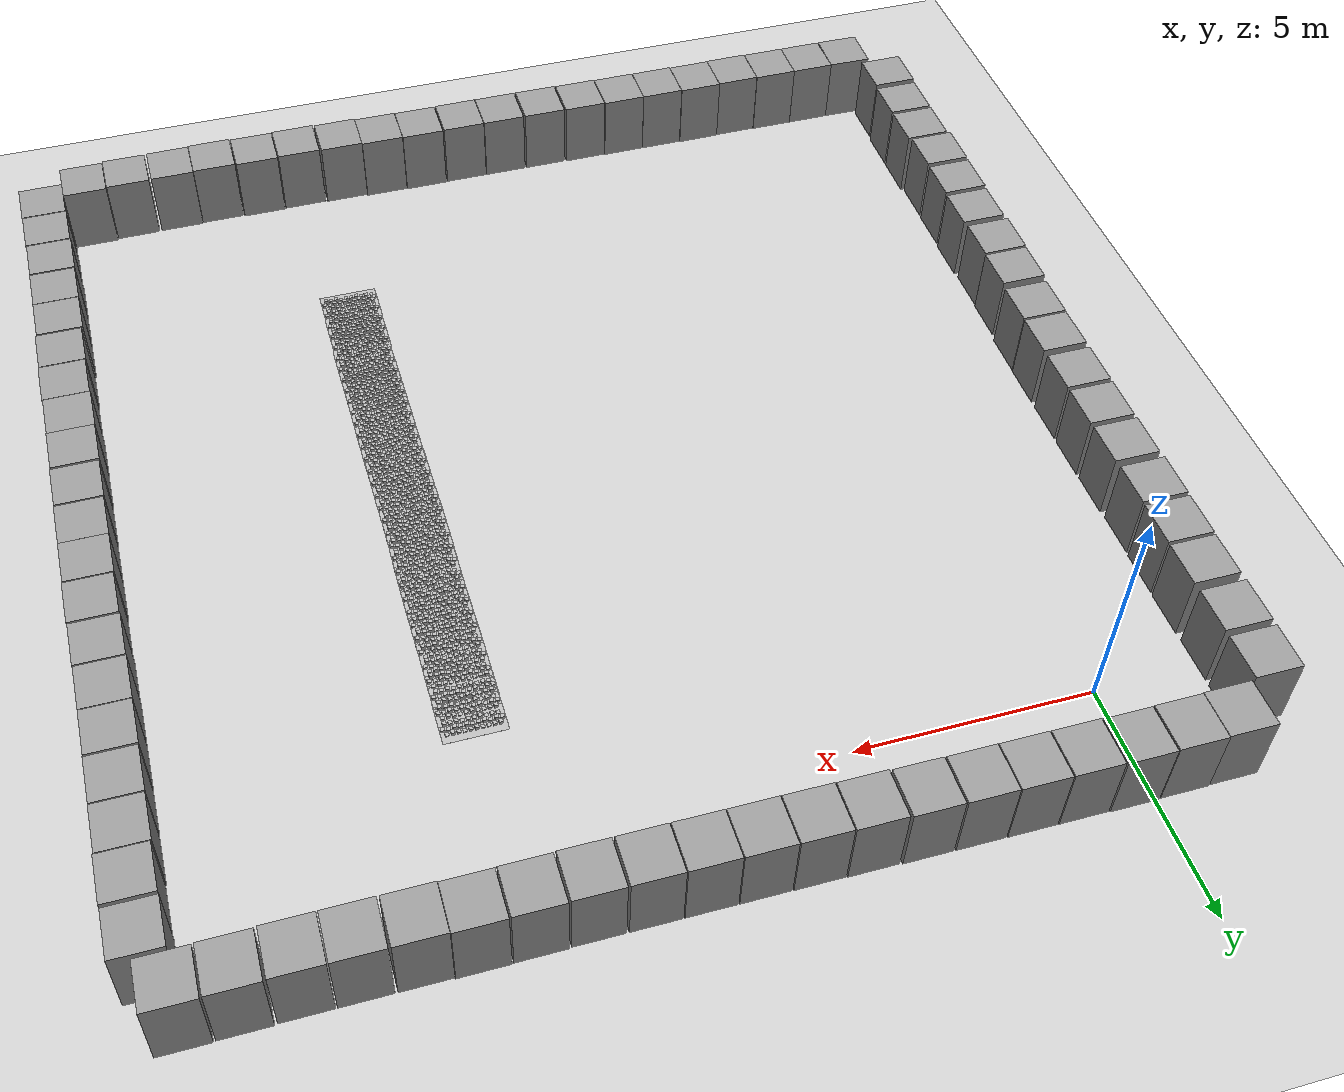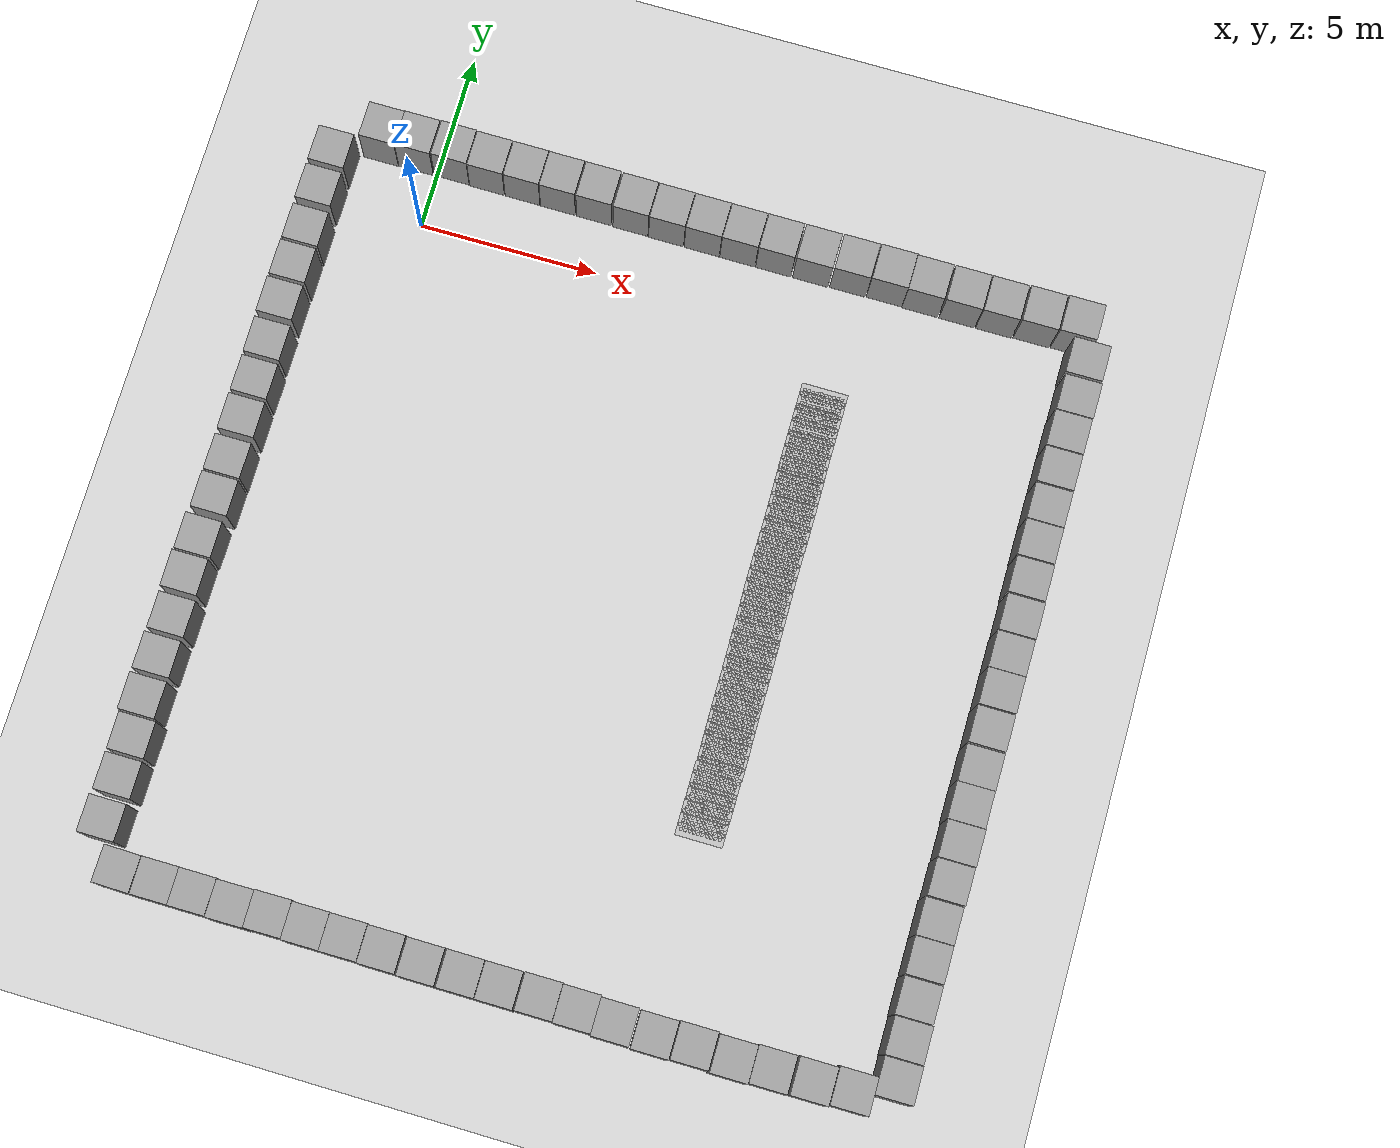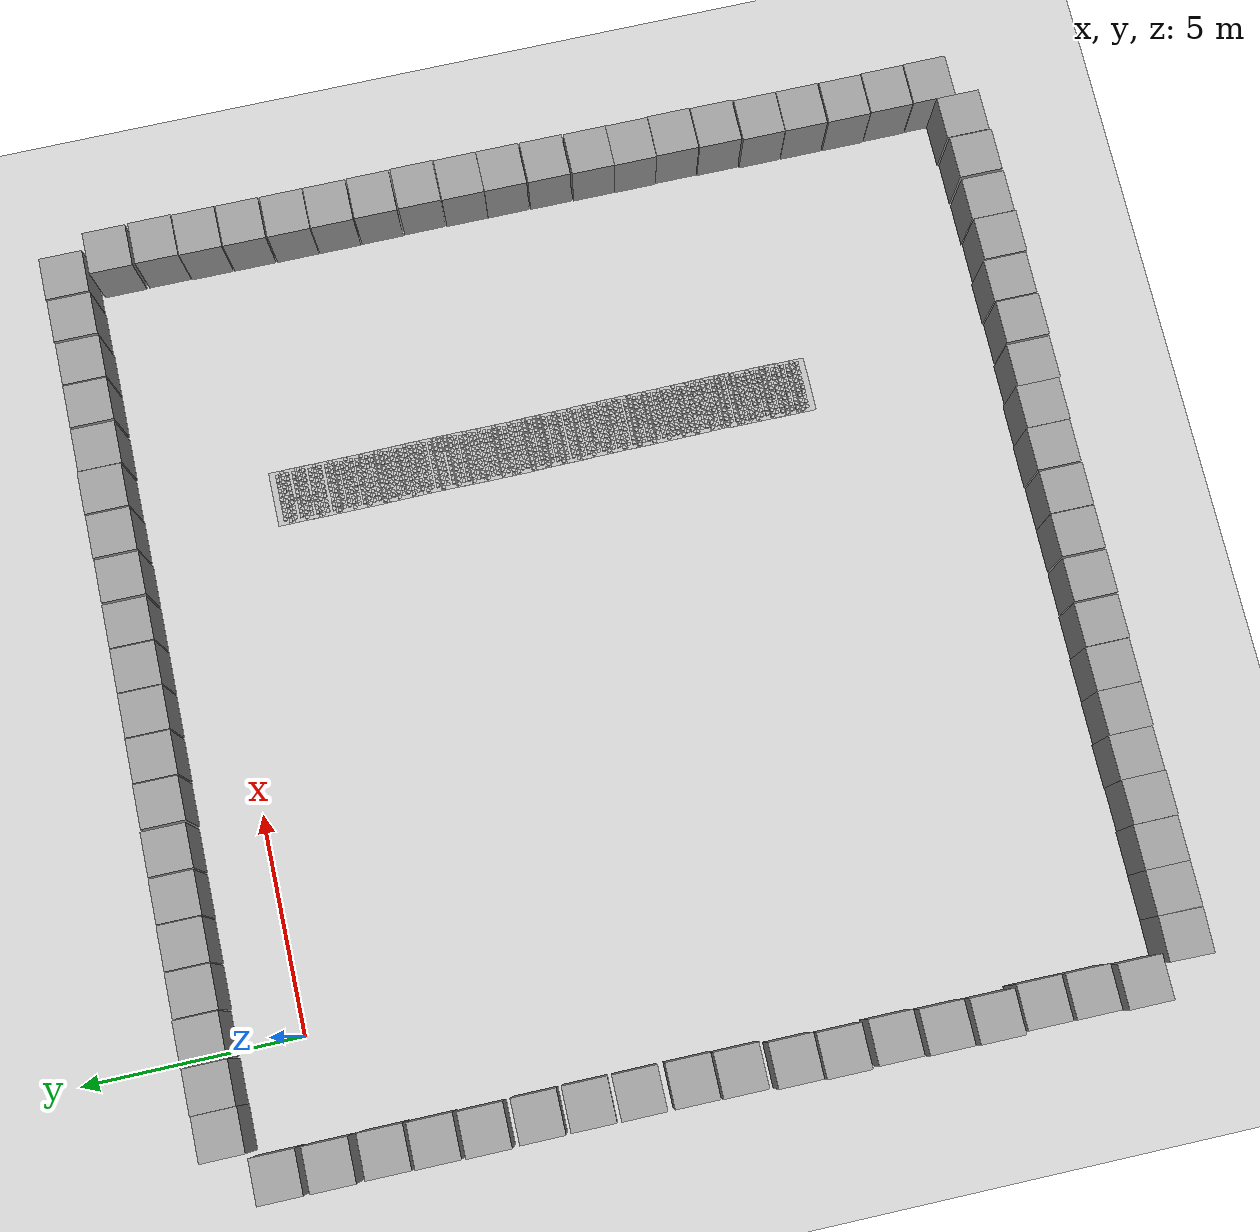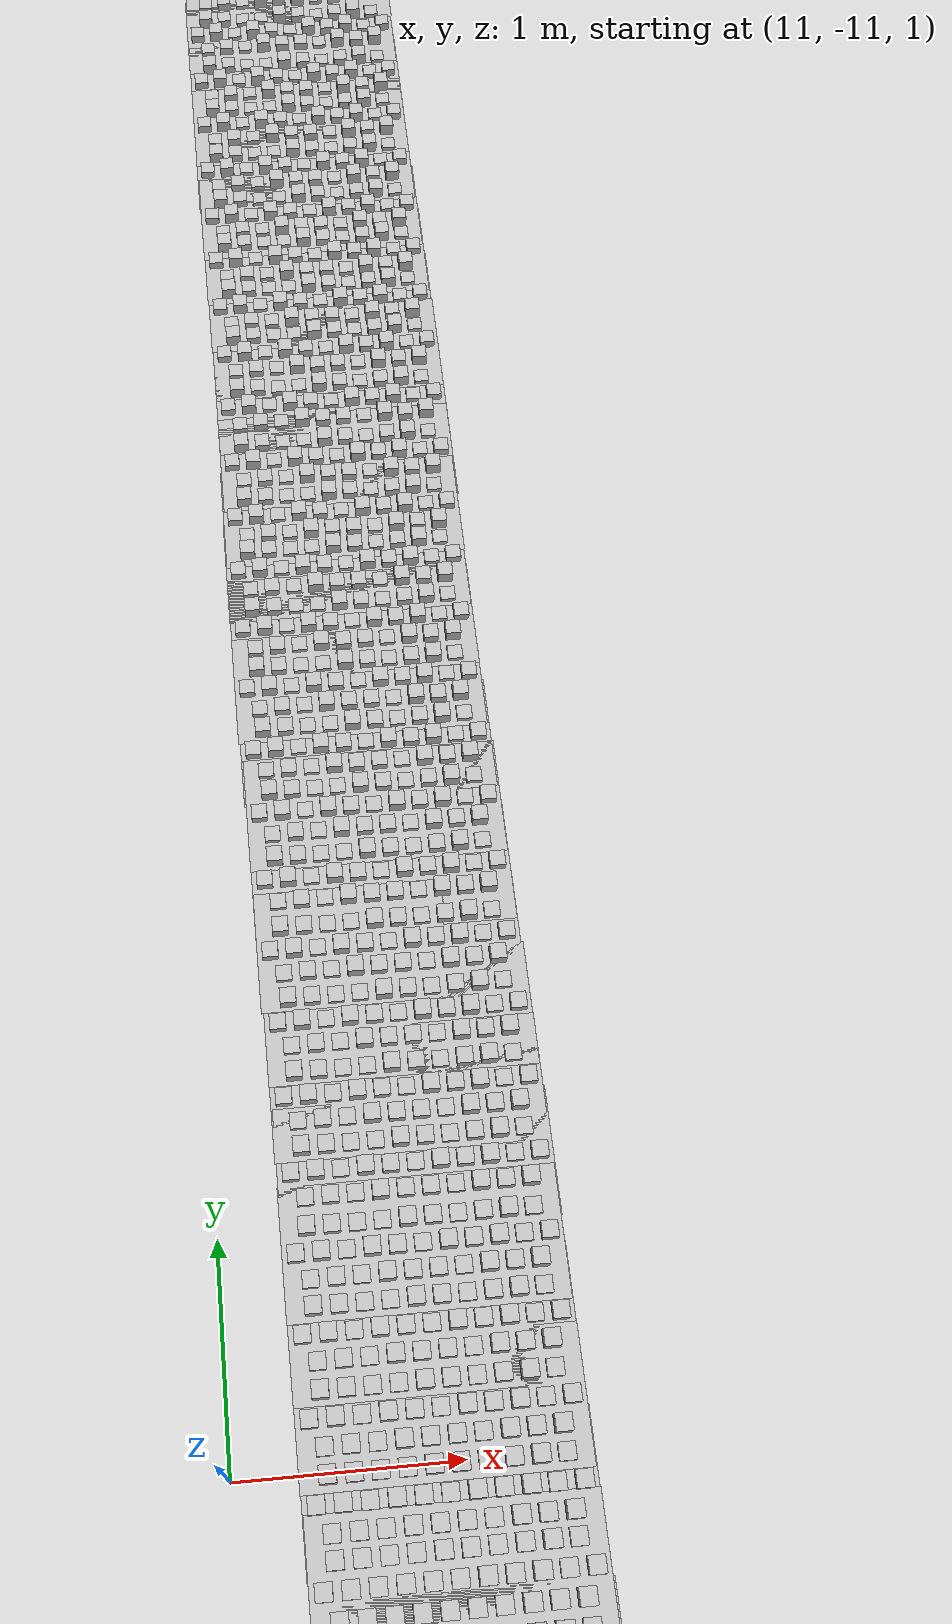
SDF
<sdf version="1.6">
 <world name="default">
  <light name="sun" type="directional">
   <pose>0 0 10 0 -0 0</pose>
   <diffuse>0.8 0.8 0.8 1</diffuse>
   <specular>0.2 0.2 0.2 1</specular>
   <attenuation>
    <range>1000</range>
    <constant>0.9</constant>
    <linear>0.01</linear>
    <quadratic>0.001</quadratic>
   </attenuation>
   <direction>-0.5 0.1 -0.9</direction>
  </light>
  <model name="ground_plane">
   <static>1</static>
   <link name="link">
    <collision name="collision">
     <geometry><plane><normal>0 0 1</normal><size>100 100</size></plane></geometry>
     <surface><friction><ode><mu>100</mu><mu2>50</mu2></ode></friction></surface>
    </collision>
    <visual name="visual">
     <cast_shadows>0</cast_shadows>
     <geometry><plane><normal>0 0 1</normal><size>100 100</size></plane></geometry>
     <material>
      <script><uri>file://media/materials/scripts/gazebo.material</uri><name>Gazebo/Grey</name></script>
     </material>
    </visual>
   </link>
  </model>
  <gravity>0 0 -9.8</gravity>
  <magnetic_field>6e-06 2.3e-05 -4.2e-05</magnetic_field>
  <atmosphere type="adiabatic"/>
  <physics name="default_physics" default="0" type="ode">
   <max_step_size>0.001</max_step_size>
   <real_time_factor>1</real_time_factor>
   <real_time_update_rate>1000</real_time_update_rate>
  </physics>
  <scene><ambient>0.4 0.4 0.4 1</ambient><background>0.7 0.7 0.7 1</background><shadows>1</shadows></scene>
  <spherical_coordinates>
   <surface_model>EARTH_WGS84</surface_model>
   <latitude_deg>0</latitude_deg>
   <longitude_deg>0</longitude_deg>
   <elevation>0</elevation>
   <heading_deg>0</heading_deg>
  </spherical_coordinates>
  <model name="frc2016_roughterrain_clone">
   <static>1</static>
   <link name="link">
    <visual name="platform">
     <pose>0 0 0.08269 0 -0 0</pose>
     <geometry><box><size>1.27 0.5969 0.003175</size></box></geometry>
    </visual>
    <collision name="platform">
     <pose>0 0 0.08269 0 -0 0</pose>
     <geometry><box><size>1.27 0.5969 0.003175</size></box></geometry>
    </collision>
    <visual name="row1_block1_sm">
     <pose>0.51435 0.1143 0.09698 0 -0 0</pose>
     <geometry><box><size>0.0762 0.0762 0.0254</size></box></geometry>
    </visual>
    <collision name="row1_block1_sm">
     <pose>0.51435 0.1143 0.09698 0 -0 0</pose>
     <geometry><box><size>0.0762 0.0762 0.0254</size></box></geometry>
    </collision>
    <visual name="row1_block2_lg">
     <pose>0.40005 0.1143 0.12238 0 -0 0</pose>
     <geometry><box><size>0.0762 0.0762 0.0762</size></box></geometry>
    </visual>
    <collision name="row1_block2_lg">
     <pose>0.40005 0.1143 0.12238 0 -0 0</pose>
     <geometry><box><size>0.0762 0.0762 0.0762</size></box></geometry>
    </collision>
    <visual name="row1_block3_md">
     <pose>0.28575 0.1143 0.10968 0 -0 0</pose>
     <geometry><box><size>0.0762 0.0762 0.0508</size></box></geometry>
    </visual>
    <collision name="row1_block3_md">
     <pose>0.28575 0.1143 0.10968 0 -0 0</pose>
     <geometry><box><size>0.0762 0.0762 0.0508</size></box></geometry>
    </collision>
    <visual name="row1_block4_sm">
     <pose>0.17145 0.1143 0.09698 0 -0 0</pose>
     <geometry><box><size>0.0762 0.0762 0.0254</size></box></geometry>
    </visual>
    <collision name="row1_block4_sm">
     <pose>0.17145 0.1143 0.09698 0 -0 0</pose>
     <geometry><box><size>0.0762 0.0762 0.0254</size></box></geometry>
    </collision>
    <visual name="row1_block5_md">
     <pose>0.05715 0.1143 0.10968 0 -0 0</pose>
     <geometry><box><size>0.0762 0.0762 0.0508</size></box></geometry>
    </visual>
    <collision name="row1_block5_md">
     <pose>0.05715 0.1143 0.10968 0 -0 0</pose>
     <geometry><box><size>0.0762 0.0762 0.0508</size></box></geometry>
    </collision>
    <visual name="row1_block6_lg">
     <pose>-0.05715 0.1143 0.12238 0 -0 0</pose>
     <geometry><box><size>0.0762 0.0762 0.0762</size></box></geometry>
    </visual>
    <collision name="row1_block6_lg">
     <pose>-0.05715 0.1143 0.12238 0 -0 0</pose>
     <geometry><box><size>0.0762 0.0762 0.0762</size></box></geometry>
    </collision>
    <visual name="row1_block7_sm">
     <pose>-0.17145 0.1143 0.09698 0 -0 0</pose>
     <geometry><box><size>0.0762 0.0762 0.0254</size></box></geometry>
    </visual>
    <collision name="row1_block7_sm">
     <pose>-0.17145 0.1143 0.09698 0 -0 0</pose>
     <geometry><box><size>0.0762 0.0762 0.0254</size></box></geometry>
    </collision>
    <visual name="row1_block8_sm">
     <pose>-0.28575 0.1143 0.09698 0 -0 0</pose>
     <geometry><box><size>0.0762 0.0762 0.0254</size></box></geometry>
    </visual>
    <collision name="row1_block8_sm">
     <pose>-0.28575 0.1143 0.09698 0 -0 0</pose>
     <geometry><box><size>0.0762 0.0762 0.0254</size></box></geometry>
    </collision>
    <visual name="row1_block9_md">
     <pose>-0.40005 0.1143 0.10968 0 -0 0</pose>
     <geometry><box><size>0.0762 0.0762 0.0508</size></box></geometry>
    </visual>
    <collision name="row1_block9_md">
     <pose>-0.40005 0.1143 0.10968 0 -0 0</pose>
     <geometry><box><size>0.0762 0.0762 0.0508</size></box></geometry>
    </collision>
    <visual name="row1_block10_lg">
     <pose>-0.51435 0.1143 0.12238 0 -0 0</pose>
     <geometry><box><size>0.0762 0.0762 0.0762</size></box></geometry>
    </visual>
    <collision name="row1_block10_lg">
     <pose>-0.51435 0.1143 0.12238 0 -0 0</pose>
     <geometry><box><size>0.0762 0.0762 0.0762</size></box></geometry>
    </collision>
    <visual name="row2_block1_md">
     <pose>0.5715 0 0.10968 0 -0 0</pose>
     <geometry><box><size>0.0762 0.0762 0.0508</size></box></geometry>
    </visual>
    <collision name="row2_block1_md">
     <pose>0.5715 0 0.10968 0 -0 0</pose>
     <geometry><box><size>0.0762 0.0762 0.0508</size></box></geometry>
    </collision>
    <visual name="row2_block2_sm">
     <pose>0.4572 0 0.09698 0 -0 0</pose>
     <geometry><box><size>0.0762 0.0762 0.0254</size></box></geometry>
    </visual>
    <collision name="row2_block2_sm">
     <pose>0.4572 0 0.09698 0 -0 0</pose>
     <geometry><box><size>0.0762 0.0762 0.0254</size></box></geometry>
    </collision>
    <visual name="row2_block3_lg">
     <pose>0.3429 0 0.12238 0 -0 0</pose>
     <geometry><box><size>0.0762 0.0762 0.0762</size></box></geometry>
    </visual>
    <collision name="row2_block3_lg">
     <pose>0.3429 0 0.12238 0 -0 0</pose>
     <geometry><box><size>0.0762 0.0762 0.0762</size></box></geometry>
    </collision>
    <visual name="row2_block4_md">
     <pose>0.2286 0 0.10968 0 -0 0</pose>
     <geometry><box><size>0.0762 0.0762 0.0508</size></box></geometry>
    </visual>
    <collision name="row2_block4_md">
     <pose>0.2286 0 0.10968 0 -0 0</pose>
     <geometry><box><size>0.0762 0.0762 0.0508</size></box></geometry>
    </collision>
    <visual name="row2_block5_lg">
     <pose>0.1143 0 0.12238 0 -0 0</pose>
     <geometry><box><size>0.0762 0.0762 0.0762</size></box></geometry>
    </visual>
    <collision name="row2_block5_lg">
     <pose>0.1143 0 0.12238 0 -0 0</pose>
     <geometry><box><size>0.0762 0.0762 0.0762</size></box></geometry>
    </collision>
    <visual name="row2_block6_sm">
     <pose>0 0 0.09698 0 -0 0</pose>
     <geometry><box><size>0.0762 0.0762 0.0254</size></box></geometry>
    </visual>
    <collision name="row2_block6_sm">
     <pose>0 0 0.09698 0 -0 0</pose>
     <geometry><box><size>0.0762 0.0762 0.0254</size></box></geometry>
    </collision>
    <visual name="row2_block7_md">
     <pose>-0.1143 0 0.10968 0 -0 0</pose>
     <geometry><box><size>0.0762 0.0762 0.0508</size></box></geometry>
    </visual>
    <collision name="row2_block7_md">
     <pose>-0.1143 0 0.10968 0 -0 0</pose>
     <geometry><box><size>0.0762 0.0762 0.0508</size></box></geometry>
    </collision>
    <visual name="row2_block8_lg">
     <pose>-0.2286 0 0.12238 0 -0 0</pose>
     <geometry><box><size>0.0762 0.0762 0.0762</size></box></geometry>
    </visual>
    <collision name="row2_block8_lg">
     <pose>-0.2286 0 0.12238 0 -0 0</pose>
     <geometry><box><size>0.0762 0.0762 0.0762</size></box></geometry>
    </collision>
    <visual name="row2_block9_sm">
     <pose>-0.3429 0 0.09698 0 -0 0</pose>
     <geometry><box><size>0.0762 0.0762 0.0254</size></box></geometry>
    </visual>
    <collision name="row2_block9_sm">
     <pose>-0.3429 0 0.09698 0 -0 0</pose>
     <geometry><box><size>0.0762 0.0762 0.0254</size></box></geometry>
    </collision>
    <visual name="row2_block10_lg">
     <pose>-0.4572 0 0.12238 0 -0 0</pose>
     <geometry><box><size>0.0762 0.0762 0.0762</size></box></geometry>
    </visual>
    <collision name="row2_block10_lg">
     <pose>-0.4572 0 0.12238 0 -0 0</pose>
     <geometry><box><size>0.0762 0.0762 0.0762</size></box></geometry>
    </collision>
    <visual name="row2_block11_md">
     <pose>-0.5715 0 0.10968 0 -0 0</pose>
     <geometry><box><size>0.0762 0.0762 0.0508</size></box></geometry>
    </visual>
    <collision name="row2_block11_md">
     <pose>-0.5715 0 0.10968 0 -0 0</pose>
     <geometry><box><size>0.0762 0.0762 0.0508</size></box></geometry>
    </collision>
    <visual name="row3_block1_lg">
     <pose>0.51435 -0.1143 0.12238 0 -0 0</pose>
     <geometry><box><size>0.0762 0.0762 0.0762</size></box></geometry>
    </visual>
    <collision name="row3_block1_lg">
     <pose>0.51435 -0.1143 0.12238 0 -0 0</pose>
     <geometry><box><size>0.0762 0.0762 0.0762</size></box></geometry>
    </collision>
    <visual name="row3_block2_md">
     <pose>0.40005 -0.1143 0.10968 0 -0 0</pose>
     <geometry><box><size>0.0762 0.0762 0.0508</size></box></geometry>
    </visual>
    <collision name="row3_block2_md">
     <pose>0.40005 -0.1143 0.10968 0 -0 0</pose>
     <geometry><box><size>0.0762 0.0762 0.0508</size></box></geometry>
    </collision>
    <visual name="row3_block3_lg">
     <pose>0.28575 -0.1143 0.12238 0 -0 0</pose>
     <geometry><box><size>0.0762 0.0762 0.0762</size></box></geometry>
    </visual>
    <collision name="row3_block3_lg">
     <pose>0.28575 -0.1143 0.12238 0 -0 0</pose>
     <geometry><box><size>0.0762 0.0762 0.0762</size></box></geometry>
    </collision>
    <visual name="row3_block4_sm">
     <pose>0.17145 -0.1143 0.09698 0 -0 0</pose>
     <geometry><box><size>0.0762 0.0762 0.0254</size></box></geometry>
    </visual>
    <collision name="row3_block4_sm">
     <pose>0.17145 -0.1143 0.09698 0 -0 0</pose>
     <geometry><box><size>0.0762 0.0762 0.0254</size></box></geometry>
    </collision>
    <visual name="row3_block5_md">
     <pose>0.05715 -0.1143 0.10968 0 -0 0</pose>
     <geometry><box><size>0.0762 0.0762 0.0508</size></box></geometry>
    </visual>
    <collision name="row3_block5_md">
     <pose>0.05715 -0.1143 0.10968 0 -0 0</pose>
     <geometry><box><size>0.0762 0.0762 0.0508</size></box></geometry>
    </collision>
    <visual name="row3_block6_md">
     <pose>-0.05715 -0.1143 0.10968 0 -0 0</pose>
     <geometry><box><size>0.0762 0.0762 0.0508</size></box></geometry>
    </visual>
    <collision name="row3_block6_md">
     <pose>-0.05715 -0.1143 0.10968 0 -0 0</pose>
     <geometry><box><size>0.0762 0.0762 0.0508</size></box></geometry>
    </collision>
    <visual name="row3_block7_lg">
     <pose>-0.17145 -0.1143 0.12238 0 -0 0</pose>
     <geometry><box><size>0.0762 0.0762 0.0762</size></box></geometry>
    </visual>
    <collision name="row3_block7_lg">
     <pose>-0.17145 -0.1143 0.12238 0 -0 0</pose>
     <geometry><box><size>0.0762 0.0762 0.0762</size></box></geometry>
    </collision>
    <visual name="row3_block8_sm">
     <pose>-0.28575 -0.1143 0.09698 0 -0 0</pose>
     <geometry><box><size>0.0762 0.0762 0.0254</size></box></geometry>
    </visual>
    <collision name="row3_block8_sm">
     <pose>-0.28575 -0.1143 0.09698 0 -0 0</pose>
     <geometry><box><size>0.0762 0.0762 0.0254</size></box></geometry>
    </collision>
    <visual name="row3_block9_md">
     <pose>-0.40005 -0.1143 0.10968 0 -0 0</pose>
     <geometry><box><size>0.0762 0.0762 0.0508</size></box></geometry>
    </visual>
    <collision name="row3_block9_md">
     <pose>-0.40005 -0.1143 0.10968 0 -0 0</pose>
     <geometry><box><size>0.0762 0.0762 0.0508</size></box></geometry>
    </collision>
    <visual name="row3_block10_sm">
     <pose>-0.51435 -0.1143 0.09698 0 -0 0</pose>
     <geometry><box><size>0.0762 0.0762 0.0254</size></box></geometry>
    </visual>
    <collision name="row3_block10_sm">
     <pose>-0.51435 -0.1143 0.09698 0 -0 0</pose>
     <geometry><box><size>0.0762 0.0762 0.0254</size></box></geometry>
    </collision>
   </link>
   <pose>11.8734 -1.97501 0.826533 0 -0 0</pose>
  </model>
  <model name="frc2016_roughterrain_clone_0">
   <static>1</static>
   <link name="link">
    <visual name="platform">
     <pose>0 0 0.08269 0 -0 0</pose>
     <geometry><box><size>1.27 0.5969 0.003175</size></box></geometry>
    </visual>
    <collision name="platform">
     <pose>0 0 0.08269 0 -0 0</pose>
     <geometry><box><size>1.27 0.5969 0.003175</size></box></geometry>
    </collision>
    <visual name="row1_block1_sm">
     <pose>0.51435 0.1143 0.09698 0 -0 0</pose>
     <geometry><box><size>0.0762 0.0762 0.0254</size></box></geometry>
    </visual>
    <collision name="row1_block1_sm">
     <pose>0.51435 0.1143 0.09698 0 -0 0</pose>
     <geometry><box><size>0.0762 0.0762 0.0254</size></box></geometry>
    </collision>
    <visual name="row1_block2_lg">
     <pose>0.40005 0.1143 0.12238 0 -0 0</pose>
     <geometry><box><size>0.0762 0.0762 0.0762</size></box></geometry>
    </visual>
    <collision name="row1_block2_lg">
     <pose>0.40005 0.1143 0.12238 0 -0 0</pose>
     <geometry><box><size>0.0762 0.0762 0.0762</size></box></geometry>
    </collision>
    <visual name="row1_block3_md">
     <pose>0.28575 0.1143 0.10968 0 -0 0</pose>
     <geometry><box><size>0.0762 0.0762 0.0508</size></box></geometry>
    </visual>
    <collision name="row1_block3_md">
     <pose>0.28575 0.1143 0.10968 0 -0 0</pose>
     <geometry><box><size>0.0762 0.0762 0.0508</size></box></geometry>
    </collision>
    <visual name="row1_block4_sm">
     <pose>0.17145 0.1143 0.09698 0 -0 0</pose>
     <geometry><box><size>0.0762 0.0762 0.0254</size></box></geometry>
    </visual>
    <collision name="row1_block4_sm">
     <pose>0.17145 0.1143 0.09698 0 -0 0</pose>
     <geometry><box><size>0.0762 0.0762 0.0254</size></box></geometry>
    </collision>
    <visual name="row1_block5_md">
     <pose>0.05715 0.1143 0.10968 0 -0 0</pose>
     <geometry><box><size>0.0762 0.0762 0.0508</size></box></geometry>
    </visual>
    <collision name="row1_block5_md">
     <pose>0.05715 0.1143 0.10968 0 -0 0</pose>
     <geometry><box><size>0.0762 0.0762 0.0508</size></box></geometry>
    </collision>
    <visual name="row1_block6_lg">
     <pose>-0.05715 0.1143 0.12238 0 -0 0</pose>
     <geometry><box><size>0.0762 0.0762 0.0762</size></box></geometry>
    </visual>
    <collision name="row1_block6_lg">
     <pose>-0.05715 0.1143 0.12238 0 -0 0</pose>
     <geometry><box><size>0.0762 0.0762 0.0762</size></box></geometry>
    </collision>
    <visual name="row1_block7_sm">
     <pose>-0.17145 0.1143 0.09698 0 -0 0</pose>
     <geometry><box><size>0.0762 0.0762 0.0254</size></box></geometry>
    </visual>
    <collision name="row1_block7_sm">
     <pose>-0.17145 0.1143 0.09698 0 -0 0</pose>
     <geometry><box><size>0.0762 0.0762 0.0254</size></box></geometry>
    </collision>
    <visual name="row1_block8_sm">
     <pose>-0.28575 0.1143 0.09698 0 -0 0</pose>
     <geometry><box><size>0.0762 0.0762 0.0254</size></box></geometry>
    </visual>
    <collision name="row1_block8_sm">
     <pose>-0.28575 0.1143 0.09698 0 -0 0</pose>
     <geometry><box><size>0.0762 0.0762 0.0254</size></box></geometry>
    </collision>
    <visual name="row1_block9_md">
     <pose>-0.40005 0.1143 0.10968 0 -0 0</pose>
     <geometry><box><size>0.0762 0.0762 0.0508</size></box></geometry>
    </visual>
    <collision name="row1_block9_md">
     <pose>-0.40005 0.1143 0.10968 0 -0 0</pose>
     <geometry><box><size>0.0762 0.0762 0.0508</size></box></geometry>
    </collision>
    <visual name="row1_block10_lg">
     <pose>-0.51435 0.1143 0.12238 0 -0 0</pose>
     <geometry><box><size>0.0762 0.0762 0.0762</size></box></geometry>
    </visual>
    <collision name="row1_block10_lg">
     <pose>-0.51435 0.1143 0.12238 0 -0 0</pose>
     <geometry><box><size>0.0762 0.0762 0.0762</size></box></geometry>
    </collision>
    <visual name="row2_block1_md">
     <pose>0.5715 0 0.10968 0 -0 0</pose>
     <geometry><box><size>0.0762 0.0762 0.0508</size></box></geometry>
    </visual>
    <collision name="row2_block1_md">
     <pose>0.5715 0 0.10968 0 -0 0</pose>
     <geometry><box><size>0.0762 0.0762 0.0508</size></box></geometry>
    </collision>
    <visual name="row2_block2_sm">
     <pose>0.4572 0 0.09698 0 -0 0</pose>
     <geometry><box><size>0.0762 0.0762 0.0254</size></box></geometry>
    </visual>
    <collision name="row2_block2_sm">
     <pose>0.4572 0 0.09698 0 -0 0</pose>
     <geometry><box><size>0.0762 0.0762 0.0254</size></box></geometry>
    </collision>
    <visual name="row2_block3_lg">
     <pose>0.3429 0 0.12238 0 -0 0</pose>
     <geometry><box><size>0.0762 0.0762 0.0762</size></box></geometry>
    </visual>
    <collision name="row2_block3_lg">
     <pose>0.3429 0 0.12238 0 -0 0</pose>
     <geometry><box><size>0.0762 0.0762 0.0762</size></box></geometry>
    </collision>
    <visual name="row2_block4_md">
     <pose>0.2286 0 0.10968 0 -0 0</pose>
     <geometry><box><size>0.0762 0.0762 0.0508</size></box></geometry>
    </visual>
    <collision name="row2_block4_md">
     <pose>0.2286 0 0.10968 0 -0 0</pose>
     <geometry><box><size>0.0762 0.0762 0.0508</size></box></geometry>
    </collision>
    <visual name="row2_block5_lg">
     <pose>0.1143 0 0.12238 0 -0 0</pose>
     <geometry><box><size>0.0762 0.0762 0.0762</size></box></geometry>
    </visual>
    <collision name="row2_block5_lg">
     <pose>0.1143 0 0.12238 0 -0 0</pose>
     <geometry><box><size>0.0762 0.0762 0.0762</size></box></geometry>
    </collision>
    <visual name="row2_block6_sm">
     <pose>0 0 0.09698 0 -0 0</pose>
     <geometry><box><size>0.0762 0.0762 0.0254</size></box></geometry>
    </visual>
    <collision name="row2_block6_sm">
     <pose>0 0 0.09698 0 -0 0</pose>
     <geometry><box><size>0.0762 0.0762 0.0254</size></box></geometry>
    </collision>
    <visual name="row2_block7_md">
     <pose>-0.1143 0 0.10968 0 -0 0</pose>
     <geometry><box><size>0.0762 0.0762 0.0508</size></box></geometry>
    </visual>
    <collision name="row2_block7_md">
     <pose>-0.1143 0 0.10968 0 -0 0</pose>
     <geometry><box><size>0.0762 0.0762 0.0508</size></box></geometry>
    </collision>
    <visual name="row2_block8_lg">
     <pose>-0.2286 0 0.12238 0 -0 0</pose>
     <geometry><box><size>0.0762 0.0762 0.0762</size></box></geometry>
    </visual>
    <collision name="row2_block8_lg">
     <pose>-0.2286 0 0.12238 0 -0 0</pose>
     <geometry><box><size>0.0762 0.0762 0.0762</size></box></geometry>
    </collision>
    <visual name="row2_block9_sm">
     <pose>-0.3429 0 0.09698 0 -0 0</pose>
     <geometry><box><size>0.0762 0.0762 0.0254</size></box></geometry>
    </visual>
    <collision name="row2_block9_sm">
     <pose>-0.3429 0 0.09698 0 -0 0</pose>
     <geometry><box><size>0.0762 0.0762 0.0254</size></box></geometry>
    </collision>
    <visual name="row2_block10_lg">
     <pose>-0.4572 0 0.12238 0 -0 0</pose>
     <geometry><box><size>0.0762 0.0762 0.0762</size></box></geometry>
    </visual>
    <collision name="row2_block10_lg">
     <pose>-0.4572 0 0.12238 0 -0 0</pose>
     <geometry><box><size>0.0762 0.0762 0.0762</size></box></geometry>
    </collision>
    <visual name="row2_block11_md">
     <pose>-0.5715 0 0.10968 0 -0 0</pose>
     <geometry><box><size>0.0762 0.0762 0.0508</size></box></geometry>
    </visual>
    <collision name="row2_block11_md">
     <pose>-0.5715 0 0.10968 0 -0 0</pose>
     <geometry><box><size>0.0762 0.0762 0.0508</size></box></geometry>
    </collision>
    <visual name="row3_block1_lg">
     <pose>0.51435 -0.1143 0.12238 0 -0 0</pose>
     <geometry><box><size>0.0762 0.0762 0.0762</size></box></geometry>
    </visual>
    <collision name="row3_block1_lg">
     <pose>0.51435 -0.1143 0.12238 0 -0 0</pose>
     <geometry><box><size>0.0762 0.0762 0.0762</size></box></geometry>
    </collision>
    <visual name="row3_block2_md">
     <pose>0.40005 -0.1143 0.10968 0 -0 0</pose>
     <geometry><box><size>0.0762 0.0762 0.0508</size></box></geometry>
    </visual>
    <collision name="row3_block2_md">
     <pose>0.40005 -0.1143 0.10968 0 -0 0</pose>
     <geometry><box><size>0.0762 0.0762 0.0508</size></box></geometry>
    </collision>
    <visual name="row3_block3_lg">
     <pose>0.28575 -0.1143 0.12238 0 -0 0</pose>
     <geometry><box><size>0.0762 0.0762 0.0762</size></box></geometry>
    </visual>
    <collision name="row3_block3_lg">
     <pose>0.28575 -0.1143 0.12238 0 -0 0</pose>
     <geometry><box><size>0.0762 0.0762 0.0762</size></box></geometry>
    </collision>
    <visual name="row3_block4_sm">
     <pose>0.17145 -0.1143 0.09698 0 -0 0</pose>
     <geometry><box><size>0.0762 0.0762 0.0254</size></box></geometry>
    </visual>
    <collision name="row3_block4_sm">
     <pose>0.17145 -0.1143 0.09698 0 -0 0</pose>
     <geometry><box><size>0.0762 0.0762 0.0254</size></box></geometry>
    </collision>
    <visual name="row3_block5_md">
     <pose>0.05715 -0.1143 0.10968 0 -0 0</pose>
     <geometry><box><size>0.0762 0.0762 0.0508</size></box></geometry>
    </visual>
    <collision name="row3_block5_md">
     <pose>0.05715 -0.1143 0.10968 0 -0 0</pose>
     <geometry><box><size>0.0762 0.0762 0.0508</size></box></geometry>
    </collision>
    <visual name="row3_block6_md">
     <pose>-0.05715 -0.1143 0.10968 0 -0 0</pose>
     <geometry><box><size>0.0762 0.0762 0.0508</size></box></geometry>
    </visual>
    <collision name="row3_block6_md">
     <pose>-0.05715 -0.1143 0.10968 0 -0 0</pose>
     <geometry><box><size>0.0762 0.0762 0.0508</size></box></geometry>
    </collision>
    <visual name="row3_block7_lg">
     <pose>-0.17145 -0.1143 0.12238 0 -0 0</pose>
     <geometry><box><size>0.0762 0.0762 0.0762</size></box></geometry>
    </visual>
    <collision name="row3_block7_lg">
     <pose>-0.17145 -0.1143 0.12238 0 -0 0</pose>
     <geometry><box><size>0.0762 0.0762 0.0762</size></box></geometry>
    </collision>
    <visual name="row3_block8_sm">
     <pose>-0.28575 -0.1143 0.09698 0 -0 0</pose>
     <geometry><box><size>0.0762 0.0762 0.0254</size></box></geometry>
    </visual>
    <collision name="row3_block8_sm">
     <pose>-0.28575 -0.1143 0.09698 0 -0 0</pose>
     <geometry><box><size>0.0762 0.0762 0.0254</size></box></geometry>
    </collision>
    <visual name="row3_block9_md">
     <pose>-0.40005 -0.1143 0.10968 0 -0 0</pose>
     <geometry><box><size>0.0762 0.0762 0.0508</size></box></geometry>
    </visual>
    <collision name="row3_block9_md">
     <pose>-0.40005 -0.1143 0.10968 0 -0 0</pose>
     <geometry><box><size>0.0762 0.0762 0.0508</size></box></geometry>
    </collision>
    <visual name="row3_block10_sm">
     <pose>-0.51435 -0.1143 0.09698 0 -0 0</pose>
     <geometry><box><size>0.0762 0.0762 0.0254</size></box></geometry>
    </visual>
    <collision name="row3_block10_sm">
     <pose>-0.51435 -0.1143 0.09698 0 -0 0</pose>
     <geometry><box><size>0.0762 0.0762 0.0254</size></box></geometry>
    </collision>
   </link>
   <pose>11.876 -2.35475 0.826533 0 -0 0</pose>
  </model>
  <model name="frc2016_roughterrain_clone_1">
   <static>1</static>
   <link name="link">
    <visual name="platform">
     <pose>0 0 0.08269 0 -0 0</pose>
     <geometry><box><size>1.27 0.5969 0.003175</size></box></geometry>
    </visual>
    <collision name="platform">
     <pose>0 0 0.08269 0 -0 0</pose>
     <geometry><box><size>1.27 0.5969 0.003175</size></box></geometry>
    </collision>
    <visual name="row1_block1_sm">
     <pose>0.51435 0.1143 0.09698 0 -0 0</pose>
     <geometry><box><size>0.0762 0.0762 0.0254</size></box></geometry>
    </visual>
    <collision name="row1_block1_sm">
     <pose>0.51435 0.1143 0.09698 0 -0 0</pose>
     <geometry><box><size>0.0762 0.0762 0.0254</size></box></geometry>
    </collision>
    <visual name="row1_block2_lg">
     <pose>0.40005 0.1143 0.12238 0 -0 0</pose>
     <geometry><box><size>0.0762 0.0762 0.0762</size></box></geometry>
    </visual>
    <collision name="row1_block2_lg">
     <pose>0.40005 0.1143 0.12238 0 -0 0</pose>
     <geometry><box><size>0.0762 0.0762 0.0762</size></box></geometry>
    </collision>
    <visual name="row1_block3_md">
     <pose>0.28575 0.1143 0.10968 0 -0 0</pose>
     <geometry><box><size>0.0762 0.0762 0.0508</size></box></geometry>
    </visual>
    <collision name="row1_block3_md">
     <pose>0.28575 0.1143 0.10968 0 -0 0</pose>
     <geometry><box><size>0.0762 0.0762 0.0508</size></box></geometry>
    </collision>
    <visual name="row1_block4_sm">
     <pose>0.17145 0.1143 0.09698 0 -0 0</pose>
     <geometry><box><size>0.0762 0.0762 0.0254</size></box></geometry>
    </visual>
    <collision name="row1_block4_sm">
     <pose>0.17145 0.1143 0.09698 0 -0 0</pose>
     <geometry><box><size>0.0762 0.0762 0.0254</size></box></geometry>
    </collision>
    <visual name="row1_block5_md">
     <pose>0.05715 0.1143 0.10968 0 -0 0</pose>
     <geometry><box><size>0.0762 0.0762 0.0508</size></box></geometry>
    </visual>
    <collision name="row1_block5_md">
     <pose>0.05715 0.1143 0.10968 0 -0 0</pose>
     <geometry><box><size>0.0762 0.0762 0.0508</size></box></geometry>
    </collision>
    <visual name="row1_block6_lg">
     <pose>-0.05715 0.1143 0.12238 0 -0 0</pose>
     <geometry><box><size>0.0762 0.0762 0.0762</size></box></geometry>
    </visual>
    <collision name="row1_block6_lg">
     <pose>-0.05715 0.1143 0.12238 0 -0 0</pose>
     <geometry><box><size>0.0762 0.0762 0.0762</size></box></geometry>
    </collision>
    <visual name="row1_block7_sm">
     <pose>-0.17145 0.1143 0.09698 0 -0 0</pose>
     <geometry><box><size>0.0762 0.0762 0.0254</size></box></geometry>
    </visual>
    <collision name="row1_block7_sm">
     <pose>-0.17145 0.1143 0.09698 0 -0 0</pose>
     <geometry><box><size>0.0762 0.0762 0.0254</size></box></geometry>
    </collision>
    <visual name="row1_block8_sm">
     <pose>-0.28575 0.1143 0.09698 0 -0 0</pose>
     <geometry><box><size>0.0762 0.0762 0.0254</size></box></geometry>
    </visual>
    <collision name="row1_block8_sm">
     <pose>-0.28575 0.1143 0.09698 0 -0 0</pose>
     <geometry><box><size>0.0762 0.0762 0.0254</size></box></geometry>
    </collision>
    <visual name="row1_block9_md">
     <pose>-0.40005 0.1143 0.10968 0 -0 0</pose>
     <geometry><box><size>0.0762 0.0762 0.0508</size></box></geometry>
    </visual>
    <collision name="row1_block9_md">
     <pose>-0.40005 0.1143 0.10968 0 -0 0</pose>
     <geometry><box><size>0.0762 0.0762 0.0508</size></box></geometry>
    </collision>
    <visual name="row1_block10_lg">
     <pose>-0.51435 0.1143 0.12238 0 -0 0</pose>
     <geometry><box><size>0.0762 0.0762 0.0762</size></box></geometry>
    </visual>
    <collision name="row1_block10_lg">
     <pose>-0.51435 0.1143 0.12238 0 -0 0</pose>
     <geometry><box><size>0.0762 0.0762 0.0762</size></box></geometry>
    </collision>
    <visual name="row2_block1_md">
     <pose>0.5715 0 0.10968 0 -0 0</pose>
     <geometry><box><size>0.0762 0.0762 0.0508</size></box></geometry>
    </visual>
    <collision name="row2_block1_md">
     <pose>0.5715 0 0.10968 0 -0 0</pose>
     <geometry><box><size>0.0762 0.0762 0.0508</size></box></geometry>
    </collision>
    <visual name="row2_block2_sm">
     <pose>0.4572 0 0.09698 0 -0 0</pose>
     <geometry><box><size>0.0762 0.0762 0.0254</size></box></geometry>
    </visual>
    <collision name="row2_block2_sm">
     <pose>0.4572 0 0.09698 0 -0 0</pose>
     <geometry><box><size>0.0762 0.0762 0.0254</size></box></geometry>
    </collision>
    <visual name="row2_block3_lg">
     <pose>0.3429 0 0.12238 0 -0 0</pose>
     <geometry><box><size>0.0762 0.0762 0.0762</size></box></geometry>
    </visual>
    <collision name="row2_block3_lg">
     <pose>0.3429 0 0.12238 0 -0 0</pose>
     <geometry><box><size>0.0762 0.0762 0.0762</size></box></geometry>
    </collision>
    <visual name="row2_block4_md">
     <pose>0.2286 0 0.10968 0 -0 0</pose>
     <geometry><box><size>0.0762 0.0762 0.0508</size></box></geometry>
    </visual>
    <collision name="row2_block4_md">
     <pose>0.2286 0 0.10968 0 -0 0</pose>
     <geometry><box><size>0.0762 0.0762 0.0508</size></box></geometry>
    </collision>
    <visual name="row2_block5_lg">
     <pose>0.1143 0 0.12238 0 -0 0</pose>
     <geometry><box><size>0.0762 0.0762 0.0762</size></box></geometry>
    </visual>
    <collision name="row2_block5_lg">
     <pose>0.1143 0 0.12238 0 -0 0</pose>
     <geometry><box><size>0.0762 0.0762 0.0762</size></box></geometry>
    </collision>
    <visual name="row2_block6_sm">
     <pose>0 0 0.09698 0 -0 0</pose>
     <geometry><box><size>0.0762 0.0762 0.0254</size></box></geometry>
    </visual>
    <collision name="row2_block6_sm">
     <pose>0 0 0.09698 0 -0 0</pose>
     <geometry><box><size>0.0762 0.0762 0.0254</size></box></geometry>
    </collision>
    <visual name="row2_block7_md">
     <pose>-0.1143 0 0.10968 0 -0 0</pose>
     <geometry><box><size>0.0762 0.0762 0.0508</size></box></geometry>
    </visual>
    <collision name="row2_block7_md">
     <pose>-0.1143 0 0.10968 0 -0 0</pose>
     <geometry><box><size>0.0762 0.0762 0.0508</size></box></geometry>
    </collision>
    <visual name="row2_block8_lg">
     <pose>-0.2286 0 0.12238 0 -0 0</pose>
     <geometry><box><size>0.0762 0.0762 0.0762</size></box></geometry>
    </visual>
    <collision name="row2_block8_lg">
     <pose>-0.2286 0 0.12238 0 -0 0</pose>
     <geometry><box><size>0.0762 0.0762 0.0762</size></box></geometry>
    </collision>
    <visual name="row2_block9_sm">
     <pose>-0.3429 0 0.09698 0 -0 0</pose>
     <geometry><box><size>0.0762 0.0762 0.0254</size></box></geometry>
    </visual>
    <collision name="row2_block9_sm">
     <pose>-0.3429 0 0.09698 0 -0 0</pose>
     <geometry><box><size>0.0762 0.0762 0.0254</size></box></geometry>
    </collision>
    <visual name="row2_block10_lg">
     <pose>-0.4572 0 0.12238 0 -0 0</pose>
     <geometry><box><size>0.0762 0.0762 0.0762</size></box></geometry>
    </visual>
    <collision name="row2_block10_lg">
     <pose>-0.4572 0 0.12238 0 -0 0</pose>
     <geometry><box><size>0.0762 0.0762 0.0762</size></box></geometry>
    </collision>
    <visual name="row2_block11_md">
     <pose>-0.5715 0 0.10968 0 -0 0</pose>
     <geometry><box><size>0.0762 0.0762 0.0508</size></box></geometry>
    </visual>
    <collision name="row2_block11_md">
     <pose>-0.5715 0 0.10968 0 -0 0</pose>
     <geometry><box><size>0.0762 0.0762 0.0508</size></box></geometry>
    </collision>
    <visual name="row3_block1_lg">
     <pose>0.51435 -0.1143 0.12238 0 -0 0</pose>
     <geometry><box><size>0.0762 0.0762 0.0762</size></box></geometry>
    </visual>
    <collision name="row3_block1_lg">
     <pose>0.51435 -0.1143 0.12238 0 -0 0</pose>
     <geometry><box><size>0.0762 0.0762 0.0762</size></box></geometry>
    </collision>
    <visual name="row3_block2_md">
     <pose>0.40005 -0.1143 0.10968 0 -0 0</pose>
     <geometry><box><size>0.0762 0.0762 0.0508</size></box></geometry>
    </visual>
    <collision name="row3_block2_md">
     <pose>0.40005 -0.1143 0.10968 0 -0 0</pose>
     <geometry><box><size>0.0762 0.0762 0.0508</size></box></geometry>
    </collision>
    <visual name="row3_block3_lg">
     <pose>0.28575 -0.1143 0.12238 0 -0 0</pose>
     <geometry><box><size>0.0762 0.0762 0.0762</size></box></geometry>
    </visual>
    <collision name="row3_block3_lg">
     <pose>0.28575 -0.1143 0.12238 0 -0 0</pose>
     <geometry><box><size>0.0762 0.0762 0.0762</size></box></geometry>
    </collision>
    <visual name="row3_block4_sm">
     <pose>0.17145 -0.1143 0.09698 0 -0 0</pose>
     <geometry><box><size>0.0762 0.0762 0.0254</size></box></geometry>
    </visual>
    <collision name="row3_block4_sm">
     <pose>0.17145 -0.1143 0.09698 0 -0 0</pose>
     <geometry><box><size>0.0762 0.0762 0.0254</size></box></geometry>
    </collision>
    <visual name="row3_block5_md">
     <pose>0.05715 -0.1143 0.10968 0 -0 0</pose>
     <geometry><box><size>0.0762 0.0762 0.0508</size></box></geometry>
    </visual>
    <collision name="row3_block5_md">
     <pose>0.05715 -0.1143 0.10968 0 -0 0</pose>
     <geometry><box><size>0.0762 0.0762 0.0508</size></box></geometry>
    </collision>
    <visual name="row3_block6_md">
     <pose>-0.05715 -0.1143 0.10968 0 -0 0</pose>
     <geometry><box><size>0.0762 0.0762 0.0508</size></box></geometry>
    </visual>
    <collision name="row3_block6_md">
     <pose>-0.05715 -0.1143 0.10968 0 -0 0</pose>
     <geometry><box><size>0.0762 0.0762 0.0508</size></box></geometry>
    </collision>
    <visual name="row3_block7_lg">
     <pose>-0.17145 -0.1143 0.12238 0 -0 0</pose>
     <geometry><box><size>0.0762 0.0762 0.0762</size></box></geometry>
    </visual>
    <collision name="row3_block7_lg">
     <pose>-0.17145 -0.1143 0.12238 0 -0 0</pose>
     <geometry><box><size>0.0762 0.0762 0.0762</size></box></geometry>
    </collision>
    <visual name="row3_block8_sm">
     <pose>-0.28575 -0.1143 0.09698 0 -0 0</pose>
     <geometry><box><size>0.0762 0.0762 0.0254</size></box></geometry>
    </visual>
    <collision name="row3_block8_sm">
     <pose>-0.28575 -0.1143 0.09698 0 -0 0</pose>
     <geometry><box><size>0.0762 0.0762 0.0254</size></box></geometry>
    </collision>
    <visual name="row3_block9_md">
     <pose>-0.40005 -0.1143 0.10968 0 -0 0</pose>
     <geometry><box><size>0.0762 0.0762 0.0508</size></box></geometry>
    </visual>
    <collision name="row3_block9_md">
     <pose>-0.40005 -0.1143 0.10968 0 -0 0</pose>
     <geometry><box><size>0.0762 0.0762 0.0508</size></box></geometry>
    </collision>
    <visual name="row3_block10_sm">
     <pose>-0.51435 -0.1143 0.09698 0 -0 0</pose>
     <geometry><box><size>0.0762 0.0762 0.0254</size></box></geometry>
    </visual>
    <collision name="row3_block10_sm">
     <pose>-0.51435 -0.1143 0.09698 0 -0 0</pose>
     <geometry><box><size>0.0762 0.0762 0.0254</size></box></geometry>
    </collision>
   </link>
   <pose>11.8703 -2.72596 0.826533 0 -0 0</pose>
  </model>
  <model name="frc2016_roughterrain_clone_2">
   <static>1</static>
   <link name="link">
    <visual name="platform">
     <pose>0 0 0.08269 0 -0 0</pose>
     <geometry><box><size>1.27 0.5969 0.003175</size></box></geometry>
    </visual>
    <collision name="platform">
     <pose>0 0 0.08269 0 -0 0</pose>
     <geometry><box><size>1.27 0.5969 0.003175</size></box></geometry>
    </collision>
    <visual name="row1_block1_sm">
     <pose>0.51435 0.1143 0.09698 0 -0 0</pose>
     <geometry><box><size>0.0762 0.0762 0.0254</size></box></geometry>
    </visual>
    <collision name="row1_block1_sm">
     <pose>0.51435 0.1143 0.09698 0 -0 0</pose>
     <geometry><box><size>0.0762 0.0762 0.0254</size></box></geometry>
    </collision>
    <visual name="row1_block2_lg">
     <pose>0.40005 0.1143 0.12238 0 -0 0</pose>
     <geometry><box><size>0.0762 0.0762 0.0762</size></box></geometry>
    </visual>
    <collision name="row1_block2_lg">
     <pose>0.40005 0.1143 0.12238 0 -0 0</pose>
     <geometry><box><size>0.0762 0.0762 0.0762</size></box></geometry>
    </collision>
    <visual name="row1_block3_md">
     <pose>0.28575 0.1143 0.10968 0 -0 0</pose>
     <geometry><box><size>0.0762 0.0762 0.0508</size></box></geometry>
    </visual>
    <collision name="row1_block3_md">
     <pose>0.28575 0.1143 0.10968 0 -0 0</pose>
     <geometry><box><size>0.0762 0.0762 0.0508</size></box></geometry>
    </collision>
    <visual name="row1_block4_sm">
     <pose>0.17145 0.1143 0.09698 0 -0 0</pose>
     <geometry><box><size>0.0762 0.0762 0.0254</size></box></geometry>
    </visual>
    <collision name="row1_block4_sm">
     <pose>0.17145 0.1143 0.09698 0 -0 0</pose>
     <geometry><box><size>0.0762 0.0762 0.0254</size></box></geometry>
    </collision>
    <visual name="row1_block5_md">
     <pose>0.05715 0.1143 0.10968 0 -0 0</pose>
     <geometry><box><size>0.0762 0.0762 0.0508</size></box></geometry>
    </visual>
    <collision name="row1_block5_md">
     <pose>0.05715 0.1143 0.10968 0 -0 0</pose>
     <geometry><box><size>0.0762 0.0762 0.0508</size></box></geometry>
    </collision>
    <visual name="row1_block6_lg">
     <pose>-0.05715 0.1143 0.12238 0 -0 0</pose>
     <geometry><box><size>0.0762 0.0762 0.0762</size></box></geometry>
    </visual>
    <collision name="row1_block6_lg">
     <pose>-0.05715 0.1143 0.12238 0 -0 0</pose>
     <geometry><box><size>0.0762 0.0762 0.0762</size></box></geometry>
    </collision>
    <visual name="row1_block7_sm">
     <pose>-0.17145 0.1143 0.09698 0 -0 0</pose>
     <geometry><box><size>0.0762 0.0762 0.0254</size></box></geometry>
    </visual>
    <collision name="row1_block7_sm">
     <pose>-0.17145 0.1143 0.09698 0 -0 0</pose>
     <geometry><box><size>0.0762 0.0762 0.0254</size></box></geometry>
    </collision>
    <visual name="row1_block8_sm">
     <pose>-0.28575 0.1143 0.09698 0 -0 0</pose>
     <geometry><box><size>0.0762 0.0762 0.0254</size></box></geometry>
    </visual>
    <collision name="row1_block8_sm">
     <pose>-0.28575 0.1143 0.09698 0 -0 0</pose>
     <geometry><box><size>0.0762 0.0762 0.0254</size></box></geometry>
    </collision>
    <visual name="row1_block9_md">
     <pose>-0.40005 0.1143 0.10968 0 -0 0</pose>
     <geometry><box><size>0.0762 0.0762 0.0508</size></box></geometry>
    </visual>
    <collision name="row1_block9_md">
     <pose>-0.40005 0.1143 0.10968 0 -0 0</pose>
     <geometry><box><size>0.0762 0.0762 0.0508</size></box></geometry>
    </collision>
    <visual name="row1_block10_lg">
     <pose>-0.51435 0.1143 0.12238 0 -0 0</pose>
     <geometry><box><size>0.0762 0.0762 0.0762</size></box></geometry>
    </visual>
    <collision name="row1_block10_lg">
     <pose>-0.51435 0.1143 0.12238 0 -0 0</pose>
     <geometry><box><size>0.0762 0.0762 0.0762</size></box></geometry>
    </collision>
    <visual name="row2_block1_md">
     <pose>0.5715 0 0.10968 0 -0 0</pose>
     <geometry><box><size>0.0762 0.0762 0.0508</size></box></geometry>
    </visual>
    <collision name="row2_block1_md">
     <pose>0.5715 0 0.10968 0 -0 0</pose>
     <geometry><box><size>0.0762 0.0762 0.0508</size></box></geometry>
    </collision>
    <visual name="row2_block2_sm">
     <pose>0.4572 0 0.09698 0 -0 0</pose>
     <geometry><box><size>0.0762 0.0762 0.0254</size></box></geometry>
    </visual>
    <collision name="row2_block2_sm">
     <pose>0.4572 0 0.09698 0 -0 0</pose>
     <geometry><box><size>0.0762 0.0762 0.0254</size></box></geometry>
    </collision>
    <visual name="row2_block3_lg">
     <pose>0.3429 0 0.12238 0 -0 0</pose>
     <geometry><box><size>0.0762 0.0762 0.0762</size></box></geometry>
    </visual>
    <collision name="row2_block3_lg">
     <pose>0.3429 0 0.12238 0 -0 0</pose>
     <geometry><box><size>0.0762 0.0762 0.0762</size></box></geometry>
    </collision>
    <visual name="row2_block4_md">
     <pose>0.2286 0 0.10968 0 -0 0</pose>
     <geometry><box><size>0.0762 0.0762 0.0508</size></box></geometry>
    </visual>
    <collision name="row2_block4_md">
     <pose>0.2286 0 0.10968 0 -0 0</pose>
     <geometry><box><size>0.0762 0.0762 0.0508</size></box></geometry>
    </collision>
    <visual name="row2_block5_lg">
     <pose>0.1143 0 0.12238 0 -0 0</pose>
     <geometry><box><size>0.0762 0.0762 0.0762</size></box></geometry>
    </visual>
    <collision name="row2_block5_lg">
     <pose>0.1143 0 0.12238 0 -0 0</pose>
     <geometry><box><size>0.0762 0.0762 0.0762</size></box></geometry>
    </collision>
    <visual name="row2_block6_sm">
     <pose>0 0 0.09698 0 -0 0</pose>
     <geometry><box><size>0.0762 0.0762 0.0254</size></box></geometry>
    </visual>
    <collision name="row2_block6_sm">
     <pose>0 0 0.09698 0 -0 0</pose>
     <geometry><box><size>0.0762 0.0762 0.0254</size></box></geometry>
    </collision>
    <visual name="row2_block7_md">
     <pose>-0.1143 0 0.10968 0 -0 0</pose>
     <geometry><box><size>0.0762 0.0762 0.0508</size></box></geometry>
    </visual>
    <collision name="row2_block7_md">
     <pose>-0.1143 0 0.10968 0 -0 0</pose>
     <geometry><box><size>0.0762 0.0762 0.0508</size></box></geometry>
    </collision>
    <visual name="row2_block8_lg">
     <pose>-0.2286 0 0.12238 0 -0 0</pose>
     <geometry><box><size>0.0762 0.0762 0.0762</size></box></geometry>
    </visual>
    <collision name="row2_block8_lg">
     <pose>-0.2286 0 0.12238 0 -0 0</pose>
     <geometry><box><size>0.0762 0.0762 0.0762</size></box></geometry>
    </collision>
    <visual name="row2_block9_sm">
     <pose>-0.3429 0 0.09698 0 -0 0</pose>
     <geometry><box><size>0.0762 0.0762 0.0254</size></box></geometry>
    </visual>
    <collision name="row2_block9_sm">
     <pose>-0.3429 0 0.09698 0 -0 0</pose>
     <geometry><box><size>0.0762 0.0762 0.0254</size></box></geometry>
    </collision>
    <visual name="row2_block10_lg">
     <pose>-0.4572 0 0.12238 0 -0 0</pose>
     <geometry><box><size>0.0762 0.0762 0.0762</size></box></geometry>
    </visual>
    <collision name="row2_block10_lg">
     <pose>-0.4572 0 0.12238 0 -0 0</pose>
     <geometry><box><size>0.0762 0.0762 0.0762</size></box></geometry>
    </collision>
    <visual name="row2_block11_md">
     <pose>-0.5715 0 0.10968 0 -0 0</pose>
     <geometry><box><size>0.0762 0.0762 0.0508</size></box></geometry>
    </visual>
    <collision name="row2_block11_md">
     <pose>-0.5715 0 0.10968 0 -0 0</pose>
     <geometry><box><size>0.0762 0.0762 0.0508</size></box></geometry>
    </collision>
    <visual name="row3_block1_lg">
     <pose>0.51435 -0.1143 0.12238 0 -0 0</pose>
     <geometry><box><size>0.0762 0.0762 0.0762</size></box></geometry>
    </visual>
    <collision name="row3_block1_lg">
     <pose>0.51435 -0.1143 0.12238 0 -0 0</pose>
     <geometry><box><size>0.0762 0.0762 0.0762</size></box></geometry>
    </collision>
    <visual name="row3_block2_md">
     <pose>0.40005 -0.1143 0.10968 0 -0 0</pose>
     <geometry><box><size>0.0762 0.0762 0.0508</size></box></geometry>
    </visual>
    <collision name="row3_block2_md">
     <pose>0.40005 -0.1143 0.10968 0 -0 0</pose>
     <geometry><box><size>0.0762 0.0762 0.0508</size></box></geometry>
    </collision>
    <visual name="row3_block3_lg">
     <pose>0.28575 -0.1143 0.12238 0 -0 0</pose>
     <geometry><box><size>0.0762 0.0762 0.0762</size></box></geometry>
    </visual>
    <collision name="row3_block3_lg">
     <pose>0.28575 -0.1143 0.12238 0 -0 0</pose>
     <geometry><box><size>0.0762 0.0762 0.0762</size></box></geometry>
    </collision>
    <visual name="row3_block4_sm">
     <pose>0.17145 -0.1143 0.09698 0 -0 0</pose>
     <geometry><box><size>0.0762 0.0762 0.0254</size></box></geometry>
    </visual>
    <collision name="row3_block4_sm">
     <pose>0.17145 -0.1143 0.09698 0 -0 0</pose>
     <geometry><box><size>0.0762 0.0762 0.0254</size></box></geometry>
    </collision>
    <visual name="row3_block5_md">
     <pose>0.05715 -0.1143 0.10968 0 -0 0</pose>
     <geometry><box><size>0.0762 0.0762 0.0508</size></box></geometry>
    </visual>
    <collision name="row3_block5_md">
     <pose>0.05715 -0.1143 0.10968 0 -0 0</pose>
     <geometry><box><size>0.0762 0.0762 0.0508</size></box></geometry>
    </collision>
    <visual name="row3_block6_md">
     <pose>-0.05715 -0.1143 0.10968 0 -0 0</pose>
     <geometry><box><size>0.0762 0.0762 0.0508</size></box></geometry>
    </visual>
    <collision name="row3_block6_md">
     <pose>-0.05715 -0.1143 0.10968 0 -0 0</pose>
     <geometry><box><size>0.0762 0.0762 0.0508</size></box></geometry>
    </collision>
    <visual name="row3_block7_lg">
     <pose>-0.17145 -0.1143 0.12238 0 -0 0</pose>
     <geometry><box><size>0.0762 0.0762 0.0762</size></box></geometry>
    </visual>
    <collision name="row3_block7_lg">
     <pose>-0.17145 -0.1143 0.12238 0 -0 0</pose>
     <geometry><box><size>0.0762 0.0762 0.0762</size></box></geometry>
    </collision>
    <visual name="row3_block8_sm">
     <pose>-0.28575 -0.1143 0.09698 0 -0 0</pose>
     <geometry><box><size>0.0762 0.0762 0.0254</size></box></geometry>
    </visual>
    <collision name="row3_block8_sm">
     <pose>-0.28575 -0.1143 0.09698 0 -0 0</pose>
     <geometry><box><size>0.0762 0.0762 0.0254</size></box></geometry>
    </collision>
    <visual name="row3_block9_md">
     <pose>-0.40005 -0.1143 0.10968 0 -0 0</pose>
     <geometry><box><size>0.0762 0.0762 0.0508</size></box></geometry>
    </visual>
    <collision name="row3_block9_md">
     <pose>-0.40005 -0.1143 0.10968 0 -0 0</pose>
     <geometry><box><size>0.0762 0.0762 0.0508</size></box></geometry>
    </collision>
    <visual name="row3_block10_sm">
     <pose>-0.51435 -0.1143 0.09698 0 -0 0</pose>
     <geometry><box><size>0.0762 0.0762 0.0254</size></box></geometry>
    </visual>
    <collision name="row3_block10_sm">
     <pose>-0.51435 -0.1143 0.09698 0 -0 0</pose>
     <geometry><box><size>0.0762 0.0762 0.0254</size></box></geometry>
    </collision>
   </link>
   <pose>11.873 -3.10691 0.826533 0 -0 0</pose>
  </model>
  <model name="frc2016_roughterrain_clone_2_clone">
   <static>1</static>
   <link name="link">
    <visual name="platform">
     <pose>0 0 0.08269 0 -0 0</pose>
     <geometry><box><size>1.27 0.5969 0.003175</size></box></geometry>
    </visual>
    <collision name="platform">
     <pose>0 0 0.08269 0 -0 0</pose>
     <geometry><box><size>1.27 0.5969 0.003175</size></box></geometry>
    </collision>
    <visual name="row1_block1_sm">
     <pose>0.51435 0.1143 0.09698 0 -0 0</pose>
     <geometry><box><size>0.0762 0.0762 0.0254</size></box></geometry>
    </visual>
    <collision name="row1_block1_sm">
     <pose>0.51435 0.1143 0.09698 0 -0 0</pose>
     <geometry><box><size>0.0762 0.0762 0.0254</size></box></geometry>
    </collision>
    <visual name="row1_block2_lg">
     <pose>0.40005 0.1143 0.12238 0 -0 0</pose>
     <geometry><box><size>0.0762 0.0762 0.0762</size></box></geometry>
    </visual>
    <collision name="row1_block2_lg">
     <pose>0.40005 0.1143 0.12238 0 -0 0</pose>
     <geometry><box><size>0.0762 0.0762 0.0762</size></box></geometry>
    </collision>
    <visual name="row1_block3_md">
     <pose>0.28575 0.1143 0.10968 0 -0 0</pose>
     <geometry><box><size>0.0762 0.0762 0.0508</size></box></geometry>
    </visual>
    <collision name="row1_block3_md">
     <pose>0.28575 0.1143 0.10968 0 -0 0</pose>
     <geometry><box><size>0.0762 0.0762 0.0508</size></box></geometry>
    </collision>
    <visual name="row1_block4_sm">
     <pose>0.17145 0.1143 0.09698 0 -0 0</pose>
     <geometry><box><size>0.0762 0.0762 0.0254</size></box></geometry>
    </visual>
    <collision name="row1_block4_sm">
     <pose>0.17145 0.1143 0.09698 0 -0 0</pose>
     <geometry><box><size>0.0762 0.0762 0.0254</size></box></geometry>
    </collision>
    <visual name="row1_block5_md">
     <pose>0.05715 0.1143 0.10968 0 -0 0</pose>
     <geometry><box><size>0.0762 0.0762 0.0508</size></box></geometry>
    </visual>
    <collision name="row1_block5_md">
     <pose>0.05715 0.1143 0.10968 0 -0 0</pose>
     <geometry><box><size>0.0762 0.0762 0.0508</size></box></geometry>
    </collision>
    <visual name="row1_block6_lg">
     <pose>-0.05715 0.1143 0.12238 0 -0 0</pose>
     <geometry><box><size>0.0762 0.0762 0.0762</size></box></geometry>
    </visual>
    <collision name="row1_block6_lg">
     <pose>-0.05715 0.1143 0.12238 0 -0 0</pose>
     <geometry><box><size>0.0762 0.0762 0.0762</size></box></geometry>
    </collision>
    <visual name="row1_block7_sm">
     <pose>-0.17145 0.1143 0.09698 0 -0 0</pose>
     <geometry><box><size>0.0762 0.0762 0.0254</size></box></geometry>
    </visual>
    <collision name="row1_block7_sm">
     <pose>-0.17145 0.1143 0.09698 0 -0 0</pose>
     <geometry><box><size>0.0762 0.0762 0.0254</size></box></geometry>
    </collision>
    <visual name="row1_block8_sm">
     <pose>-0.28575 0.1143 0.09698 0 -0 0</pose>
     <geometry><box><size>0.0762 0.0762 0.0254</size></box></geometry>
    </visual>
    <collision name="row1_block8_sm">
     <pose>-0.28575 0.1143 0.09698 0 -0 0</pose>
     <geometry><box><size>0.0762 0.0762 0.0254</size></box></geometry>
    </collision>
    <visual name="row1_block9_md">
     <pose>-0.40005 0.1143 0.10968 0 -0 0</pose>
     <geometry><box><size>0.0762 0.0762 0.0508</size></box></geometry>
    </visual>
    <collision name="row1_block9_md">
     <pose>-0.40005 0.1143 0.10968 0 -0 0</pose>
     <geometry><box><size>0.0762 0.0762 0.0508</size></box></geometry>
    </collision>
    <visual name="row1_block10_lg">
     <pose>-0.51435 0.1143 0.12238 0 -0 0</pose>
     <geometry><box><size>0.0762 0.0762 0.0762</size></box></geometry>
    </visual>
    <collision name="row1_block10_lg">
     <pose>-0.51435 0.1143 0.12238 0 -0 0</pose>
     <geometry><box><size>0.0762 0.0762 0.0762</size></box></geometry>
    </collision>
    <visual name="row2_block1_md">
     <pose>0.5715 0 0.10968 0 -0 0</pose>
     <geometry><box><size>0.0762 0.0762 0.0508</size></box></geometry>
    </visual>
    <collision name="row2_block1_md">
     <pose>0.5715 0 0.10968 0 -0 0</pose>
     <geometry><box><size>0.0762 0.0762 0.0508</size></box></geometry>
    </collision>
    <visual name="row2_block2_sm">
     <pose>0.4572 0 0.09698 0 -0 0</pose>
     <geometry><box><size>0.0762 0.0762 0.0254</size></box></geometry>
    </visual>
    <collision name="row2_block2_sm">
     <pose>0.4572 0 0.09698 0 -0 0</pose>
     <geometry><box><size>0.0762 0.0762 0.0254</size></box></geometry>
    </collision>
    <visual name="row2_block3_lg">
     <pose>0.3429 0 0.12238 0 -0 0</pose>
     <geometry><box><size>0.0762 0.0762 0.0762</size></box></geometry>
    </visual>
    <collision name="row2_block3_lg">
     <pose>0.3429 0 0.12238 0 -0 0</pose>
     <geometry><box><size>0.0762 0.0762 0.0762</size></box></geometry>
    </collision>
    <visual name="row2_block4_md">
     <pose>0.2286 0 0.10968 0 -0 0</pose>
     <geometry><box><size>0.0762 0.0762 0.0508</size></box></geometry>
    </visual>
    <collision name="row2_block4_md">
     <pose>0.2286 0 0.10968 0 -0 0</pose>
     <geometry><box><size>0.0762 0.0762 0.0508</size></box></geometry>
    </collision>
    <visual name="row2_block5_lg">
     <pose>0.1143 0 0.12238 0 -0 0</pose>
     <geometry><box><size>0.0762 0.0762 0.0762</size></box></geometry>
    </visual>
    <collision name="row2_block5_lg">
     <pose>0.1143 0 0.12238 0 -0 0</pose>
     <geometry><box><size>0.0762 0.0762 0.0762</size></box></geometry>
    </collision>
    <visual name="row2_block6_sm">
     <pose>0 0 0.09698 0 -0 0</pose>
     <geometry><box><size>0.0762 0.0762 0.0254</size></box></geometry>
    </visual>
    <collision name="row2_block6_sm">
     <pose>0 0 0.09698 0 -0 0</pose>
     <geometry><box><size>0.0762 0.0762 0.0254</size></box></geometry>
    </collision>
    <visual name="row2_block7_md">
     <pose>-0.1143 0 0.10968 0 -0 0</pose>
     <geometry><box><size>0.0762 0.0762 0.0508</size></box></geometry>
    </visual>
    <collision name="row2_block7_md">
     <pose>-0.1143 0 0.10968 0 -0 0</pose>
     <geometry><box><size>0.0762 0.0762 0.0508</size></box></geometry>
    </collision>
    <visual name="row2_block8_lg">
     <pose>-0.2286 0 0.12238 0 -0 0</pose>
     <geometry><box><size>0.0762 0.0762 0.0762</size></box></geometry>
    </visual>
    <collision name="row2_block8_lg">
     <pose>-0.2286 0 0.12238 0 -0 0</pose>
     <geometry><box><size>0.0762 0.0762 0.0762</size></box></geometry>
    </collision>
    <visual name="row2_block9_sm">
     <pose>-0.3429 0 0.09698 0 -0 0</pose>
     <geometry><box><size>0.0762 0.0762 0.0254</size></box></geometry>
    </visual>
    <collision name="row2_block9_sm">
     <pose>-0.3429 0 0.09698 0 -0 0</pose>
     <geometry><box><size>0.0762 0.0762 0.0254</size></box></geometry>
    </collision>
    <visual name="row2_block10_lg">
     <pose>-0.4572 0 0.12238 0 -0 0</pose>
     <geometry><box><size>0.0762 0.0762 0.0762</size></box></geometry>
    </visual>
    <collision name="row2_block10_lg">
     <pose>-0.4572 0 0.12238 0 -0 0</pose>
     <geometry><box><size>0.0762 0.0762 0.0762</size></box></geometry>
    </collision>
    <visual name="row2_block11_md">
     <pose>-0.5715 0 0.10968 0 -0 0</pose>
     <geometry><box><size>0.0762 0.0762 0.0508</size></box></geometry>
    </visual>
    <collision name="row2_block11_md">
     <pose>-0.5715 0 0.10968 0 -0 0</pose>
     <geometry><box><size>0.0762 0.0762 0.0508</size></box></geometry>
    </collision>
    <visual name="row3_block1_lg">
     <pose>0.51435 -0.1143 0.12238 0 -0 0</pose>
     <geometry><box><size>0.0762 0.0762 0.0762</size></box></geometry>
    </visual>
    <collision name="row3_block1_lg">
     <pose>0.51435 -0.1143 0.12238 0 -0 0</pose>
     <geometry><box><size>0.0762 0.0762 0.0762</size></box></geometry>
    </collision>
    <visual name="row3_block2_md">
     <pose>0.40005 -0.1143 0.10968 0 -0 0</pose>
     <geometry><box><size>0.0762 0.0762 0.0508</size></box></geometry>
    </visual>
    <collision name="row3_block2_md">
     <pose>0.40005 -0.1143 0.10968 0 -0 0</pose>
     <geometry><box><size>0.0762 0.0762 0.0508</size></box></geometry>
    </collision>
    <visual name="row3_block3_lg">
     <pose>0.28575 -0.1143 0.12238 0 -0 0</pose>
     <geometry><box><size>0.0762 0.0762 0.0762</size></box></geometry>
    </visual>
    <collision name="row3_block3_lg">
     <pose>0.28575 -0.1143 0.12238 0 -0 0</pose>
     <geometry><box><size>0.0762 0.0762 0.0762</size></box></geometry>
    </collision>
    <visual name="row3_block4_sm">
     <pose>0.17145 -0.1143 0.09698 0 -0 0</pose>
     <geometry><box><size>0.0762 0.0762 0.0254</size></box></geometry>
    </visual>
    <collision name="row3_block4_sm">
     <pose>0.17145 -0.1143 0.09698 0 -0 0</pose>
     <geometry><box><size>0.0762 0.0762 0.0254</size></box></geometry>
    </collision>
    <visual name="row3_block5_md">
     <pose>0.05715 -0.1143 0.10968 0 -0 0</pose>
     <geometry><box><size>0.0762 0.0762 0.0508</size></box></geometry>
    </visual>
    <collision name="row3_block5_md">
     <pose>0.05715 -0.1143 0.10968 0 -0 0</pose>
     <geometry><box><size>0.0762 0.0762 0.0508</size></box></geometry>
    </collision>
    <visual name="row3_block6_md">
     <pose>-0.05715 -0.1143 0.10968 0 -0 0</pose>
     <geometry><box><size>0.0762 0.0762 0.0508</size></box></geometry>
    </visual>
    <collision name="row3_block6_md">
     <pose>-0.05715 -0.1143 0.10968 0 -0 0</pose>
     <geometry><box><size>0.0762 0.0762 0.0508</size></box></geometry>
    </collision>
    <visual name="row3_block7_lg">
     <pose>-0.17145 -0.1143 0.12238 0 -0 0</pose>
     <geometry><box><size>0.0762 0.0762 0.0762</size></box></geometry>
    </visual>
    <collision name="row3_block7_lg">
     <pose>-0.17145 -0.1143 0.12238 0 -0 0</pose>
     <geometry><box><size>0.0762 0.0762 0.0762</size></box></geometry>
    </collision>
    <visual name="row3_block8_sm">
     <pose>-0.28575 -0.1143 0.09698 0 -0 0</pose>
     <geometry><box><size>0.0762 0.0762 0.0254</size></box></geometry>
    </visual>
    <collision name="row3_block8_sm">
     <pose>-0.28575 -0.1143 0.09698 0 -0 0</pose>
     <geometry><box><size>0.0762 0.0762 0.0254</size></box></geometry>
    </collision>
    <visual name="row3_block9_md">
     <pose>-0.40005 -0.1143 0.10968 0 -0 0</pose>
     <geometry><box><size>0.0762 0.0762 0.0508</size></box></geometry>
    </visual>
    <collision name="row3_block9_md">
     <pose>-0.40005 -0.1143 0.10968 0 -0 0</pose>
     <geometry><box><size>0.0762 0.0762 0.0508</size></box></geometry>
    </collision>
    <visual name="row3_block10_sm">
     <pose>-0.51435 -0.1143 0.09698 0 -0 0</pose>
     <geometry><box><size>0.0762 0.0762 0.0254</size></box></geometry>
    </visual>
    <collision name="row3_block10_sm">
     <pose>-0.51435 -0.1143 0.09698 0 -0 0</pose>
     <geometry><box><size>0.0762 0.0762 0.0254</size></box></geometry>
    </collision>
   </link>
   <pose>11.8722 -3.45616 0.826533 0 -0 0</pose>
  </model>
  <model name="frc2016_roughterrain_clone_2_clone_clone">
   <static>1</static>
   <link name="link">
    <visual name="platform">
     <pose>0 0 0.08269 0 -0 0</pose>
     <geometry><box><size>1.27 0.5969 0.003175</size></box></geometry>
    </visual>
    <collision name="platform">
     <pose>0 0 0.08269 0 -0 0</pose>
     <geometry><box><size>1.27 0.5969 0.003175</size></box></geometry>
    </collision>
    <visual name="row1_block1_sm">
     <pose>0.51435 0.1143 0.09698 0 -0 0</pose>
     <geometry><box><size>0.0762 0.0762 0.0254</size></box></geometry>
    </visual>
    <collision name="row1_block1_sm">
     <pose>0.51435 0.1143 0.09698 0 -0 0</pose>
     <geometry><box><size>0.0762 0.0762 0.0254</size></box></geometry>
    </collision>
    <visual name="row1_block2_lg">
     <pose>0.40005 0.1143 0.12238 0 -0 0</pose>
     <geometry><box><size>0.0762 0.0762 0.0762</size></box></geometry>
    </visual>
    <collision name="row1_block2_lg">
     <pose>0.40005 0.1143 0.12238 0 -0 0</pose>
     <geometry><box><size>0.0762 0.0762 0.0762</size></box></geometry>
    </collision>
    <visual name="row1_block3_md">
     <pose>0.28575 0.1143 0.10968 0 -0 0</pose>
     <geometry><box><size>0.0762 0.0762 0.0508</size></box></geometry>
    </visual>
    <collision name="row1_block3_md">
     <pose>0.28575 0.1143 0.10968 0 -0 0</pose>
     <geometry><box><size>0.0762 0.0762 0.0508</size></box></geometry>
    </collision>
    <visual name="row1_block4_sm">
     <pose>0.17145 0.1143 0.09698 0 -0 0</pose>
     <geometry><box><size>0.0762 0.0762 0.0254</size></box></geometry>
    </visual>
    <collision name="row1_block4_sm">
     <pose>0.17145 0.1143 0.09698 0 -0 0</pose>
     <geometry><box><size>0.0762 0.0762 0.0254</size></box></geometry>
    </collision>
    <visual name="row1_block5_md">
     <pose>0.05715 0.1143 0.10968 0 -0 0</pose>
     <geometry><box><size>0.0762 0.0762 0.0508</size></box></geometry>
    </visual>
    <collision name="row1_block5_md">
     <pose>0.05715 0.1143 0.10968 0 -0 0</pose>
     <geometry><box><size>0.0762 0.0762 0.0508</size></box></geometry>
    </collision>
    <visual name="row1_block6_lg">
     <pose>-0.05715 0.1143 0.12238 0 -0 0</pose>
     <geometry><box><size>0.0762 0.0762 0.0762</size></box></geometry>
    </visual>
    <collision name="row1_block6_lg">
     <pose>-0.05715 0.1143 0.12238 0 -0 0</pose>
     <geometry><box><size>0.0762 0.0762 0.0762</size></box></geometry>
    </collision>
    <visual name="row1_block7_sm">
     <pose>-0.17145 0.1143 0.09698 0 -0 0</pose>
     <geometry><box><size>0.0762 0.0762 0.0254</size></box></geometry>
    </visual>
    <collision name="row1_block7_sm">
     <pose>-0.17145 0.1143 0.09698 0 -0 0</pose>
     <geometry><box><size>0.0762 0.0762 0.0254</size></box></geometry>
    </collision>
    <visual name="row1_block8_sm">
     <pose>-0.28575 0.1143 0.09698 0 -0 0</pose>
     <geometry><box><size>0.0762 0.0762 0.0254</size></box></geometry>
    </visual>
    <collision name="row1_block8_sm">
     <pose>-0.28575 0.1143 0.09698 0 -0 0</pose>
     <geometry><box><size>0.0762 0.0762 0.0254</size></box></geometry>
    </collision>
    <visual name="row1_block9_md">
     <pose>-0.40005 0.1143 0.10968 0 -0 0</pose>
     <geometry><box><size>0.0762 0.0762 0.0508</size></box></geometry>
    </visual>
    <collision name="row1_block9_md">
     <pose>-0.40005 0.1143 0.10968 0 -0 0</pose>
     <geometry><box><size>0.0762 0.0762 0.0508</size></box></geometry>
    </collision>
    <visual name="row1_block10_lg">
     <pose>-0.51435 0.1143 0.12238 0 -0 0</pose>
     <geometry><box><size>0.0762 0.0762 0.0762</size></box></geometry>
    </visual>
    <collision name="row1_block10_lg">
     <pose>-0.51435 0.1143 0.12238 0 -0 0</pose>
     <geometry><box><size>0.0762 0.0762 0.0762</size></box></geometry>
    </collision>
    <visual name="row2_block1_md">
     <pose>0.5715 0 0.10968 0 -0 0</pose>
     <geometry><box><size>0.0762 0.0762 0.0508</size></box></geometry>
    </visual>
    <collision name="row2_block1_md">
     <pose>0.5715 0 0.10968 0 -0 0</pose>
     <geometry><box><size>0.0762 0.0762 0.0508</size></box></geometry>
    </collision>
    <visual name="row2_block2_sm">
     <pose>0.4572 0 0.09698 0 -0 0</pose>
     <geometry><box><size>0.0762 0.0762 0.0254</size></box></geometry>
    </visual>
    <collision name="row2_block2_sm">
     <pose>0.4572 0 0.09698 0 -0 0</pose>
     <geometry><box><size>0.0762 0.0762 0.0254</size></box></geometry>
    </collision>
    <visual name="row2_block3_lg">
     <pose>0.3429 0 0.12238 0 -0 0</pose>
     <geometry><box><size>0.0762 0.0762 0.0762</size></box></geometry>
    </visual>
    <collision name="row2_block3_lg">
     <pose>0.3429 0 0.12238 0 -0 0</pose>
     <geometry><box><size>0.0762 0.0762 0.0762</size></box></geometry>
    </collision>
    <visual name="row2_block4_md">
     <pose>0.2286 0 0.10968 0 -0 0</pose>
     <geometry><box><size>0.0762 0.0762 0.0508</size></box></geometry>
    </visual>
    <collision name="row2_block4_md">
     <pose>0.2286 0 0.10968 0 -0 0</pose>
     <geometry><box><size>0.0762 0.0762 0.0508</size></box></geometry>
    </collision>
    <visual name="row2_block5_lg">
     <pose>0.1143 0 0.12238 0 -0 0</pose>
     <geometry><box><size>0.0762 0.0762 0.0762</size></box></geometry>
    </visual>
    <collision name="row2_block5_lg">
     <pose>0.1143 0 0.12238 0 -0 0</pose>
     <geometry><box><size>0.0762 0.0762 0.0762</size></box></geometry>
    </collision>
    <visual name="row2_block6_sm">
     <pose>0 0 0.09698 0 -0 0</pose>
     <geometry><box><size>0.0762 0.0762 0.0254</size></box></geometry>
    </visual>
    <collision name="row2_block6_sm">
     <pose>0 0 0.09698 0 -0 0</pose>
     <geometry><box><size>0.0762 0.0762 0.0254</size></box></geometry>
    </collision>
    <visual name="row2_block7_md">
     <pose>-0.1143 0 0.10968 0 -0 0</pose>
     <geometry><box><size>0.0762 0.0762 0.0508</size></box></geometry>
    </visual>
    <collision name="row2_block7_md">
     <pose>-0.1143 0 0.10968 0 -0 0</pose>
     <geometry><box><size>0.0762 0.0762 0.0508</size></box></geometry>
    </collision>
    <visual name="row2_block8_lg">
     <pose>-0.2286 0 0.12238 0 -0 0</pose>
     <geometry><box><size>0.0762 0.0762 0.0762</size></box></geometry>
    </visual>
    <collision name="row2_block8_lg">
     <pose>-0.2286 0 0.12238 0 -0 0</pose>
     <geometry><box><size>0.0762 0.0762 0.0762</size></box></geometry>
    </collision>
    <visual name="row2_block9_sm">
     <pose>-0.3429 0 0.09698 0 -0 0</pose>
     <geometry><box><size>0.0762 0.0762 0.0254</size></box></geometry>
    </visual>
    <collision name="row2_block9_sm">
     <pose>-0.3429 0 0.09698 0 -0 0</pose>
     <geometry><box><size>0.0762 0.0762 0.0254</size></box></geometry>
    </collision>
    <visual name="row2_block10_lg">
     <pose>-0.4572 0 0.12238 0 -0 0</pose>
     <geometry><box><size>0.0762 0.0762 0.0762</size></box></geometry>
    </visual>
    <collision name="row2_block10_lg">
     <pose>-0.4572 0 0.12238 0 -0 0</pose>
     <geometry><box><size>0.0762 0.0762 0.0762</size></box></geometry>
    </collision>
    <visual name="row2_block11_md">
     <pose>-0.5715 0 0.10968 0 -0 0</pose>
     <geometry><box><size>0.0762 0.0762 0.0508</size></box></geometry>
    </visual>
    <collision name="row2_block11_md">
     <pose>-0.5715 0 0.10968 0 -0 0</pose>
     <geometry><box><size>0.0762 0.0762 0.0508</size></box></geometry>
    </collision>
    <visual name="row3_block1_lg">
     <pose>0.51435 -0.1143 0.12238 0 -0 0</pose>
     <geometry><box><size>0.0762 0.0762 0.0762</size></box></geometry>
    </visual>
    <collision name="row3_block1_lg">
     <pose>0.51435 -0.1143 0.12238 0 -0 0</pose>
     <geometry><box><size>0.0762 0.0762 0.0762</size></box></geometry>
    </collision>
    <visual name="row3_block2_md">
     <pose>0.40005 -0.1143 0.10968 0 -0 0</pose>
     <geometry><box><size>0.0762 0.0762 0.0508</size></box></geometry>
    </visual>
    <collision name="row3_block2_md">
     <pose>0.40005 -0.1143 0.10968 0 -0 0</pose>
     <geometry><box><size>0.0762 0.0762 0.0508</size></box></geometry>
    </collision>
    <visual name="row3_block3_lg">
     <pose>0.28575 -0.1143 0.12238 0 -0 0</pose>
     <geometry><box><size>0.0762 0.0762 0.0762</size></box></geometry>
    </visual>
    <collision name="row3_block3_lg">
     <pose>0.28575 -0.1143 0.12238 0 -0 0</pose>
     <geometry><box><size>0.0762 0.0762 0.0762</size></box></geometry>
    </collision>
    <visual name="row3_block4_sm">
     <pose>0.17145 -0.1143 0.09698 0 -0 0</pose>
     <geometry><box><size>0.0762 0.0762 0.0254</size></box></geometry>
    </visual>
    <collision name="row3_block4_sm">
     <pose>0.17145 -0.1143 0.09698 0 -0 0</pose>
     <geometry><box><size>0.0762 0.0762 0.0254</size></box></geometry>
    </collision>
    <visual name="row3_block5_md">
     <pose>0.05715 -0.1143 0.10968 0 -0 0</pose>
     <geometry><box><size>0.0762 0.0762 0.0508</size></box></geometry>
    </visual>
    <collision name="row3_block5_md">
     <pose>0.05715 -0.1143 0.10968 0 -0 0</pose>
     <geometry><box><size>0.0762 0.0762 0.0508</size></box></geometry>
    </collision>
    <visual name="row3_block6_md">
     <pose>-0.05715 -0.1143 0.10968 0 -0 0</pose>
     <geometry><box><size>0.0762 0.0762 0.0508</size></box></geometry>
    </visual>
    <collision name="row3_block6_md">
     <pose>-0.05715 -0.1143 0.10968 0 -0 0</pose>
     <geometry><box><size>0.0762 0.0762 0.0508</size></box></geometry>
    </collision>
    <visual name="row3_block7_lg">
     <pose>-0.17145 -0.1143 0.12238 0 -0 0</pose>
     <geometry><box><size>0.0762 0.0762 0.0762</size></box></geometry>
    </visual>
    <collision name="row3_block7_lg">
     <pose>-0.17145 -0.1143 0.12238 0 -0 0</pose>
     <geometry><box><size>0.0762 0.0762 0.0762</size></box></geometry>
    </collision>
    <visual name="row3_block8_sm">
     <pose>-0.28575 -0.1143 0.09698 0 -0 0</pose>
     <geometry><box><size>0.0762 0.0762 0.0254</size></box></geometry>
    </visual>
    <collision name="row3_block8_sm">
     <pose>-0.28575 -0.1143 0.09698 0 -0 0</pose>
     <geometry><box><size>0.0762 0.0762 0.0254</size></box></geometry>
    </collision>
    <visual name="row3_block9_md">
     <pose>-0.40005 -0.1143 0.10968 0 -0 0</pose>
     <geometry><box><size>0.0762 0.0762 0.0508</size></box></geometry>
    </visual>
    <collision name="row3_block9_md">
     <pose>-0.40005 -0.1143 0.10968 0 -0 0</pose>
     <geometry><box><size>0.0762 0.0762 0.0508</size></box></geometry>
    </collision>
    <visual name="row3_block10_sm">
     <pose>-0.51435 -0.1143 0.09698 0 -0 0</pose>
     <geometry><box><size>0.0762 0.0762 0.0254</size></box></geometry>
    </visual>
    <collision name="row3_block10_sm">
     <pose>-0.51435 -0.1143 0.09698 0 -0 0</pose>
     <geometry><box><size>0.0762 0.0762 0.0254</size></box></geometry>
    </collision>
   </link>
   <pose>11.8722 -3.81128 0.826533 0 -0 0</pose>
  </model>
  <model name="frc2016_roughterrain_clone_2_clone_clone_0">
   <static>1</static>
   <link name="link">
    <visual name="platform">
     <pose>0 0 0.08269 0 -0 0</pose>
     <geometry><box><size>1.27 0.5969 0.003175</size></box></geometry>
    </visual>
    <collision name="platform">
     <pose>0 0 0.08269 0 -0 0</pose>
     <geometry><box><size>1.27 0.5969 0.003175</size></box></geometry>
    </collision>
    <visual name="row1_block1_sm">
     <pose>0.51435 0.1143 0.09698 0 -0 0</pose>
     <geometry><box><size>0.0762 0.0762 0.0254</size></box></geometry>
    </visual>
    <collision name="row1_block1_sm">
     <pose>0.51435 0.1143 0.09698 0 -0 0</pose>
     <geometry><box><size>0.0762 0.0762 0.0254</size></box></geometry>
    </collision>
    <visual name="row1_block2_lg">
     <pose>0.40005 0.1143 0.12238 0 -0 0</pose>
     <geometry><box><size>0.0762 0.0762 0.0762</size></box></geometry>
    </visual>
    <collision name="row1_block2_lg">
     <pose>0.40005 0.1143 0.12238 0 -0 0</pose>
     <geometry><box><size>0.0762 0.0762 0.0762</size></box></geometry>
    </collision>
    <visual name="row1_block3_md">
     <pose>0.28575 0.1143 0.10968 0 -0 0</pose>
     <geometry><box><size>0.0762 0.0762 0.0508</size></box></geometry>
    </visual>
    <collision name="row1_block3_md">
     <pose>0.28575 0.1143 0.10968 0 -0 0</pose>
     <geometry><box><size>0.0762 0.0762 0.0508</size></box></geometry>
    </collision>
    <visual name="row1_block4_sm">
     <pose>0.17145 0.1143 0.09698 0 -0 0</pose>
     <geometry><box><size>0.0762 0.0762 0.0254</size></box></geometry>
    </visual>
    <collision name="row1_block4_sm">
     <pose>0.17145 0.1143 0.09698 0 -0 0</pose>
     <geometry><box><size>0.0762 0.0762 0.0254</size></box></geometry>
    </collision>
    <visual name="row1_block5_md">
     <pose>0.05715 0.1143 0.10968 0 -0 0</pose>
     <geometry><box><size>0.0762 0.0762 0.0508</size></box></geometry>
    </visual>
    <collision name="row1_block5_md">
     <pose>0.05715 0.1143 0.10968 0 -0 0</pose>
     <geometry><box><size>0.0762 0.0762 0.0508</size></box></geometry>
    </collision>
    <visual name="row1_block6_lg">
     <pose>-0.05715 0.1143 0.12238 0 -0 0</pose>
     <geometry><box><size>0.0762 0.0762 0.0762</size></box></geometry>
    </visual>
    <collision name="row1_block6_lg">
     <pose>-0.05715 0.1143 0.12238 0 -0 0</pose>
     <geometry><box><size>0.0762 0.0762 0.0762</size></box></geometry>
    </collision>
    <visual name="row1_block7_sm">
     <pose>-0.17145 0.1143 0.09698 0 -0 0</pose>
     <geometry><box><size>0.0762 0.0762 0.0254</size></box></geometry>
    </visual>
    <collision name="row1_block7_sm">
     <pose>-0.17145 0.1143 0.09698 0 -0 0</pose>
     <geometry><box><size>0.0762 0.0762 0.0254</size></box></geometry>
    </collision>
    <visual name="row1_block8_sm">
     <pose>-0.28575 0.1143 0.09698 0 -0 0</pose>
     <geometry><box><size>0.0762 0.0762 0.0254</size></box></geometry>
    </visual>
    <collision name="row1_block8_sm">
     <pose>-0.28575 0.1143 0.09698 0 -0 0</pose>
     <geometry><box><size>0.0762 0.0762 0.0254</size></box></geometry>
    </collision>
    <visual name="row1_block9_md">
     <pose>-0.40005 0.1143 0.10968 0 -0 0</pose>
     <geometry><box><size>0.0762 0.0762 0.0508</size></box></geometry>
    </visual>
    <collision name="row1_block9_md">
     <pose>-0.40005 0.1143 0.10968 0 -0 0</pose>
     <geometry><box><size>0.0762 0.0762 0.0508</size></box></geometry>
    </collision>
    <visual name="row1_block10_lg">
     <pose>-0.51435 0.1143 0.12238 0 -0 0</pose>
     <geometry><box><size>0.0762 0.0762 0.0762</size></box></geometry>
    </visual>
    <collision name="row1_block10_lg">
     <pose>-0.51435 0.1143 0.12238 0 -0 0</pose>
     <geometry><box><size>0.0762 0.0762 0.0762</size></box></geometry>
    </collision>
    <visual name="row2_block1_md">
     <pose>0.5715 0 0.10968 0 -0 0</pose>
     <geometry><box><size>0.0762 0.0762 0.0508</size></box></geometry>
    </visual>
    <collision name="row2_block1_md">
     <pose>0.5715 0 0.10968 0 -0 0</pose>
     <geometry><box><size>0.0762 0.0762 0.0508</size></box></geometry>
    </collision>
    <visual name="row2_block2_sm">
     <pose>0.4572 0 0.09698 0 -0 0</pose>
     <geometry><box><size>0.0762 0.0762 0.0254</size></box></geometry>
    </visual>
    <collision name="row2_block2_sm">
     <pose>0.4572 0 0.09698 0 -0 0</pose>
     <geometry><box><size>0.0762 0.0762 0.0254</size></box></geometry>
    </collision>
    <visual name="row2_block3_lg">
     <pose>0.3429 0 0.12238 0 -0 0</pose>
     <geometry><box><size>0.0762 0.0762 0.0762</size></box></geometry>
    </visual>
    <collision name="row2_block3_lg">
     <pose>0.3429 0 0.12238 0 -0 0</pose>
     <geometry><box><size>0.0762 0.0762 0.0762</size></box></geometry>
    </collision>
    <visual name="row2_block4_md">
     <pose>0.2286 0 0.10968 0 -0 0</pose>
     <geometry><box><size>0.0762 0.0762 0.0508</size></box></geometry>
    </visual>
    <collision name="row2_block4_md">
     <pose>0.2286 0 0.10968 0 -0 0</pose>
     <geometry><box><size>0.0762 0.0762 0.0508</size></box></geometry>
    </collision>
    <visual name="row2_block5_lg">
     <pose>0.1143 0 0.12238 0 -0 0</pose>
     <geometry><box><size>0.0762 0.0762 0.0762</size></box></geometry>
    </visual>
    <collision name="row2_block5_lg">
     <pose>0.1143 0 0.12238 0 -0 0</pose>
     <geometry><box><size>0.0762 0.0762 0.0762</size></box></geometry>
    </collision>
    <visual name="row2_block6_sm">
     <pose>0 0 0.09698 0 -0 0</pose>
     <geometry><box><size>0.0762 0.0762 0.0254</size></box></geometry>
    </visual>
    <collision name="row2_block6_sm">
     <pose>0 0 0.09698 0 -0 0</pose>
     <geometry><box><size>0.0762 0.0762 0.0254</size></box></geometry>
    </collision>
    <visual name="row2_block7_md">
     <pose>-0.1143 0 0.10968 0 -0 0</pose>
     <geometry><box><size>0.0762 0.0762 0.0508</size></box></geometry>
    </visual>
    <collision name="row2_block7_md">
     <pose>-0.1143 0 0.10968 0 -0 0</pose>
     <geometry><box><size>0.0762 0.0762 0.0508</size></box></geometry>
    </collision>
    <visual name="row2_block8_lg">
     <pose>-0.2286 0 0.12238 0 -0 0</pose>
     <geometry><box><size>0.0762 0.0762 0.0762</size></box></geometry>
    </visual>
    <collision name="row2_block8_lg">
     <pose>-0.2286 0 0.12238 0 -0 0</pose>
     <geometry><box><size>0.0762 0.0762 0.0762</size></box></geometry>
    </collision>
    <visual name="row2_block9_sm">
     <pose>-0.3429 0 0.09698 0 -0 0</pose>
     <geometry><box><size>0.0762 0.0762 0.0254</size></box></geometry>
    </visual>
    <collision name="row2_block9_sm">
     <pose>-0.3429 0 0.09698 0 -0 0</pose>
     <geometry><box><size>0.0762 0.0762 0.0254</size></box></geometry>
    </collision>
    <visual name="row2_block10_lg">
     <pose>-0.4572 0 0.12238 0 -0 0</pose>
     <geometry><box><size>0.0762 0.0762 0.0762</size></box></geometry>
    </visual>
    <collision name="row2_block10_lg">
     <pose>-0.4572 0 0.12238 0 -0 0</pose>
     <geometry><box><size>0.0762 0.0762 0.0762</size></box></geometry>
    </collision>
    <visual name="row2_block11_md">
     <pose>-0.5715 0 0.10968 0 -0 0</pose>
     <geometry><box><size>0.0762 0.0762 0.0508</size></box></geometry>
    </visual>
    <collision name="row2_block11_md">
     <pose>-0.5715 0 0.10968 0 -0 0</pose>
     <geometry><box><size>0.0762 0.0762 0.0508</size></box></geometry>
    </collision>
    <visual name="row3_block1_lg">
     <pose>0.51435 -0.1143 0.12238 0 -0 0</pose>
     <geometry><box><size>0.0762 0.0762 0.0762</size></box></geometry>
    </visual>
    <collision name="row3_block1_lg">
     <pose>0.51435 -0.1143 0.12238 0 -0 0</pose>
     <geometry><box><size>0.0762 0.0762 0.0762</size></box></geometry>
    </collision>
    <visual name="row3_block2_md">
     <pose>0.40005 -0.1143 0.10968 0 -0 0</pose>
     <geometry><box><size>0.0762 0.0762 0.0508</size></box></geometry>
    </visual>
    <collision name="row3_block2_md">
     <pose>0.40005 -0.1143 0.10968 0 -0 0</pose>
     <geometry><box><size>0.0762 0.0762 0.0508</size></box></geometry>
    </collision>
    <visual name="row3_block3_lg">
     <pose>0.28575 -0.1143 0.12238 0 -0 0</pose>
     <geometry><box><size>0.0762 0.0762 0.0762</size></box></geometry>
    </visual>
    <collision name="row3_block3_lg">
     <pose>0.28575 -0.1143 0.12238 0 -0 0</pose>
     <geometry><box><size>0.0762 0.0762 0.0762</size></box></geometry>
    </collision>
    <visual name="row3_block4_sm">
     <pose>0.17145 -0.1143 0.09698 0 -0 0</pose>
     <geometry><box><size>0.0762 0.0762 0.0254</size></box></geometry>
    </visual>
    <collision name="row3_block4_sm">
     <pose>0.17145 -0.1143 0.09698 0 -0 0</pose>
     <geometry><box><size>0.0762 0.0762 0.0254</size></box></geometry>
    </collision>
    <visual name="row3_block5_md">
     <pose>0.05715 -0.1143 0.10968 0 -0 0</pose>
     <geometry><box><size>0.0762 0.0762 0.0508</size></box></geometry>
    </visual>
    <collision name="row3_block5_md">
     <pose>0.05715 -0.1143 0.10968 0 -0 0</pose>
     <geometry><box><size>0.0762 0.0762 0.0508</size></box></geometry>
    </collision>
    <visual name="row3_block6_md">
     <pose>-0.05715 -0.1143 0.10968 0 -0 0</pose>
     <geometry><box><size>0.0762 0.0762 0.0508</size></box></geometry>
    </visual>
    <collision name="row3_block6_md">
     <pose>-0.05715 -0.1143 0.10968 0 -0 0</pose>
     <geometry><box><size>0.0762 0.0762 0.0508</size></box></geometry>
    </collision>
    <visual name="row3_block7_lg">
     <pose>-0.17145 -0.1143 0.12238 0 -0 0</pose>
     <geometry><box><size>0.0762 0.0762 0.0762</size></box></geometry>
    </visual>
    <collision name="row3_block7_lg">
     <pose>-0.17145 -0.1143 0.12238 0 -0 0</pose>
     <geometry><box><size>0.0762 0.0762 0.0762</size></box></geometry>
    </collision>
    <visual name="row3_block8_sm">
     <pose>-0.28575 -0.1143 0.09698 0 -0 0</pose>
     <geometry><box><size>0.0762 0.0762 0.0254</size></box></geometry>
    </visual>
    <collision name="row3_block8_sm">
     <pose>-0.28575 -0.1143 0.09698 0 -0 0</pose>
     <geometry><box><size>0.0762 0.0762 0.0254</size></box></geometry>
    </collision>
    <visual name="row3_block9_md">
     <pose>-0.40005 -0.1143 0.10968 0 -0 0</pose>
     <geometry><box><size>0.0762 0.0762 0.0508</size></box></geometry>
    </visual>
    <collision name="row3_block9_md">
     <pose>-0.40005 -0.1143 0.10968 0 -0 0</pose>
     <geometry><box><size>0.0762 0.0762 0.0508</size></box></geometry>
    </collision>
    <visual name="row3_block10_sm">
     <pose>-0.51435 -0.1143 0.09698 0 -0 0</pose>
     <geometry><box><size>0.0762 0.0762 0.0254</size></box></geometry>
    </visual>
    <collision name="row3_block10_sm">
     <pose>-0.51435 -0.1143 0.09698 0 -0 0</pose>
     <geometry><box><size>0.0762 0.0762 0.0254</size></box></geometry>
    </collision>
   </link>
   <pose>11.8778 -4.16083 0.826533 0 -0 0</pose>
  </model>
  <model name="frc2016_roughterrain_clone_2_clone_clone_1">
   <static>1</static>
   <link name="link">
    <visual name="platform">
     <pose>0 0 0.08269 0 -0 0</pose>
     <geometry><box><size>1.27 0.5969 0.003175</size></box></geometry>
    </visual>
    <collision name="platform">
     <pose>0 0 0.08269 0 -0 0</pose>
     <geometry><box><size>1.27 0.5969 0.003175</size></box></geometry>
    </collision>
    <visual name="row1_block1_sm">
     <pose>0.51435 0.1143 0.09698 0 -0 0</pose>
     <geometry><box><size>0.0762 0.0762 0.0254</size></box></geometry>
    </visual>
    <collision name="row1_block1_sm">
     <pose>0.51435 0.1143 0.09698 0 -0 0</pose>
     <geometry><box><size>0.0762 0.0762 0.0254</size></box></geometry>
    </collision>
    <visual name="row1_block2_lg">
     <pose>0.40005 0.1143 0.12238 0 -0 0</pose>
     <geometry><box><size>0.0762 0.0762 0.0762</size></box></geometry>
    </visual>
    <collision name="row1_block2_lg">
     <pose>0.40005 0.1143 0.12238 0 -0 0</pose>
     <geometry><box><size>0.0762 0.0762 0.0762</size></box></geometry>
    </collision>
    <visual name="row1_block3_md">
     <pose>0.28575 0.1143 0.10968 0 -0 0</pose>
     <geometry><box><size>0.0762 0.0762 0.0508</size></box></geometry>
    </visual>
    <collision name="row1_block3_md">
     <pose>0.28575 0.1143 0.10968 0 -0 0</pose>
     <geometry><box><size>0.0762 0.0762 0.0508</size></box></geometry>
    </collision>
    <visual name="row1_block4_sm">
     <pose>0.17145 0.1143 0.09698 0 -0 0</pose>
     <geometry><box><size>0.0762 0.0762 0.0254</size></box></geometry>
    </visual>
    <collision name="row1_block4_sm">
     <pose>0.17145 0.1143 0.09698 0 -0 0</pose>
     <geometry><box><size>0.0762 0.0762 0.0254</size></box></geometry>
    </collision>
    <visual name="row1_block5_md">
     <pose>0.05715 0.1143 0.10968 0 -0 0</pose>
     <geometry><box><size>0.0762 0.0762 0.0508</size></box></geometry>
    </visual>
    <collision name="row1_block5_md">
     <pose>0.05715 0.1143 0.10968 0 -0 0</pose>
     <geometry><box><size>0.0762 0.0762 0.0508</size></box></geometry>
    </collision>
    <visual name="row1_block6_lg">
     <pose>-0.05715 0.1143 0.12238 0 -0 0</pose>
     <geometry><box><size>0.0762 0.0762 0.0762</size></box></geometry>
    </visual>
    <collision name="row1_block6_lg">
     <pose>-0.05715 0.1143 0.12238 0 -0 0</pose>
     <geometry><box><size>0.0762 0.0762 0.0762</size></box></geometry>
    </collision>
    <visual name="row1_block7_sm">
     <pose>-0.17145 0.1143 0.09698 0 -0 0</pose>
     <geometry><box><size>0.0762 0.0762 0.0254</size></box></geometry>
    </visual>
    <collision name="row1_block7_sm">
     <pose>-0.17145 0.1143 0.09698 0 -0 0</pose>
     <geometry><box><size>0.0762 0.0762 0.0254</size></box></geometry>
    </collision>
    <visual name="row1_block8_sm">
     <pose>-0.28575 0.1143 0.09698 0 -0 0</pose>
     <geometry><box><size>0.0762 0.0762 0.0254</size></box></geometry>
    </visual>
    <collision name="row1_block8_sm">
     <pose>-0.28575 0.1143 0.09698 0 -0 0</pose>
     <geometry><box><size>0.0762 0.0762 0.0254</size></box></geometry>
    </collision>
    <visual name="row1_block9_md">
     <pose>-0.40005 0.1143 0.10968 0 -0 0</pose>
     <geometry><box><size>0.0762 0.0762 0.0508</size></box></geometry>
    </visual>
    <collision name="row1_block9_md">
     <pose>-0.40005 0.1143 0.10968 0 -0 0</pose>
     <geometry><box><size>0.0762 0.0762 0.0508</size></box></geometry>
    </collision>
    <visual name="row1_block10_lg">
     <pose>-0.51435 0.1143 0.12238 0 -0 0</pose>
     <geometry><box><size>0.0762 0.0762 0.0762</size></box></geometry>
    </visual>
    <collision name="row1_block10_lg">
     <pose>-0.51435 0.1143 0.12238 0 -0 0</pose>
     <geometry><box><size>0.0762 0.0762 0.0762</size></box></geometry>
    </collision>
    <visual name="row2_block1_md">
     <pose>0.5715 0 0.10968 0 -0 0</pose>
     <geometry><box><size>0.0762 0.0762 0.0508</size></box></geometry>
    </visual>
    <collision name="row2_block1_md">
     <pose>0.5715 0 0.10968 0 -0 0</pose>
     <geometry><box><size>0.0762 0.0762 0.0508</size></box></geometry>
    </collision>
    <visual name="row2_block2_sm">
     <pose>0.4572 0 0.09698 0 -0 0</pose>
     <geometry><box><size>0.0762 0.0762 0.0254</size></box></geometry>
    </visual>
    <collision name="row2_block2_sm">
     <pose>0.4572 0 0.09698 0 -0 0</pose>
     <geometry><box><size>0.0762 0.0762 0.0254</size></box></geometry>
    </collision>
    <visual name="row2_block3_lg">
     <pose>0.3429 0 0.12238 0 -0 0</pose>
     <geometry><box><size>0.0762 0.0762 0.0762</size></box></geometry>
    </visual>
    <collision name="row2_block3_lg">
     <pose>0.3429 0 0.12238 0 -0 0</pose>
     <geometry><box><size>0.0762 0.0762 0.0762</size></box></geometry>
    </collision>
    <visual name="row2_block4_md">
     <pose>0.2286 0 0.10968 0 -0 0</pose>
     <geometry><box><size>0.0762 0.0762 0.0508</size></box></geometry>
    </visual>
    <collision name="row2_block4_md">
     <pose>0.2286 0 0.10968 0 -0 0</pose>
     <geometry><box><size>0.0762 0.0762 0.0508</size></box></geometry>
    </collision>
    <visual name="row2_block5_lg">
     <pose>0.1143 0 0.12238 0 -0 0</pose>
     <geometry><box><size>0.0762 0.0762 0.0762</size></box></geometry>
    </visual>
    <collision name="row2_block5_lg">
     <pose>0.1143 0 0.12238 0 -0 0</pose>
     <geometry><box><size>0.0762 0.0762 0.0762</size></box></geometry>
    </collision>
    <visual name="row2_block6_sm">
     <pose>0 0 0.09698 0 -0 0</pose>
     <geometry><box><size>0.0762 0.0762 0.0254</size></box></geometry>
    </visual>
    <collision name="row2_block6_sm">
     <pose>0 0 0.09698 0 -0 0</pose>
     <geometry><box><size>0.0762 0.0762 0.0254</size></box></geometry>
    </collision>
    <visual name="row2_block7_md">
     <pose>-0.1143 0 0.10968 0 -0 0</pose>
     <geometry><box><size>0.0762 0.0762 0.0508</size></box></geometry>
    </visual>
    <collision name="row2_block7_md">
     <pose>-0.1143 0 0.10968 0 -0 0</pose>
     <geometry><box><size>0.0762 0.0762 0.0508</size></box></geometry>
    </collision>
    <visual name="row2_block8_lg">
     <pose>-0.2286 0 0.12238 0 -0 0</pose>
     <geometry><box><size>0.0762 0.0762 0.0762</size></box></geometry>
    </visual>
    <collision name="row2_block8_lg">
     <pose>-0.2286 0 0.12238 0 -0 0</pose>
     <geometry><box><size>0.0762 0.0762 0.0762</size></box></geometry>
    </collision>
    <visual name="row2_block9_sm">
     <pose>-0.3429 0 0.09698 0 -0 0</pose>
     <geometry><box><size>0.0762 0.0762 0.0254</size></box></geometry>
    </visual>
    <collision name="row2_block9_sm">
     <pose>-0.3429 0 0.09698 0 -0 0</pose>
     <geometry><box><size>0.0762 0.0762 0.0254</size></box></geometry>
    </collision>
    <visual name="row2_block10_lg">
     <pose>-0.4572 0 0.12238 0 -0 0</pose>
     <geometry><box><size>0.0762 0.0762 0.0762</size></box></geometry>
    </visual>
    <collision name="row2_block10_lg">
     <pose>-0.4572 0 0.12238 0 -0 0</pose>
     <geometry><box><size>0.0762 0.0762 0.0762</size></box></geometry>
    </collision>
    <visual name="row2_block11_md">
     <pose>-0.5715 0 0.10968 0 -0 0</pose>
     <geometry><box><size>0.0762 0.0762 0.0508</size></box></geometry>
    </visual>
    <collision name="row2_block11_md">
     <pose>-0.5715 0 0.10968 0 -0 0</pose>
     <geometry><box><size>0.0762 0.0762 0.0508</size></box></geometry>
    </collision>
    <visual name="row3_block1_lg">
     <pose>0.51435 -0.1143 0.12238 0 -0 0</pose>
     <geometry><box><size>0.0762 0.0762 0.0762</size></box></geometry>
    </visual>
    <collision name="row3_block1_lg">
     <pose>0.51435 -0.1143 0.12238 0 -0 0</pose>
     <geometry><box><size>0.0762 0.0762 0.0762</size></box></geometry>
    </collision>
    <visual name="row3_block2_md">
     <pose>0.40005 -0.1143 0.10968 0 -0 0</pose>
     <geometry><box><size>0.0762 0.0762 0.0508</size></box></geometry>
    </visual>
    <collision name="row3_block2_md">
     <pose>0.40005 -0.1143 0.10968 0 -0 0</pose>
     <geometry><box><size>0.0762 0.0762 0.0508</size></box></geometry>
    </collision>
    <visual name="row3_block3_lg">
     <pose>0.28575 -0.1143 0.12238 0 -0 0</pose>
     <geometry><box><size>0.0762 0.0762 0.0762</size></box></geometry>
    </visual>
    <collision name="row3_block3_lg">
     <pose>0.28575 -0.1143 0.12238 0 -0 0</pose>
     <geometry><box><size>0.0762 0.0762 0.0762</size></box></geometry>
    </collision>
    <visual name="row3_block4_sm">
     <pose>0.17145 -0.1143 0.09698 0 -0 0</pose>
     <geometry><box><size>0.0762 0.0762 0.0254</size></box></geometry>
    </visual>
    <collision name="row3_block4_sm">
     <pose>0.17145 -0.1143 0.09698 0 -0 0</pose>
     <geometry><box><size>0.0762 0.0762 0.0254</size></box></geometry>
    </collision>
    <visual name="row3_block5_md">
     <pose>0.05715 -0.1143 0.10968 0 -0 0</pose>
     <geometry><box><size>0.0762 0.0762 0.0508</size></box></geometry>
    </visual>
    <collision name="row3_block5_md">
     <pose>0.05715 -0.1143 0.10968 0 -0 0</pose>
     <geometry><box><size>0.0762 0.0762 0.0508</size></box></geometry>
    </collision>
    <visual name="row3_block6_md">
     <pose>-0.05715 -0.1143 0.10968 0 -0 0</pose>
     <geometry><box><size>0.0762 0.0762 0.0508</size></box></geometry>
    </visual>
    <collision name="row3_block6_md">
     <pose>-0.05715 -0.1143 0.10968 0 -0 0</pose>
     <geometry><box><size>0.0762 0.0762 0.0508</size></box></geometry>
    </collision>
    <visual name="row3_block7_lg">
     <pose>-0.17145 -0.1143 0.12238 0 -0 0</pose>
     <geometry><box><size>0.0762 0.0762 0.0762</size></box></geometry>
    </visual>
    <collision name="row3_block7_lg">
     <pose>-0.17145 -0.1143 0.12238 0 -0 0</pose>
     <geometry><box><size>0.0762 0.0762 0.0762</size></box></geometry>
    </collision>
    <visual name="row3_block8_sm">
     <pose>-0.28575 -0.1143 0.09698 0 -0 0</pose>
     <geometry><box><size>0.0762 0.0762 0.0254</size></box></geometry>
    </visual>
    <collision name="row3_block8_sm">
     <pose>-0.28575 -0.1143 0.09698 0 -0 0</pose>
     <geometry><box><size>0.0762 0.0762 0.0254</size></box></geometry>
    </collision>
    <visual name="row3_block9_md">
     <pose>-0.40005 -0.1143 0.10968 0 -0 0</pose>
     <geometry><box><size>0.0762 0.0762 0.0508</size></box></geometry>
    </visual>
    <collision name="row3_block9_md">
     <pose>-0.40005 -0.1143 0.10968 0 -0 0</pose>
     <geometry><box><size>0.0762 0.0762 0.0508</size></box></geometry>
    </collision>
    <visual name="row3_block10_sm">
     <pose>-0.51435 -0.1143 0.09698 0 -0 0</pose>
     <geometry><box><size>0.0762 0.0762 0.0254</size></box></geometry>
    </visual>
    <collision name="row3_block10_sm">
     <pose>-0.51435 -0.1143 0.09698 0 -0 0</pose>
     <geometry><box><size>0.0762 0.0762 0.0254</size></box></geometry>
    </collision>
   </link>
   <pose>11.8816 -4.48704 0.826533 0 -0 0</pose>
  </model>
  <model name="frc2016_roughterrain_clone_2_clone_clone_2">
   <static>1</static>
   <link name="link">
    <visual name="platform">
     <pose>0 0 0.08269 0 -0 0</pose>
     <geometry><box><size>1.27 0.5969 0.003175</size></box></geometry>
    </visual>
    <collision name="platform">
     <pose>0 0 0.08269 0 -0 0</pose>
     <geometry><box><size>1.27 0.5969 0.003175</size></box></geometry>
    </collision>
    <visual name="row1_block1_sm">
     <pose>0.51435 0.1143 0.09698 0 -0 0</pose>
     <geometry><box><size>0.0762 0.0762 0.0254</size></box></geometry>
    </visual>
    <collision name="row1_block1_sm">
     <pose>0.51435 0.1143 0.09698 0 -0 0</pose>
     <geometry><box><size>0.0762 0.0762 0.0254</size></box></geometry>
    </collision>
    <visual name="row1_block2_lg">
     <pose>0.40005 0.1143 0.12238 0 -0 0</pose>
     <geometry><box><size>0.0762 0.0762 0.0762</size></box></geometry>
    </visual>
    <collision name="row1_block2_lg">
     <pose>0.40005 0.1143 0.12238 0 -0 0</pose>
     <geometry><box><size>0.0762 0.0762 0.0762</size></box></geometry>
    </collision>
    <visual name="row1_block3_md">
     <pose>0.28575 0.1143 0.10968 0 -0 0</pose>
     <geometry><box><size>0.0762 0.0762 0.0508</size></box></geometry>
    </visual>
    <collision name="row1_block3_md">
     <pose>0.28575 0.1143 0.10968 0 -0 0</pose>
     <geometry><box><size>0.0762 0.0762 0.0508</size></box></geometry>
    </collision>
    <visual name="row1_block4_sm">
     <pose>0.17145 0.1143 0.09698 0 -0 0</pose>
     <geometry><box><size>0.0762 0.0762 0.0254</size></box></geometry>
    </visual>
    <collision name="row1_block4_sm">
     <pose>0.17145 0.1143 0.09698 0 -0 0</pose>
     <geometry><box><size>0.0762 0.0762 0.0254</size></box></geometry>
    </collision>
    <visual name="row1_block5_md">
     <pose>0.05715 0.1143 0.10968 0 -0 0</pose>
     <geometry><box><size>0.0762 0.0762 0.0508</size></box></geometry>
    </visual>
    <collision name="row1_block5_md">
     <pose>0.05715 0.1143 0.10968 0 -0 0</pose>
     <geometry><box><size>0.0762 0.0762 0.0508</size></box></geometry>
    </collision>
    <visual name="row1_block6_lg">
     <pose>-0.05715 0.1143 0.12238 0 -0 0</pose>
     <geometry><box><size>0.0762 0.0762 0.0762</size></box></geometry>
    </visual>
    <collision name="row1_block6_lg">
     <pose>-0.05715 0.1143 0.12238 0 -0 0</pose>
     <geometry><box><size>0.0762 0.0762 0.0762</size></box></geometry>
    </collision>
    <visual name="row1_block7_sm">
     <pose>-0.17145 0.1143 0.09698 0 -0 0</pose>
     <geometry><box><size>0.0762 0.0762 0.0254</size></box></geometry>
    </visual>
    <collision name="row1_block7_sm">
     <pose>-0.17145 0.1143 0.09698 0 -0 0</pose>
     <geometry><box><size>0.0762 0.0762 0.0254</size></box></geometry>
    </collision>
    <visual name="row1_block8_sm">
     <pose>-0.28575 0.1143 0.09698 0 -0 0</pose>
     <geometry><box><size>0.0762 0.0762 0.0254</size></box></geometry>
    </visual>
    <collision name="row1_block8_sm">
     <pose>-0.28575 0.1143 0.09698 0 -0 0</pose>
     <geometry><box><size>0.0762 0.0762 0.0254</size></box></geometry>
    </collision>
    <visual name="row1_block9_md">
     <pose>-0.40005 0.1143 0.10968 0 -0 0</pose>
     <geometry><box><size>0.0762 0.0762 0.0508</size></box></geometry>
    </visual>
    <collision name="row1_block9_md">
     <pose>-0.40005 0.1143 0.10968 0 -0 0</pose>
     <geometry><box><size>0.0762 0.0762 0.0508</size></box></geometry>
    </collision>
    <visual name="row1_block10_lg">
     <pose>-0.51435 0.1143 0.12238 0 -0 0</pose>
     <geometry><box><size>0.0762 0.0762 0.0762</size></box></geometry>
    </visual>
    <collision name="row1_block10_lg">
     <pose>-0.51435 0.1143 0.12238 0 -0 0</pose>
     <geometry><box><size>0.0762 0.0762 0.0762</size></box></geometry>
    </collision>
    <visual name="row2_block1_md">
     <pose>0.5715 0 0.10968 0 -0 0</pose>
     <geometry><box><size>0.0762 0.0762 0.0508</size></box></geometry>
    </visual>
    <collision name="row2_block1_md">
     <pose>0.5715 0 0.10968 0 -0 0</pose>
     <geometry><box><size>0.0762 0.0762 0.0508</size></box></geometry>
    </collision>
    <visual name="row2_block2_sm">
     <pose>0.4572 0 0.09698 0 -0 0</pose>
     <geometry><box><size>0.0762 0.0762 0.0254</size></box></geometry>
    </visual>
    <collision name="row2_block2_sm">
     <pose>0.4572 0 0.09698 0 -0 0</pose>
     <geometry><box><size>0.0762 0.0762 0.0254</size></box></geometry>
    </collision>
    <visual name="row2_block3_lg">
     <pose>0.3429 0 0.12238 0 -0 0</pose>
     <geometry><box><size>0.0762 0.0762 0.0762</size></box></geometry>
    </visual>
    <collision name="row2_block3_lg">
     <pose>0.3429 0 0.12238 0 -0 0</pose>
     <geometry><box><size>0.0762 0.0762 0.0762</size></box></geometry>
    </collision>
    <visual name="row2_block4_md">
     <pose>0.2286 0 0.10968 0 -0 0</pose>
     <geometry><box><size>0.0762 0.0762 0.0508</size></box></geometry>
    </visual>
    <collision name="row2_block4_md">
     <pose>0.2286 0 0.10968 0 -0 0</pose>
     <geometry><box><size>0.0762 0.0762 0.0508</size></box></geometry>
    </collision>
    <visual name="row2_block5_lg">
     <pose>0.1143 0 0.12238 0 -0 0</pose>
     <geometry><box><size>0.0762 0.0762 0.0762</size></box></geometry>
    </visual>
    <collision name="row2_block5_lg">
     <pose>0.1143 0 0.12238 0 -0 0</pose>
     <geometry><box><size>0.0762 0.0762 0.0762</size></box></geometry>
    </collision>
    <visual name="row2_block6_sm">
     <pose>0 0 0.09698 0 -0 0</pose>
     <geometry><box><size>0.0762 0.0762 0.0254</size></box></geometry>
    </visual>
    <collision name="row2_block6_sm">
     <pose>0 0 0.09698 0 -0 0</pose>
     <geometry><box><size>0.0762 0.0762 0.0254</size></box></geometry>
    </collision>
    <visual name="row2_block7_md">
     <pose>-0.1143 0 0.10968 0 -0 0</pose>
     <geometry><box><size>0.0762 0.0762 0.0508</size></box></geometry>
    </visual>
    <collision name="row2_block7_md">
     <pose>-0.1143 0 0.10968 0 -0 0</pose>
     <geometry><box><size>0.0762 0.0762 0.0508</size></box></geometry>
    </collision>
    <visual name="row2_block8_lg">
     <pose>-0.2286 0 0.12238 0 -0 0</pose>
     <geometry><box><size>0.0762 0.0762 0.0762</size></box></geometry>
    </visual>
    <collision name="row2_block8_lg">
     <pose>-0.2286 0 0.12238 0 -0 0</pose>
     <geometry><box><size>0.0762 0.0762 0.0762</size></box></geometry>
    </collision>
    <visual name="row2_block9_sm">
     <pose>-0.3429 0 0.09698 0 -0 0</pose>
     <geometry><box><size>0.0762 0.0762 0.0254</size></box></geometry>
    </visual>
    <collision name="row2_block9_sm">
     <pose>-0.3429 0 0.09698 0 -0 0</pose>
     <geometry><box><size>0.0762 0.0762 0.0254</size></box></geometry>
    </collision>
    <visual name="row2_block10_lg">
     <pose>-0.4572 0 0.12238 0 -0 0</pose>
     <geometry><box><size>0.0762 0.0762 0.0762</size></box></geometry>
    </visual>
    <collision name="row2_block10_lg">
     <pose>-0.4572 0 0.12238 0 -0 0</pose>
     <geometry><box><size>0.0762 0.0762 0.0762</size></box></geometry>
    </collision>
    <visual name="row2_block11_md">
     <pose>-0.5715 0 0.10968 0 -0 0</pose>
     <geometry><box><size>0.0762 0.0762 0.0508</size></box></geometry>
    </visual>
    <collision name="row2_block11_md">
     <pose>-0.5715 0 0.10968 0 -0 0</pose>
     <geometry><box><size>0.0762 0.0762 0.0508</size></box></geometry>
    </collision>
    <visual name="row3_block1_lg">
     <pose>0.51435 -0.1143 0.12238 0 -0 0</pose>
     <geometry><box><size>0.0762 0.0762 0.0762</size></box></geometry>
    </visual>
    <collision name="row3_block1_lg">
     <pose>0.51435 -0.1143 0.12238 0 -0 0</pose>
     <geometry><box><size>0.0762 0.0762 0.0762</size></box></geometry>
    </collision>
    <visual name="row3_block2_md">
     <pose>0.40005 -0.1143 0.10968 0 -0 0</pose>
     <geometry><box><size>0.0762 0.0762 0.0508</size></box></geometry>
    </visual>
    <collision name="row3_block2_md">
     <pose>0.40005 -0.1143 0.10968 0 -0 0</pose>
     <geometry><box><size>0.0762 0.0762 0.0508</size></box></geometry>
    </collision>
    <visual name="row3_block3_lg">
     <pose>0.28575 -0.1143 0.12238 0 -0 0</pose>
     <geometry><box><size>0.0762 0.0762 0.0762</size></box></geometry>
    </visual>
    <collision name="row3_block3_lg">
     <pose>0.28575 -0.1143 0.12238 0 -0 0</pose>
     <geometry><box><size>0.0762 0.0762 0.0762</size></box></geometry>
    </collision>
    <visual name="row3_block4_sm">
     <pose>0.17145 -0.1143 0.09698 0 -0 0</pose>
     <geometry><box><size>0.0762 0.0762 0.0254</size></box></geometry>
    </visual>
    <collision name="row3_block4_sm">
     <pose>0.17145 -0.1143 0.09698 0 -0 0</pose>
     <geometry><box><size>0.0762 0.0762 0.0254</size></box></geometry>
    </collision>
    <visual name="row3_block5_md">
     <pose>0.05715 -0.1143 0.10968 0 -0 0</pose>
     <geometry><box><size>0.0762 0.0762 0.0508</size></box></geometry>
    </visual>
    <collision name="row3_block5_md">
     <pose>0.05715 -0.1143 0.10968 0 -0 0</pose>
     <geometry><box><size>0.0762 0.0762 0.0508</size></box></geometry>
    </collision>
    <visual name="row3_block6_md">
     <pose>-0.05715 -0.1143 0.10968 0 -0 0</pose>
     <geometry><box><size>0.0762 0.0762 0.0508</size></box></geometry>
    </visual>
    <collision name="row3_block6_md">
     <pose>-0.05715 -0.1143 0.10968 0 -0 0</pose>
     <geometry><box><size>0.0762 0.0762 0.0508</size></box></geometry>
    </collision>
    <visual name="row3_block7_lg">
     <pose>-0.17145 -0.1143 0.12238 0 -0 0</pose>
     <geometry><box><size>0.0762 0.0762 0.0762</size></box></geometry>
    </visual>
    <collision name="row3_block7_lg">
     <pose>-0.17145 -0.1143 0.12238 0 -0 0</pose>
     <geometry><box><size>0.0762 0.0762 0.0762</size></box></geometry>
    </collision>
    <visual name="row3_block8_sm">
     <pose>-0.28575 -0.1143 0.09698 0 -0 0</pose>
     <geometry><box><size>0.0762 0.0762 0.0254</size></box></geometry>
    </visual>
    <collision name="row3_block8_sm">
     <pose>-0.28575 -0.1143 0.09698 0 -0 0</pose>
     <geometry><box><size>0.0762 0.0762 0.0254</size></box></geometry>
    </collision>
    <visual name="row3_block9_md">
     <pose>-0.40005 -0.1143 0.10968 0 -0 0</pose>
     <geometry><box><size>0.0762 0.0762 0.0508</size></box></geometry>
    </visual>
    <collision name="row3_block9_md">
     <pose>-0.40005 -0.1143 0.10968 0 -0 0</pose>
     <geometry><box><size>0.0762 0.0762 0.0508</size></box></geometry>
    </collision>
    <visual name="row3_block10_sm">
     <pose>-0.51435 -0.1143 0.09698 0 -0 0</pose>
     <geometry><box><size>0.0762 0.0762 0.0254</size></box></geometry>
    </visual>
    <collision name="row3_block10_sm">
     <pose>-0.51435 -0.1143 0.09698 0 -0 0</pose>
     <geometry><box><size>0.0762 0.0762 0.0254</size></box></geometry>
    </collision>
   </link>
   <pose>11.8855 -4.82098 0.826533 0 -0 0</pose>
  </model>
  <model name="frc2016_roughterrain_clone_2_clone_clone_3">
   <static>1</static>
   <link name="link">
    <visual name="platform">
     <pose>0 0 0.08269 0 -0 0</pose>
     <geometry><box><size>1.27 0.5969 0.003175</size></box></geometry>
    </visual>
    <collision name="platform">
     <pose>0 0 0.08269 0 -0 0</pose>
     <geometry><box><size>1.27 0.5969 0.003175</size></box></geometry>
    </collision>
    <visual name="row1_block1_sm">
     <pose>0.51435 0.1143 0.09698 0 -0 0</pose>
     <geometry><box><size>0.0762 0.0762 0.0254</size></box></geometry>
    </visual>
    <collision name="row1_block1_sm">
     <pose>0.51435 0.1143 0.09698 0 -0 0</pose>
     <geometry><box><size>0.0762 0.0762 0.0254</size></box></geometry>
    </collision>
    <visual name="row1_block2_lg">
     <pose>0.40005 0.1143 0.12238 0 -0 0</pose>
     <geometry><box><size>0.0762 0.0762 0.0762</size></box></geometry>
    </visual>
    <collision name="row1_block2_lg">
     <pose>0.40005 0.1143 0.12238 0 -0 0</pose>
     <geometry><box><size>0.0762 0.0762 0.0762</size></box></geometry>
    </collision>
    <visual name="row1_block3_md">
     <pose>0.28575 0.1143 0.10968 0 -0 0</pose>
     <geometry><box><size>0.0762 0.0762 0.0508</size></box></geometry>
    </visual>
    <collision name="row1_block3_md">
     <pose>0.28575 0.1143 0.10968 0 -0 0</pose>
     <geometry><box><size>0.0762 0.0762 0.0508</size></box></geometry>
    </collision>
    <visual name="row1_block4_sm">
     <pose>0.17145 0.1143 0.09698 0 -0 0</pose>
     <geometry><box><size>0.0762 0.0762 0.0254</size></box></geometry>
    </visual>
    <collision name="row1_block4_sm">
     <pose>0.17145 0.1143 0.09698 0 -0 0</pose>
     <geometry><box><size>0.0762 0.0762 0.0254</size></box></geometry>
    </collision>
    <visual name="row1_block5_md">
     <pose>0.05715 0.1143 0.10968 0 -0 0</pose>
     <geometry><box><size>0.0762 0.0762 0.0508</size></box></geometry>
    </visual>
    <collision name="row1_block5_md">
     <pose>0.05715 0.1143 0.10968 0 -0 0</pose>
     <geometry><box><size>0.0762 0.0762 0.0508</size></box></geometry>
    </collision>
    <visual name="row1_block6_lg">
     <pose>-0.05715 0.1143 0.12238 0 -0 0</pose>
     <geometry><box><size>0.0762 0.0762 0.0762</size></box></geometry>
    </visual>
    <collision name="row1_block6_lg">
     <pose>-0.05715 0.1143 0.12238 0 -0 0</pose>
     <geometry><box><size>0.0762 0.0762 0.0762</size></box></geometry>
    </collision>
    <visual name="row1_block7_sm">
     <pose>-0.17145 0.1143 0.09698 0 -0 0</pose>
     <geometry><box><size>0.0762 0.0762 0.0254</size></box></geometry>
    </visual>
    <collision name="row1_block7_sm">
     <pose>-0.17145 0.1143 0.09698 0 -0 0</pose>
     <geometry><box><size>0.0762 0.0762 0.0254</size></box></geometry>
    </collision>
    <visual name="row1_block8_sm">
     <pose>-0.28575 0.1143 0.09698 0 -0 0</pose>
     <geometry><box><size>0.0762 0.0762 0.0254</size></box></geometry>
    </visual>
    <collision name="row1_block8_sm">
     <pose>-0.28575 0.1143 0.09698 0 -0 0</pose>
     <geometry><box><size>0.0762 0.0762 0.0254</size></box></geometry>
    </collision>
    <visual name="row1_block9_md">
     <pose>-0.40005 0.1143 0.10968 0 -0 0</pose>
     <geometry><box><size>0.0762 0.0762 0.0508</size></box></geometry>
    </visual>
    <collision name="row1_block9_md">
     <pose>-0.40005 0.1143 0.10968 0 -0 0</pose>
     <geometry><box><size>0.0762 0.0762 0.0508</size></box></geometry>
    </collision>
    <visual name="row1_block10_lg">
     <pose>-0.51435 0.1143 0.12238 0 -0 0</pose>
     <geometry><box><size>0.0762 0.0762 0.0762</size></box></geometry>
    </visual>
    <collision name="row1_block10_lg">
     <pose>-0.51435 0.1143 0.12238 0 -0 0</pose>
     <geometry><box><size>0.0762 0.0762 0.0762</size></box></geometry>
    </collision>
    <visual name="row2_block1_md">
     <pose>0.5715 0 0.10968 0 -0 0</pose>
     <geometry><box><size>0.0762 0.0762 0.0508</size></box></geometry>
    </visual>
    <collision name="row2_block1_md">
     <pose>0.5715 0 0.10968 0 -0 0</pose>
     <geometry><box><size>0.0762 0.0762 0.0508</size></box></geometry>
    </collision>
    <visual name="row2_block2_sm">
     <pose>0.4572 0 0.09698 0 -0 0</pose>
     <geometry><box><size>0.0762 0.0762 0.0254</size></box></geometry>
    </visual>
    <collision name="row2_block2_sm">
     <pose>0.4572 0 0.09698 0 -0 0</pose>
     <geometry><box><size>0.0762 0.0762 0.0254</size></box></geometry>
    </collision>
    <visual name="row2_block3_lg">
     <pose>0.3429 0 0.12238 0 -0 0</pose>
     <geometry><box><size>0.0762 0.0762 0.0762</size></box></geometry>
    </visual>
    <collision name="row2_block3_lg">
     <pose>0.3429 0 0.12238 0 -0 0</pose>
     <geometry><box><size>0.0762 0.0762 0.0762</size></box></geometry>
    </collision>
    <visual name="row2_block4_md">
     <pose>0.2286 0 0.10968 0 -0 0</pose>
     <geometry><box><size>0.0762 0.0762 0.0508</size></box></geometry>
    </visual>
    <collision name="row2_block4_md">
     <pose>0.2286 0 0.10968 0 -0 0</pose>
     <geometry><box><size>0.0762 0.0762 0.0508</size></box></geometry>
    </collision>
    <visual name="row2_block5_lg">
     <pose>0.1143 0 0.12238 0 -0 0</pose>
     <geometry><box><size>0.0762 0.0762 0.0762</size></box></geometry>
    </visual>
    <collision name="row2_block5_lg">
     <pose>0.1143 0 0.12238 0 -0 0</pose>
     <geometry><box><size>0.0762 0.0762 0.0762</size></box></geometry>
    </collision>
    <visual name="row2_block6_sm">
     <pose>0 0 0.09698 0 -0 0</pose>
     <geometry><box><size>0.0762 0.0762 0.0254</size></box></geometry>
    </visual>
    <collision name="row2_block6_sm">
     <pose>0 0 0.09698 0 -0 0</pose>
     <geometry><box><size>0.0762 0.0762 0.0254</size></box></geometry>
    </collision>
    <visual name="row2_block7_md">
     <pose>-0.1143 0 0.10968 0 -0 0</pose>
     <geometry><box><size>0.0762 0.0762 0.0508</size></box></geometry>
    </visual>
    <collision name="row2_block7_md">
     <pose>-0.1143 0 0.10968 0 -0 0</pose>
     <geometry><box><size>0.0762 0.0762 0.0508</size></box></geometry>
    </collision>
    <visual name="row2_block8_lg">
     <pose>-0.2286 0 0.12238 0 -0 0</pose>
     <geometry><box><size>0.0762 0.0762 0.0762</size></box></geometry>
    </visual>
    <collision name="row2_block8_lg">
     <pose>-0.2286 0 0.12238 0 -0 0</pose>
     <geometry><box><size>0.0762 0.0762 0.0762</size></box></geometry>
    </collision>
    <visual name="row2_block9_sm">
     <pose>-0.3429 0 0.09698 0 -0 0</pose>
     <geometry><box><size>0.0762 0.0762 0.0254</size></box></geometry>
    </visual>
    <collision name="row2_block9_sm">
     <pose>-0.3429 0 0.09698 0 -0 0</pose>
     <geometry><box><size>0.0762 0.0762 0.0254</size></box></geometry>
    </collision>
    <visual name="row2_block10_lg">
     <pose>-0.4572 0 0.12238 0 -0 0</pose>
     <geometry><box><size>0.0762 0.0762 0.0762</size></box></geometry>
    </visual>
    <collision name="row2_block10_lg">
     <pose>-0.4572 0 0.12238 0 -0 0</pose>
     <geometry><box><size>0.0762 0.0762 0.0762</size></box></geometry>
    </collision>
    <visual name="row2_block11_md">
     <pose>-0.5715 0 0.10968 0 -0 0</pose>
     <geometry><box><size>0.0762 0.0762 0.0508</size></box></geometry>
    </visual>
    <collision name="row2_block11_md">
     <pose>-0.5715 0 0.10968 0 -0 0</pose>
     <geometry><box><size>0.0762 0.0762 0.0508</size></box></geometry>
    </collision>
    <visual name="row3_block1_lg">
     <pose>0.51435 -0.1143 0.12238 0 -0 0</pose>
     <geometry><box><size>0.0762 0.0762 0.0762</size></box></geometry>
    </visual>
    <collision name="row3_block1_lg">
     <pose>0.51435 -0.1143 0.12238 0 -0 0</pose>
     <geometry><box><size>0.0762 0.0762 0.0762</size></box></geometry>
    </collision>
    <visual name="row3_block2_md">
     <pose>0.40005 -0.1143 0.10968 0 -0 0</pose>
     <geometry><box><size>0.0762 0.0762 0.0508</size></box></geometry>
    </visual>
    <collision name="row3_block2_md">
     <pose>0.40005 -0.1143 0.10968 0 -0 0</pose>
     <geometry><box><size>0.0762 0.0762 0.0508</size></box></geometry>
    </collision>
    <visual name="row3_block3_lg">
     <pose>0.28575 -0.1143 0.12238 0 -0 0</pose>
     <geometry><box><size>0.0762 0.0762 0.0762</size></box></geometry>
    </visual>
    <collision name="row3_block3_lg">
     <pose>0.28575 -0.1143 0.12238 0 -0 0</pose>
     <geometry><box><size>0.0762 0.0762 0.0762</size></box></geometry>
    </collision>
    <visual name="row3_block4_sm">
     <pose>0.17145 -0.1143 0.09698 0 -0 0</pose>
     <geometry><box><size>0.0762 0.0762 0.0254</size></box></geometry>
    </visual>
    <collision name="row3_block4_sm">
     <pose>0.17145 -0.1143 0.09698 0 -0 0</pose>
     <geometry><box><size>0.0762 0.0762 0.0254</size></box></geometry>
    </collision>
    <visual name="row3_block5_md">
     <pose>0.05715 -0.1143 0.10968 0 -0 0</pose>
     <geometry><box><size>0.0762 0.0762 0.0508</size></box></geometry>
    </visual>
    <collision name="row3_block5_md">
     <pose>0.05715 -0.1143 0.10968 0 -0 0</pose>
     <geometry><box><size>0.0762 0.0762 0.0508</size></box></geometry>
    </collision>
    <visual name="row3_block6_md">
     <pose>-0.05715 -0.1143 0.10968 0 -0 0</pose>
     <geometry><box><size>0.0762 0.0762 0.0508</size></box></geometry>
    </visual>
    <collision name="row3_block6_md">
     <pose>-0.05715 -0.1143 0.10968 0 -0 0</pose>
     <geometry><box><size>0.0762 0.0762 0.0508</size></box></geometry>
    </collision>
    <visual name="row3_block7_lg">
     <pose>-0.17145 -0.1143 0.12238 0 -0 0</pose>
     <geometry><box><size>0.0762 0.0762 0.0762</size></box></geometry>
    </visual>
    <collision name="row3_block7_lg">
     <pose>-0.17145 -0.1143 0.12238 0 -0 0</pose>
     <geometry><box><size>0.0762 0.0762 0.0762</size></box></geometry>
    </collision>
    <visual name="row3_block8_sm">
     <pose>-0.28575 -0.1143 0.09698 0 -0 0</pose>
     <geometry><box><size>0.0762 0.0762 0.0254</size></box></geometry>
    </visual>
    <collision name="row3_block8_sm">
     <pose>-0.28575 -0.1143 0.09698 0 -0 0</pose>
     <geometry><box><size>0.0762 0.0762 0.0254</size></box></geometry>
    </collision>
    <visual name="row3_block9_md">
     <pose>-0.40005 -0.1143 0.10968 0 -0 0</pose>
     <geometry><box><size>0.0762 0.0762 0.0508</size></box></geometry>
    </visual>
    <collision name="row3_block9_md">
     <pose>-0.40005 -0.1143 0.10968 0 -0 0</pose>
     <geometry><box><size>0.0762 0.0762 0.0508</size></box></geometry>
    </collision>
    <visual name="row3_block10_sm">
     <pose>-0.51435 -0.1143 0.09698 0 -0 0</pose>
     <geometry><box><size>0.0762 0.0762 0.0254</size></box></geometry>
    </visual>
    <collision name="row3_block10_sm">
     <pose>-0.51435 -0.1143 0.09698 0 -0 0</pose>
     <geometry><box><size>0.0762 0.0762 0.0254</size></box></geometry>
    </collision>
   </link>
   <pose>11.8897 -5.152 0.826533 0 -0 0</pose>
  </model>
  <model name="frc2016_roughterrain_clone_2_clone_clone_4">
   <static>1</static>
   <link name="link">
    <visual name="platform">
     <pose>0 0 0.08269 0 -0 0</pose>
     <geometry><box><size>1.27 0.5969 0.003175</size></box></geometry>
    </visual>
    <collision name="platform">
     <pose>0 0 0.08269 0 -0 0</pose>
     <geometry><box><size>1.27 0.5969 0.003175</size></box></geometry>
    </collision>
    <visual name="row1_block1_sm">
     <pose>0.51435 0.1143 0.09698 0 -0 0</pose>
     <geometry><box><size>0.0762 0.0762 0.0254</size></box></geometry>
    </visual>
    <collision name="row1_block1_sm">
     <pose>0.51435 0.1143 0.09698 0 -0 0</pose>
     <geometry><box><size>0.0762 0.0762 0.0254</size></box></geometry>
    </collision>
    <visual name="row1_block2_lg">
     <pose>0.40005 0.1143 0.12238 0 -0 0</pose>
     <geometry><box><size>0.0762 0.0762 0.0762</size></box></geometry>
    </visual>
    <collision name="row1_block2_lg">
     <pose>0.40005 0.1143 0.12238 0 -0 0</pose>
     <geometry><box><size>0.0762 0.0762 0.0762</size></box></geometry>
    </collision>
    <visual name="row1_block3_md">
     <pose>0.28575 0.1143 0.10968 0 -0 0</pose>
     <geometry><box><size>0.0762 0.0762 0.0508</size></box></geometry>
    </visual>
    <collision name="row1_block3_md">
     <pose>0.28575 0.1143 0.10968 0 -0 0</pose>
     <geometry><box><size>0.0762 0.0762 0.0508</size></box></geometry>
    </collision>
    <visual name="row1_block4_sm">
     <pose>0.17145 0.1143 0.09698 0 -0 0</pose>
     <geometry><box><size>0.0762 0.0762 0.0254</size></box></geometry>
    </visual>
    <collision name="row1_block4_sm">
     <pose>0.17145 0.1143 0.09698 0 -0 0</pose>
     <geometry><box><size>0.0762 0.0762 0.0254</size></box></geometry>
    </collision>
    <visual name="row1_block5_md">
     <pose>0.05715 0.1143 0.10968 0 -0 0</pose>
     <geometry><box><size>0.0762 0.0762 0.0508</size></box></geometry>
    </visual>
    <collision name="row1_block5_md">
     <pose>0.05715 0.1143 0.10968 0 -0 0</pose>
     <geometry><box><size>0.0762 0.0762 0.0508</size></box></geometry>
    </collision>
    <visual name="row1_block6_lg">
     <pose>-0.05715 0.1143 0.12238 0 -0 0</pose>
     <geometry><box><size>0.0762 0.0762 0.0762</size></box></geometry>
    </visual>
    <collision name="row1_block6_lg">
     <pose>-0.05715 0.1143 0.12238 0 -0 0</pose>
     <geometry><box><size>0.0762 0.0762 0.0762</size></box></geometry>
    </collision>
    <visual name="row1_block7_sm">
     <pose>-0.17145 0.1143 0.09698 0 -0 0</pose>
     <geometry><box><size>0.0762 0.0762 0.0254</size></box></geometry>
    </visual>
    <collision name="row1_block7_sm">
     <pose>-0.17145 0.1143 0.09698 0 -0 0</pose>
     <geometry><box><size>0.0762 0.0762 0.0254</size></box></geometry>
    </collision>
    <visual name="row1_block8_sm">
     <pose>-0.28575 0.1143 0.09698 0 -0 0</pose>
     <geometry><box><size>0.0762 0.0762 0.0254</size></box></geometry>
    </visual>
    <collision name="row1_block8_sm">
     <pose>-0.28575 0.1143 0.09698 0 -0 0</pose>
     <geometry><box><size>0.0762 0.0762 0.0254</size></box></geometry>
    </collision>
    <visual name="row1_block9_md">
     <pose>-0.40005 0.1143 0.10968 0 -0 0</pose>
     <geometry><box><size>0.0762 0.0762 0.0508</size></box></geometry>
    </visual>
    <collision name="row1_block9_md">
     <pose>-0.40005 0.1143 0.10968 0 -0 0</pose>
     <geometry><box><size>0.0762 0.0762 0.0508</size></box></geometry>
    </collision>
    <visual name="row1_block10_lg">
     <pose>-0.51435 0.1143 0.12238 0 -0 0</pose>
     <geometry><box><size>0.0762 0.0762 0.0762</size></box></geometry>
    </visual>
    <collision name="row1_block10_lg">
     <pose>-0.51435 0.1143 0.12238 0 -0 0</pose>
     <geometry><box><size>0.0762 0.0762 0.0762</size></box></geometry>
    </collision>
    <visual name="row2_block1_md">
     <pose>0.5715 0 0.10968 0 -0 0</pose>
     <geometry><box><size>0.0762 0.0762 0.0508</size></box></geometry>
    </visual>
    <collision name="row2_block1_md">
     <pose>0.5715 0 0.10968 0 -0 0</pose>
     <geometry><box><size>0.0762 0.0762 0.0508</size></box></geometry>
    </collision>
    <visual name="row2_block2_sm">
     <pose>0.4572 0 0.09698 0 -0 0</pose>
     <geometry><box><size>0.0762 0.0762 0.0254</size></box></geometry>
    </visual>
    <collision name="row2_block2_sm">
     <pose>0.4572 0 0.09698 0 -0 0</pose>
     <geometry><box><size>0.0762 0.0762 0.0254</size></box></geometry>
    </collision>
    <visual name="row2_block3_lg">
     <pose>0.3429 0 0.12238 0 -0 0</pose>
     <geometry><box><size>0.0762 0.0762 0.0762</size></box></geometry>
    </visual>
    <collision name="row2_block3_lg">
     <pose>0.3429 0 0.12238 0 -0 0</pose>
     <geometry><box><size>0.0762 0.0762 0.0762</size></box></geometry>
    </collision>
    <visual name="row2_block4_md">
     <pose>0.2286 0 0.10968 0 -0 0</pose>
     <geometry><box><size>0.0762 0.0762 0.0508</size></box></geometry>
    </visual>
    <collision name="row2_block4_md">
     <pose>0.2286 0 0.10968 0 -0 0</pose>
     <geometry><box><size>0.0762 0.0762 0.0508</size></box></geometry>
    </collision>
    <visual name="row2_block5_lg">
     <pose>0.1143 0 0.12238 0 -0 0</pose>
     <geometry><box><size>0.0762 0.0762 0.0762</size></box></geometry>
    </visual>
    <collision name="row2_block5_lg">
     <pose>0.1143 0 0.12238 0 -0 0</pose>
     <geometry><box><size>0.0762 0.0762 0.0762</size></box></geometry>
    </collision>
    <visual name="row2_block6_sm">
     <pose>0 0 0.09698 0 -0 0</pose>
     <geometry><box><size>0.0762 0.0762 0.0254</size></box></geometry>
    </visual>
    <collision name="row2_block6_sm">
     <pose>0 0 0.09698 0 -0 0</pose>
     <geometry><box><size>0.0762 0.0762 0.0254</size></box></geometry>
    </collision>
    <visual name="row2_block7_md">
     <pose>-0.1143 0 0.10968 0 -0 0</pose>
     <geometry><box><size>0.0762 0.0762 0.0508</size></box></geometry>
    </visual>
    <collision name="row2_block7_md">
     <pose>-0.1143 0 0.10968 0 -0 0</pose>
     <geometry><box><size>0.0762 0.0762 0.0508</size></box></geometry>
    </collision>
    <visual name="row2_block8_lg">
     <pose>-0.2286 0 0.12238 0 -0 0</pose>
     <geometry><box><size>0.0762 0.0762 0.0762</size></box></geometry>
    </visual>
    <collision name="row2_block8_lg">
     <pose>-0.2286 0 0.12238 0 -0 0</pose>
     <geometry><box><size>0.0762 0.0762 0.0762</size></box></geometry>
    </collision>
    <visual name="row2_block9_sm">
     <pose>-0.3429 0 0.09698 0 -0 0</pose>
     <geometry><box><size>0.0762 0.0762 0.0254</size></box></geometry>
    </visual>
    <collision name="row2_block9_sm">
     <pose>-0.3429 0 0.09698 0 -0 0</pose>
     <geometry><box><size>0.0762 0.0762 0.0254</size></box></geometry>
    </collision>
    <visual name="row2_block10_lg">
     <pose>-0.4572 0 0.12238 0 -0 0</pose>
     <geometry><box><size>0.0762 0.0762 0.0762</size></box></geometry>
    </visual>
    <collision name="row2_block10_lg">
     <pose>-0.4572 0 0.12238 0 -0 0</pose>
     <geometry><box><size>0.0762 0.0762 0.0762</size></box></geometry>
    </collision>
    <visual name="row2_block11_md">
     <pose>-0.5715 0 0.10968 0 -0 0</pose>
     <geometry><box><size>0.0762 0.0762 0.0508</size></box></geometry>
    </visual>
    <collision name="row2_block11_md">
     <pose>-0.5715 0 0.10968 0 -0 0</pose>
     <geometry><box><size>0.0762 0.0762 0.0508</size></box></geometry>
    </collision>
    <visual name="row3_block1_lg">
     <pose>0.51435 -0.1143 0.12238 0 -0 0</pose>
     <geometry><box><size>0.0762 0.0762 0.0762</size></box></geometry>
    </visual>
    <collision name="row3_block1_lg">
     <pose>0.51435 -0.1143 0.12238 0 -0 0</pose>
     <geometry><box><size>0.0762 0.0762 0.0762</size></box></geometry>
    </collision>
    <visual name="row3_block2_md">
     <pose>0.40005 -0.1143 0.10968 0 -0 0</pose>
     <geometry><box><size>0.0762 0.0762 0.0508</size></box></geometry>
    </visual>
    <collision name="row3_block2_md">
     <pose>0.40005 -0.1143 0.10968 0 -0 0</pose>
     <geometry><box><size>0.0762 0.0762 0.0508</size></box></geometry>
    </collision>
    <visual name="row3_block3_lg">
     <pose>0.28575 -0.1143 0.12238 0 -0 0</pose>
     <geometry><box><size>0.0762 0.0762 0.0762</size></box></geometry>
    </visual>
    <collision name="row3_block3_lg">
     <pose>0.28575 -0.1143 0.12238 0 -0 0</pose>
     <geometry><box><size>0.0762 0.0762 0.0762</size></box></geometry>
    </collision>
    <visual name="row3_block4_sm">
     <pose>0.17145 -0.1143 0.09698 0 -0 0</pose>
     <geometry><box><size>0.0762 0.0762 0.0254</size></box></geometry>
    </visual>
    <collision name="row3_block4_sm">
     <pose>0.17145 -0.1143 0.09698 0 -0 0</pose>
     <geometry><box><size>0.0762 0.0762 0.0254</size></box></geometry>
    </collision>
    <visual name="row3_block5_md">
     <pose>0.05715 -0.1143 0.10968 0 -0 0</pose>
     <geometry><box><size>0.0762 0.0762 0.0508</size></box></geometry>
    </visual>
    <collision name="row3_block5_md">
     <pose>0.05715 -0.1143 0.10968 0 -0 0</pose>
     <geometry><box><size>0.0762 0.0762 0.0508</size></box></geometry>
    </collision>
    <visual name="row3_block6_md">
     <pose>-0.05715 -0.1143 0.10968 0 -0 0</pose>
     <geometry><box><size>0.0762 0.0762 0.0508</size></box></geometry>
    </visual>
    <collision name="row3_block6_md">
     <pose>-0.05715 -0.1143 0.10968 0 -0 0</pose>
     <geometry><box><size>0.0762 0.0762 0.0508</size></box></geometry>
    </collision>
    <visual name="row3_block7_lg">
     <pose>-0.17145 -0.1143 0.12238 0 -0 0</pose>
     <geometry><box><size>0.0762 0.0762 0.0762</size></box></geometry>
    </visual>
    <collision name="row3_block7_lg">
     <pose>-0.17145 -0.1143 0.12238 0 -0 0</pose>
     <geometry><box><size>0.0762 0.0762 0.0762</size></box></geometry>
    </collision>
    <visual name="row3_block8_sm">
     <pose>-0.28575 -0.1143 0.09698 0 -0 0</pose>
     <geometry><box><size>0.0762 0.0762 0.0254</size></box></geometry>
    </visual>
    <collision name="row3_block8_sm">
     <pose>-0.28575 -0.1143 0.09698 0 -0 0</pose>
     <geometry><box><size>0.0762 0.0762 0.0254</size></box></geometry>
    </collision>
    <visual name="row3_block9_md">
     <pose>-0.40005 -0.1143 0.10968 0 -0 0</pose>
     <geometry><box><size>0.0762 0.0762 0.0508</size></box></geometry>
    </visual>
    <collision name="row3_block9_md">
     <pose>-0.40005 -0.1143 0.10968 0 -0 0</pose>
     <geometry><box><size>0.0762 0.0762 0.0508</size></box></geometry>
    </collision>
    <visual name="row3_block10_sm">
     <pose>-0.51435 -0.1143 0.09698 0 -0 0</pose>
     <geometry><box><size>0.0762 0.0762 0.0254</size></box></geometry>
    </visual>
    <collision name="row3_block10_sm">
     <pose>-0.51435 -0.1143 0.09698 0 -0 0</pose>
     <geometry><box><size>0.0762 0.0762 0.0254</size></box></geometry>
    </collision>
   </link>
   <pose>11.8896 -5.51113 0.826533 0 -0 0</pose>
  </model>
  <model name="frc2016_roughterrain_clone_2_clone_clone_4_clone">
   <static>1</static>
   <link name="link">
    <visual name="platform">
     <pose>0 0 0.08269 0 -0 0</pose>
     <geometry><box><size>1.27 0.5969 0.003175</size></box></geometry>
    </visual>
    <collision name="platform">
     <pose>0 0 0.08269 0 -0 0</pose>
     <geometry><box><size>1.27 0.5969 0.003175</size></box></geometry>
    </collision>
    <visual name="row1_block1_sm">
     <pose>0.51435 0.1143 0.09698 0 -0 0</pose>
     <geometry><box><size>0.0762 0.0762 0.0254</size></box></geometry>
    </visual>
    <collision name="row1_block1_sm">
     <pose>0.51435 0.1143 0.09698 0 -0 0</pose>
     <geometry><box><size>0.0762 0.0762 0.0254</size></box></geometry>
    </collision>
    <visual name="row1_block2_lg">
     <pose>0.40005 0.1143 0.12238 0 -0 0</pose>
     <geometry><box><size>0.0762 0.0762 0.0762</size></box></geometry>
    </visual>
    <collision name="row1_block2_lg">
     <pose>0.40005 0.1143 0.12238 0 -0 0</pose>
     <geometry><box><size>0.0762 0.0762 0.0762</size></box></geometry>
    </collision>
    <visual name="row1_block3_md">
     <pose>0.28575 0.1143 0.10968 0 -0 0</pose>
     <geometry><box><size>0.0762 0.0762 0.0508</size></box></geometry>
    </visual>
    <collision name="row1_block3_md">
     <pose>0.28575 0.1143 0.10968 0 -0 0</pose>
     <geometry><box><size>0.0762 0.0762 0.0508</size></box></geometry>
    </collision>
    <visual name="row1_block4_sm">
     <pose>0.17145 0.1143 0.09698 0 -0 0</pose>
     <geometry><box><size>0.0762 0.0762 0.0254</size></box></geometry>
    </visual>
    <collision name="row1_block4_sm">
     <pose>0.17145 0.1143 0.09698 0 -0 0</pose>
     <geometry><box><size>0.0762 0.0762 0.0254</size></box></geometry>
    </collision>
    <visual name="row1_block5_md">
     <pose>0.05715 0.1143 0.10968 0 -0 0</pose>
     <geometry><box><size>0.0762 0.0762 0.0508</size></box></geometry>
    </visual>
    <collision name="row1_block5_md">
     <pose>0.05715 0.1143 0.10968 0 -0 0</pose>
     <geometry><box><size>0.0762 0.0762 0.0508</size></box></geometry>
    </collision>
    <visual name="row1_block6_lg">
     <pose>-0.05715 0.1143 0.12238 0 -0 0</pose>
     <geometry><box><size>0.0762 0.0762 0.0762</size></box></geometry>
    </visual>
    <collision name="row1_block6_lg">
     <pose>-0.05715 0.1143 0.12238 0 -0 0</pose>
     <geometry><box><size>0.0762 0.0762 0.0762</size></box></geometry>
    </collision>
    <visual name="row1_block7_sm">
     <pose>-0.17145 0.1143 0.09698 0 -0 0</pose>
     <geometry><box><size>0.0762 0.0762 0.0254</size></box></geometry>
    </visual>
    <collision name="row1_block7_sm">
     <pose>-0.17145 0.1143 0.09698 0 -0 0</pose>
     <geometry><box><size>0.0762 0.0762 0.0254</size></box></geometry>
    </collision>
    <visual name="row1_block8_sm">
     <pose>-0.28575 0.1143 0.09698 0 -0 0</pose>
     <geometry><box><size>0.0762 0.0762 0.0254</size></box></geometry>
    </visual>
    <collision name="row1_block8_sm">
     <pose>-0.28575 0.1143 0.09698 0 -0 0</pose>
     <geometry><box><size>0.0762 0.0762 0.0254</size></box></geometry>
    </collision>
    <visual name="row1_block9_md">
     <pose>-0.40005 0.1143 0.10968 0 -0 0</pose>
     <geometry><box><size>0.0762 0.0762 0.0508</size></box></geometry>
    </visual>
    <collision name="row1_block9_md">
     <pose>-0.40005 0.1143 0.10968 0 -0 0</pose>
     <geometry><box><size>0.0762 0.0762 0.0508</size></box></geometry>
    </collision>
    <visual name="row1_block10_lg">
     <pose>-0.51435 0.1143 0.12238 0 -0 0</pose>
     <geometry><box><size>0.0762 0.0762 0.0762</size></box></geometry>
    </visual>
    <collision name="row1_block10_lg">
     <pose>-0.51435 0.1143 0.12238 0 -0 0</pose>
     <geometry><box><size>0.0762 0.0762 0.0762</size></box></geometry>
    </collision>
    <visual name="row2_block1_md">
     <pose>0.5715 0 0.10968 0 -0 0</pose>
     <geometry><box><size>0.0762 0.0762 0.0508</size></box></geometry>
    </visual>
    <collision name="row2_block1_md">
     <pose>0.5715 0 0.10968 0 -0 0</pose>
     <geometry><box><size>0.0762 0.0762 0.0508</size></box></geometry>
    </collision>
    <visual name="row2_block2_sm">
     <pose>0.4572 0 0.09698 0 -0 0</pose>
     <geometry><box><size>0.0762 0.0762 0.0254</size></box></geometry>
    </visual>
    <collision name="row2_block2_sm">
     <pose>0.4572 0 0.09698 0 -0 0</pose>
     <geometry><box><size>0.0762 0.0762 0.0254</size></box></geometry>
    </collision>
    <visual name="row2_block3_lg">
     <pose>0.3429 0 0.12238 0 -0 0</pose>
     <geometry><box><size>0.0762 0.0762 0.0762</size></box></geometry>
    </visual>
    <collision name="row2_block3_lg">
     <pose>0.3429 0 0.12238 0 -0 0</pose>
     <geometry><box><size>0.0762 0.0762 0.0762</size></box></geometry>
    </collision>
    <visual name="row2_block4_md">
     <pose>0.2286 0 0.10968 0 -0 0</pose>
     <geometry><box><size>0.0762 0.0762 0.0508</size></box></geometry>
    </visual>
    <collision name="row2_block4_md">
     <pose>0.2286 0 0.10968 0 -0 0</pose>
     <geometry><box><size>0.0762 0.0762 0.0508</size></box></geometry>
    </collision>
    <visual name="row2_block5_lg">
     <pose>0.1143 0 0.12238 0 -0 0</pose>
     <geometry><box><size>0.0762 0.0762 0.0762</size></box></geometry>
    </visual>
    <collision name="row2_block5_lg">
     <pose>0.1143 0 0.12238 0 -0 0</pose>
     <geometry><box><size>0.0762 0.0762 0.0762</size></box></geometry>
    </collision>
    <visual name="row2_block6_sm">
     <pose>0 0 0.09698 0 -0 0</pose>
     <geometry><box><size>0.0762 0.0762 0.0254</size></box></geometry>
    </visual>
    <collision name="row2_block6_sm">
     <pose>0 0 0.09698 0 -0 0</pose>
     <geometry><box><size>0.0762 0.0762 0.0254</size></box></geometry>
    </collision>
    <visual name="row2_block7_md">
     <pose>-0.1143 0 0.10968 0 -0 0</pose>
     <geometry><box><size>0.0762 0.0762 0.0508</size></box></geometry>
    </visual>
    <collision name="row2_block7_md">
     <pose>-0.1143 0 0.10968 0 -0 0</pose>
     <geometry><box><size>0.0762 0.0762 0.0508</size></box></geometry>
    </collision>
    <visual name="row2_block8_lg">
     <pose>-0.2286 0 0.12238 0 -0 0</pose>
     <geometry><box><size>0.0762 0.0762 0.0762</size></box></geometry>
    </visual>
    <collision name="row2_block8_lg">
     <pose>-0.2286 0 0.12238 0 -0 0</pose>
     <geometry><box><size>0.0762 0.0762 0.0762</size></box></geometry>
    </collision>
    <visual name="row2_block9_sm">
     <pose>-0.3429 0 0.09698 0 -0 0</pose>
     <geometry><box><size>0.0762 0.0762 0.0254</size></box></geometry>
    </visual>
    <collision name="row2_block9_sm">
     <pose>-0.3429 0 0.09698 0 -0 0</pose>
     <geometry><box><size>0.0762 0.0762 0.0254</size></box></geometry>
    </collision>
    <visual name="row2_block10_lg">
     <pose>-0.4572 0 0.12238 0 -0 0</pose>
     <geometry><box><size>0.0762 0.0762 0.0762</size></box></geometry>
    </visual>
    <collision name="row2_block10_lg">
     <pose>-0.4572 0 0.12238 0 -0 0</pose>
     <geometry><box><size>0.0762 0.0762 0.0762</size></box></geometry>
    </collision>
    <visual name="row2_block11_md">
     <pose>-0.5715 0 0.10968 0 -0 0</pose>
     <geometry><box><size>0.0762 0.0762 0.0508</size></box></geometry>
    </visual>
    <collision name="row2_block11_md">
     <pose>-0.5715 0 0.10968 0 -0 0</pose>
     <geometry><box><size>0.0762 0.0762 0.0508</size></box></geometry>
    </collision>
    <visual name="row3_block1_lg">
     <pose>0.51435 -0.1143 0.12238 0 -0 0</pose>
     <geometry><box><size>0.0762 0.0762 0.0762</size></box></geometry>
    </visual>
    <collision name="row3_block1_lg">
     <pose>0.51435 -0.1143 0.12238 0 -0 0</pose>
     <geometry><box><size>0.0762 0.0762 0.0762</size></box></geometry>
    </collision>
    <visual name="row3_block2_md">
     <pose>0.40005 -0.1143 0.10968 0 -0 0</pose>
     <geometry><box><size>0.0762 0.0762 0.0508</size></box></geometry>
    </visual>
    <collision name="row3_block2_md">
     <pose>0.40005 -0.1143 0.10968 0 -0 0</pose>
     <geometry><box><size>0.0762 0.0762 0.0508</size></box></geometry>
    </collision>
    <visual name="row3_block3_lg">
     <pose>0.28575 -0.1143 0.12238 0 -0 0</pose>
     <geometry><box><size>0.0762 0.0762 0.0762</size></box></geometry>
    </visual>
    <collision name="row3_block3_lg">
     <pose>0.28575 -0.1143 0.12238 0 -0 0</pose>
     <geometry><box><size>0.0762 0.0762 0.0762</size></box></geometry>
    </collision>
    <visual name="row3_block4_sm">
     <pose>0.17145 -0.1143 0.09698 0 -0 0</pose>
     <geometry><box><size>0.0762 0.0762 0.0254</size></box></geometry>
    </visual>
    <collision name="row3_block4_sm">
     <pose>0.17145 -0.1143 0.09698 0 -0 0</pose>
     <geometry><box><size>0.0762 0.0762 0.0254</size></box></geometry>
    </collision>
    <visual name="row3_block5_md">
     <pose>0.05715 -0.1143 0.10968 0 -0 0</pose>
     <geometry><box><size>0.0762 0.0762 0.0508</size></box></geometry>
    </visual>
    <collision name="row3_block5_md">
     <pose>0.05715 -0.1143 0.10968 0 -0 0</pose>
     <geometry><box><size>0.0762 0.0762 0.0508</size></box></geometry>
    </collision>
    <visual name="row3_block6_md">
     <pose>-0.05715 -0.1143 0.10968 0 -0 0</pose>
     <geometry><box><size>0.0762 0.0762 0.0508</size></box></geometry>
    </visual>
    <collision name="row3_block6_md">
     <pose>-0.05715 -0.1143 0.10968 0 -0 0</pose>
     <geometry><box><size>0.0762 0.0762 0.0508</size></box></geometry>
    </collision>
    <visual name="row3_block7_lg">
     <pose>-0.17145 -0.1143 0.12238 0 -0 0</pose>
     <geometry><box><size>0.0762 0.0762 0.0762</size></box></geometry>
    </visual>
    <collision name="row3_block7_lg">
     <pose>-0.17145 -0.1143 0.12238 0 -0 0</pose>
     <geometry><box><size>0.0762 0.0762 0.0762</size></box></geometry>
    </collision>
    <visual name="row3_block8_sm">
     <pose>-0.28575 -0.1143 0.09698 0 -0 0</pose>
     <geometry><box><size>0.0762 0.0762 0.0254</size></box></geometry>
    </visual>
    <collision name="row3_block8_sm">
     <pose>-0.28575 -0.1143 0.09698 0 -0 0</pose>
     <geometry><box><size>0.0762 0.0762 0.0254</size></box></geometry>
    </collision>
    <visual name="row3_block9_md">
     <pose>-0.40005 -0.1143 0.10968 0 -0 0</pose>
     <geometry><box><size>0.0762 0.0762 0.0508</size></box></geometry>
    </visual>
    <collision name="row3_block9_md">
     <pose>-0.40005 -0.1143 0.10968 0 -0 0</pose>
     <geometry><box><size>0.0762 0.0762 0.0508</size></box></geometry>
    </collision>
    <visual name="row3_block10_sm">
     <pose>-0.51435 -0.1143 0.09698 0 -0 0</pose>
     <geometry><box><size>0.0762 0.0762 0.0254</size></box></geometry>
    </visual>
    <collision name="row3_block10_sm">
     <pose>-0.51435 -0.1143 0.09698 0 -0 0</pose>
     <geometry><box><size>0.0762 0.0762 0.0254</size></box></geometry>
    </collision>
   </link>
   <pose>11.8888 -5.87576 0.826533 0 -0 0</pose>
  </model>
  <model name="frc2016_roughterrain_clone_2_clone_clone_4_clone_0">
   <static>1</static>
   <link name="link">
    <visual name="platform">
     <pose>0 0 0.08269 0 -0 0</pose>
     <geometry><box><size>1.27 0.5969 0.003175</size></box></geometry>
    </visual>
    <collision name="platform">
     <pose>0 0 0.08269 0 -0 0</pose>
     <geometry><box><size>1.27 0.5969 0.003175</size></box></geometry>
    </collision>
    <visual name="row1_block1_sm">
     <pose>0.51435 0.1143 0.09698 0 -0 0</pose>
     <geometry><box><size>0.0762 0.0762 0.0254</size></box></geometry>
    </visual>
    <collision name="row1_block1_sm">
     <pose>0.51435 0.1143 0.09698 0 -0 0</pose>
     <geometry><box><size>0.0762 0.0762 0.0254</size></box></geometry>
    </collision>
    <visual name="row1_block2_lg">
     <pose>0.40005 0.1143 0.12238 0 -0 0</pose>
     <geometry><box><size>0.0762 0.0762 0.0762</size></box></geometry>
    </visual>
    <collision name="row1_block2_lg">
     <pose>0.40005 0.1143 0.12238 0 -0 0</pose>
     <geometry><box><size>0.0762 0.0762 0.0762</size></box></geometry>
    </collision>
    <visual name="row1_block3_md">
     <pose>0.28575 0.1143 0.10968 0 -0 0</pose>
     <geometry><box><size>0.0762 0.0762 0.0508</size></box></geometry>
    </visual>
    <collision name="row1_block3_md">
     <pose>0.28575 0.1143 0.10968 0 -0 0</pose>
     <geometry><box><size>0.0762 0.0762 0.0508</size></box></geometry>
    </collision>
    <visual name="row1_block4_sm">
     <pose>0.17145 0.1143 0.09698 0 -0 0</pose>
     <geometry><box><size>0.0762 0.0762 0.0254</size></box></geometry>
    </visual>
    <collision name="row1_block4_sm">
     <pose>0.17145 0.1143 0.09698 0 -0 0</pose>
     <geometry><box><size>0.0762 0.0762 0.0254</size></box></geometry>
    </collision>
    <visual name="row1_block5_md">
     <pose>0.05715 0.1143 0.10968 0 -0 0</pose>
     <geometry><box><size>0.0762 0.0762 0.0508</size></box></geometry>
    </visual>
    <collision name="row1_block5_md">
     <pose>0.05715 0.1143 0.10968 0 -0 0</pose>
     <geometry><box><size>0.0762 0.0762 0.0508</size></box></geometry>
    </collision>
    <visual name="row1_block6_lg">
     <pose>-0.05715 0.1143 0.12238 0 -0 0</pose>
     <geometry><box><size>0.0762 0.0762 0.0762</size></box></geometry>
    </visual>
    <collision name="row1_block6_lg">
     <pose>-0.05715 0.1143 0.12238 0 -0 0</pose>
     <geometry><box><size>0.0762 0.0762 0.0762</size></box></geometry>
    </collision>
    <visual name="row1_block7_sm">
     <pose>-0.17145 0.1143 0.09698 0 -0 0</pose>
     <geometry><box><size>0.0762 0.0762 0.0254</size></box></geometry>
    </visual>
    <collision name="row1_block7_sm">
     <pose>-0.17145 0.1143 0.09698 0 -0 0</pose>
     <geometry><box><size>0.0762 0.0762 0.0254</size></box></geometry>
    </collision>
    <visual name="row1_block8_sm">
     <pose>-0.28575 0.1143 0.09698 0 -0 0</pose>
     <geometry><box><size>0.0762 0.0762 0.0254</size></box></geometry>
    </visual>
    <collision name="row1_block8_sm">
     <pose>-0.28575 0.1143 0.09698 0 -0 0</pose>
     <geometry><box><size>0.0762 0.0762 0.0254</size></box></geometry>
    </collision>
    <visual name="row1_block9_md">
     <pose>-0.40005 0.1143 0.10968 0 -0 0</pose>
     <geometry><box><size>0.0762 0.0762 0.0508</size></box></geometry>
    </visual>
    <collision name="row1_block9_md">
     <pose>-0.40005 0.1143 0.10968 0 -0 0</pose>
     <geometry><box><size>0.0762 0.0762 0.0508</size></box></geometry>
    </collision>
    <visual name="row1_block10_lg">
     <pose>-0.51435 0.1143 0.12238 0 -0 0</pose>
     <geometry><box><size>0.0762 0.0762 0.0762</size></box></geometry>
    </visual>
    <collision name="row1_block10_lg">
     <pose>-0.51435 0.1143 0.12238 0 -0 0</pose>
     <geometry><box><size>0.0762 0.0762 0.0762</size></box></geometry>
    </collision>
    <visual name="row2_block1_md">
     <pose>0.5715 0 0.10968 0 -0 0</pose>
     <geometry><box><size>0.0762 0.0762 0.0508</size></box></geometry>
    </visual>
    <collision name="row2_block1_md">
     <pose>0.5715 0 0.10968 0 -0 0</pose>
     <geometry><box><size>0.0762 0.0762 0.0508</size></box></geometry>
    </collision>
    <visual name="row2_block2_sm">
     <pose>0.4572 0 0.09698 0 -0 0</pose>
     <geometry><box><size>0.0762 0.0762 0.0254</size></box></geometry>
    </visual>
    <collision name="row2_block2_sm">
     <pose>0.4572 0 0.09698 0 -0 0</pose>
     <geometry><box><size>0.0762 0.0762 0.0254</size></box></geometry>
    </collision>
    <visual name="row2_block3_lg">
     <pose>0.3429 0 0.12238 0 -0 0</pose>
     <geometry><box><size>0.0762 0.0762 0.0762</size></box></geometry>
    </visual>
    <collision name="row2_block3_lg">
     <pose>0.3429 0 0.12238 0 -0 0</pose>
     <geometry><box><size>0.0762 0.0762 0.0762</size></box></geometry>
    </collision>
    <visual name="row2_block4_md">
     <pose>0.2286 0 0.10968 0 -0 0</pose>
     <geometry><box><size>0.0762 0.0762 0.0508</size></box></geometry>
    </visual>
    <collision name="row2_block4_md">
     <pose>0.2286 0 0.10968 0 -0 0</pose>
     <geometry><box><size>0.0762 0.0762 0.0508</size></box></geometry>
    </collision>
    <visual name="row2_block5_lg">
     <pose>0.1143 0 0.12238 0 -0 0</pose>
     <geometry><box><size>0.0762 0.0762 0.0762</size></box></geometry>
    </visual>
    <collision name="row2_block5_lg">
     <pose>0.1143 0 0.12238 0 -0 0</pose>
     <geometry><box><size>0.0762 0.0762 0.0762</size></box></geometry>
    </collision>
    <visual name="row2_block6_sm">
     <pose>0 0 0.09698 0 -0 0</pose>
     <geometry><box><size>0.0762 0.0762 0.0254</size></box></geometry>
    </visual>
    <collision name="row2_block6_sm">
     <pose>0 0 0.09698 0 -0 0</pose>
     <geometry><box><size>0.0762 0.0762 0.0254</size></box></geometry>
    </collision>
    <visual name="row2_block7_md">
     <pose>-0.1143 0 0.10968 0 -0 0</pose>
     <geometry><box><size>0.0762 0.0762 0.0508</size></box></geometry>
    </visual>
    <collision name="row2_block7_md">
     <pose>-0.1143 0 0.10968 0 -0 0</pose>
     <geometry><box><size>0.0762 0.0762 0.0508</size></box></geometry>
    </collision>
    <visual name="row2_block8_lg">
     <pose>-0.2286 0 0.12238 0 -0 0</pose>
     <geometry><box><size>0.0762 0.0762 0.0762</size></box></geometry>
    </visual>
    <collision name="row2_block8_lg">
     <pose>-0.2286 0 0.12238 0 -0 0</pose>
     <geometry><box><size>0.0762 0.0762 0.0762</size></box></geometry>
    </collision>
    <visual name="row2_block9_sm">
     <pose>-0.3429 0 0.09698 0 -0 0</pose>
     <geometry><box><size>0.0762 0.0762 0.0254</size></box></geometry>
    </visual>
    <collision name="row2_block9_sm">
     <pose>-0.3429 0 0.09698 0 -0 0</pose>
     <geometry><box><size>0.0762 0.0762 0.0254</size></box></geometry>
    </collision>
    <visual name="row2_block10_lg">
     <pose>-0.4572 0 0.12238 0 -0 0</pose>
     <geometry><box><size>0.0762 0.0762 0.0762</size></box></geometry>
    </visual>
    <collision name="row2_block10_lg">
     <pose>-0.4572 0 0.12238 0 -0 0</pose>
     <geometry><box><size>0.0762 0.0762 0.0762</size></box></geometry>
    </collision>
    <visual name="row2_block11_md">
     <pose>-0.5715 0 0.10968 0 -0 0</pose>
     <geometry><box><size>0.0762 0.0762 0.0508</size></box></geometry>
    </visual>
    <collision name="row2_block11_md">
     <pose>-0.5715 0 0.10968 0 -0 0</pose>
     <geometry><box><size>0.0762 0.0762 0.0508</size></box></geometry>
    </collision>
    <visual name="row3_block1_lg">
     <pose>0.51435 -0.1143 0.12238 0 -0 0</pose>
     <geometry><box><size>0.0762 0.0762 0.0762</size></box></geometry>
    </visual>
    <collision name="row3_block1_lg">
     <pose>0.51435 -0.1143 0.12238 0 -0 0</pose>
     <geometry><box><size>0.0762 0.0762 0.0762</size></box></geometry>
    </collision>
    <visual name="row3_block2_md">
     <pose>0.40005 -0.1143 0.10968 0 -0 0</pose>
     <geometry><box><size>0.0762 0.0762 0.0508</size></box></geometry>
    </visual>
    <collision name="row3_block2_md">
     <pose>0.40005 -0.1143 0.10968 0 -0 0</pose>
     <geometry><box><size>0.0762 0.0762 0.0508</size></box></geometry>
    </collision>
    <visual name="row3_block3_lg">
     <pose>0.28575 -0.1143 0.12238 0 -0 0</pose>
     <geometry><box><size>0.0762 0.0762 0.0762</size></box></geometry>
    </visual>
    <collision name="row3_block3_lg">
     <pose>0.28575 -0.1143 0.12238 0 -0 0</pose>
     <geometry><box><size>0.0762 0.0762 0.0762</size></box></geometry>
    </collision>
    <visual name="row3_block4_sm">
     <pose>0.17145 -0.1143 0.09698 0 -0 0</pose>
     <geometry><box><size>0.0762 0.0762 0.0254</size></box></geometry>
    </visual>
    <collision name="row3_block4_sm">
     <pose>0.17145 -0.1143 0.09698 0 -0 0</pose>
     <geometry><box><size>0.0762 0.0762 0.0254</size></box></geometry>
    </collision>
    <visual name="row3_block5_md">
     <pose>0.05715 -0.1143 0.10968 0 -0 0</pose>
     <geometry><box><size>0.0762 0.0762 0.0508</size></box></geometry>
    </visual>
    <collision name="row3_block5_md">
     <pose>0.05715 -0.1143 0.10968 0 -0 0</pose>
     <geometry><box><size>0.0762 0.0762 0.0508</size></box></geometry>
    </collision>
    <visual name="row3_block6_md">
     <pose>-0.05715 -0.1143 0.10968 0 -0 0</pose>
     <geometry><box><size>0.0762 0.0762 0.0508</size></box></geometry>
    </visual>
    <collision name="row3_block6_md">
     <pose>-0.05715 -0.1143 0.10968 0 -0 0</pose>
     <geometry><box><size>0.0762 0.0762 0.0508</size></box></geometry>
    </collision>
    <visual name="row3_block7_lg">
     <pose>-0.17145 -0.1143 0.12238 0 -0 0</pose>
     <geometry><box><size>0.0762 0.0762 0.0762</size></box></geometry>
    </visual>
    <collision name="row3_block7_lg">
     <pose>-0.17145 -0.1143 0.12238 0 -0 0</pose>
     <geometry><box><size>0.0762 0.0762 0.0762</size></box></geometry>
    </collision>
    <visual name="row3_block8_sm">
     <pose>-0.28575 -0.1143 0.09698 0 -0 0</pose>
     <geometry><box><size>0.0762 0.0762 0.0254</size></box></geometry>
    </visual>
    <collision name="row3_block8_sm">
     <pose>-0.28575 -0.1143 0.09698 0 -0 0</pose>
     <geometry><box><size>0.0762 0.0762 0.0254</size></box></geometry>
    </collision>
    <visual name="row3_block9_md">
     <pose>-0.40005 -0.1143 0.10968 0 -0 0</pose>
     <geometry><box><size>0.0762 0.0762 0.0508</size></box></geometry>
    </visual>
    <collision name="row3_block9_md">
     <pose>-0.40005 -0.1143 0.10968 0 -0 0</pose>
     <geometry><box><size>0.0762 0.0762 0.0508</size></box></geometry>
    </collision>
    <visual name="row3_block10_sm">
     <pose>-0.51435 -0.1143 0.09698 0 -0 0</pose>
     <geometry><box><size>0.0762 0.0762 0.0254</size></box></geometry>
    </visual>
    <collision name="row3_block10_sm">
     <pose>-0.51435 -0.1143 0.09698 0 -0 0</pose>
     <geometry><box><size>0.0762 0.0762 0.0254</size></box></geometry>
    </collision>
   </link>
   <pose>11.8828 -6.22413 0.826533 0 -0 0</pose>
  </model>
  <model name="frc2016_roughterrain_clone_2_clone_clone_4_clone_1">
   <static>1</static>
   <link name="link">
    <visual name="platform">
     <pose>0 0 0.08269 0 -0 0</pose>
     <geometry><box><size>1.27 0.5969 0.003175</size></box></geometry>
    </visual>
    <collision name="platform">
     <pose>0 0 0.08269 0 -0 0</pose>
     <geometry><box><size>1.27 0.5969 0.003175</size></box></geometry>
    </collision>
    <visual name="row1_block1_sm">
     <pose>0.51435 0.1143 0.09698 0 -0 0</pose>
     <geometry><box><size>0.0762 0.0762 0.0254</size></box></geometry>
    </visual>
    <collision name="row1_block1_sm">
     <pose>0.51435 0.1143 0.09698 0 -0 0</pose>
     <geometry><box><size>0.0762 0.0762 0.0254</size></box></geometry>
    </collision>
    <visual name="row1_block2_lg">
     <pose>0.40005 0.1143 0.12238 0 -0 0</pose>
     <geometry><box><size>0.0762 0.0762 0.0762</size></box></geometry>
    </visual>
    <collision name="row1_block2_lg">
     <pose>0.40005 0.1143 0.12238 0 -0 0</pose>
     <geometry><box><size>0.0762 0.0762 0.0762</size></box></geometry>
    </collision>
    <visual name="row1_block3_md">
     <pose>0.28575 0.1143 0.10968 0 -0 0</pose>
     <geometry><box><size>0.0762 0.0762 0.0508</size></box></geometry>
    </visual>
    <collision name="row1_block3_md">
     <pose>0.28575 0.1143 0.10968 0 -0 0</pose>
     <geometry><box><size>0.0762 0.0762 0.0508</size></box></geometry>
    </collision>
    <visual name="row1_block4_sm">
     <pose>0.17145 0.1143 0.09698 0 -0 0</pose>
     <geometry><box><size>0.0762 0.0762 0.0254</size></box></geometry>
    </visual>
    <collision name="row1_block4_sm">
     <pose>0.17145 0.1143 0.09698 0 -0 0</pose>
     <geometry><box><size>0.0762 0.0762 0.0254</size></box></geometry>
    </collision>
    <visual name="row1_block5_md">
     <pose>0.05715 0.1143 0.10968 0 -0 0</pose>
     <geometry><box><size>0.0762 0.0762 0.0508</size></box></geometry>
    </visual>
    <collision name="row1_block5_md">
     <pose>0.05715 0.1143 0.10968 0 -0 0</pose>
     <geometry><box><size>0.0762 0.0762 0.0508</size></box></geometry>
    </collision>
    <visual name="row1_block6_lg">
     <pose>-0.05715 0.1143 0.12238 0 -0 0</pose>
     <geometry><box><size>0.0762 0.0762 0.0762</size></box></geometry>
    </visual>
    <collision name="row1_block6_lg">
     <pose>-0.05715 0.1143 0.12238 0 -0 0</pose>
     <geometry><box><size>0.0762 0.0762 0.0762</size></box></geometry>
    </collision>
    <visual name="row1_block7_sm">
     <pose>-0.17145 0.1143 0.09698 0 -0 0</pose>
     <geometry><box><size>0.0762 0.0762 0.0254</size></box></geometry>
    </visual>
    <collision name="row1_block7_sm">
     <pose>-0.17145 0.1143 0.09698 0 -0 0</pose>
     <geometry><box><size>0.0762 0.0762 0.0254</size></box></geometry>
    </collision>
    <visual name="row1_block8_sm">
     <pose>-0.28575 0.1143 0.09698 0 -0 0</pose>
     <geometry><box><size>0.0762 0.0762 0.0254</size></box></geometry>
    </visual>
    <collision name="row1_block8_sm">
     <pose>-0.28575 0.1143 0.09698 0 -0 0</pose>
     <geometry><box><size>0.0762 0.0762 0.0254</size></box></geometry>
    </collision>
    <visual name="row1_block9_md">
     <pose>-0.40005 0.1143 0.10968 0 -0 0</pose>
     <geometry><box><size>0.0762 0.0762 0.0508</size></box></geometry>
    </visual>
    <collision name="row1_block9_md">
     <pose>-0.40005 0.1143 0.10968 0 -0 0</pose>
     <geometry><box><size>0.0762 0.0762 0.0508</size></box></geometry>
    </collision>
    <visual name="row1_block10_lg">
     <pose>-0.51435 0.1143 0.12238 0 -0 0</pose>
     <geometry><box><size>0.0762 0.0762 0.0762</size></box></geometry>
    </visual>
    <collision name="row1_block10_lg">
     <pose>-0.51435 0.1143 0.12238 0 -0 0</pose>
     <geometry><box><size>0.0762 0.0762 0.0762</size></box></geometry>
    </collision>
    <visual name="row2_block1_md">
     <pose>0.5715 0 0.10968 0 -0 0</pose>
     <geometry><box><size>0.0762 0.0762 0.0508</size></box></geometry>
    </visual>
    <collision name="row2_block1_md">
     <pose>0.5715 0 0.10968 0 -0 0</pose>
     <geometry><box><size>0.0762 0.0762 0.0508</size></box></geometry>
    </collision>
    <visual name="row2_block2_sm">
     <pose>0.4572 0 0.09698 0 -0 0</pose>
     <geometry><box><size>0.0762 0.0762 0.0254</size></box></geometry>
    </visual>
    <collision name="row2_block2_sm">
     <pose>0.4572 0 0.09698 0 -0 0</pose>
     <geometry><box><size>0.0762 0.0762 0.0254</size></box></geometry>
    </collision>
    <visual name="row2_block3_lg">
     <pose>0.3429 0 0.12238 0 -0 0</pose>
     <geometry><box><size>0.0762 0.0762 0.0762</size></box></geometry>
    </visual>
    <collision name="row2_block3_lg">
     <pose>0.3429 0 0.12238 0 -0 0</pose>
     <geometry><box><size>0.0762 0.0762 0.0762</size></box></geometry>
    </collision>
    <visual name="row2_block4_md">
     <pose>0.2286 0 0.10968 0 -0 0</pose>
     <geometry><box><size>0.0762 0.0762 0.0508</size></box></geometry>
    </visual>
    <collision name="row2_block4_md">
     <pose>0.2286 0 0.10968 0 -0 0</pose>
     <geometry><box><size>0.0762 0.0762 0.0508</size></box></geometry>
    </collision>
    <visual name="row2_block5_lg">
     <pose>0.1143 0 0.12238 0 -0 0</pose>
     <geometry><box><size>0.0762 0.0762 0.0762</size></box></geometry>
    </visual>
    <collision name="row2_block5_lg">
     <pose>0.1143 0 0.12238 0 -0 0</pose>
     <geometry><box><size>0.0762 0.0762 0.0762</size></box></geometry>
    </collision>
    <visual name="row2_block6_sm">
     <pose>0 0 0.09698 0 -0 0</pose>
     <geometry><box><size>0.0762 0.0762 0.0254</size></box></geometry>
    </visual>
    <collision name="row2_block6_sm">
     <pose>0 0 0.09698 0 -0 0</pose>
     <geometry><box><size>0.0762 0.0762 0.0254</size></box></geometry>
    </collision>
    <visual name="row2_block7_md">
     <pose>-0.1143 0 0.10968 0 -0 0</pose>
     <geometry><box><size>0.0762 0.0762 0.0508</size></box></geometry>
    </visual>
    <collision name="row2_block7_md">
     <pose>-0.1143 0 0.10968 0 -0 0</pose>
     <geometry><box><size>0.0762 0.0762 0.0508</size></box></geometry>
    </collision>
    <visual name="row2_block8_lg">
     <pose>-0.2286 0 0.12238 0 -0 0</pose>
     <geometry><box><size>0.0762 0.0762 0.0762</size></box></geometry>
    </visual>
    <collision name="row2_block8_lg">
     <pose>-0.2286 0 0.12238 0 -0 0</pose>
     <geometry><box><size>0.0762 0.0762 0.0762</size></box></geometry>
    </collision>
    <visual name="row2_block9_sm">
     <pose>-0.3429 0 0.09698 0 -0 0</pose>
     <geometry><box><size>0.0762 0.0762 0.0254</size></box></geometry>
    </visual>
    <collision name="row2_block9_sm">
     <pose>-0.3429 0 0.09698 0 -0 0</pose>
     <geometry><box><size>0.0762 0.0762 0.0254</size></box></geometry>
    </collision>
    <visual name="row2_block10_lg">
     <pose>-0.4572 0 0.12238 0 -0 0</pose>
     <geometry><box><size>0.0762 0.0762 0.0762</size></box></geometry>
    </visual>
    <collision name="row2_block10_lg">
     <pose>-0.4572 0 0.12238 0 -0 0</pose>
     <geometry><box><size>0.0762 0.0762 0.0762</size></box></geometry>
    </collision>
    <visual name="row2_block11_md">
     <pose>-0.5715 0 0.10968 0 -0 0</pose>
     <geometry><box><size>0.0762 0.0762 0.0508</size></box></geometry>
    </visual>
    <collision name="row2_block11_md">
     <pose>-0.5715 0 0.10968 0 -0 0</pose>
     <geometry><box><size>0.0762 0.0762 0.0508</size></box></geometry>
    </collision>
    <visual name="row3_block1_lg">
     <pose>0.51435 -0.1143 0.12238 0 -0 0</pose>
     <geometry><box><size>0.0762 0.0762 0.0762</size></box></geometry>
    </visual>
    <collision name="row3_block1_lg">
     <pose>0.51435 -0.1143 0.12238 0 -0 0</pose>
     <geometry><box><size>0.0762 0.0762 0.0762</size></box></geometry>
    </collision>
    <visual name="row3_block2_md">
     <pose>0.40005 -0.1143 0.10968 0 -0 0</pose>
     <geometry><box><size>0.0762 0.0762 0.0508</size></box></geometry>
    </visual>
    <collision name="row3_block2_md">
     <pose>0.40005 -0.1143 0.10968 0 -0 0</pose>
     <geometry><box><size>0.0762 0.0762 0.0508</size></box></geometry>
    </collision>
    <visual name="row3_block3_lg">
     <pose>0.28575 -0.1143 0.12238 0 -0 0</pose>
     <geometry><box><size>0.0762 0.0762 0.0762</size></box></geometry>
    </visual>
    <collision name="row3_block3_lg">
     <pose>0.28575 -0.1143 0.12238 0 -0 0</pose>
     <geometry><box><size>0.0762 0.0762 0.0762</size></box></geometry>
    </collision>
    <visual name="row3_block4_sm">
     <pose>0.17145 -0.1143 0.09698 0 -0 0</pose>
     <geometry><box><size>0.0762 0.0762 0.0254</size></box></geometry>
    </visual>
    <collision name="row3_block4_sm">
     <pose>0.17145 -0.1143 0.09698 0 -0 0</pose>
     <geometry><box><size>0.0762 0.0762 0.0254</size></box></geometry>
    </collision>
    <visual name="row3_block5_md">
     <pose>0.05715 -0.1143 0.10968 0 -0 0</pose>
     <geometry><box><size>0.0762 0.0762 0.0508</size></box></geometry>
    </visual>
    <collision name="row3_block5_md">
     <pose>0.05715 -0.1143 0.10968 0 -0 0</pose>
     <geometry><box><size>0.0762 0.0762 0.0508</size></box></geometry>
    </collision>
    <visual name="row3_block6_md">
     <pose>-0.05715 -0.1143 0.10968 0 -0 0</pose>
     <geometry><box><size>0.0762 0.0762 0.0508</size></box></geometry>
    </visual>
    <collision name="row3_block6_md">
     <pose>-0.05715 -0.1143 0.10968 0 -0 0</pose>
     <geometry><box><size>0.0762 0.0762 0.0508</size></box></geometry>
    </collision>
    <visual name="row3_block7_lg">
     <pose>-0.17145 -0.1143 0.12238 0 -0 0</pose>
     <geometry><box><size>0.0762 0.0762 0.0762</size></box></geometry>
    </visual>
    <collision name="row3_block7_lg">
     <pose>-0.17145 -0.1143 0.12238 0 -0 0</pose>
     <geometry><box><size>0.0762 0.0762 0.0762</size></box></geometry>
    </collision>
    <visual name="row3_block8_sm">
     <pose>-0.28575 -0.1143 0.09698 0 -0 0</pose>
     <geometry><box><size>0.0762 0.0762 0.0254</size></box></geometry>
    </visual>
    <collision name="row3_block8_sm">
     <pose>-0.28575 -0.1143 0.09698 0 -0 0</pose>
     <geometry><box><size>0.0762 0.0762 0.0254</size></box></geometry>
    </collision>
    <visual name="row3_block9_md">
     <pose>-0.40005 -0.1143 0.10968 0 -0 0</pose>
     <geometry><box><size>0.0762 0.0762 0.0508</size></box></geometry>
    </visual>
    <collision name="row3_block9_md">
     <pose>-0.40005 -0.1143 0.10968 0 -0 0</pose>
     <geometry><box><size>0.0762 0.0762 0.0508</size></box></geometry>
    </collision>
    <visual name="row3_block10_sm">
     <pose>-0.51435 -0.1143 0.09698 0 -0 0</pose>
     <geometry><box><size>0.0762 0.0762 0.0254</size></box></geometry>
    </visual>
    <collision name="row3_block10_sm">
     <pose>-0.51435 -0.1143 0.09698 0 -0 0</pose>
     <geometry><box><size>0.0762 0.0762 0.0254</size></box></geometry>
    </collision>
   </link>
   <pose>11.8783 -6.5557 0.826533 0 -0 0</pose>
  </model>
  <model name="frc2016_roughterrain_clone_0_clone">
   <static>1</static>
   <link name="link">
    <visual name="platform">
     <pose>0 0 0.08269 0 -0 0</pose>
     <geometry><box><size>1.27 0.5969 0.003175</size></box></geometry>
    </visual>
    <collision name="platform">
     <pose>0 0 0.08269 0 -0 0</pose>
     <geometry><box><size>1.27 0.5969 0.003175</size></box></geometry>
    </collision>
    <visual name="row1_block1_sm">
     <pose>0.51435 0.1143 0.09698 0 -0 0</pose>
     <geometry><box><size>0.0762 0.0762 0.0254</size></box></geometry>
    </visual>
    <collision name="row1_block1_sm">
     <pose>0.51435 0.1143 0.09698 0 -0 0</pose>
     <geometry><box><size>0.0762 0.0762 0.0254</size></box></geometry>
    </collision>
    <visual name="row1_block2_lg">
     <pose>0.40005 0.1143 0.12238 0 -0 0</pose>
     <geometry><box><size>0.0762 0.0762 0.0762</size></box></geometry>
    </visual>
    <collision name="row1_block2_lg">
     <pose>0.40005 0.1143 0.12238 0 -0 0</pose>
     <geometry><box><size>0.0762 0.0762 0.0762</size></box></geometry>
    </collision>
    <visual name="row1_block3_md">
     <pose>0.28575 0.1143 0.10968 0 -0 0</pose>
     <geometry><box><size>0.0762 0.0762 0.0508</size></box></geometry>
    </visual>
    <collision name="row1_block3_md">
     <pose>0.28575 0.1143 0.10968 0 -0 0</pose>
     <geometry><box><size>0.0762 0.0762 0.0508</size></box></geometry>
    </collision>
    <visual name="row1_block4_sm">
     <pose>0.17145 0.1143 0.09698 0 -0 0</pose>
     <geometry><box><size>0.0762 0.0762 0.0254</size></box></geometry>
    </visual>
    <collision name="row1_block4_sm">
     <pose>0.17145 0.1143 0.09698 0 -0 0</pose>
     <geometry><box><size>0.0762 0.0762 0.0254</size></box></geometry>
    </collision>
    <visual name="row1_block5_md">
     <pose>0.05715 0.1143 0.10968 0 -0 0</pose>
     <geometry><box><size>0.0762 0.0762 0.0508</size></box></geometry>
    </visual>
    <collision name="row1_block5_md">
     <pose>0.05715 0.1143 0.10968 0 -0 0</pose>
     <geometry><box><size>0.0762 0.0762 0.0508</size></box></geometry>
    </collision>
    <visual name="row1_block6_lg">
     <pose>-0.05715 0.1143 0.12238 0 -0 0</pose>
     <geometry><box><size>0.0762 0.0762 0.0762</size></box></geometry>
    </visual>
    <collision name="row1_block6_lg">
     <pose>-0.05715 0.1143 0.12238 0 -0 0</pose>
     <geometry><box><size>0.0762 0.0762 0.0762</size></box></geometry>
    </collision>
    <visual name="row1_block7_sm">
     <pose>-0.17145 0.1143 0.09698 0 -0 0</pose>
     <geometry><box><size>0.0762 0.0762 0.0254</size></box></geometry>
    </visual>
    <collision name="row1_block7_sm">
     <pose>-0.17145 0.1143 0.09698 0 -0 0</pose>
     <geometry><box><size>0.0762 0.0762 0.0254</size></box></geometry>
    </collision>
    <visual name="row1_block8_sm">
     <pose>-0.28575 0.1143 0.09698 0 -0 0</pose>
     <geometry><box><size>0.0762 0.0762 0.0254</size></box></geometry>
    </visual>
    <collision name="row1_block8_sm">
     <pose>-0.28575 0.1143 0.09698 0 -0 0</pose>
     <geometry><box><size>0.0762 0.0762 0.0254</size></box></geometry>
    </collision>
    <visual name="row1_block9_md">
     <pose>-0.40005 0.1143 0.10968 0 -0 0</pose>
     <geometry><box><size>0.0762 0.0762 0.0508</size></box></geometry>
    </visual>
    <collision name="row1_block9_md">
     <pose>-0.40005 0.1143 0.10968 0 -0 0</pose>
     <geometry><box><size>0.0762 0.0762 0.0508</size></box></geometry>
    </collision>
    <visual name="row1_block10_lg">
     <pose>-0.51435 0.1143 0.12238 0 -0 0</pose>
     <geometry><box><size>0.0762 0.0762 0.0762</size></box></geometry>
    </visual>
    <collision name="row1_block10_lg">
     <pose>-0.51435 0.1143 0.12238 0 -0 0</pose>
     <geometry><box><size>0.0762 0.0762 0.0762</size></box></geometry>
    </collision>
    <visual name="row2_block1_md">
     <pose>0.5715 0 0.10968 0 -0 0</pose>
     <geometry><box><size>0.0762 0.0762 0.0508</size></box></geometry>
    </visual>
    <collision name="row2_block1_md">
     <pose>0.5715 0 0.10968 0 -0 0</pose>
     <geometry><box><size>0.0762 0.0762 0.0508</size></box></geometry>
    </collision>
    <visual name="row2_block2_sm">
     <pose>0.4572 0 0.09698 0 -0 0</pose>
     <geometry><box><size>0.0762 0.0762 0.0254</size></box></geometry>
    </visual>
    <collision name="row2_block2_sm">
     <pose>0.4572 0 0.09698 0 -0 0</pose>
     <geometry><box><size>0.0762 0.0762 0.0254</size></box></geometry>
    </collision>
    <visual name="row2_block3_lg">
     <pose>0.3429 0 0.12238 0 -0 0</pose>
     <geometry><box><size>0.0762 0.0762 0.0762</size></box></geometry>
    </visual>
    <collision name="row2_block3_lg">
     <pose>0.3429 0 0.12238 0 -0 0</pose>
     <geometry><box><size>0.0762 0.0762 0.0762</size></box></geometry>
    </collision>
    <visual name="row2_block4_md">
     <pose>0.2286 0 0.10968 0 -0 0</pose>
     <geometry><box><size>0.0762 0.0762 0.0508</size></box></geometry>
    </visual>
    <collision name="row2_block4_md">
     <pose>0.2286 0 0.10968 0 -0 0</pose>
     <geometry><box><size>0.0762 0.0762 0.0508</size></box></geometry>
    </collision>
    <visual name="row2_block5_lg">
     <pose>0.1143 0 0.12238 0 -0 0</pose>
     <geometry><box><size>0.0762 0.0762 0.0762</size></box></geometry>
    </visual>
    <collision name="row2_block5_lg">
     <pose>0.1143 0 0.12238 0 -0 0</pose>
     <geometry><box><size>0.0762 0.0762 0.0762</size></box></geometry>
    </collision>
    <visual name="row2_block6_sm">
     <pose>0 0 0.09698 0 -0 0</pose>
     <geometry><box><size>0.0762 0.0762 0.0254</size></box></geometry>
    </visual>
    <collision name="row2_block6_sm">
     <pose>0 0 0.09698 0 -0 0</pose>
     <geometry><box><size>0.0762 0.0762 0.0254</size></box></geometry>
    </collision>
    <visual name="row2_block7_md">
     <pose>-0.1143 0 0.10968 0 -0 0</pose>
     <geometry><box><size>0.0762 0.0762 0.0508</size></box></geometry>
    </visual>
    <collision name="row2_block7_md">
     <pose>-0.1143 0 0.10968 0 -0 0</pose>
     <geometry><box><size>0.0762 0.0762 0.0508</size></box></geometry>
    </collision>
    <visual name="row2_block8_lg">
     <pose>-0.2286 0 0.12238 0 -0 0</pose>
     <geometry><box><size>0.0762 0.0762 0.0762</size></box></geometry>
    </visual>
    <collision name="row2_block8_lg">
     <pose>-0.2286 0 0.12238 0 -0 0</pose>
     <geometry><box><size>0.0762 0.0762 0.0762</size></box></geometry>
    </collision>
    <visual name="row2_block9_sm">
     <pose>-0.3429 0 0.09698 0 -0 0</pose>
     <geometry><box><size>0.0762 0.0762 0.0254</size></box></geometry>
    </visual>
    <collision name="row2_block9_sm">
     <pose>-0.3429 0 0.09698 0 -0 0</pose>
     <geometry><box><size>0.0762 0.0762 0.0254</size></box></geometry>
    </collision>
    <visual name="row2_block10_lg">
     <pose>-0.4572 0 0.12238 0 -0 0</pose>
     <geometry><box><size>0.0762 0.0762 0.0762</size></box></geometry>
    </visual>
    <collision name="row2_block10_lg">
     <pose>-0.4572 0 0.12238 0 -0 0</pose>
     <geometry><box><size>0.0762 0.0762 0.0762</size></box></geometry>
    </collision>
    <visual name="row2_block11_md">
     <pose>-0.5715 0 0.10968 0 -0 0</pose>
     <geometry><box><size>0.0762 0.0762 0.0508</size></box></geometry>
    </visual>
    <collision name="row2_block11_md">
     <pose>-0.5715 0 0.10968 0 -0 0</pose>
     <geometry><box><size>0.0762 0.0762 0.0508</size></box></geometry>
    </collision>
    <visual name="row3_block1_lg">
     <pose>0.51435 -0.1143 0.12238 0 -0 0</pose>
     <geometry><box><size>0.0762 0.0762 0.0762</size></box></geometry>
    </visual>
    <collision name="row3_block1_lg">
     <pose>0.51435 -0.1143 0.12238 0 -0 0</pose>
     <geometry><box><size>0.0762 0.0762 0.0762</size></box></geometry>
    </collision>
    <visual name="row3_block2_md">
     <pose>0.40005 -0.1143 0.10968 0 -0 0</pose>
     <geometry><box><size>0.0762 0.0762 0.0508</size></box></geometry>
    </visual>
    <collision name="row3_block2_md">
     <pose>0.40005 -0.1143 0.10968 0 -0 0</pose>
     <geometry><box><size>0.0762 0.0762 0.0508</size></box></geometry>
    </collision>
    <visual name="row3_block3_lg">
     <pose>0.28575 -0.1143 0.12238 0 -0 0</pose>
     <geometry><box><size>0.0762 0.0762 0.0762</size></box></geometry>
    </visual>
    <collision name="row3_block3_lg">
     <pose>0.28575 -0.1143 0.12238 0 -0 0</pose>
     <geometry><box><size>0.0762 0.0762 0.0762</size></box></geometry>
    </collision>
    <visual name="row3_block4_sm">
     <pose>0.17145 -0.1143 0.09698 0 -0 0</pose>
     <geometry><box><size>0.0762 0.0762 0.0254</size></box></geometry>
    </visual>
    <collision name="row3_block4_sm">
     <pose>0.17145 -0.1143 0.09698 0 -0 0</pose>
     <geometry><box><size>0.0762 0.0762 0.0254</size></box></geometry>
    </collision>
    <visual name="row3_block5_md">
     <pose>0.05715 -0.1143 0.10968 0 -0 0</pose>
     <geometry><box><size>0.0762 0.0762 0.0508</size></box></geometry>
    </visual>
    <collision name="row3_block5_md">
     <pose>0.05715 -0.1143 0.10968 0 -0 0</pose>
     <geometry><box><size>0.0762 0.0762 0.0508</size></box></geometry>
    </collision>
    <visual name="row3_block6_md">
     <pose>-0.05715 -0.1143 0.10968 0 -0 0</pose>
     <geometry><box><size>0.0762 0.0762 0.0508</size></box></geometry>
    </visual>
    <collision name="row3_block6_md">
     <pose>-0.05715 -0.1143 0.10968 0 -0 0</pose>
     <geometry><box><size>0.0762 0.0762 0.0508</size></box></geometry>
    </collision>
    <visual name="row3_block7_lg">
     <pose>-0.17145 -0.1143 0.12238 0 -0 0</pose>
     <geometry><box><size>0.0762 0.0762 0.0762</size></box></geometry>
    </visual>
    <collision name="row3_block7_lg">
     <pose>-0.17145 -0.1143 0.12238 0 -0 0</pose>
     <geometry><box><size>0.0762 0.0762 0.0762</size></box></geometry>
    </collision>
    <visual name="row3_block8_sm">
     <pose>-0.28575 -0.1143 0.09698 0 -0 0</pose>
     <geometry><box><size>0.0762 0.0762 0.0254</size></box></geometry>
    </visual>
    <collision name="row3_block8_sm">
     <pose>-0.28575 -0.1143 0.09698 0 -0 0</pose>
     <geometry><box><size>0.0762 0.0762 0.0254</size></box></geometry>
    </collision>
    <visual name="row3_block9_md">
     <pose>-0.40005 -0.1143 0.10968 0 -0 0</pose>
     <geometry><box><size>0.0762 0.0762 0.0508</size></box></geometry>
    </visual>
    <collision name="row3_block9_md">
     <pose>-0.40005 -0.1143 0.10968 0 -0 0</pose>
     <geometry><box><size>0.0762 0.0762 0.0508</size></box></geometry>
    </collision>
    <visual name="row3_block10_sm">
     <pose>-0.51435 -0.1143 0.09698 0 -0 0</pose>
     <geometry><box><size>0.0762 0.0762 0.0254</size></box></geometry>
    </visual>
    <collision name="row3_block10_sm">
     <pose>-0.51435 -0.1143 0.09698 0 -0 0</pose>
     <geometry><box><size>0.0762 0.0762 0.0254</size></box></geometry>
    </collision>
   </link>
   <pose>11.8805 -6.90432 0.826533 0 -0 0</pose>
  </model>
  <model name="frc2016_roughterrain_clone_0_clone_clone">
   <static>1</static>
   <link name="link">
    <visual name="platform">
     <pose>0 0 0.08269 0 -0 0</pose>
     <geometry><box><size>1.27 0.5969 0.003175</size></box></geometry>
    </visual>
    <collision name="platform">
     <pose>0 0 0.08269 0 -0 0</pose>
     <geometry><box><size>1.27 0.5969 0.003175</size></box></geometry>
    </collision>
    <visual name="row1_block1_sm">
     <pose>0.51435 0.1143 0.09698 0 -0 0</pose>
     <geometry><box><size>0.0762 0.0762 0.0254</size></box></geometry>
    </visual>
    <collision name="row1_block1_sm">
     <pose>0.51435 0.1143 0.09698 0 -0 0</pose>
     <geometry><box><size>0.0762 0.0762 0.0254</size></box></geometry>
    </collision>
    <visual name="row1_block2_lg">
     <pose>0.40005 0.1143 0.12238 0 -0 0</pose>
     <geometry><box><size>0.0762 0.0762 0.0762</size></box></geometry>
    </visual>
    <collision name="row1_block2_lg">
     <pose>0.40005 0.1143 0.12238 0 -0 0</pose>
     <geometry><box><size>0.0762 0.0762 0.0762</size></box></geometry>
    </collision>
    <visual name="row1_block3_md">
     <pose>0.28575 0.1143 0.10968 0 -0 0</pose>
     <geometry><box><size>0.0762 0.0762 0.0508</size></box></geometry>
    </visual>
    <collision name="row1_block3_md">
     <pose>0.28575 0.1143 0.10968 0 -0 0</pose>
     <geometry><box><size>0.0762 0.0762 0.0508</size></box></geometry>
    </collision>
    <visual name="row1_block4_sm">
     <pose>0.17145 0.1143 0.09698 0 -0 0</pose>
     <geometry><box><size>0.0762 0.0762 0.0254</size></box></geometry>
    </visual>
    <collision name="row1_block4_sm">
     <pose>0.17145 0.1143 0.09698 0 -0 0</pose>
     <geometry><box><size>0.0762 0.0762 0.0254</size></box></geometry>
    </collision>
    <visual name="row1_block5_md">
     <pose>0.05715 0.1143 0.10968 0 -0 0</pose>
     <geometry><box><size>0.0762 0.0762 0.0508</size></box></geometry>
    </visual>
    <collision name="row1_block5_md">
     <pose>0.05715 0.1143 0.10968 0 -0 0</pose>
     <geometry><box><size>0.0762 0.0762 0.0508</size></box></geometry>
    </collision>
    <visual name="row1_block6_lg">
     <pose>-0.05715 0.1143 0.12238 0 -0 0</pose>
     <geometry><box><size>0.0762 0.0762 0.0762</size></box></geometry>
    </visual>
    <collision name="row1_block6_lg">
     <pose>-0.05715 0.1143 0.12238 0 -0 0</pose>
     <geometry><box><size>0.0762 0.0762 0.0762</size></box></geometry>
    </collision>
    <visual name="row1_block7_sm">
     <pose>-0.17145 0.1143 0.09698 0 -0 0</pose>
     <geometry><box><size>0.0762 0.0762 0.0254</size></box></geometry>
    </visual>
    <collision name="row1_block7_sm">
     <pose>-0.17145 0.1143 0.09698 0 -0 0</pose>
     <geometry><box><size>0.0762 0.0762 0.0254</size></box></geometry>
    </collision>
    <visual name="row1_block8_sm">
     <pose>-0.28575 0.1143 0.09698 0 -0 0</pose>
     <geometry><box><size>0.0762 0.0762 0.0254</size></box></geometry>
    </visual>
    <collision name="row1_block8_sm">
     <pose>-0.28575 0.1143 0.09698 0 -0 0</pose>
     <geometry><box><size>0.0762 0.0762 0.0254</size></box></geometry>
    </collision>
    <visual name="row1_block9_md">
     <pose>-0.40005 0.1143 0.10968 0 -0 0</pose>
     <geometry><box><size>0.0762 0.0762 0.0508</size></box></geometry>
    </visual>
    <collision name="row1_block9_md">
     <pose>-0.40005 0.1143 0.10968 0 -0 0</pose>
     <geometry><box><size>0.0762 0.0762 0.0508</size></box></geometry>
    </collision>
    <visual name="row1_block10_lg">
     <pose>-0.51435 0.1143 0.12238 0 -0 0</pose>
     <geometry><box><size>0.0762 0.0762 0.0762</size></box></geometry>
    </visual>
    <collision name="row1_block10_lg">
     <pose>-0.51435 0.1143 0.12238 0 -0 0</pose>
     <geometry><box><size>0.0762 0.0762 0.0762</size></box></geometry>
    </collision>
    <visual name="row2_block1_md">
     <pose>0.5715 0 0.10968 0 -0 0</pose>
     <geometry><box><size>0.0762 0.0762 0.0508</size></box></geometry>
    </visual>
    <collision name="row2_block1_md">
     <pose>0.5715 0 0.10968 0 -0 0</pose>
     <geometry><box><size>0.0762 0.0762 0.0508</size></box></geometry>
    </collision>
    <visual name="row2_block2_sm">
     <pose>0.4572 0 0.09698 0 -0 0</pose>
     <geometry><box><size>0.0762 0.0762 0.0254</size></box></geometry>
    </visual>
    <collision name="row2_block2_sm">
     <pose>0.4572 0 0.09698 0 -0 0</pose>
     <geometry><box><size>0.0762 0.0762 0.0254</size></box></geometry>
    </collision>
    <visual name="row2_block3_lg">
     <pose>0.3429 0 0.12238 0 -0 0</pose>
     <geometry><box><size>0.0762 0.0762 0.0762</size></box></geometry>
    </visual>
    <collision name="row2_block3_lg">
     <pose>0.3429 0 0.12238 0 -0 0</pose>
     <geometry><box><size>0.0762 0.0762 0.0762</size></box></geometry>
    </collision>
    <visual name="row2_block4_md">
     <pose>0.2286 0 0.10968 0 -0 0</pose>
     <geometry><box><size>0.0762 0.0762 0.0508</size></box></geometry>
    </visual>
    <collision name="row2_block4_md">
     <pose>0.2286 0 0.10968 0 -0 0</pose>
     <geometry><box><size>0.0762 0.0762 0.0508</size></box></geometry>
    </collision>
    <visual name="row2_block5_lg">
     <pose>0.1143 0 0.12238 0 -0 0</pose>
     <geometry><box><size>0.0762 0.0762 0.0762</size></box></geometry>
    </visual>
    <collision name="row2_block5_lg">
     <pose>0.1143 0 0.12238 0 -0 0</pose>
     <geometry><box><size>0.0762 0.0762 0.0762</size></box></geometry>
    </collision>
    <visual name="row2_block6_sm">
     <pose>0 0 0.09698 0 -0 0</pose>
     <geometry><box><size>0.0762 0.0762 0.0254</size></box></geometry>
    </visual>
    <collision name="row2_block6_sm">
     <pose>0 0 0.09698 0 -0 0</pose>
     <geometry><box><size>0.0762 0.0762 0.0254</size></box></geometry>
    </collision>
    <visual name="row2_block7_md">
     <pose>-0.1143 0 0.10968 0 -0 0</pose>
     <geometry><box><size>0.0762 0.0762 0.0508</size></box></geometry>
    </visual>
    <collision name="row2_block7_md">
     <pose>-0.1143 0 0.10968 0 -0 0</pose>
     <geometry><box><size>0.0762 0.0762 0.0508</size></box></geometry>
    </collision>
    <visual name="row2_block8_lg">
     <pose>-0.2286 0 0.12238 0 -0 0</pose>
     <geometry><box><size>0.0762 0.0762 0.0762</size></box></geometry>
    </visual>
    <collision name="row2_block8_lg">
     <pose>-0.2286 0 0.12238 0 -0 0</pose>
     <geometry><box><size>0.0762 0.0762 0.0762</size></box></geometry>
    </collision>
    <visual name="row2_block9_sm">
     <pose>-0.3429 0 0.09698 0 -0 0</pose>
     <geometry><box><size>0.0762 0.0762 0.0254</size></box></geometry>
    </visual>
    <collision name="row2_block9_sm">
     <pose>-0.3429 0 0.09698 0 -0 0</pose>
     <geometry><box><size>0.0762 0.0762 0.0254</size></box></geometry>
    </collision>
    <visual name="row2_block10_lg">
     <pose>-0.4572 0 0.12238 0 -0 0</pose>
     <geometry><box><size>0.0762 0.0762 0.0762</size></box></geometry>
    </visual>
    <collision name="row2_block10_lg">
     <pose>-0.4572 0 0.12238 0 -0 0</pose>
     <geometry><box><size>0.0762 0.0762 0.0762</size></box></geometry>
    </collision>
    <visual name="row2_block11_md">
     <pose>-0.5715 0 0.10968 0 -0 0</pose>
     <geometry><box><size>0.0762 0.0762 0.0508</size></box></geometry>
    </visual>
    <collision name="row2_block11_md">
     <pose>-0.5715 0 0.10968 0 -0 0</pose>
     <geometry><box><size>0.0762 0.0762 0.0508</size></box></geometry>
    </collision>
    <visual name="row3_block1_lg">
     <pose>0.51435 -0.1143 0.12238 0 -0 0</pose>
     <geometry><box><size>0.0762 0.0762 0.0762</size></box></geometry>
    </visual>
    <collision name="row3_block1_lg">
     <pose>0.51435 -0.1143 0.12238 0 -0 0</pose>
     <geometry><box><size>0.0762 0.0762 0.0762</size></box></geometry>
    </collision>
    <visual name="row3_block2_md">
     <pose>0.40005 -0.1143 0.10968 0 -0 0</pose>
     <geometry><box><size>0.0762 0.0762 0.0508</size></box></geometry>
    </visual>
    <collision name="row3_block2_md">
     <pose>0.40005 -0.1143 0.10968 0 -0 0</pose>
     <geometry><box><size>0.0762 0.0762 0.0508</size></box></geometry>
    </collision>
    <visual name="row3_block3_lg">
     <pose>0.28575 -0.1143 0.12238 0 -0 0</pose>
     <geometry><box><size>0.0762 0.0762 0.0762</size></box></geometry>
    </visual>
    <collision name="row3_block3_lg">
     <pose>0.28575 -0.1143 0.12238 0 -0 0</pose>
     <geometry><box><size>0.0762 0.0762 0.0762</size></box></geometry>
    </collision>
    <visual name="row3_block4_sm">
     <pose>0.17145 -0.1143 0.09698 0 -0 0</pose>
     <geometry><box><size>0.0762 0.0762 0.0254</size></box></geometry>
    </visual>
    <collision name="row3_block4_sm">
     <pose>0.17145 -0.1143 0.09698 0 -0 0</pose>
     <geometry><box><size>0.0762 0.0762 0.0254</size></box></geometry>
    </collision>
    <visual name="row3_block5_md">
     <pose>0.05715 -0.1143 0.10968 0 -0 0</pose>
     <geometry><box><size>0.0762 0.0762 0.0508</size></box></geometry>
    </visual>
    <collision name="row3_block5_md">
     <pose>0.05715 -0.1143 0.10968 0 -0 0</pose>
     <geometry><box><size>0.0762 0.0762 0.0508</size></box></geometry>
    </collision>
    <visual name="row3_block6_md">
     <pose>-0.05715 -0.1143 0.10968 0 -0 0</pose>
     <geometry><box><size>0.0762 0.0762 0.0508</size></box></geometry>
    </visual>
    <collision name="row3_block6_md">
     <pose>-0.05715 -0.1143 0.10968 0 -0 0</pose>
     <geometry><box><size>0.0762 0.0762 0.0508</size></box></geometry>
    </collision>
    <visual name="row3_block7_lg">
     <pose>-0.17145 -0.1143 0.12238 0 -0 0</pose>
     <geometry><box><size>0.0762 0.0762 0.0762</size></box></geometry>
    </visual>
    <collision name="row3_block7_lg">
     <pose>-0.17145 -0.1143 0.12238 0 -0 0</pose>
     <geometry><box><size>0.0762 0.0762 0.0762</size></box></geometry>
    </collision>
    <visual name="row3_block8_sm">
     <pose>-0.28575 -0.1143 0.09698 0 -0 0</pose>
     <geometry><box><size>0.0762 0.0762 0.0254</size></box></geometry>
    </visual>
    <collision name="row3_block8_sm">
     <pose>-0.28575 -0.1143 0.09698 0 -0 0</pose>
     <geometry><box><size>0.0762 0.0762 0.0254</size></box></geometry>
    </collision>
    <visual name="row3_block9_md">
     <pose>-0.40005 -0.1143 0.10968 0 -0 0</pose>
     <geometry><box><size>0.0762 0.0762 0.0508</size></box></geometry>
    </visual>
    <collision name="row3_block9_md">
     <pose>-0.40005 -0.1143 0.10968 0 -0 0</pose>
     <geometry><box><size>0.0762 0.0762 0.0508</size></box></geometry>
    </collision>
    <visual name="row3_block10_sm">
     <pose>-0.51435 -0.1143 0.09698 0 -0 0</pose>
     <geometry><box><size>0.0762 0.0762 0.0254</size></box></geometry>
    </visual>
    <collision name="row3_block10_sm">
     <pose>-0.51435 -0.1143 0.09698 0 -0 0</pose>
     <geometry><box><size>0.0762 0.0762 0.0254</size></box></geometry>
    </collision>
   </link>
   <pose>11.8794 -7.25438 0.826533 0 -0 0</pose>
  </model>
  <model name="frc2016_roughterrain_clone_0_clone_clone_0">
   <static>1</static>
   <link name="link">
    <visual name="platform">
     <pose>0 0 0.08269 0 -0 0</pose>
     <geometry><box><size>1.27 0.5969 0.003175</size></box></geometry>
    </visual>
    <collision name="platform">
     <pose>0 0 0.08269 0 -0 0</pose>
     <geometry><box><size>1.27 0.5969 0.003175</size></box></geometry>
    </collision>
    <visual name="row1_block1_sm">
     <pose>0.51435 0.1143 0.09698 0 -0 0</pose>
     <geometry><box><size>0.0762 0.0762 0.0254</size></box></geometry>
    </visual>
    <collision name="row1_block1_sm">
     <pose>0.51435 0.1143 0.09698 0 -0 0</pose>
     <geometry><box><size>0.0762 0.0762 0.0254</size></box></geometry>
    </collision>
    <visual name="row1_block2_lg">
     <pose>0.40005 0.1143 0.12238 0 -0 0</pose>
     <geometry><box><size>0.0762 0.0762 0.0762</size></box></geometry>
    </visual>
    <collision name="row1_block2_lg">
     <pose>0.40005 0.1143 0.12238 0 -0 0</pose>
     <geometry><box><size>0.0762 0.0762 0.0762</size></box></geometry>
    </collision>
    <visual name="row1_block3_md">
     <pose>0.28575 0.1143 0.10968 0 -0 0</pose>
     <geometry><box><size>0.0762 0.0762 0.0508</size></box></geometry>
    </visual>
    <collision name="row1_block3_md">
     <pose>0.28575 0.1143 0.10968 0 -0 0</pose>
     <geometry><box><size>0.0762 0.0762 0.0508</size></box></geometry>
    </collision>
    <visual name="row1_block4_sm">
     <pose>0.17145 0.1143 0.09698 0 -0 0</pose>
     <geometry><box><size>0.0762 0.0762 0.0254</size></box></geometry>
    </visual>
    <collision name="row1_block4_sm">
     <pose>0.17145 0.1143 0.09698 0 -0 0</pose>
     <geometry><box><size>0.0762 0.0762 0.0254</size></box></geometry>
    </collision>
    <visual name="row1_block5_md">
     <pose>0.05715 0.1143 0.10968 0 -0 0</pose>
     <geometry><box><size>0.0762 0.0762 0.0508</size></box></geometry>
    </visual>
    <collision name="row1_block5_md">
     <pose>0.05715 0.1143 0.10968 0 -0 0</pose>
     <geometry><box><size>0.0762 0.0762 0.0508</size></box></geometry>
    </collision>
    <visual name="row1_block6_lg">
     <pose>-0.05715 0.1143 0.12238 0 -0 0</pose>
     <geometry><box><size>0.0762 0.0762 0.0762</size></box></geometry>
    </visual>
    <collision name="row1_block6_lg">
     <pose>-0.05715 0.1143 0.12238 0 -0 0</pose>
     <geometry><box><size>0.0762 0.0762 0.0762</size></box></geometry>
    </collision>
    <visual name="row1_block7_sm">
     <pose>-0.17145 0.1143 0.09698 0 -0 0</pose>
     <geometry><box><size>0.0762 0.0762 0.0254</size></box></geometry>
    </visual>
    <collision name="row1_block7_sm">
     <pose>-0.17145 0.1143 0.09698 0 -0 0</pose>
     <geometry><box><size>0.0762 0.0762 0.0254</size></box></geometry>
    </collision>
    <visual name="row1_block8_sm">
     <pose>-0.28575 0.1143 0.09698 0 -0 0</pose>
     <geometry><box><size>0.0762 0.0762 0.0254</size></box></geometry>
    </visual>
    <collision name="row1_block8_sm">
     <pose>-0.28575 0.1143 0.09698 0 -0 0</pose>
     <geometry><box><size>0.0762 0.0762 0.0254</size></box></geometry>
    </collision>
    <visual name="row1_block9_md">
     <pose>-0.40005 0.1143 0.10968 0 -0 0</pose>
     <geometry><box><size>0.0762 0.0762 0.0508</size></box></geometry>
    </visual>
    <collision name="row1_block9_md">
     <pose>-0.40005 0.1143 0.10968 0 -0 0</pose>
     <geometry><box><size>0.0762 0.0762 0.0508</size></box></geometry>
    </collision>
    <visual name="row1_block10_lg">
     <pose>-0.51435 0.1143 0.12238 0 -0 0</pose>
     <geometry><box><size>0.0762 0.0762 0.0762</size></box></geometry>
    </visual>
    <collision name="row1_block10_lg">
     <pose>-0.51435 0.1143 0.12238 0 -0 0</pose>
     <geometry><box><size>0.0762 0.0762 0.0762</size></box></geometry>
    </collision>
    <visual name="row2_block1_md">
     <pose>0.5715 0 0.10968 0 -0 0</pose>
     <geometry><box><size>0.0762 0.0762 0.0508</size></box></geometry>
    </visual>
    <collision name="row2_block1_md">
     <pose>0.5715 0 0.10968 0 -0 0</pose>
     <geometry><box><size>0.0762 0.0762 0.0508</size></box></geometry>
    </collision>
    <visual name="row2_block2_sm">
     <pose>0.4572 0 0.09698 0 -0 0</pose>
     <geometry><box><size>0.0762 0.0762 0.0254</size></box></geometry>
    </visual>
    <collision name="row2_block2_sm">
     <pose>0.4572 0 0.09698 0 -0 0</pose>
     <geometry><box><size>0.0762 0.0762 0.0254</size></box></geometry>
    </collision>
    <visual name="row2_block3_lg">
     <pose>0.3429 0 0.12238 0 -0 0</pose>
     <geometry><box><size>0.0762 0.0762 0.0762</size></box></geometry>
    </visual>
    <collision name="row2_block3_lg">
     <pose>0.3429 0 0.12238 0 -0 0</pose>
     <geometry><box><size>0.0762 0.0762 0.0762</size></box></geometry>
    </collision>
    <visual name="row2_block4_md">
     <pose>0.2286 0 0.10968 0 -0 0</pose>
     <geometry><box><size>0.0762 0.0762 0.0508</size></box></geometry>
    </visual>
    <collision name="row2_block4_md">
     <pose>0.2286 0 0.10968 0 -0 0</pose>
     <geometry><box><size>0.0762 0.0762 0.0508</size></box></geometry>
    </collision>
    <visual name="row2_block5_lg">
     <pose>0.1143 0 0.12238 0 -0 0</pose>
     <geometry><box><size>0.0762 0.0762 0.0762</size></box></geometry>
    </visual>
    <collision name="row2_block5_lg">
     <pose>0.1143 0 0.12238 0 -0 0</pose>
     <geometry><box><size>0.0762 0.0762 0.0762</size></box></geometry>
    </collision>
    <visual name="row2_block6_sm">
     <pose>0 0 0.09698 0 -0 0</pose>
     <geometry><box><size>0.0762 0.0762 0.0254</size></box></geometry>
    </visual>
    <collision name="row2_block6_sm">
     <pose>0 0 0.09698 0 -0 0</pose>
     <geometry><box><size>0.0762 0.0762 0.0254</size></box></geometry>
    </collision>
    <visual name="row2_block7_md">
     <pose>-0.1143 0 0.10968 0 -0 0</pose>
     <geometry><box><size>0.0762 0.0762 0.0508</size></box></geometry>
    </visual>
    <collision name="row2_block7_md">
     <pose>-0.1143 0 0.10968 0 -0 0</pose>
     <geometry><box><size>0.0762 0.0762 0.0508</size></box></geometry>
    </collision>
    <visual name="row2_block8_lg">
     <pose>-0.2286 0 0.12238 0 -0 0</pose>
     <geometry><box><size>0.0762 0.0762 0.0762</size></box></geometry>
    </visual>
    <collision name="row2_block8_lg">
     <pose>-0.2286 0 0.12238 0 -0 0</pose>
     <geometry><box><size>0.0762 0.0762 0.0762</size></box></geometry>
    </collision>
    <visual name="row2_block9_sm">
     <pose>-0.3429 0 0.09698 0 -0 0</pose>
     <geometry><box><size>0.0762 0.0762 0.0254</size></box></geometry>
    </visual>
    <collision name="row2_block9_sm">
     <pose>-0.3429 0 0.09698 0 -0 0</pose>
     <geometry><box><size>0.0762 0.0762 0.0254</size></box></geometry>
    </collision>
    <visual name="row2_block10_lg">
     <pose>-0.4572 0 0.12238 0 -0 0</pose>
     <geometry><box><size>0.0762 0.0762 0.0762</size></box></geometry>
    </visual>
    <collision name="row2_block10_lg">
     <pose>-0.4572 0 0.12238 0 -0 0</pose>
     <geometry><box><size>0.0762 0.0762 0.0762</size></box></geometry>
    </collision>
    <visual name="row2_block11_md">
     <pose>-0.5715 0 0.10968 0 -0 0</pose>
     <geometry><box><size>0.0762 0.0762 0.0508</size></box></geometry>
    </visual>
    <collision name="row2_block11_md">
     <pose>-0.5715 0 0.10968 0 -0 0</pose>
     <geometry><box><size>0.0762 0.0762 0.0508</size></box></geometry>
    </collision>
    <visual name="row3_block1_lg">
     <pose>0.51435 -0.1143 0.12238 0 -0 0</pose>
     <geometry><box><size>0.0762 0.0762 0.0762</size></box></geometry>
    </visual>
    <collision name="row3_block1_lg">
     <pose>0.51435 -0.1143 0.12238 0 -0 0</pose>
     <geometry><box><size>0.0762 0.0762 0.0762</size></box></geometry>
    </collision>
    <visual name="row3_block2_md">
     <pose>0.40005 -0.1143 0.10968 0 -0 0</pose>
     <geometry><box><size>0.0762 0.0762 0.0508</size></box></geometry>
    </visual>
    <collision name="row3_block2_md">
     <pose>0.40005 -0.1143 0.10968 0 -0 0</pose>
     <geometry><box><size>0.0762 0.0762 0.0508</size></box></geometry>
    </collision>
    <visual name="row3_block3_lg">
     <pose>0.28575 -0.1143 0.12238 0 -0 0</pose>
     <geometry><box><size>0.0762 0.0762 0.0762</size></box></geometry>
    </visual>
    <collision name="row3_block3_lg">
     <pose>0.28575 -0.1143 0.12238 0 -0 0</pose>
     <geometry><box><size>0.0762 0.0762 0.0762</size></box></geometry>
    </collision>
    <visual name="row3_block4_sm">
     <pose>0.17145 -0.1143 0.09698 0 -0 0</pose>
     <geometry><box><size>0.0762 0.0762 0.0254</size></box></geometry>
    </visual>
    <collision name="row3_block4_sm">
     <pose>0.17145 -0.1143 0.09698 0 -0 0</pose>
     <geometry><box><size>0.0762 0.0762 0.0254</size></box></geometry>
    </collision>
    <visual name="row3_block5_md">
     <pose>0.05715 -0.1143 0.10968 0 -0 0</pose>
     <geometry><box><size>0.0762 0.0762 0.0508</size></box></geometry>
    </visual>
    <collision name="row3_block5_md">
     <pose>0.05715 -0.1143 0.10968 0 -0 0</pose>
     <geometry><box><size>0.0762 0.0762 0.0508</size></box></geometry>
    </collision>
    <visual name="row3_block6_md">
     <pose>-0.05715 -0.1143 0.10968 0 -0 0</pose>
     <geometry><box><size>0.0762 0.0762 0.0508</size></box></geometry>
    </visual>
    <collision name="row3_block6_md">
     <pose>-0.05715 -0.1143 0.10968 0 -0 0</pose>
     <geometry><box><size>0.0762 0.0762 0.0508</size></box></geometry>
    </collision>
    <visual name="row3_block7_lg">
     <pose>-0.17145 -0.1143 0.12238 0 -0 0</pose>
     <geometry><box><size>0.0762 0.0762 0.0762</size></box></geometry>
    </visual>
    <collision name="row3_block7_lg">
     <pose>-0.17145 -0.1143 0.12238 0 -0 0</pose>
     <geometry><box><size>0.0762 0.0762 0.0762</size></box></geometry>
    </collision>
    <visual name="row3_block8_sm">
     <pose>-0.28575 -0.1143 0.09698 0 -0 0</pose>
     <geometry><box><size>0.0762 0.0762 0.0254</size></box></geometry>
    </visual>
    <collision name="row3_block8_sm">
     <pose>-0.28575 -0.1143 0.09698 0 -0 0</pose>
     <geometry><box><size>0.0762 0.0762 0.0254</size></box></geometry>
    </collision>
    <visual name="row3_block9_md">
     <pose>-0.40005 -0.1143 0.10968 0 -0 0</pose>
     <geometry><box><size>0.0762 0.0762 0.0508</size></box></geometry>
    </visual>
    <collision name="row3_block9_md">
     <pose>-0.40005 -0.1143 0.10968 0 -0 0</pose>
     <geometry><box><size>0.0762 0.0762 0.0508</size></box></geometry>
    </collision>
    <visual name="row3_block10_sm">
     <pose>-0.51435 -0.1143 0.09698 0 -0 0</pose>
     <geometry><box><size>0.0762 0.0762 0.0254</size></box></geometry>
    </visual>
    <collision name="row3_block10_sm">
     <pose>-0.51435 -0.1143 0.09698 0 -0 0</pose>
     <geometry><box><size>0.0762 0.0762 0.0254</size></box></geometry>
    </collision>
   </link>
   <pose>11.8871 -7.6007 0.826533 0 -0 0</pose>
  </model>
  <model name="frc2016_roughterrain_clone_0_clone_clone_1">
   <static>1</static>
   <link name="link">
    <visual name="platform">
     <pose>0 0 0.08269 0 -0 0</pose>
     <geometry><box><size>1.27 0.5969 0.003175</size></box></geometry>
    </visual>
    <collision name="platform">
     <pose>0 0 0.08269 0 -0 0</pose>
     <geometry><box><size>1.27 0.5969 0.003175</size></box></geometry>
    </collision>
    <visual name="row1_block1_sm">
     <pose>0.51435 0.1143 0.09698 0 -0 0</pose>
     <geometry><box><size>0.0762 0.0762 0.0254</size></box></geometry>
    </visual>
    <collision name="row1_block1_sm">
     <pose>0.51435 0.1143 0.09698 0 -0 0</pose>
     <geometry><box><size>0.0762 0.0762 0.0254</size></box></geometry>
    </collision>
    <visual name="row1_block2_lg">
     <pose>0.40005 0.1143 0.12238 0 -0 0</pose>
     <geometry><box><size>0.0762 0.0762 0.0762</size></box></geometry>
    </visual>
    <collision name="row1_block2_lg">
     <pose>0.40005 0.1143 0.12238 0 -0 0</pose>
     <geometry><box><size>0.0762 0.0762 0.0762</size></box></geometry>
    </collision>
    <visual name="row1_block3_md">
     <pose>0.28575 0.1143 0.10968 0 -0 0</pose>
     <geometry><box><size>0.0762 0.0762 0.0508</size></box></geometry>
    </visual>
    <collision name="row1_block3_md">
     <pose>0.28575 0.1143 0.10968 0 -0 0</pose>
     <geometry><box><size>0.0762 0.0762 0.0508</size></box></geometry>
    </collision>
    <visual name="row1_block4_sm">
     <pose>0.17145 0.1143 0.09698 0 -0 0</pose>
     <geometry><box><size>0.0762 0.0762 0.0254</size></box></geometry>
    </visual>
    <collision name="row1_block4_sm">
     <pose>0.17145 0.1143 0.09698 0 -0 0</pose>
     <geometry><box><size>0.0762 0.0762 0.0254</size></box></geometry>
    </collision>
    <visual name="row1_block5_md">
     <pose>0.05715 0.1143 0.10968 0 -0 0</pose>
     <geometry><box><size>0.0762 0.0762 0.0508</size></box></geometry>
    </visual>
    <collision name="row1_block5_md">
     <pose>0.05715 0.1143 0.10968 0 -0 0</pose>
     <geometry><box><size>0.0762 0.0762 0.0508</size></box></geometry>
    </collision>
    <visual name="row1_block6_lg">
     <pose>-0.05715 0.1143 0.12238 0 -0 0</pose>
     <geometry><box><size>0.0762 0.0762 0.0762</size></box></geometry>
    </visual>
    <collision name="row1_block6_lg">
     <pose>-0.05715 0.1143 0.12238 0 -0 0</pose>
     <geometry><box><size>0.0762 0.0762 0.0762</size></box></geometry>
    </collision>
    <visual name="row1_block7_sm">
     <pose>-0.17145 0.1143 0.09698 0 -0 0</pose>
     <geometry><box><size>0.0762 0.0762 0.0254</size></box></geometry>
    </visual>
    <collision name="row1_block7_sm">
     <pose>-0.17145 0.1143 0.09698 0 -0 0</pose>
     <geometry><box><size>0.0762 0.0762 0.0254</size></box></geometry>
    </collision>
    <visual name="row1_block8_sm">
     <pose>-0.28575 0.1143 0.09698 0 -0 0</pose>
     <geometry><box><size>0.0762 0.0762 0.0254</size></box></geometry>
    </visual>
    <collision name="row1_block8_sm">
     <pose>-0.28575 0.1143 0.09698 0 -0 0</pose>
     <geometry><box><size>0.0762 0.0762 0.0254</size></box></geometry>
    </collision>
    <visual name="row1_block9_md">
     <pose>-0.40005 0.1143 0.10968 0 -0 0</pose>
     <geometry><box><size>0.0762 0.0762 0.0508</size></box></geometry>
    </visual>
    <collision name="row1_block9_md">
     <pose>-0.40005 0.1143 0.10968 0 -0 0</pose>
     <geometry><box><size>0.0762 0.0762 0.0508</size></box></geometry>
    </collision>
    <visual name="row1_block10_lg">
     <pose>-0.51435 0.1143 0.12238 0 -0 0</pose>
     <geometry><box><size>0.0762 0.0762 0.0762</size></box></geometry>
    </visual>
    <collision name="row1_block10_lg">
     <pose>-0.51435 0.1143 0.12238 0 -0 0</pose>
     <geometry><box><size>0.0762 0.0762 0.0762</size></box></geometry>
    </collision>
    <visual name="row2_block1_md">
     <pose>0.5715 0 0.10968 0 -0 0</pose>
     <geometry><box><size>0.0762 0.0762 0.0508</size></box></geometry>
    </visual>
    <collision name="row2_block1_md">
     <pose>0.5715 0 0.10968 0 -0 0</pose>
     <geometry><box><size>0.0762 0.0762 0.0508</size></box></geometry>
    </collision>
    <visual name="row2_block2_sm">
     <pose>0.4572 0 0.09698 0 -0 0</pose>
     <geometry><box><size>0.0762 0.0762 0.0254</size></box></geometry>
    </visual>
    <collision name="row2_block2_sm">
     <pose>0.4572 0 0.09698 0 -0 0</pose>
     <geometry><box><size>0.0762 0.0762 0.0254</size></box></geometry>
    </collision>
    <visual name="row2_block3_lg">
     <pose>0.3429 0 0.12238 0 -0 0</pose>
     <geometry><box><size>0.0762 0.0762 0.0762</size></box></geometry>
    </visual>
    <collision name="row2_block3_lg">
     <pose>0.3429 0 0.12238 0 -0 0</pose>
     <geometry><box><size>0.0762 0.0762 0.0762</size></box></geometry>
    </collision>
    <visual name="row2_block4_md">
     <pose>0.2286 0 0.10968 0 -0 0</pose>
     <geometry><box><size>0.0762 0.0762 0.0508</size></box></geometry>
    </visual>
    <collision name="row2_block4_md">
     <pose>0.2286 0 0.10968 0 -0 0</pose>
     <geometry><box><size>0.0762 0.0762 0.0508</size></box></geometry>
    </collision>
    <visual name="row2_block5_lg">
     <pose>0.1143 0 0.12238 0 -0 0</pose>
     <geometry><box><size>0.0762 0.0762 0.0762</size></box></geometry>
    </visual>
    <collision name="row2_block5_lg">
     <pose>0.1143 0 0.12238 0 -0 0</pose>
     <geometry><box><size>0.0762 0.0762 0.0762</size></box></geometry>
    </collision>
    <visual name="row2_block6_sm">
     <pose>0 0 0.09698 0 -0 0</pose>
     <geometry><box><size>0.0762 0.0762 0.0254</size></box></geometry>
    </visual>
    <collision name="row2_block6_sm">
     <pose>0 0 0.09698 0 -0 0</pose>
     <geometry><box><size>0.0762 0.0762 0.0254</size></box></geometry>
    </collision>
    <visual name="row2_block7_md">
     <pose>-0.1143 0 0.10968 0 -0 0</pose>
     <geometry><box><size>0.0762 0.0762 0.0508</size></box></geometry>
    </visual>
    <collision name="row2_block7_md">
     <pose>-0.1143 0 0.10968 0 -0 0</pose>
     <geometry><box><size>0.0762 0.0762 0.0508</size></box></geometry>
    </collision>
    <visual name="row2_block8_lg">
     <pose>-0.2286 0 0.12238 0 -0 0</pose>
     <geometry><box><size>0.0762 0.0762 0.0762</size></box></geometry>
    </visual>
    <collision name="row2_block8_lg">
     <pose>-0.2286 0 0.12238 0 -0 0</pose>
     <geometry><box><size>0.0762 0.0762 0.0762</size></box></geometry>
    </collision>
    <visual name="row2_block9_sm">
     <pose>-0.3429 0 0.09698 0 -0 0</pose>
     <geometry><box><size>0.0762 0.0762 0.0254</size></box></geometry>
    </visual>
    <collision name="row2_block9_sm">
     <pose>-0.3429 0 0.09698 0 -0 0</pose>
     <geometry><box><size>0.0762 0.0762 0.0254</size></box></geometry>
    </collision>
    <visual name="row2_block10_lg">
     <pose>-0.4572 0 0.12238 0 -0 0</pose>
     <geometry><box><size>0.0762 0.0762 0.0762</size></box></geometry>
    </visual>
    <collision name="row2_block10_lg">
     <pose>-0.4572 0 0.12238 0 -0 0</pose>
     <geometry><box><size>0.0762 0.0762 0.0762</size></box></geometry>
    </collision>
    <visual name="row2_block11_md">
     <pose>-0.5715 0 0.10968 0 -0 0</pose>
     <geometry><box><size>0.0762 0.0762 0.0508</size></box></geometry>
    </visual>
    <collision name="row2_block11_md">
     <pose>-0.5715 0 0.10968 0 -0 0</pose>
     <geometry><box><size>0.0762 0.0762 0.0508</size></box></geometry>
    </collision>
    <visual name="row3_block1_lg">
     <pose>0.51435 -0.1143 0.12238 0 -0 0</pose>
     <geometry><box><size>0.0762 0.0762 0.0762</size></box></geometry>
    </visual>
    <collision name="row3_block1_lg">
     <pose>0.51435 -0.1143 0.12238 0 -0 0</pose>
     <geometry><box><size>0.0762 0.0762 0.0762</size></box></geometry>
    </collision>
    <visual name="row3_block2_md">
     <pose>0.40005 -0.1143 0.10968 0 -0 0</pose>
     <geometry><box><size>0.0762 0.0762 0.0508</size></box></geometry>
    </visual>
    <collision name="row3_block2_md">
     <pose>0.40005 -0.1143 0.10968 0 -0 0</pose>
     <geometry><box><size>0.0762 0.0762 0.0508</size></box></geometry>
    </collision>
    <visual name="row3_block3_lg">
     <pose>0.28575 -0.1143 0.12238 0 -0 0</pose>
     <geometry><box><size>0.0762 0.0762 0.0762</size></box></geometry>
    </visual>
    <collision name="row3_block3_lg">
     <pose>0.28575 -0.1143 0.12238 0 -0 0</pose>
     <geometry><box><size>0.0762 0.0762 0.0762</size></box></geometry>
    </collision>
    <visual name="row3_block4_sm">
     <pose>0.17145 -0.1143 0.09698 0 -0 0</pose>
     <geometry><box><size>0.0762 0.0762 0.0254</size></box></geometry>
    </visual>
    <collision name="row3_block4_sm">
     <pose>0.17145 -0.1143 0.09698 0 -0 0</pose>
     <geometry><box><size>0.0762 0.0762 0.0254</size></box></geometry>
    </collision>
    <visual name="row3_block5_md">
     <pose>0.05715 -0.1143 0.10968 0 -0 0</pose>
     <geometry><box><size>0.0762 0.0762 0.0508</size></box></geometry>
    </visual>
    <collision name="row3_block5_md">
     <pose>0.05715 -0.1143 0.10968 0 -0 0</pose>
     <geometry><box><size>0.0762 0.0762 0.0508</size></box></geometry>
    </collision>
    <visual name="row3_block6_md">
     <pose>-0.05715 -0.1143 0.10968 0 -0 0</pose>
     <geometry><box><size>0.0762 0.0762 0.0508</size></box></geometry>
    </visual>
    <collision name="row3_block6_md">
     <pose>-0.05715 -0.1143 0.10968 0 -0 0</pose>
     <geometry><box><size>0.0762 0.0762 0.0508</size></box></geometry>
    </collision>
    <visual name="row3_block7_lg">
     <pose>-0.17145 -0.1143 0.12238 0 -0 0</pose>
     <geometry><box><size>0.0762 0.0762 0.0762</size></box></geometry>
    </visual>
    <collision name="row3_block7_lg">
     <pose>-0.17145 -0.1143 0.12238 0 -0 0</pose>
     <geometry><box><size>0.0762 0.0762 0.0762</size></box></geometry>
    </collision>
    <visual name="row3_block8_sm">
     <pose>-0.28575 -0.1143 0.09698 0 -0 0</pose>
     <geometry><box><size>0.0762 0.0762 0.0254</size></box></geometry>
    </visual>
    <collision name="row3_block8_sm">
     <pose>-0.28575 -0.1143 0.09698 0 -0 0</pose>
     <geometry><box><size>0.0762 0.0762 0.0254</size></box></geometry>
    </collision>
    <visual name="row3_block9_md">
     <pose>-0.40005 -0.1143 0.10968 0 -0 0</pose>
     <geometry><box><size>0.0762 0.0762 0.0508</size></box></geometry>
    </visual>
    <collision name="row3_block9_md">
     <pose>-0.40005 -0.1143 0.10968 0 -0 0</pose>
     <geometry><box><size>0.0762 0.0762 0.0508</size></box></geometry>
    </collision>
    <visual name="row3_block10_sm">
     <pose>-0.51435 -0.1143 0.09698 0 -0 0</pose>
     <geometry><box><size>0.0762 0.0762 0.0254</size></box></geometry>
    </visual>
    <collision name="row3_block10_sm">
     <pose>-0.51435 -0.1143 0.09698 0 -0 0</pose>
     <geometry><box><size>0.0762 0.0762 0.0254</size></box></geometry>
    </collision>
   </link>
   <pose>11.8947 -7.94761 0.826533 0 -0 0</pose>
  </model>
  <model name="frc2016_roughterrain_clone_0_clone_clone_2">
   <static>1</static>
   <link name="link">
    <visual name="platform">
     <pose>0 0 0.08269 0 -0 0</pose>
     <geometry><box><size>1.27 0.5969 0.003175</size></box></geometry>
    </visual>
    <collision name="platform">
     <pose>0 0 0.08269 0 -0 0</pose>
     <geometry><box><size>1.27 0.5969 0.003175</size></box></geometry>
    </collision>
    <visual name="row1_block1_sm">
     <pose>0.51435 0.1143 0.09698 0 -0 0</pose>
     <geometry><box><size>0.0762 0.0762 0.0254</size></box></geometry>
    </visual>
    <collision name="row1_block1_sm">
     <pose>0.51435 0.1143 0.09698 0 -0 0</pose>
     <geometry><box><size>0.0762 0.0762 0.0254</size></box></geometry>
    </collision>
    <visual name="row1_block2_lg">
     <pose>0.40005 0.1143 0.12238 0 -0 0</pose>
     <geometry><box><size>0.0762 0.0762 0.0762</size></box></geometry>
    </visual>
    <collision name="row1_block2_lg">
     <pose>0.40005 0.1143 0.12238 0 -0 0</pose>
     <geometry><box><size>0.0762 0.0762 0.0762</size></box></geometry>
    </collision>
    <visual name="row1_block3_md">
     <pose>0.28575 0.1143 0.10968 0 -0 0</pose>
     <geometry><box><size>0.0762 0.0762 0.0508</size></box></geometry>
    </visual>
    <collision name="row1_block3_md">
     <pose>0.28575 0.1143 0.10968 0 -0 0</pose>
     <geometry><box><size>0.0762 0.0762 0.0508</size></box></geometry>
    </collision>
    <visual name="row1_block4_sm">
     <pose>0.17145 0.1143 0.09698 0 -0 0</pose>
     <geometry><box><size>0.0762 0.0762 0.0254</size></box></geometry>
    </visual>
    <collision name="row1_block4_sm">
     <pose>0.17145 0.1143 0.09698 0 -0 0</pose>
     <geometry><box><size>0.0762 0.0762 0.0254</size></box></geometry>
    </collision>
    <visual name="row1_block5_md">
     <pose>0.05715 0.1143 0.10968 0 -0 0</pose>
     <geometry><box><size>0.0762 0.0762 0.0508</size></box></geometry>
    </visual>
    <collision name="row1_block5_md">
     <pose>0.05715 0.1143 0.10968 0 -0 0</pose>
     <geometry><box><size>0.0762 0.0762 0.0508</size></box></geometry>
    </collision>
    <visual name="row1_block6_lg">
     <pose>-0.05715 0.1143 0.12238 0 -0 0</pose>
     <geometry><box><size>0.0762 0.0762 0.0762</size></box></geometry>
    </visual>
    <collision name="row1_block6_lg">
     <pose>-0.05715 0.1143 0.12238 0 -0 0</pose>
     <geometry><box><size>0.0762 0.0762 0.0762</size></box></geometry>
    </collision>
    <visual name="row1_block7_sm">
     <pose>-0.17145 0.1143 0.09698 0 -0 0</pose>
     <geometry><box><size>0.0762 0.0762 0.0254</size></box></geometry>
    </visual>
    <collision name="row1_block7_sm">
     <pose>-0.17145 0.1143 0.09698 0 -0 0</pose>
     <geometry><box><size>0.0762 0.0762 0.0254</size></box></geometry>
    </collision>
    <visual name="row1_block8_sm">
     <pose>-0.28575 0.1143 0.09698 0 -0 0</pose>
     <geometry><box><size>0.0762 0.0762 0.0254</size></box></geometry>
    </visual>
    <collision name="row1_block8_sm">
     <pose>-0.28575 0.1143 0.09698 0 -0 0</pose>
     <geometry><box><size>0.0762 0.0762 0.0254</size></box></geometry>
    </collision>
    <visual name="row1_block9_md">
     <pose>-0.40005 0.1143 0.10968 0 -0 0</pose>
     <geometry><box><size>0.0762 0.0762 0.0508</size></box></geometry>
    </visual>
    <collision name="row1_block9_md">
     <pose>-0.40005 0.1143 0.10968 0 -0 0</pose>
     <geometry><box><size>0.0762 0.0762 0.0508</size></box></geometry>
    </collision>
    <visual name="row1_block10_lg">
     <pose>-0.51435 0.1143 0.12238 0 -0 0</pose>
     <geometry><box><size>0.0762 0.0762 0.0762</size></box></geometry>
    </visual>
    <collision name="row1_block10_lg">
     <pose>-0.51435 0.1143 0.12238 0 -0 0</pose>
     <geometry><box><size>0.0762 0.0762 0.0762</size></box></geometry>
    </collision>
    <visual name="row2_block1_md">
     <pose>0.5715 0 0.10968 0 -0 0</pose>
     <geometry><box><size>0.0762 0.0762 0.0508</size></box></geometry>
    </visual>
    <collision name="row2_block1_md">
     <pose>0.5715 0 0.10968 0 -0 0</pose>
     <geometry><box><size>0.0762 0.0762 0.0508</size></box></geometry>
    </collision>
    <visual name="row2_block2_sm">
     <pose>0.4572 0 0.09698 0 -0 0</pose>
     <geometry><box><size>0.0762 0.0762 0.0254</size></box></geometry>
    </visual>
    <collision name="row2_block2_sm">
     <pose>0.4572 0 0.09698 0 -0 0</pose>
     <geometry><box><size>0.0762 0.0762 0.0254</size></box></geometry>
    </collision>
    <visual name="row2_block3_lg">
     <pose>0.3429 0 0.12238 0 -0 0</pose>
     <geometry><box><size>0.0762 0.0762 0.0762</size></box></geometry>
    </visual>
    <collision name="row2_block3_lg">
     <pose>0.3429 0 0.12238 0 -0 0</pose>
     <geometry><box><size>0.0762 0.0762 0.0762</size></box></geometry>
    </collision>
    <visual name="row2_block4_md">
     <pose>0.2286 0 0.10968 0 -0 0</pose>
     <geometry><box><size>0.0762 0.0762 0.0508</size></box></geometry>
    </visual>
    <collision name="row2_block4_md">
     <pose>0.2286 0 0.10968 0 -0 0</pose>
     <geometry><box><size>0.0762 0.0762 0.0508</size></box></geometry>
    </collision>
    <visual name="row2_block5_lg">
     <pose>0.1143 0 0.12238 0 -0 0</pose>
     <geometry><box><size>0.0762 0.0762 0.0762</size></box></geometry>
    </visual>
    <collision name="row2_block5_lg">
     <pose>0.1143 0 0.12238 0 -0 0</pose>
     <geometry><box><size>0.0762 0.0762 0.0762</size></box></geometry>
    </collision>
    <visual name="row2_block6_sm">
     <pose>0 0 0.09698 0 -0 0</pose>
     <geometry><box><size>0.0762 0.0762 0.0254</size></box></geometry>
    </visual>
    <collision name="row2_block6_sm">
     <pose>0 0 0.09698 0 -0 0</pose>
     <geometry><box><size>0.0762 0.0762 0.0254</size></box></geometry>
    </collision>
    <visual name="row2_block7_md">
     <pose>-0.1143 0 0.10968 0 -0 0</pose>
     <geometry><box><size>0.0762 0.0762 0.0508</size></box></geometry>
    </visual>
    <collision name="row2_block7_md">
     <pose>-0.1143 0 0.10968 0 -0 0</pose>
     <geometry><box><size>0.0762 0.0762 0.0508</size></box></geometry>
    </collision>
    <visual name="row2_block8_lg">
     <pose>-0.2286 0 0.12238 0 -0 0</pose>
     <geometry><box><size>0.0762 0.0762 0.0762</size></box></geometry>
    </visual>
    <collision name="row2_block8_lg">
     <pose>-0.2286 0 0.12238 0 -0 0</pose>
     <geometry><box><size>0.0762 0.0762 0.0762</size></box></geometry>
    </collision>
    <visual name="row2_block9_sm">
     <pose>-0.3429 0 0.09698 0 -0 0</pose>
     <geometry><box><size>0.0762 0.0762 0.0254</size></box></geometry>
    </visual>
    <collision name="row2_block9_sm">
     <pose>-0.3429 0 0.09698 0 -0 0</pose>
     <geometry><box><size>0.0762 0.0762 0.0254</size></box></geometry>
    </collision>
    <visual name="row2_block10_lg">
     <pose>-0.4572 0 0.12238 0 -0 0</pose>
     <geometry><box><size>0.0762 0.0762 0.0762</size></box></geometry>
    </visual>
    <collision name="row2_block10_lg">
     <pose>-0.4572 0 0.12238 0 -0 0</pose>
     <geometry><box><size>0.0762 0.0762 0.0762</size></box></geometry>
    </collision>
    <visual name="row2_block11_md">
     <pose>-0.5715 0 0.10968 0 -0 0</pose>
     <geometry><box><size>0.0762 0.0762 0.0508</size></box></geometry>
    </visual>
    <collision name="row2_block11_md">
     <pose>-0.5715 0 0.10968 0 -0 0</pose>
     <geometry><box><size>0.0762 0.0762 0.0508</size></box></geometry>
    </collision>
    <visual name="row3_block1_lg">
     <pose>0.51435 -0.1143 0.12238 0 -0 0</pose>
     <geometry><box><size>0.0762 0.0762 0.0762</size></box></geometry>
    </visual>
    <collision name="row3_block1_lg">
     <pose>0.51435 -0.1143 0.12238 0 -0 0</pose>
     <geometry><box><size>0.0762 0.0762 0.0762</size></box></geometry>
    </collision>
    <visual name="row3_block2_md">
     <pose>0.40005 -0.1143 0.10968 0 -0 0</pose>
     <geometry><box><size>0.0762 0.0762 0.0508</size></box></geometry>
    </visual>
    <collision name="row3_block2_md">
     <pose>0.40005 -0.1143 0.10968 0 -0 0</pose>
     <geometry><box><size>0.0762 0.0762 0.0508</size></box></geometry>
    </collision>
    <visual name="row3_block3_lg">
     <pose>0.28575 -0.1143 0.12238 0 -0 0</pose>
     <geometry><box><size>0.0762 0.0762 0.0762</size></box></geometry>
    </visual>
    <collision name="row3_block3_lg">
     <pose>0.28575 -0.1143 0.12238 0 -0 0</pose>
     <geometry><box><size>0.0762 0.0762 0.0762</size></box></geometry>
    </collision>
    <visual name="row3_block4_sm">
     <pose>0.17145 -0.1143 0.09698 0 -0 0</pose>
     <geometry><box><size>0.0762 0.0762 0.0254</size></box></geometry>
    </visual>
    <collision name="row3_block4_sm">
     <pose>0.17145 -0.1143 0.09698 0 -0 0</pose>
     <geometry><box><size>0.0762 0.0762 0.0254</size></box></geometry>
    </collision>
    <visual name="row3_block5_md">
     <pose>0.05715 -0.1143 0.10968 0 -0 0</pose>
     <geometry><box><size>0.0762 0.0762 0.0508</size></box></geometry>
    </visual>
    <collision name="row3_block5_md">
     <pose>0.05715 -0.1143 0.10968 0 -0 0</pose>
     <geometry><box><size>0.0762 0.0762 0.0508</size></box></geometry>
    </collision>
    <visual name="row3_block6_md">
     <pose>-0.05715 -0.1143 0.10968 0 -0 0</pose>
     <geometry><box><size>0.0762 0.0762 0.0508</size></box></geometry>
    </visual>
    <collision name="row3_block6_md">
     <pose>-0.05715 -0.1143 0.10968 0 -0 0</pose>
     <geometry><box><size>0.0762 0.0762 0.0508</size></box></geometry>
    </collision>
    <visual name="row3_block7_lg">
     <pose>-0.17145 -0.1143 0.12238 0 -0 0</pose>
     <geometry><box><size>0.0762 0.0762 0.0762</size></box></geometry>
    </visual>
    <collision name="row3_block7_lg">
     <pose>-0.17145 -0.1143 0.12238 0 -0 0</pose>
     <geometry><box><size>0.0762 0.0762 0.0762</size></box></geometry>
    </collision>
    <visual name="row3_block8_sm">
     <pose>-0.28575 -0.1143 0.09698 0 -0 0</pose>
     <geometry><box><size>0.0762 0.0762 0.0254</size></box></geometry>
    </visual>
    <collision name="row3_block8_sm">
     <pose>-0.28575 -0.1143 0.09698 0 -0 0</pose>
     <geometry><box><size>0.0762 0.0762 0.0254</size></box></geometry>
    </collision>
    <visual name="row3_block9_md">
     <pose>-0.40005 -0.1143 0.10968 0 -0 0</pose>
     <geometry><box><size>0.0762 0.0762 0.0508</size></box></geometry>
    </visual>
    <collision name="row3_block9_md">
     <pose>-0.40005 -0.1143 0.10968 0 -0 0</pose>
     <geometry><box><size>0.0762 0.0762 0.0508</size></box></geometry>
    </collision>
    <visual name="row3_block10_sm">
     <pose>-0.51435 -0.1143 0.09698 0 -0 0</pose>
     <geometry><box><size>0.0762 0.0762 0.0254</size></box></geometry>
    </visual>
    <collision name="row3_block10_sm">
     <pose>-0.51435 -0.1143 0.09698 0 -0 0</pose>
     <geometry><box><size>0.0762 0.0762 0.0254</size></box></geometry>
    </collision>
   </link>
   <pose>11.8965 -8.30003 0.826533 0 -0 0</pose>
  </model>
  <model name="frc2016_roughterrain_clone_0_clone_clone_3">
   <static>1</static>
   <link name="link">
    <visual name="platform">
     <pose>0 0 0.08269 0 -0 0</pose>
     <geometry><box><size>1.27 0.5969 0.003175</size></box></geometry>
    </visual>
    <collision name="platform">
     <pose>0 0 0.08269 0 -0 0</pose>
     <geometry><box><size>1.27 0.5969 0.003175</size></box></geometry>
    </collision>
    <visual name="row1_block1_sm">
     <pose>0.51435 0.1143 0.09698 0 -0 0</pose>
     <geometry><box><size>0.0762 0.0762 0.0254</size></box></geometry>
    </visual>
    <collision name="row1_block1_sm">
     <pose>0.51435 0.1143 0.09698 0 -0 0</pose>
     <geometry><box><size>0.0762 0.0762 0.0254</size></box></geometry>
    </collision>
    <visual name="row1_block2_lg">
     <pose>0.40005 0.1143 0.12238 0 -0 0</pose>
     <geometry><box><size>0.0762 0.0762 0.0762</size></box></geometry>
    </visual>
    <collision name="row1_block2_lg">
     <pose>0.40005 0.1143 0.12238 0 -0 0</pose>
     <geometry><box><size>0.0762 0.0762 0.0762</size></box></geometry>
    </collision>
    <visual name="row1_block3_md">
     <pose>0.28575 0.1143 0.10968 0 -0 0</pose>
     <geometry><box><size>0.0762 0.0762 0.0508</size></box></geometry>
    </visual>
    <collision name="row1_block3_md">
     <pose>0.28575 0.1143 0.10968 0 -0 0</pose>
     <geometry><box><size>0.0762 0.0762 0.0508</size></box></geometry>
    </collision>
    <visual name="row1_block4_sm">
     <pose>0.17145 0.1143 0.09698 0 -0 0</pose>
     <geometry><box><size>0.0762 0.0762 0.0254</size></box></geometry>
    </visual>
    <collision name="row1_block4_sm">
     <pose>0.17145 0.1143 0.09698 0 -0 0</pose>
     <geometry><box><size>0.0762 0.0762 0.0254</size></box></geometry>
    </collision>
    <visual name="row1_block5_md">
     <pose>0.05715 0.1143 0.10968 0 -0 0</pose>
     <geometry><box><size>0.0762 0.0762 0.0508</size></box></geometry>
    </visual>
    <collision name="row1_block5_md">
     <pose>0.05715 0.1143 0.10968 0 -0 0</pose>
     <geometry><box><size>0.0762 0.0762 0.0508</size></box></geometry>
    </collision>
    <visual name="row1_block6_lg">
     <pose>-0.05715 0.1143 0.12238 0 -0 0</pose>
     <geometry><box><size>0.0762 0.0762 0.0762</size></box></geometry>
    </visual>
    <collision name="row1_block6_lg">
     <pose>-0.05715 0.1143 0.12238 0 -0 0</pose>
     <geometry><box><size>0.0762 0.0762 0.0762</size></box></geometry>
    </collision>
    <visual name="row1_block7_sm">
     <pose>-0.17145 0.1143 0.09698 0 -0 0</pose>
     <geometry><box><size>0.0762 0.0762 0.0254</size></box></geometry>
    </visual>
    <collision name="row1_block7_sm">
     <pose>-0.17145 0.1143 0.09698 0 -0 0</pose>
     <geometry><box><size>0.0762 0.0762 0.0254</size></box></geometry>
    </collision>
    <visual name="row1_block8_sm">
     <pose>-0.28575 0.1143 0.09698 0 -0 0</pose>
     <geometry><box><size>0.0762 0.0762 0.0254</size></box></geometry>
    </visual>
    <collision name="row1_block8_sm">
     <pose>-0.28575 0.1143 0.09698 0 -0 0</pose>
     <geometry><box><size>0.0762 0.0762 0.0254</size></box></geometry>
    </collision>
    <visual name="row1_block9_md">
     <pose>-0.40005 0.1143 0.10968 0 -0 0</pose>
     <geometry><box><size>0.0762 0.0762 0.0508</size></box></geometry>
    </visual>
    <collision name="row1_block9_md">
     <pose>-0.40005 0.1143 0.10968 0 -0 0</pose>
     <geometry><box><size>0.0762 0.0762 0.0508</size></box></geometry>
    </collision>
    <visual name="row1_block10_lg">
     <pose>-0.51435 0.1143 0.12238 0 -0 0</pose>
     <geometry><box><size>0.0762 0.0762 0.0762</size></box></geometry>
    </visual>
    <collision name="row1_block10_lg">
     <pose>-0.51435 0.1143 0.12238 0 -0 0</pose>
     <geometry><box><size>0.0762 0.0762 0.0762</size></box></geometry>
    </collision>
    <visual name="row2_block1_md">
     <pose>0.5715 0 0.10968 0 -0 0</pose>
     <geometry><box><size>0.0762 0.0762 0.0508</size></box></geometry>
    </visual>
    <collision name="row2_block1_md">
     <pose>0.5715 0 0.10968 0 -0 0</pose>
     <geometry><box><size>0.0762 0.0762 0.0508</size></box></geometry>
    </collision>
    <visual name="row2_block2_sm">
     <pose>0.4572 0 0.09698 0 -0 0</pose>
     <geometry><box><size>0.0762 0.0762 0.0254</size></box></geometry>
    </visual>
    <collision name="row2_block2_sm">
     <pose>0.4572 0 0.09698 0 -0 0</pose>
     <geometry><box><size>0.0762 0.0762 0.0254</size></box></geometry>
    </collision>
    <visual name="row2_block3_lg">
     <pose>0.3429 0 0.12238 0 -0 0</pose>
     <geometry><box><size>0.0762 0.0762 0.0762</size></box></geometry>
    </visual>
    <collision name="row2_block3_lg">
     <pose>0.3429 0 0.12238 0 -0 0</pose>
     <geometry><box><size>0.0762 0.0762 0.0762</size></box></geometry>
    </collision>
    <visual name="row2_block4_md">
     <pose>0.2286 0 0.10968 0 -0 0</pose>
     <geometry><box><size>0.0762 0.0762 0.0508</size></box></geometry>
    </visual>
    <collision name="row2_block4_md">
     <pose>0.2286 0 0.10968 0 -0 0</pose>
     <geometry><box><size>0.0762 0.0762 0.0508</size></box></geometry>
    </collision>
    <visual name="row2_block5_lg">
     <pose>0.1143 0 0.12238 0 -0 0</pose>
     <geometry><box><size>0.0762 0.0762 0.0762</size></box></geometry>
    </visual>
    <collision name="row2_block5_lg">
     <pose>0.1143 0 0.12238 0 -0 0</pose>
     <geometry><box><size>0.0762 0.0762 0.0762</size></box></geometry>
    </collision>
    <visual name="row2_block6_sm">
     <pose>0 0 0.09698 0 -0 0</pose>
     <geometry><box><size>0.0762 0.0762 0.0254</size></box></geometry>
    </visual>
    <collision name="row2_block6_sm">
     <pose>0 0 0.09698 0 -0 0</pose>
     <geometry><box><size>0.0762 0.0762 0.0254</size></box></geometry>
    </collision>
    <visual name="row2_block7_md">
     <pose>-0.1143 0 0.10968 0 -0 0</pose>
     <geometry><box><size>0.0762 0.0762 0.0508</size></box></geometry>
    </visual>
    <collision name="row2_block7_md">
     <pose>-0.1143 0 0.10968 0 -0 0</pose>
     <geometry><box><size>0.0762 0.0762 0.0508</size></box></geometry>
    </collision>
    <visual name="row2_block8_lg">
     <pose>-0.2286 0 0.12238 0 -0 0</pose>
     <geometry><box><size>0.0762 0.0762 0.0762</size></box></geometry>
    </visual>
    <collision name="row2_block8_lg">
     <pose>-0.2286 0 0.12238 0 -0 0</pose>
     <geometry><box><size>0.0762 0.0762 0.0762</size></box></geometry>
    </collision>
    <visual name="row2_block9_sm">
     <pose>-0.3429 0 0.09698 0 -0 0</pose>
     <geometry><box><size>0.0762 0.0762 0.0254</size></box></geometry>
    </visual>
    <collision name="row2_block9_sm">
     <pose>-0.3429 0 0.09698 0 -0 0</pose>
     <geometry><box><size>0.0762 0.0762 0.0254</size></box></geometry>
    </collision>
    <visual name="row2_block10_lg">
     <pose>-0.4572 0 0.12238 0 -0 0</pose>
     <geometry><box><size>0.0762 0.0762 0.0762</size></box></geometry>
    </visual>
    <collision name="row2_block10_lg">
     <pose>-0.4572 0 0.12238 0 -0 0</pose>
     <geometry><box><size>0.0762 0.0762 0.0762</size></box></geometry>
    </collision>
    <visual name="row2_block11_md">
     <pose>-0.5715 0 0.10968 0 -0 0</pose>
     <geometry><box><size>0.0762 0.0762 0.0508</size></box></geometry>
    </visual>
    <collision name="row2_block11_md">
     <pose>-0.5715 0 0.10968 0 -0 0</pose>
     <geometry><box><size>0.0762 0.0762 0.0508</size></box></geometry>
    </collision>
    <visual name="row3_block1_lg">
     <pose>0.51435 -0.1143 0.12238 0 -0 0</pose>
     <geometry><box><size>0.0762 0.0762 0.0762</size></box></geometry>
    </visual>
    <collision name="row3_block1_lg">
     <pose>0.51435 -0.1143 0.12238 0 -0 0</pose>
     <geometry><box><size>0.0762 0.0762 0.0762</size></box></geometry>
    </collision>
    <visual name="row3_block2_md">
     <pose>0.40005 -0.1143 0.10968 0 -0 0</pose>
     <geometry><box><size>0.0762 0.0762 0.0508</size></box></geometry>
    </visual>
    <collision name="row3_block2_md">
     <pose>0.40005 -0.1143 0.10968 0 -0 0</pose>
     <geometry><box><size>0.0762 0.0762 0.0508</size></box></geometry>
    </collision>
    <visual name="row3_block3_lg">
     <pose>0.28575 -0.1143 0.12238 0 -0 0</pose>
     <geometry><box><size>0.0762 0.0762 0.0762</size></box></geometry>
    </visual>
    <collision name="row3_block3_lg">
     <pose>0.28575 -0.1143 0.12238 0 -0 0</pose>
     <geometry><box><size>0.0762 0.0762 0.0762</size></box></geometry>
    </collision>
    <visual name="row3_block4_sm">
     <pose>0.17145 -0.1143 0.09698 0 -0 0</pose>
     <geometry><box><size>0.0762 0.0762 0.0254</size></box></geometry>
    </visual>
    <collision name="row3_block4_sm">
     <pose>0.17145 -0.1143 0.09698 0 -0 0</pose>
     <geometry><box><size>0.0762 0.0762 0.0254</size></box></geometry>
    </collision>
    <visual name="row3_block5_md">
     <pose>0.05715 -0.1143 0.10968 0 -0 0</pose>
     <geometry><box><size>0.0762 0.0762 0.0508</size></box></geometry>
    </visual>
    <collision name="row3_block5_md">
     <pose>0.05715 -0.1143 0.10968 0 -0 0</pose>
     <geometry><box><size>0.0762 0.0762 0.0508</size></box></geometry>
    </collision>
    <visual name="row3_block6_md">
     <pose>-0.05715 -0.1143 0.10968 0 -0 0</pose>
     <geometry><box><size>0.0762 0.0762 0.0508</size></box></geometry>
    </visual>
    <collision name="row3_block6_md">
     <pose>-0.05715 -0.1143 0.10968 0 -0 0</pose>
     <geometry><box><size>0.0762 0.0762 0.0508</size></box></geometry>
    </collision>
    <visual name="row3_block7_lg">
     <pose>-0.17145 -0.1143 0.12238 0 -0 0</pose>
     <geometry><box><size>0.0762 0.0762 0.0762</size></box></geometry>
    </visual>
    <collision name="row3_block7_lg">
     <pose>-0.17145 -0.1143 0.12238 0 -0 0</pose>
     <geometry><box><size>0.0762 0.0762 0.0762</size></box></geometry>
    </collision>
    <visual name="row3_block8_sm">
     <pose>-0.28575 -0.1143 0.09698 0 -0 0</pose>
     <geometry><box><size>0.0762 0.0762 0.0254</size></box></geometry>
    </visual>
    <collision name="row3_block8_sm">
     <pose>-0.28575 -0.1143 0.09698 0 -0 0</pose>
     <geometry><box><size>0.0762 0.0762 0.0254</size></box></geometry>
    </collision>
    <visual name="row3_block9_md">
     <pose>-0.40005 -0.1143 0.10968 0 -0 0</pose>
     <geometry><box><size>0.0762 0.0762 0.0508</size></box></geometry>
    </visual>
    <collision name="row3_block9_md">
     <pose>-0.40005 -0.1143 0.10968 0 -0 0</pose>
     <geometry><box><size>0.0762 0.0762 0.0508</size></box></geometry>
    </collision>
    <visual name="row3_block10_sm">
     <pose>-0.51435 -0.1143 0.09698 0 -0 0</pose>
     <geometry><box><size>0.0762 0.0762 0.0254</size></box></geometry>
    </visual>
    <collision name="row3_block10_sm">
     <pose>-0.51435 -0.1143 0.09698 0 -0 0</pose>
     <geometry><box><size>0.0762 0.0762 0.0254</size></box></geometry>
    </collision>
   </link>
   <pose>11.8974 -8.66351 0.826533 0 -0 0</pose>
  </model>
  <model name="frc2016_roughterrain_clone_0_clone_clone_3_clone">
   <static>1</static>
   <link name="link">
    <visual name="platform">
     <pose>0 0 0.08269 0 -0 0</pose>
     <geometry><box><size>1.27 0.5969 0.003175</size></box></geometry>
    </visual>
    <collision name="platform">
     <pose>0 0 0.08269 0 -0 0</pose>
     <geometry><box><size>1.27 0.5969 0.003175</size></box></geometry>
    </collision>
    <visual name="row1_block1_sm">
     <pose>0.51435 0.1143 0.09698 0 -0 0</pose>
     <geometry><box><size>0.0762 0.0762 0.0254</size></box></geometry>
    </visual>
    <collision name="row1_block1_sm">
     <pose>0.51435 0.1143 0.09698 0 -0 0</pose>
     <geometry><box><size>0.0762 0.0762 0.0254</size></box></geometry>
    </collision>
    <visual name="row1_block2_lg">
     <pose>0.40005 0.1143 0.12238 0 -0 0</pose>
     <geometry><box><size>0.0762 0.0762 0.0762</size></box></geometry>
    </visual>
    <collision name="row1_block2_lg">
     <pose>0.40005 0.1143 0.12238 0 -0 0</pose>
     <geometry><box><size>0.0762 0.0762 0.0762</size></box></geometry>
    </collision>
    <visual name="row1_block3_md">
     <pose>0.28575 0.1143 0.10968 0 -0 0</pose>
     <geometry><box><size>0.0762 0.0762 0.0508</size></box></geometry>
    </visual>
    <collision name="row1_block3_md">
     <pose>0.28575 0.1143 0.10968 0 -0 0</pose>
     <geometry><box><size>0.0762 0.0762 0.0508</size></box></geometry>
    </collision>
    <visual name="row1_block4_sm">
     <pose>0.17145 0.1143 0.09698 0 -0 0</pose>
     <geometry><box><size>0.0762 0.0762 0.0254</size></box></geometry>
    </visual>
    <collision name="row1_block4_sm">
     <pose>0.17145 0.1143 0.09698 0 -0 0</pose>
     <geometry><box><size>0.0762 0.0762 0.0254</size></box></geometry>
    </collision>
    <visual name="row1_block5_md">
     <pose>0.05715 0.1143 0.10968 0 -0 0</pose>
     <geometry><box><size>0.0762 0.0762 0.0508</size></box></geometry>
    </visual>
    <collision name="row1_block5_md">
     <pose>0.05715 0.1143 0.10968 0 -0 0</pose>
     <geometry><box><size>0.0762 0.0762 0.0508</size></box></geometry>
    </collision>
    <visual name="row1_block6_lg">
     <pose>-0.05715 0.1143 0.12238 0 -0 0</pose>
     <geometry><box><size>0.0762 0.0762 0.0762</size></box></geometry>
    </visual>
    <collision name="row1_block6_lg">
     <pose>-0.05715 0.1143 0.12238 0 -0 0</pose>
     <geometry><box><size>0.0762 0.0762 0.0762</size></box></geometry>
    </collision>
    <visual name="row1_block7_sm">
     <pose>-0.17145 0.1143 0.09698 0 -0 0</pose>
     <geometry><box><size>0.0762 0.0762 0.0254</size></box></geometry>
    </visual>
    <collision name="row1_block7_sm">
     <pose>-0.17145 0.1143 0.09698 0 -0 0</pose>
     <geometry><box><size>0.0762 0.0762 0.0254</size></box></geometry>
    </collision>
    <visual name="row1_block8_sm">
     <pose>-0.28575 0.1143 0.09698 0 -0 0</pose>
     <geometry><box><size>0.0762 0.0762 0.0254</size></box></geometry>
    </visual>
    <collision name="row1_block8_sm">
     <pose>-0.28575 0.1143 0.09698 0 -0 0</pose>
     <geometry><box><size>0.0762 0.0762 0.0254</size></box></geometry>
    </collision>
    <visual name="row1_block9_md">
     <pose>-0.40005 0.1143 0.10968 0 -0 0</pose>
     <geometry><box><size>0.0762 0.0762 0.0508</size></box></geometry>
    </visual>
    <collision name="row1_block9_md">
     <pose>-0.40005 0.1143 0.10968 0 -0 0</pose>
     <geometry><box><size>0.0762 0.0762 0.0508</size></box></geometry>
    </collision>
    <visual name="row1_block10_lg">
     <pose>-0.51435 0.1143 0.12238 0 -0 0</pose>
     <geometry><box><size>0.0762 0.0762 0.0762</size></box></geometry>
    </visual>
    <collision name="row1_block10_lg">
     <pose>-0.51435 0.1143 0.12238 0 -0 0</pose>
     <geometry><box><size>0.0762 0.0762 0.0762</size></box></geometry>
    </collision>
    <visual name="row2_block1_md">
     <pose>0.5715 0 0.10968 0 -0 0</pose>
     <geometry><box><size>0.0762 0.0762 0.0508</size></box></geometry>
    </visual>
    <collision name="row2_block1_md">
     <pose>0.5715 0 0.10968 0 -0 0</pose>
     <geometry><box><size>0.0762 0.0762 0.0508</size></box></geometry>
    </collision>
    <visual name="row2_block2_sm">
     <pose>0.4572 0 0.09698 0 -0 0</pose>
     <geometry><box><size>0.0762 0.0762 0.0254</size></box></geometry>
    </visual>
    <collision name="row2_block2_sm">
     <pose>0.4572 0 0.09698 0 -0 0</pose>
     <geometry><box><size>0.0762 0.0762 0.0254</size></box></geometry>
    </collision>
    <visual name="row2_block3_lg">
     <pose>0.3429 0 0.12238 0 -0 0</pose>
     <geometry><box><size>0.0762 0.0762 0.0762</size></box></geometry>
    </visual>
    <collision name="row2_block3_lg">
     <pose>0.3429 0 0.12238 0 -0 0</pose>
     <geometry><box><size>0.0762 0.0762 0.0762</size></box></geometry>
    </collision>
    <visual name="row2_block4_md">
     <pose>0.2286 0 0.10968 0 -0 0</pose>
     <geometry><box><size>0.0762 0.0762 0.0508</size></box></geometry>
    </visual>
    <collision name="row2_block4_md">
     <pose>0.2286 0 0.10968 0 -0 0</pose>
     <geometry><box><size>0.0762 0.0762 0.0508</size></box></geometry>
    </collision>
    <visual name="row2_block5_lg">
     <pose>0.1143 0 0.12238 0 -0 0</pose>
     <geometry><box><size>0.0762 0.0762 0.0762</size></box></geometry>
    </visual>
    <collision name="row2_block5_lg">
     <pose>0.1143 0 0.12238 0 -0 0</pose>
     <geometry><box><size>0.0762 0.0762 0.0762</size></box></geometry>
    </collision>
    <visual name="row2_block6_sm">
     <pose>0 0 0.09698 0 -0 0</pose>
     <geometry><box><size>0.0762 0.0762 0.0254</size></box></geometry>
    </visual>
    <collision name="row2_block6_sm">
     <pose>0 0 0.09698 0 -0 0</pose>
     <geometry><box><size>0.0762 0.0762 0.0254</size></box></geometry>
    </collision>
    <visual name="row2_block7_md">
     <pose>-0.1143 0 0.10968 0 -0 0</pose>
     <geometry><box><size>0.0762 0.0762 0.0508</size></box></geometry>
    </visual>
    <collision name="row2_block7_md">
     <pose>-0.1143 0 0.10968 0 -0 0</pose>
     <geometry><box><size>0.0762 0.0762 0.0508</size></box></geometry>
    </collision>
    <visual name="row2_block8_lg">
     <pose>-0.2286 0 0.12238 0 -0 0</pose>
     <geometry><box><size>0.0762 0.0762 0.0762</size></box></geometry>
    </visual>
    <collision name="row2_block8_lg">
     <pose>-0.2286 0 0.12238 0 -0 0</pose>
     <geometry><box><size>0.0762 0.0762 0.0762</size></box></geometry>
    </collision>
    <visual name="row2_block9_sm">
     <pose>-0.3429 0 0.09698 0 -0 0</pose>
     <geometry><box><size>0.0762 0.0762 0.0254</size></box></geometry>
    </visual>
    <collision name="row2_block9_sm">
     <pose>-0.3429 0 0.09698 0 -0 0</pose>
     <geometry><box><size>0.0762 0.0762 0.0254</size></box></geometry>
    </collision>
    <visual name="row2_block10_lg">
     <pose>-0.4572 0 0.12238 0 -0 0</pose>
     <geometry><box><size>0.0762 0.0762 0.0762</size></box></geometry>
    </visual>
    <collision name="row2_block10_lg">
     <pose>-0.4572 0 0.12238 0 -0 0</pose>
     <geometry><box><size>0.0762 0.0762 0.0762</size></box></geometry>
    </collision>
    <visual name="row2_block11_md">
     <pose>-0.5715 0 0.10968 0 -0 0</pose>
     <geometry><box><size>0.0762 0.0762 0.0508</size></box></geometry>
    </visual>
    <collision name="row2_block11_md">
     <pose>-0.5715 0 0.10968 0 -0 0</pose>
     <geometry><box><size>0.0762 0.0762 0.0508</size></box></geometry>
    </collision>
    <visual name="row3_block1_lg">
     <pose>0.51435 -0.1143 0.12238 0 -0 0</pose>
     <geometry><box><size>0.0762 0.0762 0.0762</size></box></geometry>
    </visual>
    <collision name="row3_block1_lg">
     <pose>0.51435 -0.1143 0.12238 0 -0 0</pose>
     <geometry><box><size>0.0762 0.0762 0.0762</size></box></geometry>
    </collision>
    <visual name="row3_block2_md">
     <pose>0.40005 -0.1143 0.10968 0 -0 0</pose>
     <geometry><box><size>0.0762 0.0762 0.0508</size></box></geometry>
    </visual>
    <collision name="row3_block2_md">
     <pose>0.40005 -0.1143 0.10968 0 -0 0</pose>
     <geometry><box><size>0.0762 0.0762 0.0508</size></box></geometry>
    </collision>
    <visual name="row3_block3_lg">
     <pose>0.28575 -0.1143 0.12238 0 -0 0</pose>
     <geometry><box><size>0.0762 0.0762 0.0762</size></box></geometry>
    </visual>
    <collision name="row3_block3_lg">
     <pose>0.28575 -0.1143 0.12238 0 -0 0</pose>
     <geometry><box><size>0.0762 0.0762 0.0762</size></box></geometry>
    </collision>
    <visual name="row3_block4_sm">
     <pose>0.17145 -0.1143 0.09698 0 -0 0</pose>
     <geometry><box><size>0.0762 0.0762 0.0254</size></box></geometry>
    </visual>
    <collision name="row3_block4_sm">
     <pose>0.17145 -0.1143 0.09698 0 -0 0</pose>
     <geometry><box><size>0.0762 0.0762 0.0254</size></box></geometry>
    </collision>
    <visual name="row3_block5_md">
     <pose>0.05715 -0.1143 0.10968 0 -0 0</pose>
     <geometry><box><size>0.0762 0.0762 0.0508</size></box></geometry>
    </visual>
    <collision name="row3_block5_md">
     <pose>0.05715 -0.1143 0.10968 0 -0 0</pose>
     <geometry><box><size>0.0762 0.0762 0.0508</size></box></geometry>
    </collision>
    <visual name="row3_block6_md">
     <pose>-0.05715 -0.1143 0.10968 0 -0 0</pose>
     <geometry><box><size>0.0762 0.0762 0.0508</size></box></geometry>
    </visual>
    <collision name="row3_block6_md">
     <pose>-0.05715 -0.1143 0.10968 0 -0 0</pose>
     <geometry><box><size>0.0762 0.0762 0.0508</size></box></geometry>
    </collision>
    <visual name="row3_block7_lg">
     <pose>-0.17145 -0.1143 0.12238 0 -0 0</pose>
     <geometry><box><size>0.0762 0.0762 0.0762</size></box></geometry>
    </visual>
    <collision name="row3_block7_lg">
     <pose>-0.17145 -0.1143 0.12238 0 -0 0</pose>
     <geometry><box><size>0.0762 0.0762 0.0762</size></box></geometry>
    </collision>
    <visual name="row3_block8_sm">
     <pose>-0.28575 -0.1143 0.09698 0 -0 0</pose>
     <geometry><box><size>0.0762 0.0762 0.0254</size></box></geometry>
    </visual>
    <collision name="row3_block8_sm">
     <pose>-0.28575 -0.1143 0.09698 0 -0 0</pose>
     <geometry><box><size>0.0762 0.0762 0.0254</size></box></geometry>
    </collision>
    <visual name="row3_block9_md">
     <pose>-0.40005 -0.1143 0.10968 0 -0 0</pose>
     <geometry><box><size>0.0762 0.0762 0.0508</size></box></geometry>
    </visual>
    <collision name="row3_block9_md">
     <pose>-0.40005 -0.1143 0.10968 0 -0 0</pose>
     <geometry><box><size>0.0762 0.0762 0.0508</size></box></geometry>
    </collision>
    <visual name="row3_block10_sm">
     <pose>-0.51435 -0.1143 0.09698 0 -0 0</pose>
     <geometry><box><size>0.0762 0.0762 0.0254</size></box></geometry>
    </visual>
    <collision name="row3_block10_sm">
     <pose>-0.51435 -0.1143 0.09698 0 -0 0</pose>
     <geometry><box><size>0.0762 0.0762 0.0254</size></box></geometry>
    </collision>
   </link>
   <pose>11.9081 -9.01822 0.826533 0 -0 0</pose>
  </model>
  <model name="frc2016_roughterrain_clone_0_clone_clone_3_clone_0">
   <static>1</static>
   <link name="link">
    <visual name="platform">
     <pose>0 0 0.08269 0 -0 0</pose>
     <geometry><box><size>1.27 0.5969 0.003175</size></box></geometry>
    </visual>
    <collision name="platform">
     <pose>0 0 0.08269 0 -0 0</pose>
     <geometry><box><size>1.27 0.5969 0.003175</size></box></geometry>
    </collision>
    <visual name="row1_block1_sm">
     <pose>0.51435 0.1143 0.09698 0 -0 0</pose>
     <geometry><box><size>0.0762 0.0762 0.0254</size></box></geometry>
    </visual>
    <collision name="row1_block1_sm">
     <pose>0.51435 0.1143 0.09698 0 -0 0</pose>
     <geometry><box><size>0.0762 0.0762 0.0254</size></box></geometry>
    </collision>
    <visual name="row1_block2_lg">
     <pose>0.40005 0.1143 0.12238 0 -0 0</pose>
     <geometry><box><size>0.0762 0.0762 0.0762</size></box></geometry>
    </visual>
    <collision name="row1_block2_lg">
     <pose>0.40005 0.1143 0.12238 0 -0 0</pose>
     <geometry><box><size>0.0762 0.0762 0.0762</size></box></geometry>
    </collision>
    <visual name="row1_block3_md">
     <pose>0.28575 0.1143 0.10968 0 -0 0</pose>
     <geometry><box><size>0.0762 0.0762 0.0508</size></box></geometry>
    </visual>
    <collision name="row1_block3_md">
     <pose>0.28575 0.1143 0.10968 0 -0 0</pose>
     <geometry><box><size>0.0762 0.0762 0.0508</size></box></geometry>
    </collision>
    <visual name="row1_block4_sm">
     <pose>0.17145 0.1143 0.09698 0 -0 0</pose>
     <geometry><box><size>0.0762 0.0762 0.0254</size></box></geometry>
    </visual>
    <collision name="row1_block4_sm">
     <pose>0.17145 0.1143 0.09698 0 -0 0</pose>
     <geometry><box><size>0.0762 0.0762 0.0254</size></box></geometry>
    </collision>
    <visual name="row1_block5_md">
     <pose>0.05715 0.1143 0.10968 0 -0 0</pose>
     <geometry><box><size>0.0762 0.0762 0.0508</size></box></geometry>
    </visual>
    <collision name="row1_block5_md">
     <pose>0.05715 0.1143 0.10968 0 -0 0</pose>
     <geometry><box><size>0.0762 0.0762 0.0508</size></box></geometry>
    </collision>
    <visual name="row1_block6_lg">
     <pose>-0.05715 0.1143 0.12238 0 -0 0</pose>
     <geometry><box><size>0.0762 0.0762 0.0762</size></box></geometry>
    </visual>
    <collision name="row1_block6_lg">
     <pose>-0.05715 0.1143 0.12238 0 -0 0</pose>
     <geometry><box><size>0.0762 0.0762 0.0762</size></box></geometry>
    </collision>
    <visual name="row1_block7_sm">
     <pose>-0.17145 0.1143 0.09698 0 -0 0</pose>
     <geometry><box><size>0.0762 0.0762 0.0254</size></box></geometry>
    </visual>
    <collision name="row1_block7_sm">
     <pose>-0.17145 0.1143 0.09698 0 -0 0</pose>
     <geometry><box><size>0.0762 0.0762 0.0254</size></box></geometry>
    </collision>
    <visual name="row1_block8_sm">
     <pose>-0.28575 0.1143 0.09698 0 -0 0</pose>
     <geometry><box><size>0.0762 0.0762 0.0254</size></box></geometry>
    </visual>
    <collision name="row1_block8_sm">
     <pose>-0.28575 0.1143 0.09698 0 -0 0</pose>
     <geometry><box><size>0.0762 0.0762 0.0254</size></box></geometry>
    </collision>
    <visual name="row1_block9_md">
     <pose>-0.40005 0.1143 0.10968 0 -0 0</pose>
     <geometry><box><size>0.0762 0.0762 0.0508</size></box></geometry>
    </visual>
    <collision name="row1_block9_md">
     <pose>-0.40005 0.1143 0.10968 0 -0 0</pose>
     <geometry><box><size>0.0762 0.0762 0.0508</size></box></geometry>
    </collision>
    <visual name="row1_block10_lg">
     <pose>-0.51435 0.1143 0.12238 0 -0 0</pose>
     <geometry><box><size>0.0762 0.0762 0.0762</size></box></geometry>
    </visual>
    <collision name="row1_block10_lg">
     <pose>-0.51435 0.1143 0.12238 0 -0 0</pose>
     <geometry><box><size>0.0762 0.0762 0.0762</size></box></geometry>
    </collision>
    <visual name="row2_block1_md">
     <pose>0.5715 0 0.10968 0 -0 0</pose>
     <geometry><box><size>0.0762 0.0762 0.0508</size></box></geometry>
    </visual>
    <collision name="row2_block1_md">
     <pose>0.5715 0 0.10968 0 -0 0</pose>
     <geometry><box><size>0.0762 0.0762 0.0508</size></box></geometry>
    </collision>
    <visual name="row2_block2_sm">
     <pose>0.4572 0 0.09698 0 -0 0</pose>
     <geometry><box><size>0.0762 0.0762 0.0254</size></box></geometry>
    </visual>
    <collision name="row2_block2_sm">
     <pose>0.4572 0 0.09698 0 -0 0</pose>
     <geometry><box><size>0.0762 0.0762 0.0254</size></box></geometry>
    </collision>
    <visual name="row2_block3_lg">
     <pose>0.3429 0 0.12238 0 -0 0</pose>
     <geometry><box><size>0.0762 0.0762 0.0762</size></box></geometry>
    </visual>
    <collision name="row2_block3_lg">
     <pose>0.3429 0 0.12238 0 -0 0</pose>
     <geometry><box><size>0.0762 0.0762 0.0762</size></box></geometry>
    </collision>
    <visual name="row2_block4_md">
     <pose>0.2286 0 0.10968 0 -0 0</pose>
     <geometry><box><size>0.0762 0.0762 0.0508</size></box></geometry>
    </visual>
    <collision name="row2_block4_md">
     <pose>0.2286 0 0.10968 0 -0 0</pose>
     <geometry><box><size>0.0762 0.0762 0.0508</size></box></geometry>
    </collision>
    <visual name="row2_block5_lg">
     <pose>0.1143 0 0.12238 0 -0 0</pose>
     <geometry><box><size>0.0762 0.0762 0.0762</size></box></geometry>
    </visual>
    <collision name="row2_block5_lg">
     <pose>0.1143 0 0.12238 0 -0 0</pose>
     <geometry><box><size>0.0762 0.0762 0.0762</size></box></geometry>
    </collision>
    <visual name="row2_block6_sm">
     <pose>0 0 0.09698 0 -0 0</pose>
     <geometry><box><size>0.0762 0.0762 0.0254</size></box></geometry>
    </visual>
    <collision name="row2_block6_sm">
     <pose>0 0 0.09698 0 -0 0</pose>
     <geometry><box><size>0.0762 0.0762 0.0254</size></box></geometry>
    </collision>
    <visual name="row2_block7_md">
     <pose>-0.1143 0 0.10968 0 -0 0</pose>
     <geometry><box><size>0.0762 0.0762 0.0508</size></box></geometry>
    </visual>
    <collision name="row2_block7_md">
     <pose>-0.1143 0 0.10968 0 -0 0</pose>
     <geometry><box><size>0.0762 0.0762 0.0508</size></box></geometry>
    </collision>
    <visual name="row2_block8_lg">
     <pose>-0.2286 0 0.12238 0 -0 0</pose>
     <geometry><box><size>0.0762 0.0762 0.0762</size></box></geometry>
    </visual>
    <collision name="row2_block8_lg">
     <pose>-0.2286 0 0.12238 0 -0 0</pose>
     <geometry><box><size>0.0762 0.0762 0.0762</size></box></geometry>
    </collision>
    <visual name="row2_block9_sm">
     <pose>-0.3429 0 0.09698 0 -0 0</pose>
     <geometry><box><size>0.0762 0.0762 0.0254</size></box></geometry>
    </visual>
    <collision name="row2_block9_sm">
     <pose>-0.3429 0 0.09698 0 -0 0</pose>
     <geometry><box><size>0.0762 0.0762 0.0254</size></box></geometry>
    </collision>
    <visual name="row2_block10_lg">
     <pose>-0.4572 0 0.12238 0 -0 0</pose>
     <geometry><box><size>0.0762 0.0762 0.0762</size></box></geometry>
    </visual>
    <collision name="row2_block10_lg">
     <pose>-0.4572 0 0.12238 0 -0 0</pose>
     <geometry><box><size>0.0762 0.0762 0.0762</size></box></geometry>
    </collision>
    <visual name="row2_block11_md">
     <pose>-0.5715 0 0.10968 0 -0 0</pose>
     <geometry><box><size>0.0762 0.0762 0.0508</size></box></geometry>
    </visual>
    <collision name="row2_block11_md">
     <pose>-0.5715 0 0.10968 0 -0 0</pose>
     <geometry><box><size>0.0762 0.0762 0.0508</size></box></geometry>
    </collision>
    <visual name="row3_block1_lg">
     <pose>0.51435 -0.1143 0.12238 0 -0 0</pose>
     <geometry><box><size>0.0762 0.0762 0.0762</size></box></geometry>
    </visual>
    <collision name="row3_block1_lg">
     <pose>0.51435 -0.1143 0.12238 0 -0 0</pose>
     <geometry><box><size>0.0762 0.0762 0.0762</size></box></geometry>
    </collision>
    <visual name="row3_block2_md">
     <pose>0.40005 -0.1143 0.10968 0 -0 0</pose>
     <geometry><box><size>0.0762 0.0762 0.0508</size></box></geometry>
    </visual>
    <collision name="row3_block2_md">
     <pose>0.40005 -0.1143 0.10968 0 -0 0</pose>
     <geometry><box><size>0.0762 0.0762 0.0508</size></box></geometry>
    </collision>
    <visual name="row3_block3_lg">
     <pose>0.28575 -0.1143 0.12238 0 -0 0</pose>
     <geometry><box><size>0.0762 0.0762 0.0762</size></box></geometry>
    </visual>
    <collision name="row3_block3_lg">
     <pose>0.28575 -0.1143 0.12238 0 -0 0</pose>
     <geometry><box><size>0.0762 0.0762 0.0762</size></box></geometry>
    </collision>
    <visual name="row3_block4_sm">
     <pose>0.17145 -0.1143 0.09698 0 -0 0</pose>
     <geometry><box><size>0.0762 0.0762 0.0254</size></box></geometry>
    </visual>
    <collision name="row3_block4_sm">
     <pose>0.17145 -0.1143 0.09698 0 -0 0</pose>
     <geometry><box><size>0.0762 0.0762 0.0254</size></box></geometry>
    </collision>
    <visual name="row3_block5_md">
     <pose>0.05715 -0.1143 0.10968 0 -0 0</pose>
     <geometry><box><size>0.0762 0.0762 0.0508</size></box></geometry>
    </visual>
    <collision name="row3_block5_md">
     <pose>0.05715 -0.1143 0.10968 0 -0 0</pose>
     <geometry><box><size>0.0762 0.0762 0.0508</size></box></geometry>
    </collision>
    <visual name="row3_block6_md">
     <pose>-0.05715 -0.1143 0.10968 0 -0 0</pose>
     <geometry><box><size>0.0762 0.0762 0.0508</size></box></geometry>
    </visual>
    <collision name="row3_block6_md">
     <pose>-0.05715 -0.1143 0.10968 0 -0 0</pose>
     <geometry><box><size>0.0762 0.0762 0.0508</size></box></geometry>
    </collision>
    <visual name="row3_block7_lg">
     <pose>-0.17145 -0.1143 0.12238 0 -0 0</pose>
     <geometry><box><size>0.0762 0.0762 0.0762</size></box></geometry>
    </visual>
    <collision name="row3_block7_lg">
     <pose>-0.17145 -0.1143 0.12238 0 -0 0</pose>
     <geometry><box><size>0.0762 0.0762 0.0762</size></box></geometry>
    </collision>
    <visual name="row3_block8_sm">
     <pose>-0.28575 -0.1143 0.09698 0 -0 0</pose>
     <geometry><box><size>0.0762 0.0762 0.0254</size></box></geometry>
    </visual>
    <collision name="row3_block8_sm">
     <pose>-0.28575 -0.1143 0.09698 0 -0 0</pose>
     <geometry><box><size>0.0762 0.0762 0.0254</size></box></geometry>
    </collision>
    <visual name="row3_block9_md">
     <pose>-0.40005 -0.1143 0.10968 0 -0 0</pose>
     <geometry><box><size>0.0762 0.0762 0.0508</size></box></geometry>
    </visual>
    <collision name="row3_block9_md">
     <pose>-0.40005 -0.1143 0.10968 0 -0 0</pose>
     <geometry><box><size>0.0762 0.0762 0.0508</size></box></geometry>
    </collision>
    <visual name="row3_block10_sm">
     <pose>-0.51435 -0.1143 0.09698 0 -0 0</pose>
     <geometry><box><size>0.0762 0.0762 0.0254</size></box></geometry>
    </visual>
    <collision name="row3_block10_sm">
     <pose>-0.51435 -0.1143 0.09698 0 -0 0</pose>
     <geometry><box><size>0.0762 0.0762 0.0254</size></box></geometry>
    </collision>
   </link>
   <pose>11.9099 -9.37223 0.826533 0 -0 0</pose>
  </model>
  <model name="frc2016_roughterrain_clone_0_clone_clone_3_clone_1">
   <static>1</static>
   <link name="link">
    <visual name="platform">
     <pose>0 0 0.08269 0 -0 0</pose>
     <geometry><box><size>1.27 0.5969 0.003175</size></box></geometry>
    </visual>
    <collision name="platform">
     <pose>0 0 0.08269 0 -0 0</pose>
     <geometry><box><size>1.27 0.5969 0.003175</size></box></geometry>
    </collision>
    <visual name="row1_block1_sm">
     <pose>0.51435 0.1143 0.09698 0 -0 0</pose>
     <geometry><box><size>0.0762 0.0762 0.0254</size></box></geometry>
    </visual>
    <collision name="row1_block1_sm">
     <pose>0.51435 0.1143 0.09698 0 -0 0</pose>
     <geometry><box><size>0.0762 0.0762 0.0254</size></box></geometry>
    </collision>
    <visual name="row1_block2_lg">
     <pose>0.40005 0.1143 0.12238 0 -0 0</pose>
     <geometry><box><size>0.0762 0.0762 0.0762</size></box></geometry>
    </visual>
    <collision name="row1_block2_lg">
     <pose>0.40005 0.1143 0.12238 0 -0 0</pose>
     <geometry><box><size>0.0762 0.0762 0.0762</size></box></geometry>
    </collision>
    <visual name="row1_block3_md">
     <pose>0.28575 0.1143 0.10968 0 -0 0</pose>
     <geometry><box><size>0.0762 0.0762 0.0508</size></box></geometry>
    </visual>
    <collision name="row1_block3_md">
     <pose>0.28575 0.1143 0.10968 0 -0 0</pose>
     <geometry><box><size>0.0762 0.0762 0.0508</size></box></geometry>
    </collision>
    <visual name="row1_block4_sm">
     <pose>0.17145 0.1143 0.09698 0 -0 0</pose>
     <geometry><box><size>0.0762 0.0762 0.0254</size></box></geometry>
    </visual>
    <collision name="row1_block4_sm">
     <pose>0.17145 0.1143 0.09698 0 -0 0</pose>
     <geometry><box><size>0.0762 0.0762 0.0254</size></box></geometry>
    </collision>
    <visual name="row1_block5_md">
     <pose>0.05715 0.1143 0.10968 0 -0 0</pose>
     <geometry><box><size>0.0762 0.0762 0.0508</size></box></geometry>
    </visual>
    <collision name="row1_block5_md">
     <pose>0.05715 0.1143 0.10968 0 -0 0</pose>
     <geometry><box><size>0.0762 0.0762 0.0508</size></box></geometry>
    </collision>
    <visual name="row1_block6_lg">
     <pose>-0.05715 0.1143 0.12238 0 -0 0</pose>
     <geometry><box><size>0.0762 0.0762 0.0762</size></box></geometry>
    </visual>
    <collision name="row1_block6_lg">
     <pose>-0.05715 0.1143 0.12238 0 -0 0</pose>
     <geometry><box><size>0.0762 0.0762 0.0762</size></box></geometry>
    </collision>
    <visual name="row1_block7_sm">
     <pose>-0.17145 0.1143 0.09698 0 -0 0</pose>
     <geometry><box><size>0.0762 0.0762 0.0254</size></box></geometry>
    </visual>
    <collision name="row1_block7_sm">
     <pose>-0.17145 0.1143 0.09698 0 -0 0</pose>
     <geometry><box><size>0.0762 0.0762 0.0254</size></box></geometry>
    </collision>
    <visual name="row1_block8_sm">
     <pose>-0.28575 0.1143 0.09698 0 -0 0</pose>
     <geometry><box><size>0.0762 0.0762 0.0254</size></box></geometry>
    </visual>
    <collision name="row1_block8_sm">
     <pose>-0.28575 0.1143 0.09698 0 -0 0</pose>
     <geometry><box><size>0.0762 0.0762 0.0254</size></box></geometry>
    </collision>
    <visual name="row1_block9_md">
     <pose>-0.40005 0.1143 0.10968 0 -0 0</pose>
     <geometry><box><size>0.0762 0.0762 0.0508</size></box></geometry>
    </visual>
    <collision name="row1_block9_md">
     <pose>-0.40005 0.1143 0.10968 0 -0 0</pose>
     <geometry><box><size>0.0762 0.0762 0.0508</size></box></geometry>
    </collision>
    <visual name="row1_block10_lg">
     <pose>-0.51435 0.1143 0.12238 0 -0 0</pose>
     <geometry><box><size>0.0762 0.0762 0.0762</size></box></geometry>
    </visual>
    <collision name="row1_block10_lg">
     <pose>-0.51435 0.1143 0.12238 0 -0 0</pose>
     <geometry><box><size>0.0762 0.0762 0.0762</size></box></geometry>
    </collision>
    <visual name="row2_block1_md">
     <pose>0.5715 0 0.10968 0 -0 0</pose>
     <geometry><box><size>0.0762 0.0762 0.0508</size></box></geometry>
    </visual>
    <collision name="row2_block1_md">
     <pose>0.5715 0 0.10968 0 -0 0</pose>
     <geometry><box><size>0.0762 0.0762 0.0508</size></box></geometry>
    </collision>
    <visual name="row2_block2_sm">
     <pose>0.4572 0 0.09698 0 -0 0</pose>
     <geometry><box><size>0.0762 0.0762 0.0254</size></box></geometry>
    </visual>
    <collision name="row2_block2_sm">
     <pose>0.4572 0 0.09698 0 -0 0</pose>
     <geometry><box><size>0.0762 0.0762 0.0254</size></box></geometry>
    </collision>
    <visual name="row2_block3_lg">
     <pose>0.3429 0 0.12238 0 -0 0</pose>
     <geometry><box><size>0.0762 0.0762 0.0762</size></box></geometry>
    </visual>
    <collision name="row2_block3_lg">
     <pose>0.3429 0 0.12238 0 -0 0</pose>
     <geometry><box><size>0.0762 0.0762 0.0762</size></box></geometry>
    </collision>
    <visual name="row2_block4_md">
     <pose>0.2286 0 0.10968 0 -0 0</pose>
     <geometry><box><size>0.0762 0.0762 0.0508</size></box></geometry>
    </visual>
    <collision name="row2_block4_md">
     <pose>0.2286 0 0.10968 0 -0 0</pose>
     <geometry><box><size>0.0762 0.0762 0.0508</size></box></geometry>
    </collision>
    <visual name="row2_block5_lg">
     <pose>0.1143 0 0.12238 0 -0 0</pose>
     <geometry><box><size>0.0762 0.0762 0.0762</size></box></geometry>
    </visual>
    <collision name="row2_block5_lg">
     <pose>0.1143 0 0.12238 0 -0 0</pose>
     <geometry><box><size>0.0762 0.0762 0.0762</size></box></geometry>
    </collision>
    <visual name="row2_block6_sm">
     <pose>0 0 0.09698 0 -0 0</pose>
     <geometry><box><size>0.0762 0.0762 0.0254</size></box></geometry>
    </visual>
    <collision name="row2_block6_sm">
     <pose>0 0 0.09698 0 -0 0</pose>
     <geometry><box><size>0.0762 0.0762 0.0254</size></box></geometry>
    </collision>
    <visual name="row2_block7_md">
     <pose>-0.1143 0 0.10968 0 -0 0</pose>
     <geometry><box><size>0.0762 0.0762 0.0508</size></box></geometry>
    </visual>
    <collision name="row2_block7_md">
     <pose>-0.1143 0 0.10968 0 -0 0</pose>
     <geometry><box><size>0.0762 0.0762 0.0508</size></box></geometry>
    </collision>
    <visual name="row2_block8_lg">
     <pose>-0.2286 0 0.12238 0 -0 0</pose>
     <geometry><box><size>0.0762 0.0762 0.0762</size></box></geometry>
    </visual>
    <collision name="row2_block8_lg">
     <pose>-0.2286 0 0.12238 0 -0 0</pose>
     <geometry><box><size>0.0762 0.0762 0.0762</size></box></geometry>
    </collision>
    <visual name="row2_block9_sm">
     <pose>-0.3429 0 0.09698 0 -0 0</pose>
     <geometry><box><size>0.0762 0.0762 0.0254</size></box></geometry>
    </visual>
    <collision name="row2_block9_sm">
     <pose>-0.3429 0 0.09698 0 -0 0</pose>
     <geometry><box><size>0.0762 0.0762 0.0254</size></box></geometry>
    </collision>
    <visual name="row2_block10_lg">
     <pose>-0.4572 0 0.12238 0 -0 0</pose>
     <geometry><box><size>0.0762 0.0762 0.0762</size></box></geometry>
    </visual>
    <collision name="row2_block10_lg">
     <pose>-0.4572 0 0.12238 0 -0 0</pose>
     <geometry><box><size>0.0762 0.0762 0.0762</size></box></geometry>
    </collision>
    <visual name="row2_block11_md">
     <pose>-0.5715 0 0.10968 0 -0 0</pose>
     <geometry><box><size>0.0762 0.0762 0.0508</size></box></geometry>
    </visual>
    <collision name="row2_block11_md">
     <pose>-0.5715 0 0.10968 0 -0 0</pose>
     <geometry><box><size>0.0762 0.0762 0.0508</size></box></geometry>
    </collision>
    <visual name="row3_block1_lg">
     <pose>0.51435 -0.1143 0.12238 0 -0 0</pose>
     <geometry><box><size>0.0762 0.0762 0.0762</size></box></geometry>
    </visual>
    <collision name="row3_block1_lg">
     <pose>0.51435 -0.1143 0.12238 0 -0 0</pose>
     <geometry><box><size>0.0762 0.0762 0.0762</size></box></geometry>
    </collision>
    <visual name="row3_block2_md">
     <pose>0.40005 -0.1143 0.10968 0 -0 0</pose>
     <geometry><box><size>0.0762 0.0762 0.0508</size></box></geometry>
    </visual>
    <collision name="row3_block2_md">
     <pose>0.40005 -0.1143 0.10968 0 -0 0</pose>
     <geometry><box><size>0.0762 0.0762 0.0508</size></box></geometry>
    </collision>
    <visual name="row3_block3_lg">
     <pose>0.28575 -0.1143 0.12238 0 -0 0</pose>
     <geometry><box><size>0.0762 0.0762 0.0762</size></box></geometry>
    </visual>
    <collision name="row3_block3_lg">
     <pose>0.28575 -0.1143 0.12238 0 -0 0</pose>
     <geometry><box><size>0.0762 0.0762 0.0762</size></box></geometry>
    </collision>
    <visual name="row3_block4_sm">
     <pose>0.17145 -0.1143 0.09698 0 -0 0</pose>
     <geometry><box><size>0.0762 0.0762 0.0254</size></box></geometry>
    </visual>
    <collision name="row3_block4_sm">
     <pose>0.17145 -0.1143 0.09698 0 -0 0</pose>
     <geometry><box><size>0.0762 0.0762 0.0254</size></box></geometry>
    </collision>
    <visual name="row3_block5_md">
     <pose>0.05715 -0.1143 0.10968 0 -0 0</pose>
     <geometry><box><size>0.0762 0.0762 0.0508</size></box></geometry>
    </visual>
    <collision name="row3_block5_md">
     <pose>0.05715 -0.1143 0.10968 0 -0 0</pose>
     <geometry><box><size>0.0762 0.0762 0.0508</size></box></geometry>
    </collision>
    <visual name="row3_block6_md">
     <pose>-0.05715 -0.1143 0.10968 0 -0 0</pose>
     <geometry><box><size>0.0762 0.0762 0.0508</size></box></geometry>
    </visual>
    <collision name="row3_block6_md">
     <pose>-0.05715 -0.1143 0.10968 0 -0 0</pose>
     <geometry><box><size>0.0762 0.0762 0.0508</size></box></geometry>
    </collision>
    <visual name="row3_block7_lg">
     <pose>-0.17145 -0.1143 0.12238 0 -0 0</pose>
     <geometry><box><size>0.0762 0.0762 0.0762</size></box></geometry>
    </visual>
    <collision name="row3_block7_lg">
     <pose>-0.17145 -0.1143 0.12238 0 -0 0</pose>
     <geometry><box><size>0.0762 0.0762 0.0762</size></box></geometry>
    </collision>
    <visual name="row3_block8_sm">
     <pose>-0.28575 -0.1143 0.09698 0 -0 0</pose>
     <geometry><box><size>0.0762 0.0762 0.0254</size></box></geometry>
    </visual>
    <collision name="row3_block8_sm">
     <pose>-0.28575 -0.1143 0.09698 0 -0 0</pose>
     <geometry><box><size>0.0762 0.0762 0.0254</size></box></geometry>
    </collision>
    <visual name="row3_block9_md">
     <pose>-0.40005 -0.1143 0.10968 0 -0 0</pose>
     <geometry><box><size>0.0762 0.0762 0.0508</size></box></geometry>
    </visual>
    <collision name="row3_block9_md">
     <pose>-0.40005 -0.1143 0.10968 0 -0 0</pose>
     <geometry><box><size>0.0762 0.0762 0.0508</size></box></geometry>
    </collision>
    <visual name="row3_block10_sm">
     <pose>-0.51435 -0.1143 0.09698 0 -0 0</pose>
     <geometry><box><size>0.0762 0.0762 0.0254</size></box></geometry>
    </visual>
    <collision name="row3_block10_sm">
     <pose>-0.51435 -0.1143 0.09698 0 -0 0</pose>
     <geometry><box><size>0.0762 0.0762 0.0254</size></box></geometry>
    </collision>
   </link>
   <pose>11.9159 -9.72039 0.826533 0 -0 0</pose>
  </model>
  <model name="frc2016_roughterrain_clone_0_clone_clone_3_clone_1_clone">
   <static>1</static>
   <link name="link">
    <visual name="platform">
     <pose>0 0 0.08269 0 -0 0</pose>
     <geometry><box><size>1.27 0.5969 0.003175</size></box></geometry>
    </visual>
    <collision name="platform">
     <pose>0 0 0.08269 0 -0 0</pose>
     <geometry><box><size>1.27 0.5969 0.003175</size></box></geometry>
    </collision>
    <visual name="row1_block1_sm">
     <pose>0.51435 0.1143 0.09698 0 -0 0</pose>
     <geometry><box><size>0.0762 0.0762 0.0254</size></box></geometry>
    </visual>
    <collision name="row1_block1_sm">
     <pose>0.51435 0.1143 0.09698 0 -0 0</pose>
     <geometry><box><size>0.0762 0.0762 0.0254</size></box></geometry>
    </collision>
    <visual name="row1_block2_lg">
     <pose>0.40005 0.1143 0.12238 0 -0 0</pose>
     <geometry><box><size>0.0762 0.0762 0.0762</size></box></geometry>
    </visual>
    <collision name="row1_block2_lg">
     <pose>0.40005 0.1143 0.12238 0 -0 0</pose>
     <geometry><box><size>0.0762 0.0762 0.0762</size></box></geometry>
    </collision>
    <visual name="row1_block3_md">
     <pose>0.28575 0.1143 0.10968 0 -0 0</pose>
     <geometry><box><size>0.0762 0.0762 0.0508</size></box></geometry>
    </visual>
    <collision name="row1_block3_md">
     <pose>0.28575 0.1143 0.10968 0 -0 0</pose>
     <geometry><box><size>0.0762 0.0762 0.0508</size></box></geometry>
    </collision>
    <visual name="row1_block4_sm">
     <pose>0.17145 0.1143 0.09698 0 -0 0</pose>
     <geometry><box><size>0.0762 0.0762 0.0254</size></box></geometry>
    </visual>
    <collision name="row1_block4_sm">
     <pose>0.17145 0.1143 0.09698 0 -0 0</pose>
     <geometry><box><size>0.0762 0.0762 0.0254</size></box></geometry>
    </collision>
    <visual name="row1_block5_md">
     <pose>0.05715 0.1143 0.10968 0 -0 0</pose>
     <geometry><box><size>0.0762 0.0762 0.0508</size></box></geometry>
    </visual>
    <collision name="row1_block5_md">
     <pose>0.05715 0.1143 0.10968 0 -0 0</pose>
     <geometry><box><size>0.0762 0.0762 0.0508</size></box></geometry>
    </collision>
    <visual name="row1_block6_lg">
     <pose>-0.05715 0.1143 0.12238 0 -0 0</pose>
     <geometry><box><size>0.0762 0.0762 0.0762</size></box></geometry>
    </visual>
    <collision name="row1_block6_lg">
     <pose>-0.05715 0.1143 0.12238 0 -0 0</pose>
     <geometry><box><size>0.0762 0.0762 0.0762</size></box></geometry>
    </collision>
    <visual name="row1_block7_sm">
     <pose>-0.17145 0.1143 0.09698 0 -0 0</pose>
     <geometry><box><size>0.0762 0.0762 0.0254</size></box></geometry>
    </visual>
    <collision name="row1_block7_sm">
     <pose>-0.17145 0.1143 0.09698 0 -0 0</pose>
     <geometry><box><size>0.0762 0.0762 0.0254</size></box></geometry>
    </collision>
    <visual name="row1_block8_sm">
     <pose>-0.28575 0.1143 0.09698 0 -0 0</pose>
     <geometry><box><size>0.0762 0.0762 0.0254</size></box></geometry>
    </visual>
    <collision name="row1_block8_sm">
     <pose>-0.28575 0.1143 0.09698 0 -0 0</pose>
     <geometry><box><size>0.0762 0.0762 0.0254</size></box></geometry>
    </collision>
    <visual name="row1_block9_md">
     <pose>-0.40005 0.1143 0.10968 0 -0 0</pose>
     <geometry><box><size>0.0762 0.0762 0.0508</size></box></geometry>
    </visual>
    <collision name="row1_block9_md">
     <pose>-0.40005 0.1143 0.10968 0 -0 0</pose>
     <geometry><box><size>0.0762 0.0762 0.0508</size></box></geometry>
    </collision>
    <visual name="row1_block10_lg">
     <pose>-0.51435 0.1143 0.12238 0 -0 0</pose>
     <geometry><box><size>0.0762 0.0762 0.0762</size></box></geometry>
    </visual>
    <collision name="row1_block10_lg">
     <pose>-0.51435 0.1143 0.12238 0 -0 0</pose>
     <geometry><box><size>0.0762 0.0762 0.0762</size></box></geometry>
    </collision>
    <visual name="row2_block1_md">
     <pose>0.5715 0 0.10968 0 -0 0</pose>
     <geometry><box><size>0.0762 0.0762 0.0508</size></box></geometry>
    </visual>
    <collision name="row2_block1_md">
     <pose>0.5715 0 0.10968 0 -0 0</pose>
     <geometry><box><size>0.0762 0.0762 0.0508</size></box></geometry>
    </collision>
    <visual name="row2_block2_sm">
     <pose>0.4572 0 0.09698 0 -0 0</pose>
     <geometry><box><size>0.0762 0.0762 0.0254</size></box></geometry>
    </visual>
    <collision name="row2_block2_sm">
     <pose>0.4572 0 0.09698 0 -0 0</pose>
     <geometry><box><size>0.0762 0.0762 0.0254</size></box></geometry>
    </collision>
    <visual name="row2_block3_lg">
     <pose>0.3429 0 0.12238 0 -0 0</pose>
     <geometry><box><size>0.0762 0.0762 0.0762</size></box></geometry>
    </visual>
    <collision name="row2_block3_lg">
     <pose>0.3429 0 0.12238 0 -0 0</pose>
     <geometry><box><size>0.0762 0.0762 0.0762</size></box></geometry>
    </collision>
    <visual name="row2_block4_md">
     <pose>0.2286 0 0.10968 0 -0 0</pose>
     <geometry><box><size>0.0762 0.0762 0.0508</size></box></geometry>
    </visual>
    <collision name="row2_block4_md">
     <pose>0.2286 0 0.10968 0 -0 0</pose>
     <geometry><box><size>0.0762 0.0762 0.0508</size></box></geometry>
    </collision>
    <visual name="row2_block5_lg">
     <pose>0.1143 0 0.12238 0 -0 0</pose>
     <geometry><box><size>0.0762 0.0762 0.0762</size></box></geometry>
    </visual>
    <collision name="row2_block5_lg">
     <pose>0.1143 0 0.12238 0 -0 0</pose>
     <geometry><box><size>0.0762 0.0762 0.0762</size></box></geometry>
    </collision>
    <visual name="row2_block6_sm">
     <pose>0 0 0.09698 0 -0 0</pose>
     <geometry><box><size>0.0762 0.0762 0.0254</size></box></geometry>
    </visual>
    <collision name="row2_block6_sm">
     <pose>0 0 0.09698 0 -0 0</pose>
     <geometry><box><size>0.0762 0.0762 0.0254</size></box></geometry>
    </collision>
    <visual name="row2_block7_md">
     <pose>-0.1143 0 0.10968 0 -0 0</pose>
     <geometry><box><size>0.0762 0.0762 0.0508</size></box></geometry>
    </visual>
    <collision name="row2_block7_md">
     <pose>-0.1143 0 0.10968 0 -0 0</pose>
     <geometry><box><size>0.0762 0.0762 0.0508</size></box></geometry>
    </collision>
    <visual name="row2_block8_lg">
     <pose>-0.2286 0 0.12238 0 -0 0</pose>
     <geometry><box><size>0.0762 0.0762 0.0762</size></box></geometry>
    </visual>
    <collision name="row2_block8_lg">
     <pose>-0.2286 0 0.12238 0 -0 0</pose>
     <geometry><box><size>0.0762 0.0762 0.0762</size></box></geometry>
    </collision>
    <visual name="row2_block9_sm">
     <pose>-0.3429 0 0.09698 0 -0 0</pose>
     <geometry><box><size>0.0762 0.0762 0.0254</size></box></geometry>
    </visual>
    <collision name="row2_block9_sm">
     <pose>-0.3429 0 0.09698 0 -0 0</pose>
     <geometry><box><size>0.0762 0.0762 0.0254</size></box></geometry>
    </collision>
    <visual name="row2_block10_lg">
     <pose>-0.4572 0 0.12238 0 -0 0</pose>
     <geometry><box><size>0.0762 0.0762 0.0762</size></box></geometry>
    </visual>
    <collision name="row2_block10_lg">
     <pose>-0.4572 0 0.12238 0 -0 0</pose>
     <geometry><box><size>0.0762 0.0762 0.0762</size></box></geometry>
    </collision>
    <visual name="row2_block11_md">
     <pose>-0.5715 0 0.10968 0 -0 0</pose>
     <geometry><box><size>0.0762 0.0762 0.0508</size></box></geometry>
    </visual>
    <collision name="row2_block11_md">
     <pose>-0.5715 0 0.10968 0 -0 0</pose>
     <geometry><box><size>0.0762 0.0762 0.0508</size></box></geometry>
    </collision>
    <visual name="row3_block1_lg">
     <pose>0.51435 -0.1143 0.12238 0 -0 0</pose>
     <geometry><box><size>0.0762 0.0762 0.0762</size></box></geometry>
    </visual>
    <collision name="row3_block1_lg">
     <pose>0.51435 -0.1143 0.12238 0 -0 0</pose>
     <geometry><box><size>0.0762 0.0762 0.0762</size></box></geometry>
    </collision>
    <visual name="row3_block2_md">
     <pose>0.40005 -0.1143 0.10968 0 -0 0</pose>
     <geometry><box><size>0.0762 0.0762 0.0508</size></box></geometry>
    </visual>
    <collision name="row3_block2_md">
     <pose>0.40005 -0.1143 0.10968 0 -0 0</pose>
     <geometry><box><size>0.0762 0.0762 0.0508</size></box></geometry>
    </collision>
    <visual name="row3_block3_lg">
     <pose>0.28575 -0.1143 0.12238 0 -0 0</pose>
     <geometry><box><size>0.0762 0.0762 0.0762</size></box></geometry>
    </visual>
    <collision name="row3_block3_lg">
     <pose>0.28575 -0.1143 0.12238 0 -0 0</pose>
     <geometry><box><size>0.0762 0.0762 0.0762</size></box></geometry>
    </collision>
    <visual name="row3_block4_sm">
     <pose>0.17145 -0.1143 0.09698 0 -0 0</pose>
     <geometry><box><size>0.0762 0.0762 0.0254</size></box></geometry>
    </visual>
    <collision name="row3_block4_sm">
     <pose>0.17145 -0.1143 0.09698 0 -0 0</pose>
     <geometry><box><size>0.0762 0.0762 0.0254</size></box></geometry>
    </collision>
    <visual name="row3_block5_md">
     <pose>0.05715 -0.1143 0.10968 0 -0 0</pose>
     <geometry><box><size>0.0762 0.0762 0.0508</size></box></geometry>
    </visual>
    <collision name="row3_block5_md">
     <pose>0.05715 -0.1143 0.10968 0 -0 0</pose>
     <geometry><box><size>0.0762 0.0762 0.0508</size></box></geometry>
    </collision>
    <visual name="row3_block6_md">
     <pose>-0.05715 -0.1143 0.10968 0 -0 0</pose>
     <geometry><box><size>0.0762 0.0762 0.0508</size></box></geometry>
    </visual>
    <collision name="row3_block6_md">
     <pose>-0.05715 -0.1143 0.10968 0 -0 0</pose>
     <geometry><box><size>0.0762 0.0762 0.0508</size></box></geometry>
    </collision>
    <visual name="row3_block7_lg">
     <pose>-0.17145 -0.1143 0.12238 0 -0 0</pose>
     <geometry><box><size>0.0762 0.0762 0.0762</size></box></geometry>
    </visual>
    <collision name="row3_block7_lg">
     <pose>-0.17145 -0.1143 0.12238 0 -0 0</pose>
     <geometry><box><size>0.0762 0.0762 0.0762</size></box></geometry>
    </collision>
    <visual name="row3_block8_sm">
     <pose>-0.28575 -0.1143 0.09698 0 -0 0</pose>
     <geometry><box><size>0.0762 0.0762 0.0254</size></box></geometry>
    </visual>
    <collision name="row3_block8_sm">
     <pose>-0.28575 -0.1143 0.09698 0 -0 0</pose>
     <geometry><box><size>0.0762 0.0762 0.0254</size></box></geometry>
    </collision>
    <visual name="row3_block9_md">
     <pose>-0.40005 -0.1143 0.10968 0 -0 0</pose>
     <geometry><box><size>0.0762 0.0762 0.0508</size></box></geometry>
    </visual>
    <collision name="row3_block9_md">
     <pose>-0.40005 -0.1143 0.10968 0 -0 0</pose>
     <geometry><box><size>0.0762 0.0762 0.0508</size></box></geometry>
    </collision>
    <visual name="row3_block10_sm">
     <pose>-0.51435 -0.1143 0.09698 0 -0 0</pose>
     <geometry><box><size>0.0762 0.0762 0.0254</size></box></geometry>
    </visual>
    <collision name="row3_block10_sm">
     <pose>-0.51435 -0.1143 0.09698 0 -0 0</pose>
     <geometry><box><size>0.0762 0.0762 0.0254</size></box></geometry>
    </collision>
   </link>
   <pose>11.9117 -10.0793 0.826533 0 -0 0</pose>
  </model>
  <model name="frc2016_roughterrain_clone_0_clone_clone_3_clone_1_clone_0">
   <static>1</static>
   <link name="link">
    <visual name="platform">
     <pose>0 0 0.08269 0 -0 0</pose>
     <geometry><box><size>1.27 0.5969 0.003175</size></box></geometry>
    </visual>
    <collision name="platform">
     <pose>0 0 0.08269 0 -0 0</pose>
     <geometry><box><size>1.27 0.5969 0.003175</size></box></geometry>
    </collision>
    <visual name="row1_block1_sm">
     <pose>0.51435 0.1143 0.09698 0 -0 0</pose>
     <geometry><box><size>0.0762 0.0762 0.0254</size></box></geometry>
    </visual>
    <collision name="row1_block1_sm">
     <pose>0.51435 0.1143 0.09698 0 -0 0</pose>
     <geometry><box><size>0.0762 0.0762 0.0254</size></box></geometry>
    </collision>
    <visual name="row1_block2_lg">
     <pose>0.40005 0.1143 0.12238 0 -0 0</pose>
     <geometry><box><size>0.0762 0.0762 0.0762</size></box></geometry>
    </visual>
    <collision name="row1_block2_lg">
     <pose>0.40005 0.1143 0.12238 0 -0 0</pose>
     <geometry><box><size>0.0762 0.0762 0.0762</size></box></geometry>
    </collision>
    <visual name="row1_block3_md">
     <pose>0.28575 0.1143 0.10968 0 -0 0</pose>
     <geometry><box><size>0.0762 0.0762 0.0508</size></box></geometry>
    </visual>
    <collision name="row1_block3_md">
     <pose>0.28575 0.1143 0.10968 0 -0 0</pose>
     <geometry><box><size>0.0762 0.0762 0.0508</size></box></geometry>
    </collision>
    <visual name="row1_block4_sm">
     <pose>0.17145 0.1143 0.09698 0 -0 0</pose>
     <geometry><box><size>0.0762 0.0762 0.0254</size></box></geometry>
    </visual>
    <collision name="row1_block4_sm">
     <pose>0.17145 0.1143 0.09698 0 -0 0</pose>
     <geometry><box><size>0.0762 0.0762 0.0254</size></box></geometry>
    </collision>
    <visual name="row1_block5_md">
     <pose>0.05715 0.1143 0.10968 0 -0 0</pose>
     <geometry><box><size>0.0762 0.0762 0.0508</size></box></geometry>
    </visual>
    <collision name="row1_block5_md">
     <pose>0.05715 0.1143 0.10968 0 -0 0</pose>
     <geometry><box><size>0.0762 0.0762 0.0508</size></box></geometry>
    </collision>
    <visual name="row1_block6_lg">
     <pose>-0.05715 0.1143 0.12238 0 -0 0</pose>
     <geometry><box><size>0.0762 0.0762 0.0762</size></box></geometry>
    </visual>
    <collision name="row1_block6_lg">
     <pose>-0.05715 0.1143 0.12238 0 -0 0</pose>
     <geometry><box><size>0.0762 0.0762 0.0762</size></box></geometry>
    </collision>
    <visual name="row1_block7_sm">
     <pose>-0.17145 0.1143 0.09698 0 -0 0</pose>
     <geometry><box><size>0.0762 0.0762 0.0254</size></box></geometry>
    </visual>
    <collision name="row1_block7_sm">
     <pose>-0.17145 0.1143 0.09698 0 -0 0</pose>
     <geometry><box><size>0.0762 0.0762 0.0254</size></box></geometry>
    </collision>
    <visual name="row1_block8_sm">
     <pose>-0.28575 0.1143 0.09698 0 -0 0</pose>
     <geometry><box><size>0.0762 0.0762 0.0254</size></box></geometry>
    </visual>
    <collision name="row1_block8_sm">
     <pose>-0.28575 0.1143 0.09698 0 -0 0</pose>
     <geometry><box><size>0.0762 0.0762 0.0254</size></box></geometry>
    </collision>
    <visual name="row1_block9_md">
     <pose>-0.40005 0.1143 0.10968 0 -0 0</pose>
     <geometry><box><size>0.0762 0.0762 0.0508</size></box></geometry>
    </visual>
    <collision name="row1_block9_md">
     <pose>-0.40005 0.1143 0.10968 0 -0 0</pose>
     <geometry><box><size>0.0762 0.0762 0.0508</size></box></geometry>
    </collision>
    <visual name="row1_block10_lg">
     <pose>-0.51435 0.1143 0.12238 0 -0 0</pose>
     <geometry><box><size>0.0762 0.0762 0.0762</size></box></geometry>
    </visual>
    <collision name="row1_block10_lg">
     <pose>-0.51435 0.1143 0.12238 0 -0 0</pose>
     <geometry><box><size>0.0762 0.0762 0.0762</size></box></geometry>
    </collision>
    <visual name="row2_block1_md">
     <pose>0.5715 0 0.10968 0 -0 0</pose>
     <geometry><box><size>0.0762 0.0762 0.0508</size></box></geometry>
    </visual>
    <collision name="row2_block1_md">
     <pose>0.5715 0 0.10968 0 -0 0</pose>
     <geometry><box><size>0.0762 0.0762 0.0508</size></box></geometry>
    </collision>
    <visual name="row2_block2_sm">
     <pose>0.4572 0 0.09698 0 -0 0</pose>
     <geometry><box><size>0.0762 0.0762 0.0254</size></box></geometry>
    </visual>
    <collision name="row2_block2_sm">
     <pose>0.4572 0 0.09698 0 -0 0</pose>
     <geometry><box><size>0.0762 0.0762 0.0254</size></box></geometry>
    </collision>
    <visual name="row2_block3_lg">
     <pose>0.3429 0 0.12238 0 -0 0</pose>
     <geometry><box><size>0.0762 0.0762 0.0762</size></box></geometry>
    </visual>
    <collision name="row2_block3_lg">
     <pose>0.3429 0 0.12238 0 -0 0</pose>
     <geometry><box><size>0.0762 0.0762 0.0762</size></box></geometry>
    </collision>
    <visual name="row2_block4_md">
     <pose>0.2286 0 0.10968 0 -0 0</pose>
     <geometry><box><size>0.0762 0.0762 0.0508</size></box></geometry>
    </visual>
    <collision name="row2_block4_md">
     <pose>0.2286 0 0.10968 0 -0 0</pose>
     <geometry><box><size>0.0762 0.0762 0.0508</size></box></geometry>
    </collision>
    <visual name="row2_block5_lg">
     <pose>0.1143 0 0.12238 0 -0 0</pose>
     <geometry><box><size>0.0762 0.0762 0.0762</size></box></geometry>
    </visual>
    <collision name="row2_block5_lg">
     <pose>0.1143 0 0.12238 0 -0 0</pose>
     <geometry><box><size>0.0762 0.0762 0.0762</size></box></geometry>
    </collision>
    <visual name="row2_block6_sm">
     <pose>0 0 0.09698 0 -0 0</pose>
     <geometry><box><size>0.0762 0.0762 0.0254</size></box></geometry>
    </visual>
    <collision name="row2_block6_sm">
     <pose>0 0 0.09698 0 -0 0</pose>
     <geometry><box><size>0.0762 0.0762 0.0254</size></box></geometry>
    </collision>
    <visual name="row2_block7_md">
     <pose>-0.1143 0 0.10968 0 -0 0</pose>
     <geometry><box><size>0.0762 0.0762 0.0508</size></box></geometry>
    </visual>
    <collision name="row2_block7_md">
     <pose>-0.1143 0 0.10968 0 -0 0</pose>
     <geometry><box><size>0.0762 0.0762 0.0508</size></box></geometry>
    </collision>
    <visual name="row2_block8_lg">
     <pose>-0.2286 0 0.12238 0 -0 0</pose>
     <geometry><box><size>0.0762 0.0762 0.0762</size></box></geometry>
    </visual>
    <collision name="row2_block8_lg">
     <pose>-0.2286 0 0.12238 0 -0 0</pose>
     <geometry><box><size>0.0762 0.0762 0.0762</size></box></geometry>
    </collision>
    <visual name="row2_block9_sm">
     <pose>-0.3429 0 0.09698 0 -0 0</pose>
     <geometry><box><size>0.0762 0.0762 0.0254</size></box></geometry>
    </visual>
    <collision name="row2_block9_sm">
     <pose>-0.3429 0 0.09698 0 -0 0</pose>
     <geometry><box><size>0.0762 0.0762 0.0254</size></box></geometry>
    </collision>
    <visual name="row2_block10_lg">
     <pose>-0.4572 0 0.12238 0 -0 0</pose>
     <geometry><box><size>0.0762 0.0762 0.0762</size></box></geometry>
    </visual>
    <collision name="row2_block10_lg">
     <pose>-0.4572 0 0.12238 0 -0 0</pose>
     <geometry><box><size>0.0762 0.0762 0.0762</size></box></geometry>
    </collision>
    <visual name="row2_block11_md">
     <pose>-0.5715 0 0.10968 0 -0 0</pose>
     <geometry><box><size>0.0762 0.0762 0.0508</size></box></geometry>
    </visual>
    <collision name="row2_block11_md">
     <pose>-0.5715 0 0.10968 0 -0 0</pose>
     <geometry><box><size>0.0762 0.0762 0.0508</size></box></geometry>
    </collision>
    <visual name="row3_block1_lg">
     <pose>0.51435 -0.1143 0.12238 0 -0 0</pose>
     <geometry><box><size>0.0762 0.0762 0.0762</size></box></geometry>
    </visual>
    <collision name="row3_block1_lg">
     <pose>0.51435 -0.1143 0.12238 0 -0 0</pose>
     <geometry><box><size>0.0762 0.0762 0.0762</size></box></geometry>
    </collision>
    <visual name="row3_block2_md">
     <pose>0.40005 -0.1143 0.10968 0 -0 0</pose>
     <geometry><box><size>0.0762 0.0762 0.0508</size></box></geometry>
    </visual>
    <collision name="row3_block2_md">
     <pose>0.40005 -0.1143 0.10968 0 -0 0</pose>
     <geometry><box><size>0.0762 0.0762 0.0508</size></box></geometry>
    </collision>
    <visual name="row3_block3_lg">
     <pose>0.28575 -0.1143 0.12238 0 -0 0</pose>
     <geometry><box><size>0.0762 0.0762 0.0762</size></box></geometry>
    </visual>
    <collision name="row3_block3_lg">
     <pose>0.28575 -0.1143 0.12238 0 -0 0</pose>
     <geometry><box><size>0.0762 0.0762 0.0762</size></box></geometry>
    </collision>
    <visual name="row3_block4_sm">
     <pose>0.17145 -0.1143 0.09698 0 -0 0</pose>
     <geometry><box><size>0.0762 0.0762 0.0254</size></box></geometry>
    </visual>
    <collision name="row3_block4_sm">
     <pose>0.17145 -0.1143 0.09698 0 -0 0</pose>
     <geometry><box><size>0.0762 0.0762 0.0254</size></box></geometry>
    </collision>
    <visual name="row3_block5_md">
     <pose>0.05715 -0.1143 0.10968 0 -0 0</pose>
     <geometry><box><size>0.0762 0.0762 0.0508</size></box></geometry>
    </visual>
    <collision name="row3_block5_md">
     <pose>0.05715 -0.1143 0.10968 0 -0 0</pose>
     <geometry><box><size>0.0762 0.0762 0.0508</size></box></geometry>
    </collision>
    <visual name="row3_block6_md">
     <pose>-0.05715 -0.1143 0.10968 0 -0 0</pose>
     <geometry><box><size>0.0762 0.0762 0.0508</size></box></geometry>
    </visual>
    <collision name="row3_block6_md">
     <pose>-0.05715 -0.1143 0.10968 0 -0 0</pose>
     <geometry><box><size>0.0762 0.0762 0.0508</size></box></geometry>
    </collision>
    <visual name="row3_block7_lg">
     <pose>-0.17145 -0.1143 0.12238 0 -0 0</pose>
     <geometry><box><size>0.0762 0.0762 0.0762</size></box></geometry>
    </visual>
    <collision name="row3_block7_lg">
     <pose>-0.17145 -0.1143 0.12238 0 -0 0</pose>
     <geometry><box><size>0.0762 0.0762 0.0762</size></box></geometry>
    </collision>
    <visual name="row3_block8_sm">
     <pose>-0.28575 -0.1143 0.09698 0 -0 0</pose>
     <geometry><box><size>0.0762 0.0762 0.0254</size></box></geometry>
    </visual>
    <collision name="row3_block8_sm">
     <pose>-0.28575 -0.1143 0.09698 0 -0 0</pose>
     <geometry><box><size>0.0762 0.0762 0.0254</size></box></geometry>
    </collision>
    <visual name="row3_block9_md">
     <pose>-0.40005 -0.1143 0.10968 0 -0 0</pose>
     <geometry><box><size>0.0762 0.0762 0.0508</size></box></geometry>
    </visual>
    <collision name="row3_block9_md">
     <pose>-0.40005 -0.1143 0.10968 0 -0 0</pose>
     <geometry><box><size>0.0762 0.0762 0.0508</size></box></geometry>
    </collision>
    <visual name="row3_block10_sm">
     <pose>-0.51435 -0.1143 0.09698 0 -0 0</pose>
     <geometry><box><size>0.0762 0.0762 0.0254</size></box></geometry>
    </visual>
    <collision name="row3_block10_sm">
     <pose>-0.51435 -0.1143 0.09698 0 -0 0</pose>
     <geometry><box><size>0.0762 0.0762 0.0254</size></box></geometry>
    </collision>
   </link>
   <pose>11.9139 -10.4253 0.826533 0 -0 0</pose>
  </model>
  <model name="frc2016_roughterrain_clone_0_clone_clone_3_clone_1_clone_0_clone">
   <static>1</static>
   <link name="link">
    <visual name="platform">
     <pose>0 0 0.08269 0 -0 0</pose>
     <geometry><box><size>1.27 0.5969 0.003175</size></box></geometry>
    </visual>
    <collision name="platform">
     <pose>0 0 0.08269 0 -0 0</pose>
     <geometry><box><size>1.27 0.5969 0.003175</size></box></geometry>
    </collision>
    <visual name="row1_block1_sm">
     <pose>0.51435 0.1143 0.09698 0 -0 0</pose>
     <geometry><box><size>0.0762 0.0762 0.0254</size></box></geometry>
    </visual>
    <collision name="row1_block1_sm">
     <pose>0.51435 0.1143 0.09698 0 -0 0</pose>
     <geometry><box><size>0.0762 0.0762 0.0254</size></box></geometry>
    </collision>
    <visual name="row1_block2_lg">
     <pose>0.40005 0.1143 0.12238 0 -0 0</pose>
     <geometry><box><size>0.0762 0.0762 0.0762</size></box></geometry>
    </visual>
    <collision name="row1_block2_lg">
     <pose>0.40005 0.1143 0.12238 0 -0 0</pose>
     <geometry><box><size>0.0762 0.0762 0.0762</size></box></geometry>
    </collision>
    <visual name="row1_block3_md">
     <pose>0.28575 0.1143 0.10968 0 -0 0</pose>
     <geometry><box><size>0.0762 0.0762 0.0508</size></box></geometry>
    </visual>
    <collision name="row1_block3_md">
     <pose>0.28575 0.1143 0.10968 0 -0 0</pose>
     <geometry><box><size>0.0762 0.0762 0.0508</size></box></geometry>
    </collision>
    <visual name="row1_block4_sm">
     <pose>0.17145 0.1143 0.09698 0 -0 0</pose>
     <geometry><box><size>0.0762 0.0762 0.0254</size></box></geometry>
    </visual>
    <collision name="row1_block4_sm">
     <pose>0.17145 0.1143 0.09698 0 -0 0</pose>
     <geometry><box><size>0.0762 0.0762 0.0254</size></box></geometry>
    </collision>
    <visual name="row1_block5_md">
     <pose>0.05715 0.1143 0.10968 0 -0 0</pose>
     <geometry><box><size>0.0762 0.0762 0.0508</size></box></geometry>
    </visual>
    <collision name="row1_block5_md">
     <pose>0.05715 0.1143 0.10968 0 -0 0</pose>
     <geometry><box><size>0.0762 0.0762 0.0508</size></box></geometry>
    </collision>
    <visual name="row1_block6_lg">
     <pose>-0.05715 0.1143 0.12238 0 -0 0</pose>
     <geometry><box><size>0.0762 0.0762 0.0762</size></box></geometry>
    </visual>
    <collision name="row1_block6_lg">
     <pose>-0.05715 0.1143 0.12238 0 -0 0</pose>
     <geometry><box><size>0.0762 0.0762 0.0762</size></box></geometry>
    </collision>
    <visual name="row1_block7_sm">
     <pose>-0.17145 0.1143 0.09698 0 -0 0</pose>
     <geometry><box><size>0.0762 0.0762 0.0254</size></box></geometry>
    </visual>
    <collision name="row1_block7_sm">
     <pose>-0.17145 0.1143 0.09698 0 -0 0</pose>
     <geometry><box><size>0.0762 0.0762 0.0254</size></box></geometry>
    </collision>
    <visual name="row1_block8_sm">
     <pose>-0.28575 0.1143 0.09698 0 -0 0</pose>
     <geometry><box><size>0.0762 0.0762 0.0254</size></box></geometry>
    </visual>
    <collision name="row1_block8_sm">
     <pose>-0.28575 0.1143 0.09698 0 -0 0</pose>
     <geometry><box><size>0.0762 0.0762 0.0254</size></box></geometry>
    </collision>
    <visual name="row1_block9_md">
     <pose>-0.40005 0.1143 0.10968 0 -0 0</pose>
     <geometry><box><size>0.0762 0.0762 0.0508</size></box></geometry>
    </visual>
    <collision name="row1_block9_md">
     <pose>-0.40005 0.1143 0.10968 0 -0 0</pose>
     <geometry><box><size>0.0762 0.0762 0.0508</size></box></geometry>
    </collision>
    <visual name="row1_block10_lg">
     <pose>-0.51435 0.1143 0.12238 0 -0 0</pose>
     <geometry><box><size>0.0762 0.0762 0.0762</size></box></geometry>
    </visual>
    <collision name="row1_block10_lg">
     <pose>-0.51435 0.1143 0.12238 0 -0 0</pose>
     <geometry><box><size>0.0762 0.0762 0.0762</size></box></geometry>
    </collision>
    <visual name="row2_block1_md">
     <pose>0.5715 0 0.10968 0 -0 0</pose>
     <geometry><box><size>0.0762 0.0762 0.0508</size></box></geometry>
    </visual>
    <collision name="row2_block1_md">
     <pose>0.5715 0 0.10968 0 -0 0</pose>
     <geometry><box><size>0.0762 0.0762 0.0508</size></box></geometry>
    </collision>
    <visual name="row2_block2_sm">
     <pose>0.4572 0 0.09698 0 -0 0</pose>
     <geometry><box><size>0.0762 0.0762 0.0254</size></box></geometry>
    </visual>
    <collision name="row2_block2_sm">
     <pose>0.4572 0 0.09698 0 -0 0</pose>
     <geometry><box><size>0.0762 0.0762 0.0254</size></box></geometry>
    </collision>
    <visual name="row2_block3_lg">
     <pose>0.3429 0 0.12238 0 -0 0</pose>
     <geometry><box><size>0.0762 0.0762 0.0762</size></box></geometry>
    </visual>
    <collision name="row2_block3_lg">
     <pose>0.3429 0 0.12238 0 -0 0</pose>
     <geometry><box><size>0.0762 0.0762 0.0762</size></box></geometry>
    </collision>
    <visual name="row2_block4_md">
     <pose>0.2286 0 0.10968 0 -0 0</pose>
     <geometry><box><size>0.0762 0.0762 0.0508</size></box></geometry>
    </visual>
    <collision name="row2_block4_md">
     <pose>0.2286 0 0.10968 0 -0 0</pose>
     <geometry><box><size>0.0762 0.0762 0.0508</size></box></geometry>
    </collision>
    <visual name="row2_block5_lg">
     <pose>0.1143 0 0.12238 0 -0 0</pose>
     <geometry><box><size>0.0762 0.0762 0.0762</size></box></geometry>
    </visual>
    <collision name="row2_block5_lg">
     <pose>0.1143 0 0.12238 0 -0 0</pose>
     <geometry><box><size>0.0762 0.0762 0.0762</size></box></geometry>
    </collision>
    <visual name="row2_block6_sm">
     <pose>0 0 0.09698 0 -0 0</pose>
     <geometry><box><size>0.0762 0.0762 0.0254</size></box></geometry>
    </visual>
    <collision name="row2_block6_sm">
     <pose>0 0 0.09698 0 -0 0</pose>
     <geometry><box><size>0.0762 0.0762 0.0254</size></box></geometry>
    </collision>
    <visual name="row2_block7_md">
     <pose>-0.1143 0 0.10968 0 -0 0</pose>
     <geometry><box><size>0.0762 0.0762 0.0508</size></box></geometry>
    </visual>
    <collision name="row2_block7_md">
     <pose>-0.1143 0 0.10968 0 -0 0</pose>
     <geometry><box><size>0.0762 0.0762 0.0508</size></box></geometry>
    </collision>
    <visual name="row2_block8_lg">
     <pose>-0.2286 0 0.12238 0 -0 0</pose>
     <geometry><box><size>0.0762 0.0762 0.0762</size></box></geometry>
    </visual>
    <collision name="row2_block8_lg">
     <pose>-0.2286 0 0.12238 0 -0 0</pose>
     <geometry><box><size>0.0762 0.0762 0.0762</size></box></geometry>
    </collision>
    <visual name="row2_block9_sm">
     <pose>-0.3429 0 0.09698 0 -0 0</pose>
     <geometry><box><size>0.0762 0.0762 0.0254</size></box></geometry>
    </visual>
    <collision name="row2_block9_sm">
     <pose>-0.3429 0 0.09698 0 -0 0</pose>
     <geometry><box><size>0.0762 0.0762 0.0254</size></box></geometry>
    </collision>
    <visual name="row2_block10_lg">
     <pose>-0.4572 0 0.12238 0 -0 0</pose>
     <geometry><box><size>0.0762 0.0762 0.0762</size></box></geometry>
    </visual>
    <collision name="row2_block10_lg">
     <pose>-0.4572 0 0.12238 0 -0 0</pose>
     <geometry><box><size>0.0762 0.0762 0.0762</size></box></geometry>
    </collision>
    <visual name="row2_block11_md">
     <pose>-0.5715 0 0.10968 0 -0 0</pose>
     <geometry><box><size>0.0762 0.0762 0.0508</size></box></geometry>
    </visual>
    <collision name="row2_block11_md">
     <pose>-0.5715 0 0.10968 0 -0 0</pose>
     <geometry><box><size>0.0762 0.0762 0.0508</size></box></geometry>
    </collision>
    <visual name="row3_block1_lg">
     <pose>0.51435 -0.1143 0.12238 0 -0 0</pose>
     <geometry><box><size>0.0762 0.0762 0.0762</size></box></geometry>
    </visual>
    <collision name="row3_block1_lg">
     <pose>0.51435 -0.1143 0.12238 0 -0 0</pose>
     <geometry><box><size>0.0762 0.0762 0.0762</size></box></geometry>
    </collision>
    <visual name="row3_block2_md">
     <pose>0.40005 -0.1143 0.10968 0 -0 0</pose>
     <geometry><box><size>0.0762 0.0762 0.0508</size></box></geometry>
    </visual>
    <collision name="row3_block2_md">
     <pose>0.40005 -0.1143 0.10968 0 -0 0</pose>
     <geometry><box><size>0.0762 0.0762 0.0508</size></box></geometry>
    </collision>
    <visual name="row3_block3_lg">
     <pose>0.28575 -0.1143 0.12238 0 -0 0</pose>
     <geometry><box><size>0.0762 0.0762 0.0762</size></box></geometry>
    </visual>
    <collision name="row3_block3_lg">
     <pose>0.28575 -0.1143 0.12238 0 -0 0</pose>
     <geometry><box><size>0.0762 0.0762 0.0762</size></box></geometry>
    </collision>
    <visual name="row3_block4_sm">
     <pose>0.17145 -0.1143 0.09698 0 -0 0</pose>
     <geometry><box><size>0.0762 0.0762 0.0254</size></box></geometry>
    </visual>
    <collision name="row3_block4_sm">
     <pose>0.17145 -0.1143 0.09698 0 -0 0</pose>
     <geometry><box><size>0.0762 0.0762 0.0254</size></box></geometry>
    </collision>
    <visual name="row3_block5_md">
     <pose>0.05715 -0.1143 0.10968 0 -0 0</pose>
     <geometry><box><size>0.0762 0.0762 0.0508</size></box></geometry>
    </visual>
    <collision name="row3_block5_md">
     <pose>0.05715 -0.1143 0.10968 0 -0 0</pose>
     <geometry><box><size>0.0762 0.0762 0.0508</size></box></geometry>
    </collision>
    <visual name="row3_block6_md">
     <pose>-0.05715 -0.1143 0.10968 0 -0 0</pose>
     <geometry><box><size>0.0762 0.0762 0.0508</size></box></geometry>
    </visual>
    <collision name="row3_block6_md">
     <pose>-0.05715 -0.1143 0.10968 0 -0 0</pose>
     <geometry><box><size>0.0762 0.0762 0.0508</size></box></geometry>
    </collision>
    <visual name="row3_block7_lg">
     <pose>-0.17145 -0.1143 0.12238 0 -0 0</pose>
     <geometry><box><size>0.0762 0.0762 0.0762</size></box></geometry>
    </visual>
    <collision name="row3_block7_lg">
     <pose>-0.17145 -0.1143 0.12238 0 -0 0</pose>
     <geometry><box><size>0.0762 0.0762 0.0762</size></box></geometry>
    </collision>
    <visual name="row3_block8_sm">
     <pose>-0.28575 -0.1143 0.09698 0 -0 0</pose>
     <geometry><box><size>0.0762 0.0762 0.0254</size></box></geometry>
    </visual>
    <collision name="row3_block8_sm">
     <pose>-0.28575 -0.1143 0.09698 0 -0 0</pose>
     <geometry><box><size>0.0762 0.0762 0.0254</size></box></geometry>
    </collision>
    <visual name="row3_block9_md">
     <pose>-0.40005 -0.1143 0.10968 0 -0 0</pose>
     <geometry><box><size>0.0762 0.0762 0.0508</size></box></geometry>
    </visual>
    <collision name="row3_block9_md">
     <pose>-0.40005 -0.1143 0.10968 0 -0 0</pose>
     <geometry><box><size>0.0762 0.0762 0.0508</size></box></geometry>
    </collision>
    <visual name="row3_block10_sm">
     <pose>-0.51435 -0.1143 0.09698 0 -0 0</pose>
     <geometry><box><size>0.0762 0.0762 0.0254</size></box></geometry>
    </visual>
    <collision name="row3_block10_sm">
     <pose>-0.51435 -0.1143 0.09698 0 -0 0</pose>
     <geometry><box><size>0.0762 0.0762 0.0254</size></box></geometry>
    </collision>
   </link>
   <pose>11.9156 -10.7733 0.826533 0 -0 0</pose>
  </model>
  <model name="frc2016_roughterrain_clone_0_clone_clone_3_clone_1_clone_0_clone_clone">
   <static>1</static>
   <link name="link">
    <visual name="platform">
     <pose>0 0 0.08269 0 -0 0</pose>
     <geometry><box><size>1.27 0.5969 0.003175</size></box></geometry>
    </visual>
    <collision name="platform">
     <pose>0 0 0.08269 0 -0 0</pose>
     <geometry><box><size>1.27 0.5969 0.003175</size></box></geometry>
    </collision>
    <visual name="row1_block1_sm">
     <pose>0.51435 0.1143 0.09698 0 -0 0</pose>
     <geometry><box><size>0.0762 0.0762 0.0254</size></box></geometry>
    </visual>
    <collision name="row1_block1_sm">
     <pose>0.51435 0.1143 0.09698 0 -0 0</pose>
     <geometry><box><size>0.0762 0.0762 0.0254</size></box></geometry>
    </collision>
    <visual name="row1_block2_lg">
     <pose>0.40005 0.1143 0.12238 0 -0 0</pose>
     <geometry><box><size>0.0762 0.0762 0.0762</size></box></geometry>
    </visual>
    <collision name="row1_block2_lg">
     <pose>0.40005 0.1143 0.12238 0 -0 0</pose>
     <geometry><box><size>0.0762 0.0762 0.0762</size></box></geometry>
    </collision>
    <visual name="row1_block3_md">
     <pose>0.28575 0.1143 0.10968 0 -0 0</pose>
     <geometry><box><size>0.0762 0.0762 0.0508</size></box></geometry>
    </visual>
    <collision name="row1_block3_md">
     <pose>0.28575 0.1143 0.10968 0 -0 0</pose>
     <geometry><box><size>0.0762 0.0762 0.0508</size></box></geometry>
    </collision>
    <visual name="row1_block4_sm">
     <pose>0.17145 0.1143 0.09698 0 -0 0</pose>
     <geometry><box><size>0.0762 0.0762 0.0254</size></box></geometry>
    </visual>
    <collision name="row1_block4_sm">
     <pose>0.17145 0.1143 0.09698 0 -0 0</pose>
     <geometry><box><size>0.0762 0.0762 0.0254</size></box></geometry>
    </collision>
    <visual name="row1_block5_md">
     <pose>0.05715 0.1143 0.10968 0 -0 0</pose>
     <geometry><box><size>0.0762 0.0762 0.0508</size></box></geometry>
    </visual>
    <collision name="row1_block5_md">
     <pose>0.05715 0.1143 0.10968 0 -0 0</pose>
     <geometry><box><size>0.0762 0.0762 0.0508</size></box></geometry>
    </collision>
    <visual name="row1_block6_lg">
     <pose>-0.05715 0.1143 0.12238 0 -0 0</pose>
     <geometry><box><size>0.0762 0.0762 0.0762</size></box></geometry>
    </visual>
    <collision name="row1_block6_lg">
     <pose>-0.05715 0.1143 0.12238 0 -0 0</pose>
     <geometry><box><size>0.0762 0.0762 0.0762</size></box></geometry>
    </collision>
    <visual name="row1_block7_sm">
     <pose>-0.17145 0.1143 0.09698 0 -0 0</pose>
     <geometry><box><size>0.0762 0.0762 0.0254</size></box></geometry>
    </visual>
    <collision name="row1_block7_sm">
     <pose>-0.17145 0.1143 0.09698 0 -0 0</pose>
     <geometry><box><size>0.0762 0.0762 0.0254</size></box></geometry>
    </collision>
    <visual name="row1_block8_sm">
     <pose>-0.28575 0.1143 0.09698 0 -0 0</pose>
     <geometry><box><size>0.0762 0.0762 0.0254</size></box></geometry>
    </visual>
    <collision name="row1_block8_sm">
     <pose>-0.28575 0.1143 0.09698 0 -0 0</pose>
     <geometry><box><size>0.0762 0.0762 0.0254</size></box></geometry>
    </collision>
    <visual name="row1_block9_md">
     <pose>-0.40005 0.1143 0.10968 0 -0 0</pose>
     <geometry><box><size>0.0762 0.0762 0.0508</size></box></geometry>
    </visual>
    <collision name="row1_block9_md">
     <pose>-0.40005 0.1143 0.10968 0 -0 0</pose>
     <geometry><box><size>0.0762 0.0762 0.0508</size></box></geometry>
    </collision>
    <visual name="row1_block10_lg">
     <pose>-0.51435 0.1143 0.12238 0 -0 0</pose>
     <geometry><box><size>0.0762 0.0762 0.0762</size></box></geometry>
    </visual>
    <collision name="row1_block10_lg">
     <pose>-0.51435 0.1143 0.12238 0 -0 0</pose>
     <geometry><box><size>0.0762 0.0762 0.0762</size></box></geometry>
    </collision>
    <visual name="row2_block1_md">
     <pose>0.5715 0 0.10968 0 -0 0</pose>
     <geometry><box><size>0.0762 0.0762 0.0508</size></box></geometry>
    </visual>
    <collision name="row2_block1_md">
     <pose>0.5715 0 0.10968 0 -0 0</pose>
     <geometry><box><size>0.0762 0.0762 0.0508</size></box></geometry>
    </collision>
    <visual name="row2_block2_sm">
     <pose>0.4572 0 0.09698 0 -0 0</pose>
     <geometry><box><size>0.0762 0.0762 0.0254</size></box></geometry>
    </visual>
    <collision name="row2_block2_sm">
     <pose>0.4572 0 0.09698 0 -0 0</pose>
     <geometry><box><size>0.0762 0.0762 0.0254</size></box></geometry>
    </collision>
    <visual name="row2_block3_lg">
     <pose>0.3429 0 0.12238 0 -0 0</pose>
     <geometry><box><size>0.0762 0.0762 0.0762</size></box></geometry>
    </visual>
    <collision name="row2_block3_lg">
     <pose>0.3429 0 0.12238 0 -0 0</pose>
     <geometry><box><size>0.0762 0.0762 0.0762</size></box></geometry>
    </collision>
    <visual name="row2_block4_md">
     <pose>0.2286 0 0.10968 0 -0 0</pose>
     <geometry><box><size>0.0762 0.0762 0.0508</size></box></geometry>
    </visual>
    <collision name="row2_block4_md">
     <pose>0.2286 0 0.10968 0 -0 0</pose>
     <geometry><box><size>0.0762 0.0762 0.0508</size></box></geometry>
    </collision>
    <visual name="row2_block5_lg">
     <pose>0.1143 0 0.12238 0 -0 0</pose>
     <geometry><box><size>0.0762 0.0762 0.0762</size></box></geometry>
    </visual>
    <collision name="row2_block5_lg">
     <pose>0.1143 0 0.12238 0 -0 0</pose>
     <geometry><box><size>0.0762 0.0762 0.0762</size></box></geometry>
    </collision>
    <visual name="row2_block6_sm">
     <pose>0 0 0.09698 0 -0 0</pose>
     <geometry><box><size>0.0762 0.0762 0.0254</size></box></geometry>
    </visual>
    <collision name="row2_block6_sm">
     <pose>0 0 0.09698 0 -0 0</pose>
     <geometry><box><size>0.0762 0.0762 0.0254</size></box></geometry>
    </collision>
    <visual name="row2_block7_md">
     <pose>-0.1143 0 0.10968 0 -0 0</pose>
     <geometry><box><size>0.0762 0.0762 0.0508</size></box></geometry>
    </visual>
    <collision name="row2_block7_md">
     <pose>-0.1143 0 0.10968 0 -0 0</pose>
     <geometry><box><size>0.0762 0.0762 0.0508</size></box></geometry>
    </collision>
    <visual name="row2_block8_lg">
     <pose>-0.2286 0 0.12238 0 -0 0</pose>
     <geometry><box><size>0.0762 0.0762 0.0762</size></box></geometry>
    </visual>
    <collision name="row2_block8_lg">
     <pose>-0.2286 0 0.12238 0 -0 0</pose>
     <geometry><box><size>0.0762 0.0762 0.0762</size></box></geometry>
    </collision>
    <visual name="row2_block9_sm">
     <pose>-0.3429 0 0.09698 0 -0 0</pose>
     <geometry><box><size>0.0762 0.0762 0.0254</size></box></geometry>
    </visual>
    <collision name="row2_block9_sm">
     <pose>-0.3429 0 0.09698 0 -0 0</pose>
     <geometry><box><size>0.0762 0.0762 0.0254</size></box></geometry>
    </collision>
    <visual name="row2_block10_lg">
     <pose>-0.4572 0 0.12238 0 -0 0</pose>
     <geometry><box><size>0.0762 0.0762 0.0762</size></box></geometry>
    </visual>
    <collision name="row2_block10_lg">
     <pose>-0.4572 0 0.12238 0 -0 0</pose>
     <geometry><box><size>0.0762 0.0762 0.0762</size></box></geometry>
    </collision>
    <visual name="row2_block11_md">
     <pose>-0.5715 0 0.10968 0 -0 0</pose>
     <geometry><box><size>0.0762 0.0762 0.0508</size></box></geometry>
    </visual>
    <collision name="row2_block11_md">
     <pose>-0.5715 0 0.10968 0 -0 0</pose>
     <geometry><box><size>0.0762 0.0762 0.0508</size></box></geometry>
    </collision>
    <visual name="row3_block1_lg">
     <pose>0.51435 -0.1143 0.12238 0 -0 0</pose>
     <geometry><box><size>0.0762 0.0762 0.0762</size></box></geometry>
    </visual>
    <collision name="row3_block1_lg">
     <pose>0.51435 -0.1143 0.12238 0 -0 0</pose>
     <geometry><box><size>0.0762 0.0762 0.0762</size></box></geometry>
    </collision>
    <visual name="row3_block2_md">
     <pose>0.40005 -0.1143 0.10968 0 -0 0</pose>
     <geometry><box><size>0.0762 0.0762 0.0508</size></box></geometry>
    </visual>
    <collision name="row3_block2_md">
     <pose>0.40005 -0.1143 0.10968 0 -0 0</pose>
     <geometry><box><size>0.0762 0.0762 0.0508</size></box></geometry>
    </collision>
    <visual name="row3_block3_lg">
     <pose>0.28575 -0.1143 0.12238 0 -0 0</pose>
     <geometry><box><size>0.0762 0.0762 0.0762</size></box></geometry>
    </visual>
    <collision name="row3_block3_lg">
     <pose>0.28575 -0.1143 0.12238 0 -0 0</pose>
     <geometry><box><size>0.0762 0.0762 0.0762</size></box></geometry>
    </collision>
    <visual name="row3_block4_sm">
     <pose>0.17145 -0.1143 0.09698 0 -0 0</pose>
     <geometry><box><size>0.0762 0.0762 0.0254</size></box></geometry>
    </visual>
    <collision name="row3_block4_sm">
     <pose>0.17145 -0.1143 0.09698 0 -0 0</pose>
     <geometry><box><size>0.0762 0.0762 0.0254</size></box></geometry>
    </collision>
    <visual name="row3_block5_md">
     <pose>0.05715 -0.1143 0.10968 0 -0 0</pose>
     <geometry><box><size>0.0762 0.0762 0.0508</size></box></geometry>
    </visual>
    <collision name="row3_block5_md">
     <pose>0.05715 -0.1143 0.10968 0 -0 0</pose>
     <geometry><box><size>0.0762 0.0762 0.0508</size></box></geometry>
    </collision>
    <visual name="row3_block6_md">
     <pose>-0.05715 -0.1143 0.10968 0 -0 0</pose>
     <geometry><box><size>0.0762 0.0762 0.0508</size></box></geometry>
    </visual>
    <collision name="row3_block6_md">
     <pose>-0.05715 -0.1143 0.10968 0 -0 0</pose>
     <geometry><box><size>0.0762 0.0762 0.0508</size></box></geometry>
    </collision>
    <visual name="row3_block7_lg">
     <pose>-0.17145 -0.1143 0.12238 0 -0 0</pose>
     <geometry><box><size>0.0762 0.0762 0.0762</size></box></geometry>
    </visual>
    <collision name="row3_block7_lg">
     <pose>-0.17145 -0.1143 0.12238 0 -0 0</pose>
     <geometry><box><size>0.0762 0.0762 0.0762</size></box></geometry>
    </collision>
    <visual name="row3_block8_sm">
     <pose>-0.28575 -0.1143 0.09698 0 -0 0</pose>
     <geometry><box><size>0.0762 0.0762 0.0254</size></box></geometry>
    </visual>
    <collision name="row3_block8_sm">
     <pose>-0.28575 -0.1143 0.09698 0 -0 0</pose>
     <geometry><box><size>0.0762 0.0762 0.0254</size></box></geometry>
    </collision>
    <visual name="row3_block9_md">
     <pose>-0.40005 -0.1143 0.10968 0 -0 0</pose>
     <geometry><box><size>0.0762 0.0762 0.0508</size></box></geometry>
    </visual>
    <collision name="row3_block9_md">
     <pose>-0.40005 -0.1143 0.10968 0 -0 0</pose>
     <geometry><box><size>0.0762 0.0762 0.0508</size></box></geometry>
    </collision>
    <visual name="row3_block10_sm">
     <pose>-0.51435 -0.1143 0.09698 0 -0 0</pose>
     <geometry><box><size>0.0762 0.0762 0.0254</size></box></geometry>
    </visual>
    <collision name="row3_block10_sm">
     <pose>-0.51435 -0.1143 0.09698 0 -0 0</pose>
     <geometry><box><size>0.0762 0.0762 0.0254</size></box></geometry>
    </collision>
   </link>
   <pose>11.919 -11.1147 0.826533 0 -0 0</pose>
  </model>
  <model name="frc2016_roughterrain_clone_0_clone_clone_3_clone_1_clone_0_clone_clone_0">
   <static>1</static>
   <link name="link">
    <visual name="platform">
     <pose>0 0 0.08269 0 -0 0</pose>
     <geometry><box><size>1.27 0.5969 0.003175</size></box></geometry>
    </visual>
    <collision name="platform">
     <pose>0 0 0.08269 0 -0 0</pose>
     <geometry><box><size>1.27 0.5969 0.003175</size></box></geometry>
    </collision>
    <visual name="row1_block1_sm">
     <pose>0.51435 0.1143 0.09698 0 -0 0</pose>
     <geometry><box><size>0.0762 0.0762 0.0254</size></box></geometry>
    </visual>
    <collision name="row1_block1_sm">
     <pose>0.51435 0.1143 0.09698 0 -0 0</pose>
     <geometry><box><size>0.0762 0.0762 0.0254</size></box></geometry>
    </collision>
    <visual name="row1_block2_lg">
     <pose>0.40005 0.1143 0.12238 0 -0 0</pose>
     <geometry><box><size>0.0762 0.0762 0.0762</size></box></geometry>
    </visual>
    <collision name="row1_block2_lg">
     <pose>0.40005 0.1143 0.12238 0 -0 0</pose>
     <geometry><box><size>0.0762 0.0762 0.0762</size></box></geometry>
    </collision>
    <visual name="row1_block3_md">
     <pose>0.28575 0.1143 0.10968 0 -0 0</pose>
     <geometry><box><size>0.0762 0.0762 0.0508</size></box></geometry>
    </visual>
    <collision name="row1_block3_md">
     <pose>0.28575 0.1143 0.10968 0 -0 0</pose>
     <geometry><box><size>0.0762 0.0762 0.0508</size></box></geometry>
    </collision>
    <visual name="row1_block4_sm">
     <pose>0.17145 0.1143 0.09698 0 -0 0</pose>
     <geometry><box><size>0.0762 0.0762 0.0254</size></box></geometry>
    </visual>
    <collision name="row1_block4_sm">
     <pose>0.17145 0.1143 0.09698 0 -0 0</pose>
     <geometry><box><size>0.0762 0.0762 0.0254</size></box></geometry>
    </collision>
    <visual name="row1_block5_md">
     <pose>0.05715 0.1143 0.10968 0 -0 0</pose>
     <geometry><box><size>0.0762 0.0762 0.0508</size></box></geometry>
    </visual>
    <collision name="row1_block5_md">
     <pose>0.05715 0.1143 0.10968 0 -0 0</pose>
     <geometry><box><size>0.0762 0.0762 0.0508</size></box></geometry>
    </collision>
    <visual name="row1_block6_lg">
     <pose>-0.05715 0.1143 0.12238 0 -0 0</pose>
     <geometry><box><size>0.0762 0.0762 0.0762</size></box></geometry>
    </visual>
    <collision name="row1_block6_lg">
     <pose>-0.05715 0.1143 0.12238 0 -0 0</pose>
     <geometry><box><size>0.0762 0.0762 0.0762</size></box></geometry>
    </collision>
    <visual name="row1_block7_sm">
     <pose>-0.17145 0.1143 0.09698 0 -0 0</pose>
     <geometry><box><size>0.0762 0.0762 0.0254</size></box></geometry>
    </visual>
    <collision name="row1_block7_sm">
     <pose>-0.17145 0.1143 0.09698 0 -0 0</pose>
     <geometry><box><size>0.0762 0.0762 0.0254</size></box></geometry>
    </collision>
    <visual name="row1_block8_sm">
     <pose>-0.28575 0.1143 0.09698 0 -0 0</pose>
     <geometry><box><size>0.0762 0.0762 0.0254</size></box></geometry>
    </visual>
    <collision name="row1_block8_sm">
     <pose>-0.28575 0.1143 0.09698 0 -0 0</pose>
     <geometry><box><size>0.0762 0.0762 0.0254</size></box></geometry>
    </collision>
    <visual name="row1_block9_md">
     <pose>-0.40005 0.1143 0.10968 0 -0 0</pose>
     <geometry><box><size>0.0762 0.0762 0.0508</size></box></geometry>
    </visual>
    <collision name="row1_block9_md">
     <pose>-0.40005 0.1143 0.10968 0 -0 0</pose>
     <geometry><box><size>0.0762 0.0762 0.0508</size></box></geometry>
    </collision>
    <visual name="row1_block10_lg">
     <pose>-0.51435 0.1143 0.12238 0 -0 0</pose>
     <geometry><box><size>0.0762 0.0762 0.0762</size></box></geometry>
    </visual>
    <collision name="row1_block10_lg">
     <pose>-0.51435 0.1143 0.12238 0 -0 0</pose>
     <geometry><box><size>0.0762 0.0762 0.0762</size></box></geometry>
    </collision>
    <visual name="row2_block1_md">
     <pose>0.5715 0 0.10968 0 -0 0</pose>
     <geometry><box><size>0.0762 0.0762 0.0508</size></box></geometry>
    </visual>
    <collision name="row2_block1_md">
     <pose>0.5715 0 0.10968 0 -0 0</pose>
     <geometry><box><size>0.0762 0.0762 0.0508</size></box></geometry>
    </collision>
    <visual name="row2_block2_sm">
     <pose>0.4572 0 0.09698 0 -0 0</pose>
     <geometry><box><size>0.0762 0.0762 0.0254</size></box></geometry>
    </visual>
    <collision name="row2_block2_sm">
     <pose>0.4572 0 0.09698 0 -0 0</pose>
     <geometry><box><size>0.0762 0.0762 0.0254</size></box></geometry>
    </collision>
    <visual name="row2_block3_lg">
     <pose>0.3429 0 0.12238 0 -0 0</pose>
     <geometry><box><size>0.0762 0.0762 0.0762</size></box></geometry>
    </visual>
    <collision name="row2_block3_lg">
     <pose>0.3429 0 0.12238 0 -0 0</pose>
     <geometry><box><size>0.0762 0.0762 0.0762</size></box></geometry>
    </collision>
    <visual name="row2_block4_md">
     <pose>0.2286 0 0.10968 0 -0 0</pose>
     <geometry><box><size>0.0762 0.0762 0.0508</size></box></geometry>
    </visual>
    <collision name="row2_block4_md">
     <pose>0.2286 0 0.10968 0 -0 0</pose>
     <geometry><box><size>0.0762 0.0762 0.0508</size></box></geometry>
    </collision>
    <visual name="row2_block5_lg">
     <pose>0.1143 0 0.12238 0 -0 0</pose>
     <geometry><box><size>0.0762 0.0762 0.0762</size></box></geometry>
    </visual>
    <collision name="row2_block5_lg">
     <pose>0.1143 0 0.12238 0 -0 0</pose>
     <geometry><box><size>0.0762 0.0762 0.0762</size></box></geometry>
    </collision>
    <visual name="row2_block6_sm">
     <pose>0 0 0.09698 0 -0 0</pose>
     <geometry><box><size>0.0762 0.0762 0.0254</size></box></geometry>
    </visual>
    <collision name="row2_block6_sm">
     <pose>0 0 0.09698 0 -0 0</pose>
     <geometry><box><size>0.0762 0.0762 0.0254</size></box></geometry>
    </collision>
    <visual name="row2_block7_md">
     <pose>-0.1143 0 0.10968 0 -0 0</pose>
     <geometry><box><size>0.0762 0.0762 0.0508</size></box></geometry>
    </visual>
    <collision name="row2_block7_md">
     <pose>-0.1143 0 0.10968 0 -0 0</pose>
     <geometry><box><size>0.0762 0.0762 0.0508</size></box></geometry>
    </collision>
    <visual name="row2_block8_lg">
     <pose>-0.2286 0 0.12238 0 -0 0</pose>
     <geometry><box><size>0.0762 0.0762 0.0762</size></box></geometry>
    </visual>
    <collision name="row2_block8_lg">
     <pose>-0.2286 0 0.12238 0 -0 0</pose>
     <geometry><box><size>0.0762 0.0762 0.0762</size></box></geometry>
    </collision>
    <visual name="row2_block9_sm">
     <pose>-0.3429 0 0.09698 0 -0 0</pose>
     <geometry><box><size>0.0762 0.0762 0.0254</size></box></geometry>
    </visual>
    <collision name="row2_block9_sm">
     <pose>-0.3429 0 0.09698 0 -0 0</pose>
     <geometry><box><size>0.0762 0.0762 0.0254</size></box></geometry>
    </collision>
    <visual name="row2_block10_lg">
     <pose>-0.4572 0 0.12238 0 -0 0</pose>
     <geometry><box><size>0.0762 0.0762 0.0762</size></box></geometry>
    </visual>
    <collision name="row2_block10_lg">
     <pose>-0.4572 0 0.12238 0 -0 0</pose>
     <geometry><box><size>0.0762 0.0762 0.0762</size></box></geometry>
    </collision>
    <visual name="row2_block11_md">
     <pose>-0.5715 0 0.10968 0 -0 0</pose>
     <geometry><box><size>0.0762 0.0762 0.0508</size></box></geometry>
    </visual>
    <collision name="row2_block11_md">
     <pose>-0.5715 0 0.10968 0 -0 0</pose>
     <geometry><box><size>0.0762 0.0762 0.0508</size></box></geometry>
    </collision>
    <visual name="row3_block1_lg">
     <pose>0.51435 -0.1143 0.12238 0 -0 0</pose>
     <geometry><box><size>0.0762 0.0762 0.0762</size></box></geometry>
    </visual>
    <collision name="row3_block1_lg">
     <pose>0.51435 -0.1143 0.12238 0 -0 0</pose>
     <geometry><box><size>0.0762 0.0762 0.0762</size></box></geometry>
    </collision>
    <visual name="row3_block2_md">
     <pose>0.40005 -0.1143 0.10968 0 -0 0</pose>
     <geometry><box><size>0.0762 0.0762 0.0508</size></box></geometry>
    </visual>
    <collision name="row3_block2_md">
     <pose>0.40005 -0.1143 0.10968 0 -0 0</pose>
     <geometry><box><size>0.0762 0.0762 0.0508</size></box></geometry>
    </collision>
    <visual name="row3_block3_lg">
     <pose>0.28575 -0.1143 0.12238 0 -0 0</pose>
     <geometry><box><size>0.0762 0.0762 0.0762</size></box></geometry>
    </visual>
    <collision name="row3_block3_lg">
     <pose>0.28575 -0.1143 0.12238 0 -0 0</pose>
     <geometry><box><size>0.0762 0.0762 0.0762</size></box></geometry>
    </collision>
    <visual name="row3_block4_sm">
     <pose>0.17145 -0.1143 0.09698 0 -0 0</pose>
     <geometry><box><size>0.0762 0.0762 0.0254</size></box></geometry>
    </visual>
    <collision name="row3_block4_sm">
     <pose>0.17145 -0.1143 0.09698 0 -0 0</pose>
     <geometry><box><size>0.0762 0.0762 0.0254</size></box></geometry>
    </collision>
    <visual name="row3_block5_md">
     <pose>0.05715 -0.1143 0.10968 0 -0 0</pose>
     <geometry><box><size>0.0762 0.0762 0.0508</size></box></geometry>
    </visual>
    <collision name="row3_block5_md">
     <pose>0.05715 -0.1143 0.10968 0 -0 0</pose>
     <geometry><box><size>0.0762 0.0762 0.0508</size></box></geometry>
    </collision>
    <visual name="row3_block6_md">
     <pose>-0.05715 -0.1143 0.10968 0 -0 0</pose>
     <geometry><box><size>0.0762 0.0762 0.0508</size></box></geometry>
    </visual>
    <collision name="row3_block6_md">
     <pose>-0.05715 -0.1143 0.10968 0 -0 0</pose>
     <geometry><box><size>0.0762 0.0762 0.0508</size></box></geometry>
    </collision>
    <visual name="row3_block7_lg">
     <pose>-0.17145 -0.1143 0.12238 0 -0 0</pose>
     <geometry><box><size>0.0762 0.0762 0.0762</size></box></geometry>
    </visual>
    <collision name="row3_block7_lg">
     <pose>-0.17145 -0.1143 0.12238 0 -0 0</pose>
     <geometry><box><size>0.0762 0.0762 0.0762</size></box></geometry>
    </collision>
    <visual name="row3_block8_sm">
     <pose>-0.28575 -0.1143 0.09698 0 -0 0</pose>
     <geometry><box><size>0.0762 0.0762 0.0254</size></box></geometry>
    </visual>
    <collision name="row3_block8_sm">
     <pose>-0.28575 -0.1143 0.09698 0 -0 0</pose>
     <geometry><box><size>0.0762 0.0762 0.0254</size></box></geometry>
    </collision>
    <visual name="row3_block9_md">
     <pose>-0.40005 -0.1143 0.10968 0 -0 0</pose>
     <geometry><box><size>0.0762 0.0762 0.0508</size></box></geometry>
    </visual>
    <collision name="row3_block9_md">
     <pose>-0.40005 -0.1143 0.10968 0 -0 0</pose>
     <geometry><box><size>0.0762 0.0762 0.0508</size></box></geometry>
    </collision>
    <visual name="row3_block10_sm">
     <pose>-0.51435 -0.1143 0.09698 0 -0 0</pose>
     <geometry><box><size>0.0762 0.0762 0.0254</size></box></geometry>
    </visual>
    <collision name="row3_block10_sm">
     <pose>-0.51435 -0.1143 0.09698 0 -0 0</pose>
     <geometry><box><size>0.0762 0.0762 0.0254</size></box></geometry>
    </collision>
   </link>
   <pose>11.9223 -11.4477 0.826533 0 -0 0</pose>
  </model>
  <model name="frc2016_roughterrain_clone_0_clone_clone_3_clone_1_clone_0_clone_clone_1">
   <static>1</static>
   <link name="link">
    <visual name="platform">
     <pose>0 0 0.08269 0 -0 0</pose>
     <geometry><box><size>1.27 0.5969 0.003175</size></box></geometry>
    </visual>
    <collision name="platform">
     <pose>0 0 0.08269 0 -0 0</pose>
     <geometry><box><size>1.27 0.5969 0.003175</size></box></geometry>
    </collision>
    <visual name="row1_block1_sm">
     <pose>0.51435 0.1143 0.09698 0 -0 0</pose>
     <geometry><box><size>0.0762 0.0762 0.0254</size></box></geometry>
    </visual>
    <collision name="row1_block1_sm">
     <pose>0.51435 0.1143 0.09698 0 -0 0</pose>
     <geometry><box><size>0.0762 0.0762 0.0254</size></box></geometry>
    </collision>
    <visual name="row1_block2_lg">
     <pose>0.40005 0.1143 0.12238 0 -0 0</pose>
     <geometry><box><size>0.0762 0.0762 0.0762</size></box></geometry>
    </visual>
    <collision name="row1_block2_lg">
     <pose>0.40005 0.1143 0.12238 0 -0 0</pose>
     <geometry><box><size>0.0762 0.0762 0.0762</size></box></geometry>
    </collision>
    <visual name="row1_block3_md">
     <pose>0.28575 0.1143 0.10968 0 -0 0</pose>
     <geometry><box><size>0.0762 0.0762 0.0508</size></box></geometry>
    </visual>
    <collision name="row1_block3_md">
     <pose>0.28575 0.1143 0.10968 0 -0 0</pose>
     <geometry><box><size>0.0762 0.0762 0.0508</size></box></geometry>
    </collision>
    <visual name="row1_block4_sm">
     <pose>0.17145 0.1143 0.09698 0 -0 0</pose>
     <geometry><box><size>0.0762 0.0762 0.0254</size></box></geometry>
    </visual>
    <collision name="row1_block4_sm">
     <pose>0.17145 0.1143 0.09698 0 -0 0</pose>
     <geometry><box><size>0.0762 0.0762 0.0254</size></box></geometry>
    </collision>
    <visual name="row1_block5_md">
     <pose>0.05715 0.1143 0.10968 0 -0 0</pose>
     <geometry><box><size>0.0762 0.0762 0.0508</size></box></geometry>
    </visual>
    <collision name="row1_block5_md">
     <pose>0.05715 0.1143 0.10968 0 -0 0</pose>
     <geometry><box><size>0.0762 0.0762 0.0508</size></box></geometry>
    </collision>
    <visual name="row1_block6_lg">
     <pose>-0.05715 0.1143 0.12238 0 -0 0</pose>
     <geometry><box><size>0.0762 0.0762 0.0762</size></box></geometry>
    </visual>
    <collision name="row1_block6_lg">
     <pose>-0.05715 0.1143 0.12238 0 -0 0</pose>
     <geometry><box><size>0.0762 0.0762 0.0762</size></box></geometry>
    </collision>
    <visual name="row1_block7_sm">
     <pose>-0.17145 0.1143 0.09698 0 -0 0</pose>
     <geometry><box><size>0.0762 0.0762 0.0254</size></box></geometry>
    </visual>
    <collision name="row1_block7_sm">
     <pose>-0.17145 0.1143 0.09698 0 -0 0</pose>
     <geometry><box><size>0.0762 0.0762 0.0254</size></box></geometry>
    </collision>
    <visual name="row1_block8_sm">
     <pose>-0.28575 0.1143 0.09698 0 -0 0</pose>
     <geometry><box><size>0.0762 0.0762 0.0254</size></box></geometry>
    </visual>
    <collision name="row1_block8_sm">
     <pose>-0.28575 0.1143 0.09698 0 -0 0</pose>
     <geometry><box><size>0.0762 0.0762 0.0254</size></box></geometry>
    </collision>
    <visual name="row1_block9_md">
     <pose>-0.40005 0.1143 0.10968 0 -0 0</pose>
     <geometry><box><size>0.0762 0.0762 0.0508</size></box></geometry>
    </visual>
    <collision name="row1_block9_md">
     <pose>-0.40005 0.1143 0.10968 0 -0 0</pose>
     <geometry><box><size>0.0762 0.0762 0.0508</size></box></geometry>
    </collision>
    <visual name="row1_block10_lg">
     <pose>-0.51435 0.1143 0.12238 0 -0 0</pose>
     <geometry><box><size>0.0762 0.0762 0.0762</size></box></geometry>
    </visual>
    <collision name="row1_block10_lg">
     <pose>-0.51435 0.1143 0.12238 0 -0 0</pose>
     <geometry><box><size>0.0762 0.0762 0.0762</size></box></geometry>
    </collision>
    <visual name="row2_block1_md">
     <pose>0.5715 0 0.10968 0 -0 0</pose>
     <geometry><box><size>0.0762 0.0762 0.0508</size></box></geometry>
    </visual>
    <collision name="row2_block1_md">
     <pose>0.5715 0 0.10968 0 -0 0</pose>
     <geometry><box><size>0.0762 0.0762 0.0508</size></box></geometry>
    </collision>
    <visual name="row2_block2_sm">
     <pose>0.4572 0 0.09698 0 -0 0</pose>
     <geometry><box><size>0.0762 0.0762 0.0254</size></box></geometry>
    </visual>
    <collision name="row2_block2_sm">
     <pose>0.4572 0 0.09698 0 -0 0</pose>
     <geometry><box><size>0.0762 0.0762 0.0254</size></box></geometry>
    </collision>
    <visual name="row2_block3_lg">
     <pose>0.3429 0 0.12238 0 -0 0</pose>
     <geometry><box><size>0.0762 0.0762 0.0762</size></box></geometry>
    </visual>
    <collision name="row2_block3_lg">
     <pose>0.3429 0 0.12238 0 -0 0</pose>
     <geometry><box><size>0.0762 0.0762 0.0762</size></box></geometry>
    </collision>
    <visual name="row2_block4_md">
     <pose>0.2286 0 0.10968 0 -0 0</pose>
     <geometry><box><size>0.0762 0.0762 0.0508</size></box></geometry>
    </visual>
    <collision name="row2_block4_md">
     <pose>0.2286 0 0.10968 0 -0 0</pose>
     <geometry><box><size>0.0762 0.0762 0.0508</size></box></geometry>
    </collision>
    <visual name="row2_block5_lg">
     <pose>0.1143 0 0.12238 0 -0 0</pose>
     <geometry><box><size>0.0762 0.0762 0.0762</size></box></geometry>
    </visual>
    <collision name="row2_block5_lg">
     <pose>0.1143 0 0.12238 0 -0 0</pose>
     <geometry><box><size>0.0762 0.0762 0.0762</size></box></geometry>
    </collision>
    <visual name="row2_block6_sm">
     <pose>0 0 0.09698 0 -0 0</pose>
     <geometry><box><size>0.0762 0.0762 0.0254</size></box></geometry>
    </visual>
    <collision name="row2_block6_sm">
     <pose>0 0 0.09698 0 -0 0</pose>
     <geometry><box><size>0.0762 0.0762 0.0254</size></box></geometry>
    </collision>
    <visual name="row2_block7_md">
     <pose>-0.1143 0 0.10968 0 -0 0</pose>
     <geometry><box><size>0.0762 0.0762 0.0508</size></box></geometry>
    </visual>
    <collision name="row2_block7_md">
     <pose>-0.1143 0 0.10968 0 -0 0</pose>
     <geometry><box><size>0.0762 0.0762 0.0508</size></box></geometry>
    </collision>
    <visual name="row2_block8_lg">
     <pose>-0.2286 0 0.12238 0 -0 0</pose>
     <geometry><box><size>0.0762 0.0762 0.0762</size></box></geometry>
    </visual>
    <collision name="row2_block8_lg">
     <pose>-0.2286 0 0.12238 0 -0 0</pose>
     <geometry><box><size>0.0762 0.0762 0.0762</size></box></geometry>
    </collision>
    <visual name="row2_block9_sm">
     <pose>-0.3429 0 0.09698 0 -0 0</pose>
     <geometry><box><size>0.0762 0.0762 0.0254</size></box></geometry>
    </visual>
    <collision name="row2_block9_sm">
     <pose>-0.3429 0 0.09698 0 -0 0</pose>
     <geometry><box><size>0.0762 0.0762 0.0254</size></box></geometry>
    </collision>
    <visual name="row2_block10_lg">
     <pose>-0.4572 0 0.12238 0 -0 0</pose>
     <geometry><box><size>0.0762 0.0762 0.0762</size></box></geometry>
    </visual>
    <collision name="row2_block10_lg">
     <pose>-0.4572 0 0.12238 0 -0 0</pose>
     <geometry><box><size>0.0762 0.0762 0.0762</size></box></geometry>
    </collision>
    <visual name="row2_block11_md">
     <pose>-0.5715 0 0.10968 0 -0 0</pose>
     <geometry><box><size>0.0762 0.0762 0.0508</size></box></geometry>
    </visual>
    <collision name="row2_block11_md">
     <pose>-0.5715 0 0.10968 0 -0 0</pose>
     <geometry><box><size>0.0762 0.0762 0.0508</size></box></geometry>
    </collision>
    <visual name="row3_block1_lg">
     <pose>0.51435 -0.1143 0.12238 0 -0 0</pose>
     <geometry><box><size>0.0762 0.0762 0.0762</size></box></geometry>
    </visual>
    <collision name="row3_block1_lg">
     <pose>0.51435 -0.1143 0.12238 0 -0 0</pose>
     <geometry><box><size>0.0762 0.0762 0.0762</size></box></geometry>
    </collision>
    <visual name="row3_block2_md">
     <pose>0.40005 -0.1143 0.10968 0 -0 0</pose>
     <geometry><box><size>0.0762 0.0762 0.0508</size></box></geometry>
    </visual>
    <collision name="row3_block2_md">
     <pose>0.40005 -0.1143 0.10968 0 -0 0</pose>
     <geometry><box><size>0.0762 0.0762 0.0508</size></box></geometry>
    </collision>
    <visual name="row3_block3_lg">
     <pose>0.28575 -0.1143 0.12238 0 -0 0</pose>
     <geometry><box><size>0.0762 0.0762 0.0762</size></box></geometry>
    </visual>
    <collision name="row3_block3_lg">
     <pose>0.28575 -0.1143 0.12238 0 -0 0</pose>
     <geometry><box><size>0.0762 0.0762 0.0762</size></box></geometry>
    </collision>
    <visual name="row3_block4_sm">
     <pose>0.17145 -0.1143 0.09698 0 -0 0</pose>
     <geometry><box><size>0.0762 0.0762 0.0254</size></box></geometry>
    </visual>
    <collision name="row3_block4_sm">
     <pose>0.17145 -0.1143 0.09698 0 -0 0</pose>
     <geometry><box><size>0.0762 0.0762 0.0254</size></box></geometry>
    </collision>
    <visual name="row3_block5_md">
     <pose>0.05715 -0.1143 0.10968 0 -0 0</pose>
     <geometry><box><size>0.0762 0.0762 0.0508</size></box></geometry>
    </visual>
    <collision name="row3_block5_md">
     <pose>0.05715 -0.1143 0.10968 0 -0 0</pose>
     <geometry><box><size>0.0762 0.0762 0.0508</size></box></geometry>
    </collision>
    <visual name="row3_block6_md">
     <pose>-0.05715 -0.1143 0.10968 0 -0 0</pose>
     <geometry><box><size>0.0762 0.0762 0.0508</size></box></geometry>
    </visual>
    <collision name="row3_block6_md">
     <pose>-0.05715 -0.1143 0.10968 0 -0 0</pose>
     <geometry><box><size>0.0762 0.0762 0.0508</size></box></geometry>
    </collision>
    <visual name="row3_block7_lg">
     <pose>-0.17145 -0.1143 0.12238 0 -0 0</pose>
     <geometry><box><size>0.0762 0.0762 0.0762</size></box></geometry>
    </visual>
    <collision name="row3_block7_lg">
     <pose>-0.17145 -0.1143 0.12238 0 -0 0</pose>
     <geometry><box><size>0.0762 0.0762 0.0762</size></box></geometry>
    </collision>
    <visual name="row3_block8_sm">
     <pose>-0.28575 -0.1143 0.09698 0 -0 0</pose>
     <geometry><box><size>0.0762 0.0762 0.0254</size></box></geometry>
    </visual>
    <collision name="row3_block8_sm">
     <pose>-0.28575 -0.1143 0.09698 0 -0 0</pose>
     <geometry><box><size>0.0762 0.0762 0.0254</size></box></geometry>
    </collision>
    <visual name="row3_block9_md">
     <pose>-0.40005 -0.1143 0.10968 0 -0 0</pose>
     <geometry><box><size>0.0762 0.0762 0.0508</size></box></geometry>
    </visual>
    <collision name="row3_block9_md">
     <pose>-0.40005 -0.1143 0.10968 0 -0 0</pose>
     <geometry><box><size>0.0762 0.0762 0.0508</size></box></geometry>
    </collision>
    <visual name="row3_block10_sm">
     <pose>-0.51435 -0.1143 0.09698 0 -0 0</pose>
     <geometry><box><size>0.0762 0.0762 0.0254</size></box></geometry>
    </visual>
    <collision name="row3_block10_sm">
     <pose>-0.51435 -0.1143 0.09698 0 -0 0</pose>
     <geometry><box><size>0.0762 0.0762 0.0254</size></box></geometry>
    </collision>
   </link>
   <pose>11.9297 -11.7919 0.826533 0 -0 0</pose>
  </model>
  <model name="frc2016_roughterrain_clone_0_clone_clone_3_clone_1_clone_0_clone_clone_2">
   <static>1</static>
   <link name="link">
    <visual name="platform">
     <pose>0 0 0.08269 0 -0 0</pose>
     <geometry><box><size>1.27 0.5969 0.003175</size></box></geometry>
    </visual>
    <collision name="platform">
     <pose>0 0 0.08269 0 -0 0</pose>
     <geometry><box><size>1.27 0.5969 0.003175</size></box></geometry>
    </collision>
    <visual name="row1_block1_sm">
     <pose>0.51435 0.1143 0.09698 0 -0 0</pose>
     <geometry><box><size>0.0762 0.0762 0.0254</size></box></geometry>
    </visual>
    <collision name="row1_block1_sm">
     <pose>0.51435 0.1143 0.09698 0 -0 0</pose>
     <geometry><box><size>0.0762 0.0762 0.0254</size></box></geometry>
    </collision>
    <visual name="row1_block2_lg">
     <pose>0.40005 0.1143 0.12238 0 -0 0</pose>
     <geometry><box><size>0.0762 0.0762 0.0762</size></box></geometry>
    </visual>
    <collision name="row1_block2_lg">
     <pose>0.40005 0.1143 0.12238 0 -0 0</pose>
     <geometry><box><size>0.0762 0.0762 0.0762</size></box></geometry>
    </collision>
    <visual name="row1_block3_md">
     <pose>0.28575 0.1143 0.10968 0 -0 0</pose>
     <geometry><box><size>0.0762 0.0762 0.0508</size></box></geometry>
    </visual>
    <collision name="row1_block3_md">
     <pose>0.28575 0.1143 0.10968 0 -0 0</pose>
     <geometry><box><size>0.0762 0.0762 0.0508</size></box></geometry>
    </collision>
    <visual name="row1_block4_sm">
     <pose>0.17145 0.1143 0.09698 0 -0 0</pose>
     <geometry><box><size>0.0762 0.0762 0.0254</size></box></geometry>
    </visual>
    <collision name="row1_block4_sm">
     <pose>0.17145 0.1143 0.09698 0 -0 0</pose>
     <geometry><box><size>0.0762 0.0762 0.0254</size></box></geometry>
    </collision>
    <visual name="row1_block5_md">
     <pose>0.05715 0.1143 0.10968 0 -0 0</pose>
     <geometry><box><size>0.0762 0.0762 0.0508</size></box></geometry>
    </visual>
    <collision name="row1_block5_md">
     <pose>0.05715 0.1143 0.10968 0 -0 0</pose>
     <geometry><box><size>0.0762 0.0762 0.0508</size></box></geometry>
    </collision>
    <visual name="row1_block6_lg">
     <pose>-0.05715 0.1143 0.12238 0 -0 0</pose>
     <geometry><box><size>0.0762 0.0762 0.0762</size></box></geometry>
    </visual>
    <collision name="row1_block6_lg">
     <pose>-0.05715 0.1143 0.12238 0 -0 0</pose>
     <geometry><box><size>0.0762 0.0762 0.0762</size></box></geometry>
    </collision>
    <visual name="row1_block7_sm">
     <pose>-0.17145 0.1143 0.09698 0 -0 0</pose>
     <geometry><box><size>0.0762 0.0762 0.0254</size></box></geometry>
    </visual>
    <collision name="row1_block7_sm">
     <pose>-0.17145 0.1143 0.09698 0 -0 0</pose>
     <geometry><box><size>0.0762 0.0762 0.0254</size></box></geometry>
    </collision>
    <visual name="row1_block8_sm">
     <pose>-0.28575 0.1143 0.09698 0 -0 0</pose>
     <geometry><box><size>0.0762 0.0762 0.0254</size></box></geometry>
    </visual>
    <collision name="row1_block8_sm">
     <pose>-0.28575 0.1143 0.09698 0 -0 0</pose>
     <geometry><box><size>0.0762 0.0762 0.0254</size></box></geometry>
    </collision>
    <visual name="row1_block9_md">
     <pose>-0.40005 0.1143 0.10968 0 -0 0</pose>
     <geometry><box><size>0.0762 0.0762 0.0508</size></box></geometry>
    </visual>
    <collision name="row1_block9_md">
     <pose>-0.40005 0.1143 0.10968 0 -0 0</pose>
     <geometry><box><size>0.0762 0.0762 0.0508</size></box></geometry>
    </collision>
    <visual name="row1_block10_lg">
     <pose>-0.51435 0.1143 0.12238 0 -0 0</pose>
     <geometry><box><size>0.0762 0.0762 0.0762</size></box></geometry>
    </visual>
    <collision name="row1_block10_lg">
     <pose>-0.51435 0.1143 0.12238 0 -0 0</pose>
     <geometry><box><size>0.0762 0.0762 0.0762</size></box></geometry>
    </collision>
    <visual name="row2_block1_md">
     <pose>0.5715 0 0.10968 0 -0 0</pose>
     <geometry><box><size>0.0762 0.0762 0.0508</size></box></geometry>
    </visual>
    <collision name="row2_block1_md">
     <pose>0.5715 0 0.10968 0 -0 0</pose>
     <geometry><box><size>0.0762 0.0762 0.0508</size></box></geometry>
    </collision>
    <visual name="row2_block2_sm">
     <pose>0.4572 0 0.09698 0 -0 0</pose>
     <geometry><box><size>0.0762 0.0762 0.0254</size></box></geometry>
    </visual>
    <collision name="row2_block2_sm">
     <pose>0.4572 0 0.09698 0 -0 0</pose>
     <geometry><box><size>0.0762 0.0762 0.0254</size></box></geometry>
    </collision>
    <visual name="row2_block3_lg">
     <pose>0.3429 0 0.12238 0 -0 0</pose>
     <geometry><box><size>0.0762 0.0762 0.0762</size></box></geometry>
    </visual>
    <collision name="row2_block3_lg">
     <pose>0.3429 0 0.12238 0 -0 0</pose>
     <geometry><box><size>0.0762 0.0762 0.0762</size></box></geometry>
    </collision>
    <visual name="row2_block4_md">
     <pose>0.2286 0 0.10968 0 -0 0</pose>
     <geometry><box><size>0.0762 0.0762 0.0508</size></box></geometry>
    </visual>
    <collision name="row2_block4_md">
     <pose>0.2286 0 0.10968 0 -0 0</pose>
     <geometry><box><size>0.0762 0.0762 0.0508</size></box></geometry>
    </collision>
    <visual name="row2_block5_lg">
     <pose>0.1143 0 0.12238 0 -0 0</pose>
     <geometry><box><size>0.0762 0.0762 0.0762</size></box></geometry>
    </visual>
    <collision name="row2_block5_lg">
     <pose>0.1143 0 0.12238 0 -0 0</pose>
     <geometry><box><size>0.0762 0.0762 0.0762</size></box></geometry>
    </collision>
    <visual name="row2_block6_sm">
     <pose>0 0 0.09698 0 -0 0</pose>
     <geometry><box><size>0.0762 0.0762 0.0254</size></box></geometry>
    </visual>
    <collision name="row2_block6_sm">
     <pose>0 0 0.09698 0 -0 0</pose>
     <geometry><box><size>0.0762 0.0762 0.0254</size></box></geometry>
    </collision>
    <visual name="row2_block7_md">
     <pose>-0.1143 0 0.10968 0 -0 0</pose>
     <geometry><box><size>0.0762 0.0762 0.0508</size></box></geometry>
    </visual>
    <collision name="row2_block7_md">
     <pose>-0.1143 0 0.10968 0 -0 0</pose>
     <geometry><box><size>0.0762 0.0762 0.0508</size></box></geometry>
    </collision>
    <visual name="row2_block8_lg">
     <pose>-0.2286 0 0.12238 0 -0 0</pose>
     <geometry><box><size>0.0762 0.0762 0.0762</size></box></geometry>
    </visual>
    <collision name="row2_block8_lg">
     <pose>-0.2286 0 0.12238 0 -0 0</pose>
     <geometry><box><size>0.0762 0.0762 0.0762</size></box></geometry>
    </collision>
    <visual name="row2_block9_sm">
     <pose>-0.3429 0 0.09698 0 -0 0</pose>
     <geometry><box><size>0.0762 0.0762 0.0254</size></box></geometry>
    </visual>
    <collision name="row2_block9_sm">
     <pose>-0.3429 0 0.09698 0 -0 0</pose>
     <geometry><box><size>0.0762 0.0762 0.0254</size></box></geometry>
    </collision>
    <visual name="row2_block10_lg">
     <pose>-0.4572 0 0.12238 0 -0 0</pose>
     <geometry><box><size>0.0762 0.0762 0.0762</size></box></geometry>
    </visual>
    <collision name="row2_block10_lg">
     <pose>-0.4572 0 0.12238 0 -0 0</pose>
     <geometry><box><size>0.0762 0.0762 0.0762</size></box></geometry>
    </collision>
    <visual name="row2_block11_md">
     <pose>-0.5715 0 0.10968 0 -0 0</pose>
     <geometry><box><size>0.0762 0.0762 0.0508</size></box></geometry>
    </visual>
    <collision name="row2_block11_md">
     <pose>-0.5715 0 0.10968 0 -0 0</pose>
     <geometry><box><size>0.0762 0.0762 0.0508</size></box></geometry>
    </collision>
    <visual name="row3_block1_lg">
     <pose>0.51435 -0.1143 0.12238 0 -0 0</pose>
     <geometry><box><size>0.0762 0.0762 0.0762</size></box></geometry>
    </visual>
    <collision name="row3_block1_lg">
     <pose>0.51435 -0.1143 0.12238 0 -0 0</pose>
     <geometry><box><size>0.0762 0.0762 0.0762</size></box></geometry>
    </collision>
    <visual name="row3_block2_md">
     <pose>0.40005 -0.1143 0.10968 0 -0 0</pose>
     <geometry><box><size>0.0762 0.0762 0.0508</size></box></geometry>
    </visual>
    <collision name="row3_block2_md">
     <pose>0.40005 -0.1143 0.10968 0 -0 0</pose>
     <geometry><box><size>0.0762 0.0762 0.0508</size></box></geometry>
    </collision>
    <visual name="row3_block3_lg">
     <pose>0.28575 -0.1143 0.12238 0 -0 0</pose>
     <geometry><box><size>0.0762 0.0762 0.0762</size></box></geometry>
    </visual>
    <collision name="row3_block3_lg">
     <pose>0.28575 -0.1143 0.12238 0 -0 0</pose>
     <geometry><box><size>0.0762 0.0762 0.0762</size></box></geometry>
    </collision>
    <visual name="row3_block4_sm">
     <pose>0.17145 -0.1143 0.09698 0 -0 0</pose>
     <geometry><box><size>0.0762 0.0762 0.0254</size></box></geometry>
    </visual>
    <collision name="row3_block4_sm">
     <pose>0.17145 -0.1143 0.09698 0 -0 0</pose>
     <geometry><box><size>0.0762 0.0762 0.0254</size></box></geometry>
    </collision>
    <visual name="row3_block5_md">
     <pose>0.05715 -0.1143 0.10968 0 -0 0</pose>
     <geometry><box><size>0.0762 0.0762 0.0508</size></box></geometry>
    </visual>
    <collision name="row3_block5_md">
     <pose>0.05715 -0.1143 0.10968 0 -0 0</pose>
     <geometry><box><size>0.0762 0.0762 0.0508</size></box></geometry>
    </collision>
    <visual name="row3_block6_md">
     <pose>-0.05715 -0.1143 0.10968 0 -0 0</pose>
     <geometry><box><size>0.0762 0.0762 0.0508</size></box></geometry>
    </visual>
    <collision name="row3_block6_md">
     <pose>-0.05715 -0.1143 0.10968 0 -0 0</pose>
     <geometry><box><size>0.0762 0.0762 0.0508</size></box></geometry>
    </collision>
    <visual name="row3_block7_lg">
     <pose>-0.17145 -0.1143 0.12238 0 -0 0</pose>
     <geometry><box><size>0.0762 0.0762 0.0762</size></box></geometry>
    </visual>
    <collision name="row3_block7_lg">
     <pose>-0.17145 -0.1143 0.12238 0 -0 0</pose>
     <geometry><box><size>0.0762 0.0762 0.0762</size></box></geometry>
    </collision>
    <visual name="row3_block8_sm">
     <pose>-0.28575 -0.1143 0.09698 0 -0 0</pose>
     <geometry><box><size>0.0762 0.0762 0.0254</size></box></geometry>
    </visual>
    <collision name="row3_block8_sm">
     <pose>-0.28575 -0.1143 0.09698 0 -0 0</pose>
     <geometry><box><size>0.0762 0.0762 0.0254</size></box></geometry>
    </collision>
    <visual name="row3_block9_md">
     <pose>-0.40005 -0.1143 0.10968 0 -0 0</pose>
     <geometry><box><size>0.0762 0.0762 0.0508</size></box></geometry>
    </visual>
    <collision name="row3_block9_md">
     <pose>-0.40005 -0.1143 0.10968 0 -0 0</pose>
     <geometry><box><size>0.0762 0.0762 0.0508</size></box></geometry>
    </collision>
    <visual name="row3_block10_sm">
     <pose>-0.51435 -0.1143 0.09698 0 -0 0</pose>
     <geometry><box><size>0.0762 0.0762 0.0254</size></box></geometry>
    </visual>
    <collision name="row3_block10_sm">
     <pose>-0.51435 -0.1143 0.09698 0 -0 0</pose>
     <geometry><box><size>0.0762 0.0762 0.0254</size></box></geometry>
    </collision>
   </link>
   <pose>11.9331 -12.1431 0.826533 0 -0 0</pose>
  </model>
  <model name="frc2016_roughterrain_clone_0_clone_clone_3_clone_1_clone_0_clone_clone_2_clone">
   <static>1</static>
   <link name="link">
    <visual name="platform">
     <pose>0 0 0.08269 0 -0 0</pose>
     <geometry><box><size>1.27 0.5969 0.003175</size></box></geometry>
    </visual>
    <collision name="platform">
     <pose>0 0 0.08269 0 -0 0</pose>
     <geometry><box><size>1.27 0.5969 0.003175</size></box></geometry>
    </collision>
    <visual name="row1_block1_sm">
     <pose>0.51435 0.1143 0.09698 0 -0 0</pose>
     <geometry><box><size>0.0762 0.0762 0.0254</size></box></geometry>
    </visual>
    <collision name="row1_block1_sm">
     <pose>0.51435 0.1143 0.09698 0 -0 0</pose>
     <geometry><box><size>0.0762 0.0762 0.0254</size></box></geometry>
    </collision>
    <visual name="row1_block2_lg">
     <pose>0.40005 0.1143 0.12238 0 -0 0</pose>
     <geometry><box><size>0.0762 0.0762 0.0762</size></box></geometry>
    </visual>
    <collision name="row1_block2_lg">
     <pose>0.40005 0.1143 0.12238 0 -0 0</pose>
     <geometry><box><size>0.0762 0.0762 0.0762</size></box></geometry>
    </collision>
    <visual name="row1_block3_md">
     <pose>0.28575 0.1143 0.10968 0 -0 0</pose>
     <geometry><box><size>0.0762 0.0762 0.0508</size></box></geometry>
    </visual>
    <collision name="row1_block3_md">
     <pose>0.28575 0.1143 0.10968 0 -0 0</pose>
     <geometry><box><size>0.0762 0.0762 0.0508</size></box></geometry>
    </collision>
    <visual name="row1_block4_sm">
     <pose>0.17145 0.1143 0.09698 0 -0 0</pose>
     <geometry><box><size>0.0762 0.0762 0.0254</size></box></geometry>
    </visual>
    <collision name="row1_block4_sm">
     <pose>0.17145 0.1143 0.09698 0 -0 0</pose>
     <geometry><box><size>0.0762 0.0762 0.0254</size></box></geometry>
    </collision>
    <visual name="row1_block5_md">
     <pose>0.05715 0.1143 0.10968 0 -0 0</pose>
     <geometry><box><size>0.0762 0.0762 0.0508</size></box></geometry>
    </visual>
    <collision name="row1_block5_md">
     <pose>0.05715 0.1143 0.10968 0 -0 0</pose>
     <geometry><box><size>0.0762 0.0762 0.0508</size></box></geometry>
    </collision>
    <visual name="row1_block6_lg">
     <pose>-0.05715 0.1143 0.12238 0 -0 0</pose>
     <geometry><box><size>0.0762 0.0762 0.0762</size></box></geometry>
    </visual>
    <collision name="row1_block6_lg">
     <pose>-0.05715 0.1143 0.12238 0 -0 0</pose>
     <geometry><box><size>0.0762 0.0762 0.0762</size></box></geometry>
    </collision>
    <visual name="row1_block7_sm">
     <pose>-0.17145 0.1143 0.09698 0 -0 0</pose>
     <geometry><box><size>0.0762 0.0762 0.0254</size></box></geometry>
    </visual>
    <collision name="row1_block7_sm">
     <pose>-0.17145 0.1143 0.09698 0 -0 0</pose>
     <geometry><box><size>0.0762 0.0762 0.0254</size></box></geometry>
    </collision>
    <visual name="row1_block8_sm">
     <pose>-0.28575 0.1143 0.09698 0 -0 0</pose>
     <geometry><box><size>0.0762 0.0762 0.0254</size></box></geometry>
    </visual>
    <collision name="row1_block8_sm">
     <pose>-0.28575 0.1143 0.09698 0 -0 0</pose>
     <geometry><box><size>0.0762 0.0762 0.0254</size></box></geometry>
    </collision>
    <visual name="row1_block9_md">
     <pose>-0.40005 0.1143 0.10968 0 -0 0</pose>
     <geometry><box><size>0.0762 0.0762 0.0508</size></box></geometry>
    </visual>
    <collision name="row1_block9_md">
     <pose>-0.40005 0.1143 0.10968 0 -0 0</pose>
     <geometry><box><size>0.0762 0.0762 0.0508</size></box></geometry>
    </collision>
    <visual name="row1_block10_lg">
     <pose>-0.51435 0.1143 0.12238 0 -0 0</pose>
     <geometry><box><size>0.0762 0.0762 0.0762</size></box></geometry>
    </visual>
    <collision name="row1_block10_lg">
     <pose>-0.51435 0.1143 0.12238 0 -0 0</pose>
     <geometry><box><size>0.0762 0.0762 0.0762</size></box></geometry>
    </collision>
    <visual name="row2_block1_md">
     <pose>0.5715 0 0.10968 0 -0 0</pose>
     <geometry><box><size>0.0762 0.0762 0.0508</size></box></geometry>
    </visual>
    <collision name="row2_block1_md">
     <pose>0.5715 0 0.10968 0 -0 0</pose>
     <geometry><box><size>0.0762 0.0762 0.0508</size></box></geometry>
    </collision>
    <visual name="row2_block2_sm">
     <pose>0.4572 0 0.09698 0 -0 0</pose>
     <geometry><box><size>0.0762 0.0762 0.0254</size></box></geometry>
    </visual>
    <collision name="row2_block2_sm">
     <pose>0.4572 0 0.09698 0 -0 0</pose>
     <geometry><box><size>0.0762 0.0762 0.0254</size></box></geometry>
    </collision>
    <visual name="row2_block3_lg">
     <pose>0.3429 0 0.12238 0 -0 0</pose>
     <geometry><box><size>0.0762 0.0762 0.0762</size></box></geometry>
    </visual>
    <collision name="row2_block3_lg">
     <pose>0.3429 0 0.12238 0 -0 0</pose>
     <geometry><box><size>0.0762 0.0762 0.0762</size></box></geometry>
    </collision>
    <visual name="row2_block4_md">
     <pose>0.2286 0 0.10968 0 -0 0</pose>
     <geometry><box><size>0.0762 0.0762 0.0508</size></box></geometry>
    </visual>
    <collision name="row2_block4_md">
     <pose>0.2286 0 0.10968 0 -0 0</pose>
     <geometry><box><size>0.0762 0.0762 0.0508</size></box></geometry>
    </collision>
    <visual name="row2_block5_lg">
     <pose>0.1143 0 0.12238 0 -0 0</pose>
     <geometry><box><size>0.0762 0.0762 0.0762</size></box></geometry>
    </visual>
    <collision name="row2_block5_lg">
     <pose>0.1143 0 0.12238 0 -0 0</pose>
     <geometry><box><size>0.0762 0.0762 0.0762</size></box></geometry>
    </collision>
    <visual name="row2_block6_sm">
     <pose>0 0 0.09698 0 -0 0</pose>
     <geometry><box><size>0.0762 0.0762 0.0254</size></box></geometry>
    </visual>
    <collision name="row2_block6_sm">
     <pose>0 0 0.09698 0 -0 0</pose>
     <geometry><box><size>0.0762 0.0762 0.0254</size></box></geometry>
    </collision>
    <visual name="row2_block7_md">
     <pose>-0.1143 0 0.10968 0 -0 0</pose>
     <geometry><box><size>0.0762 0.0762 0.0508</size></box></geometry>
    </visual>
    <collision name="row2_block7_md">
     <pose>-0.1143 0 0.10968 0 -0 0</pose>
     <geometry><box><size>0.0762 0.0762 0.0508</size></box></geometry>
    </collision>
    <visual name="row2_block8_lg">
     <pose>-0.2286 0 0.12238 0 -0 0</pose>
     <geometry><box><size>0.0762 0.0762 0.0762</size></box></geometry>
    </visual>
    <collision name="row2_block8_lg">
     <pose>-0.2286 0 0.12238 0 -0 0</pose>
     <geometry><box><size>0.0762 0.0762 0.0762</size></box></geometry>
    </collision>
    <visual name="row2_block9_sm">
     <pose>-0.3429 0 0.09698 0 -0 0</pose>
     <geometry><box><size>0.0762 0.0762 0.0254</size></box></geometry>
    </visual>
    <collision name="row2_block9_sm">
     <pose>-0.3429 0 0.09698 0 -0 0</pose>
     <geometry><box><size>0.0762 0.0762 0.0254</size></box></geometry>
    </collision>
    <visual name="row2_block10_lg">
     <pose>-0.4572 0 0.12238 0 -0 0</pose>
     <geometry><box><size>0.0762 0.0762 0.0762</size></box></geometry>
    </visual>
    <collision name="row2_block10_lg">
     <pose>-0.4572 0 0.12238 0 -0 0</pose>
     <geometry><box><size>0.0762 0.0762 0.0762</size></box></geometry>
    </collision>
    <visual name="row2_block11_md">
     <pose>-0.5715 0 0.10968 0 -0 0</pose>
     <geometry><box><size>0.0762 0.0762 0.0508</size></box></geometry>
    </visual>
    <collision name="row2_block11_md">
     <pose>-0.5715 0 0.10968 0 -0 0</pose>
     <geometry><box><size>0.0762 0.0762 0.0508</size></box></geometry>
    </collision>
    <visual name="row3_block1_lg">
     <pose>0.51435 -0.1143 0.12238 0 -0 0</pose>
     <geometry><box><size>0.0762 0.0762 0.0762</size></box></geometry>
    </visual>
    <collision name="row3_block1_lg">
     <pose>0.51435 -0.1143 0.12238 0 -0 0</pose>
     <geometry><box><size>0.0762 0.0762 0.0762</size></box></geometry>
    </collision>
    <visual name="row3_block2_md">
     <pose>0.40005 -0.1143 0.10968 0 -0 0</pose>
     <geometry><box><size>0.0762 0.0762 0.0508</size></box></geometry>
    </visual>
    <collision name="row3_block2_md">
     <pose>0.40005 -0.1143 0.10968 0 -0 0</pose>
     <geometry><box><size>0.0762 0.0762 0.0508</size></box></geometry>
    </collision>
    <visual name="row3_block3_lg">
     <pose>0.28575 -0.1143 0.12238 0 -0 0</pose>
     <geometry><box><size>0.0762 0.0762 0.0762</size></box></geometry>
    </visual>
    <collision name="row3_block3_lg">
     <pose>0.28575 -0.1143 0.12238 0 -0 0</pose>
     <geometry><box><size>0.0762 0.0762 0.0762</size></box></geometry>
    </collision>
    <visual name="row3_block4_sm">
     <pose>0.17145 -0.1143 0.09698 0 -0 0</pose>
     <geometry><box><size>0.0762 0.0762 0.0254</size></box></geometry>
    </visual>
    <collision name="row3_block4_sm">
     <pose>0.17145 -0.1143 0.09698 0 -0 0</pose>
     <geometry><box><size>0.0762 0.0762 0.0254</size></box></geometry>
    </collision>
    <visual name="row3_block5_md">
     <pose>0.05715 -0.1143 0.10968 0 -0 0</pose>
     <geometry><box><size>0.0762 0.0762 0.0508</size></box></geometry>
    </visual>
    <collision name="row3_block5_md">
     <pose>0.05715 -0.1143 0.10968 0 -0 0</pose>
     <geometry><box><size>0.0762 0.0762 0.0508</size></box></geometry>
    </collision>
    <visual name="row3_block6_md">
     <pose>-0.05715 -0.1143 0.10968 0 -0 0</pose>
     <geometry><box><size>0.0762 0.0762 0.0508</size></box></geometry>
    </visual>
    <collision name="row3_block6_md">
     <pose>-0.05715 -0.1143 0.10968 0 -0 0</pose>
     <geometry><box><size>0.0762 0.0762 0.0508</size></box></geometry>
    </collision>
    <visual name="row3_block7_lg">
     <pose>-0.17145 -0.1143 0.12238 0 -0 0</pose>
     <geometry><box><size>0.0762 0.0762 0.0762</size></box></geometry>
    </visual>
    <collision name="row3_block7_lg">
     <pose>-0.17145 -0.1143 0.12238 0 -0 0</pose>
     <geometry><box><size>0.0762 0.0762 0.0762</size></box></geometry>
    </collision>
    <visual name="row3_block8_sm">
     <pose>-0.28575 -0.1143 0.09698 0 -0 0</pose>
     <geometry><box><size>0.0762 0.0762 0.0254</size></box></geometry>
    </visual>
    <collision name="row3_block8_sm">
     <pose>-0.28575 -0.1143 0.09698 0 -0 0</pose>
     <geometry><box><size>0.0762 0.0762 0.0254</size></box></geometry>
    </collision>
    <visual name="row3_block9_md">
     <pose>-0.40005 -0.1143 0.10968 0 -0 0</pose>
     <geometry><box><size>0.0762 0.0762 0.0508</size></box></geometry>
    </visual>
    <collision name="row3_block9_md">
     <pose>-0.40005 -0.1143 0.10968 0 -0 0</pose>
     <geometry><box><size>0.0762 0.0762 0.0508</size></box></geometry>
    </collision>
    <visual name="row3_block10_sm">
     <pose>-0.51435 -0.1143 0.09698 0 -0 0</pose>
     <geometry><box><size>0.0762 0.0762 0.0254</size></box></geometry>
    </visual>
    <collision name="row3_block10_sm">
     <pose>-0.51435 -0.1143 0.09698 0 -0 0</pose>
     <geometry><box><size>0.0762 0.0762 0.0254</size></box></geometry>
    </collision>
   </link>
   <pose>11.915 -12.5026 0.826533 0 -0 0</pose>
  </model>
  <model name="frc2016_roughterrain_clone_0_clone_clone_3_clone_1_clone_0_clone_clone_2_clone_clone">
   <static>1</static>
   <link name="link">
    <visual name="platform">
     <pose>0 0 0.08269 0 -0 0</pose>
     <geometry><box><size>1.27 0.5969 0.003175</size></box></geometry>
    </visual>
    <collision name="platform">
     <pose>0 0 0.08269 0 -0 0</pose>
     <geometry><box><size>1.27 0.5969 0.003175</size></box></geometry>
    </collision>
    <visual name="row1_block1_sm">
     <pose>0.51435 0.1143 0.09698 0 -0 0</pose>
     <geometry><box><size>0.0762 0.0762 0.0254</size></box></geometry>
    </visual>
    <collision name="row1_block1_sm">
     <pose>0.51435 0.1143 0.09698 0 -0 0</pose>
     <geometry><box><size>0.0762 0.0762 0.0254</size></box></geometry>
    </collision>
    <visual name="row1_block2_lg">
     <pose>0.40005 0.1143 0.12238 0 -0 0</pose>
     <geometry><box><size>0.0762 0.0762 0.0762</size></box></geometry>
    </visual>
    <collision name="row1_block2_lg">
     <pose>0.40005 0.1143 0.12238 0 -0 0</pose>
     <geometry><box><size>0.0762 0.0762 0.0762</size></box></geometry>
    </collision>
    <visual name="row1_block3_md">
     <pose>0.28575 0.1143 0.10968 0 -0 0</pose>
     <geometry><box><size>0.0762 0.0762 0.0508</size></box></geometry>
    </visual>
    <collision name="row1_block3_md">
     <pose>0.28575 0.1143 0.10968 0 -0 0</pose>
     <geometry><box><size>0.0762 0.0762 0.0508</size></box></geometry>
    </collision>
    <visual name="row1_block4_sm">
     <pose>0.17145 0.1143 0.09698 0 -0 0</pose>
     <geometry><box><size>0.0762 0.0762 0.0254</size></box></geometry>
    </visual>
    <collision name="row1_block4_sm">
     <pose>0.17145 0.1143 0.09698 0 -0 0</pose>
     <geometry><box><size>0.0762 0.0762 0.0254</size></box></geometry>
    </collision>
    <visual name="row1_block5_md">
     <pose>0.05715 0.1143 0.10968 0 -0 0</pose>
     <geometry><box><size>0.0762 0.0762 0.0508</size></box></geometry>
    </visual>
    <collision name="row1_block5_md">
     <pose>0.05715 0.1143 0.10968 0 -0 0</pose>
     <geometry><box><size>0.0762 0.0762 0.0508</size></box></geometry>
    </collision>
    <visual name="row1_block6_lg">
     <pose>-0.05715 0.1143 0.12238 0 -0 0</pose>
     <geometry><box><size>0.0762 0.0762 0.0762</size></box></geometry>
    </visual>
    <collision name="row1_block6_lg">
     <pose>-0.05715 0.1143 0.12238 0 -0 0</pose>
     <geometry><box><size>0.0762 0.0762 0.0762</size></box></geometry>
    </collision>
    <visual name="row1_block7_sm">
     <pose>-0.17145 0.1143 0.09698 0 -0 0</pose>
     <geometry><box><size>0.0762 0.0762 0.0254</size></box></geometry>
    </visual>
    <collision name="row1_block7_sm">
     <pose>-0.17145 0.1143 0.09698 0 -0 0</pose>
     <geometry><box><size>0.0762 0.0762 0.0254</size></box></geometry>
    </collision>
    <visual name="row1_block8_sm">
     <pose>-0.28575 0.1143 0.09698 0 -0 0</pose>
     <geometry><box><size>0.0762 0.0762 0.0254</size></box></geometry>
    </visual>
    <collision name="row1_block8_sm">
     <pose>-0.28575 0.1143 0.09698 0 -0 0</pose>
     <geometry><box><size>0.0762 0.0762 0.0254</size></box></geometry>
    </collision>
    <visual name="row1_block9_md">
     <pose>-0.40005 0.1143 0.10968 0 -0 0</pose>
     <geometry><box><size>0.0762 0.0762 0.0508</size></box></geometry>
    </visual>
    <collision name="row1_block9_md">
     <pose>-0.40005 0.1143 0.10968 0 -0 0</pose>
     <geometry><box><size>0.0762 0.0762 0.0508</size></box></geometry>
    </collision>
    <visual name="row1_block10_lg">
     <pose>-0.51435 0.1143 0.12238 0 -0 0</pose>
     <geometry><box><size>0.0762 0.0762 0.0762</size></box></geometry>
    </visual>
    <collision name="row1_block10_lg">
     <pose>-0.51435 0.1143 0.12238 0 -0 0</pose>
     <geometry><box><size>0.0762 0.0762 0.0762</size></box></geometry>
    </collision>
    <visual name="row2_block1_md">
     <pose>0.5715 0 0.10968 0 -0 0</pose>
     <geometry><box><size>0.0762 0.0762 0.0508</size></box></geometry>
    </visual>
    <collision name="row2_block1_md">
     <pose>0.5715 0 0.10968 0 -0 0</pose>
     <geometry><box><size>0.0762 0.0762 0.0508</size></box></geometry>
    </collision>
    <visual name="row2_block2_sm">
     <pose>0.4572 0 0.09698 0 -0 0</pose>
     <geometry><box><size>0.0762 0.0762 0.0254</size></box></geometry>
    </visual>
    <collision name="row2_block2_sm">
     <pose>0.4572 0 0.09698 0 -0 0</pose>
     <geometry><box><size>0.0762 0.0762 0.0254</size></box></geometry>
    </collision>
    <visual name="row2_block3_lg">
     <pose>0.3429 0 0.12238 0 -0 0</pose>
     <geometry><box><size>0.0762 0.0762 0.0762</size></box></geometry>
    </visual>
    <collision name="row2_block3_lg">
     <pose>0.3429 0 0.12238 0 -0 0</pose>
     <geometry><box><size>0.0762 0.0762 0.0762</size></box></geometry>
    </collision>
    <visual name="row2_block4_md">
     <pose>0.2286 0 0.10968 0 -0 0</pose>
     <geometry><box><size>0.0762 0.0762 0.0508</size></box></geometry>
    </visual>
    <collision name="row2_block4_md">
     <pose>0.2286 0 0.10968 0 -0 0</pose>
     <geometry><box><size>0.0762 0.0762 0.0508</size></box></geometry>
    </collision>
    <visual name="row2_block5_lg">
     <pose>0.1143 0 0.12238 0 -0 0</pose>
     <geometry><box><size>0.0762 0.0762 0.0762</size></box></geometry>
    </visual>
    <collision name="row2_block5_lg">
     <pose>0.1143 0 0.12238 0 -0 0</pose>
     <geometry><box><size>0.0762 0.0762 0.0762</size></box></geometry>
    </collision>
    <visual name="row2_block6_sm">
     <pose>0 0 0.09698 0 -0 0</pose>
     <geometry><box><size>0.0762 0.0762 0.0254</size></box></geometry>
    </visual>
    <collision name="row2_block6_sm">
     <pose>0 0 0.09698 0 -0 0</pose>
     <geometry><box><size>0.0762 0.0762 0.0254</size></box></geometry>
    </collision>
    <visual name="row2_block7_md">
     <pose>-0.1143 0 0.10968 0 -0 0</pose>
     <geometry><box><size>0.0762 0.0762 0.0508</size></box></geometry>
    </visual>
    <collision name="row2_block7_md">
     <pose>-0.1143 0 0.10968 0 -0 0</pose>
     <geometry><box><size>0.0762 0.0762 0.0508</size></box></geometry>
    </collision>
    <visual name="row2_block8_lg">
     <pose>-0.2286 0 0.12238 0 -0 0</pose>
     <geometry><box><size>0.0762 0.0762 0.0762</size></box></geometry>
    </visual>
    <collision name="row2_block8_lg">
     <pose>-0.2286 0 0.12238 0 -0 0</pose>
     <geometry><box><size>0.0762 0.0762 0.0762</size></box></geometry>
    </collision>
    <visual name="row2_block9_sm">
     <pose>-0.3429 0 0.09698 0 -0 0</pose>
     <geometry><box><size>0.0762 0.0762 0.0254</size></box></geometry>
    </visual>
    <collision name="row2_block9_sm">
     <pose>-0.3429 0 0.09698 0 -0 0</pose>
     <geometry><box><size>0.0762 0.0762 0.0254</size></box></geometry>
    </collision>
    <visual name="row2_block10_lg">
     <pose>-0.4572 0 0.12238 0 -0 0</pose>
     <geometry><box><size>0.0762 0.0762 0.0762</size></box></geometry>
    </visual>
    <collision name="row2_block10_lg">
     <pose>-0.4572 0 0.12238 0 -0 0</pose>
     <geometry><box><size>0.0762 0.0762 0.0762</size></box></geometry>
    </collision>
    <visual name="row2_block11_md">
     <pose>-0.5715 0 0.10968 0 -0 0</pose>
     <geometry><box><size>0.0762 0.0762 0.0508</size></box></geometry>
    </visual>
    <collision name="row2_block11_md">
     <pose>-0.5715 0 0.10968 0 -0 0</pose>
     <geometry><box><size>0.0762 0.0762 0.0508</size></box></geometry>
    </collision>
    <visual name="row3_block1_lg">
     <pose>0.51435 -0.1143 0.12238 0 -0 0</pose>
     <geometry><box><size>0.0762 0.0762 0.0762</size></box></geometry>
    </visual>
    <collision name="row3_block1_lg">
     <pose>0.51435 -0.1143 0.12238 0 -0 0</pose>
     <geometry><box><size>0.0762 0.0762 0.0762</size></box></geometry>
    </collision>
    <visual name="row3_block2_md">
     <pose>0.40005 -0.1143 0.10968 0 -0 0</pose>
     <geometry><box><size>0.0762 0.0762 0.0508</size></box></geometry>
    </visual>
    <collision name="row3_block2_md">
     <pose>0.40005 -0.1143 0.10968 0 -0 0</pose>
     <geometry><box><size>0.0762 0.0762 0.0508</size></box></geometry>
    </collision>
    <visual name="row3_block3_lg">
     <pose>0.28575 -0.1143 0.12238 0 -0 0</pose>
     <geometry><box><size>0.0762 0.0762 0.0762</size></box></geometry>
    </visual>
    <collision name="row3_block3_lg">
     <pose>0.28575 -0.1143 0.12238 0 -0 0</pose>
     <geometry><box><size>0.0762 0.0762 0.0762</size></box></geometry>
    </collision>
    <visual name="row3_block4_sm">
     <pose>0.17145 -0.1143 0.09698 0 -0 0</pose>
     <geometry><box><size>0.0762 0.0762 0.0254</size></box></geometry>
    </visual>
    <collision name="row3_block4_sm">
     <pose>0.17145 -0.1143 0.09698 0 -0 0</pose>
     <geometry><box><size>0.0762 0.0762 0.0254</size></box></geometry>
    </collision>
    <visual name="row3_block5_md">
     <pose>0.05715 -0.1143 0.10968 0 -0 0</pose>
     <geometry><box><size>0.0762 0.0762 0.0508</size></box></geometry>
    </visual>
    <collision name="row3_block5_md">
     <pose>0.05715 -0.1143 0.10968 0 -0 0</pose>
     <geometry><box><size>0.0762 0.0762 0.0508</size></box></geometry>
    </collision>
    <visual name="row3_block6_md">
     <pose>-0.05715 -0.1143 0.10968 0 -0 0</pose>
     <geometry><box><size>0.0762 0.0762 0.0508</size></box></geometry>
    </visual>
    <collision name="row3_block6_md">
     <pose>-0.05715 -0.1143 0.10968 0 -0 0</pose>
     <geometry><box><size>0.0762 0.0762 0.0508</size></box></geometry>
    </collision>
    <visual name="row3_block7_lg">
     <pose>-0.17145 -0.1143 0.12238 0 -0 0</pose>
     <geometry><box><size>0.0762 0.0762 0.0762</size></box></geometry>
    </visual>
    <collision name="row3_block7_lg">
     <pose>-0.17145 -0.1143 0.12238 0 -0 0</pose>
     <geometry><box><size>0.0762 0.0762 0.0762</size></box></geometry>
    </collision>
    <visual name="row3_block8_sm">
     <pose>-0.28575 -0.1143 0.09698 0 -0 0</pose>
     <geometry><box><size>0.0762 0.0762 0.0254</size></box></geometry>
    </visual>
    <collision name="row3_block8_sm">
     <pose>-0.28575 -0.1143 0.09698 0 -0 0</pose>
     <geometry><box><size>0.0762 0.0762 0.0254</size></box></geometry>
    </collision>
    <visual name="row3_block9_md">
     <pose>-0.40005 -0.1143 0.10968 0 -0 0</pose>
     <geometry><box><size>0.0762 0.0762 0.0508</size></box></geometry>
    </visual>
    <collision name="row3_block9_md">
     <pose>-0.40005 -0.1143 0.10968 0 -0 0</pose>
     <geometry><box><size>0.0762 0.0762 0.0508</size></box></geometry>
    </collision>
    <visual name="row3_block10_sm">
     <pose>-0.51435 -0.1143 0.09698 0 -0 0</pose>
     <geometry><box><size>0.0762 0.0762 0.0254</size></box></geometry>
    </visual>
    <collision name="row3_block10_sm">
     <pose>-0.51435 -0.1143 0.09698 0 -0 0</pose>
     <geometry><box><size>0.0762 0.0762 0.0254</size></box></geometry>
    </collision>
   </link>
   <pose>11.9151 -12.8537 0.826533 0 -0 0</pose>
  </model>
  <model name="frc2016_roughterrain_clone_0_clone_clone_3_clone_1_clone_0_clone_clone_2_clone_clone_0">
   <static>1</static>
   <link name="link">
    <visual name="platform">
     <pose>0 0 0.08269 0 -0 0</pose>
     <geometry><box><size>1.27 0.5969 0.003175</size></box></geometry>
    </visual>
    <collision name="platform">
     <pose>0 0 0.08269 0 -0 0</pose>
     <geometry><box><size>1.27 0.5969 0.003175</size></box></geometry>
    </collision>
    <visual name="row1_block1_sm">
     <pose>0.51435 0.1143 0.09698 0 -0 0</pose>
     <geometry><box><size>0.0762 0.0762 0.0254</size></box></geometry>
    </visual>
    <collision name="row1_block1_sm">
     <pose>0.51435 0.1143 0.09698 0 -0 0</pose>
     <geometry><box><size>0.0762 0.0762 0.0254</size></box></geometry>
    </collision>
    <visual name="row1_block2_lg">
     <pose>0.40005 0.1143 0.12238 0 -0 0</pose>
     <geometry><box><size>0.0762 0.0762 0.0762</size></box></geometry>
    </visual>
    <collision name="row1_block2_lg">
     <pose>0.40005 0.1143 0.12238 0 -0 0</pose>
     <geometry><box><size>0.0762 0.0762 0.0762</size></box></geometry>
    </collision>
    <visual name="row1_block3_md">
     <pose>0.28575 0.1143 0.10968 0 -0 0</pose>
     <geometry><box><size>0.0762 0.0762 0.0508</size></box></geometry>
    </visual>
    <collision name="row1_block3_md">
     <pose>0.28575 0.1143 0.10968 0 -0 0</pose>
     <geometry><box><size>0.0762 0.0762 0.0508</size></box></geometry>
    </collision>
    <visual name="row1_block4_sm">
     <pose>0.17145 0.1143 0.09698 0 -0 0</pose>
     <geometry><box><size>0.0762 0.0762 0.0254</size></box></geometry>
    </visual>
    <collision name="row1_block4_sm">
     <pose>0.17145 0.1143 0.09698 0 -0 0</pose>
     <geometry><box><size>0.0762 0.0762 0.0254</size></box></geometry>
    </collision>
    <visual name="row1_block5_md">
     <pose>0.05715 0.1143 0.10968 0 -0 0</pose>
     <geometry><box><size>0.0762 0.0762 0.0508</size></box></geometry>
    </visual>
    <collision name="row1_block5_md">
     <pose>0.05715 0.1143 0.10968 0 -0 0</pose>
     <geometry><box><size>0.0762 0.0762 0.0508</size></box></geometry>
    </collision>
    <visual name="row1_block6_lg">
     <pose>-0.05715 0.1143 0.12238 0 -0 0</pose>
     <geometry><box><size>0.0762 0.0762 0.0762</size></box></geometry>
    </visual>
    <collision name="row1_block6_lg">
     <pose>-0.05715 0.1143 0.12238 0 -0 0</pose>
     <geometry><box><size>0.0762 0.0762 0.0762</size></box></geometry>
    </collision>
    <visual name="row1_block7_sm">
     <pose>-0.17145 0.1143 0.09698 0 -0 0</pose>
     <geometry><box><size>0.0762 0.0762 0.0254</size></box></geometry>
    </visual>
    <collision name="row1_block7_sm">
     <pose>-0.17145 0.1143 0.09698 0 -0 0</pose>
     <geometry><box><size>0.0762 0.0762 0.0254</size></box></geometry>
    </collision>
    <visual name="row1_block8_sm">
     <pose>-0.28575 0.1143 0.09698 0 -0 0</pose>
     <geometry><box><size>0.0762 0.0762 0.0254</size></box></geometry>
    </visual>
    <collision name="row1_block8_sm">
     <pose>-0.28575 0.1143 0.09698 0 -0 0</pose>
     <geometry><box><size>0.0762 0.0762 0.0254</size></box></geometry>
    </collision>
    <visual name="row1_block9_md">
     <pose>-0.40005 0.1143 0.10968 0 -0 0</pose>
     <geometry><box><size>0.0762 0.0762 0.0508</size></box></geometry>
    </visual>
    <collision name="row1_block9_md">
     <pose>-0.40005 0.1143 0.10968 0 -0 0</pose>
     <geometry><box><size>0.0762 0.0762 0.0508</size></box></geometry>
    </collision>
    <visual name="row1_block10_lg">
     <pose>-0.51435 0.1143 0.12238 0 -0 0</pose>
     <geometry><box><size>0.0762 0.0762 0.0762</size></box></geometry>
    </visual>
    <collision name="row1_block10_lg">
     <pose>-0.51435 0.1143 0.12238 0 -0 0</pose>
     <geometry><box><size>0.0762 0.0762 0.0762</size></box></geometry>
    </collision>
    <visual name="row2_block1_md">
     <pose>0.5715 0 0.10968 0 -0 0</pose>
     <geometry><box><size>0.0762 0.0762 0.0508</size></box></geometry>
    </visual>
    <collision name="row2_block1_md">
     <pose>0.5715 0 0.10968 0 -0 0</pose>
     <geometry><box><size>0.0762 0.0762 0.0508</size></box></geometry>
    </collision>
    <visual name="row2_block2_sm">
     <pose>0.4572 0 0.09698 0 -0 0</pose>
     <geometry><box><size>0.0762 0.0762 0.0254</size></box></geometry>
    </visual>
    <collision name="row2_block2_sm">
     <pose>0.4572 0 0.09698 0 -0 0</pose>
     <geometry><box><size>0.0762 0.0762 0.0254</size></box></geometry>
    </collision>
    <visual name="row2_block3_lg">
     <pose>0.3429 0 0.12238 0 -0 0</pose>
     <geometry><box><size>0.0762 0.0762 0.0762</size></box></geometry>
    </visual>
    <collision name="row2_block3_lg">
     <pose>0.3429 0 0.12238 0 -0 0</pose>
     <geometry><box><size>0.0762 0.0762 0.0762</size></box></geometry>
    </collision>
    <visual name="row2_block4_md">
     <pose>0.2286 0 0.10968 0 -0 0</pose>
     <geometry><box><size>0.0762 0.0762 0.0508</size></box></geometry>
    </visual>
    <collision name="row2_block4_md">
     <pose>0.2286 0 0.10968 0 -0 0</pose>
     <geometry><box><size>0.0762 0.0762 0.0508</size></box></geometry>
    </collision>
    <visual name="row2_block5_lg">
     <pose>0.1143 0 0.12238 0 -0 0</pose>
     <geometry><box><size>0.0762 0.0762 0.0762</size></box></geometry>
    </visual>
    <collision name="row2_block5_lg">
     <pose>0.1143 0 0.12238 0 -0 0</pose>
     <geometry><box><size>0.0762 0.0762 0.0762</size></box></geometry>
    </collision>
    <visual name="row2_block6_sm">
     <pose>0 0 0.09698 0 -0 0</pose>
     <geometry><box><size>0.0762 0.0762 0.0254</size></box></geometry>
    </visual>
    <collision name="row2_block6_sm">
     <pose>0 0 0.09698 0 -0 0</pose>
     <geometry><box><size>0.0762 0.0762 0.0254</size></box></geometry>
    </collision>
    <visual name="row2_block7_md">
     <pose>-0.1143 0 0.10968 0 -0 0</pose>
     <geometry><box><size>0.0762 0.0762 0.0508</size></box></geometry>
    </visual>
    <collision name="row2_block7_md">
     <pose>-0.1143 0 0.10968 0 -0 0</pose>
     <geometry><box><size>0.0762 0.0762 0.0508</size></box></geometry>
    </collision>
    <visual name="row2_block8_lg">
     <pose>-0.2286 0 0.12238 0 -0 0</pose>
     <geometry><box><size>0.0762 0.0762 0.0762</size></box></geometry>
    </visual>
    <collision name="row2_block8_lg">
     <pose>-0.2286 0 0.12238 0 -0 0</pose>
     <geometry><box><size>0.0762 0.0762 0.0762</size></box></geometry>
    </collision>
    <visual name="row2_block9_sm">
     <pose>-0.3429 0 0.09698 0 -0 0</pose>
     <geometry><box><size>0.0762 0.0762 0.0254</size></box></geometry>
    </visual>
    <collision name="row2_block9_sm">
     <pose>-0.3429 0 0.09698 0 -0 0</pose>
     <geometry><box><size>0.0762 0.0762 0.0254</size></box></geometry>
    </collision>
    <visual name="row2_block10_lg">
     <pose>-0.4572 0 0.12238 0 -0 0</pose>
     <geometry><box><size>0.0762 0.0762 0.0762</size></box></geometry>
    </visual>
    <collision name="row2_block10_lg">
     <pose>-0.4572 0 0.12238 0 -0 0</pose>
     <geometry><box><size>0.0762 0.0762 0.0762</size></box></geometry>
    </collision>
    <visual name="row2_block11_md">
     <pose>-0.5715 0 0.10968 0 -0 0</pose>
     <geometry><box><size>0.0762 0.0762 0.0508</size></box></geometry>
    </visual>
    <collision name="row2_block11_md">
     <pose>-0.5715 0 0.10968 0 -0 0</pose>
     <geometry><box><size>0.0762 0.0762 0.0508</size></box></geometry>
    </collision>
    <visual name="row3_block1_lg">
     <pose>0.51435 -0.1143 0.12238 0 -0 0</pose>
     <geometry><box><size>0.0762 0.0762 0.0762</size></box></geometry>
    </visual>
    <collision name="row3_block1_lg">
     <pose>0.51435 -0.1143 0.12238 0 -0 0</pose>
     <geometry><box><size>0.0762 0.0762 0.0762</size></box></geometry>
    </collision>
    <visual name="row3_block2_md">
     <pose>0.40005 -0.1143 0.10968 0 -0 0</pose>
     <geometry><box><size>0.0762 0.0762 0.0508</size></box></geometry>
    </visual>
    <collision name="row3_block2_md">
     <pose>0.40005 -0.1143 0.10968 0 -0 0</pose>
     <geometry><box><size>0.0762 0.0762 0.0508</size></box></geometry>
    </collision>
    <visual name="row3_block3_lg">
     <pose>0.28575 -0.1143 0.12238 0 -0 0</pose>
     <geometry><box><size>0.0762 0.0762 0.0762</size></box></geometry>
    </visual>
    <collision name="row3_block3_lg">
     <pose>0.28575 -0.1143 0.12238 0 -0 0</pose>
     <geometry><box><size>0.0762 0.0762 0.0762</size></box></geometry>
    </collision>
    <visual name="row3_block4_sm">
     <pose>0.17145 -0.1143 0.09698 0 -0 0</pose>
     <geometry><box><size>0.0762 0.0762 0.0254</size></box></geometry>
    </visual>
    <collision name="row3_block4_sm">
     <pose>0.17145 -0.1143 0.09698 0 -0 0</pose>
     <geometry><box><size>0.0762 0.0762 0.0254</size></box></geometry>
    </collision>
    <visual name="row3_block5_md">
     <pose>0.05715 -0.1143 0.10968 0 -0 0</pose>
     <geometry><box><size>0.0762 0.0762 0.0508</size></box></geometry>
    </visual>
    <collision name="row3_block5_md">
     <pose>0.05715 -0.1143 0.10968 0 -0 0</pose>
     <geometry><box><size>0.0762 0.0762 0.0508</size></box></geometry>
    </collision>
    <visual name="row3_block6_md">
     <pose>-0.05715 -0.1143 0.10968 0 -0 0</pose>
     <geometry><box><size>0.0762 0.0762 0.0508</size></box></geometry>
    </visual>
    <collision name="row3_block6_md">
     <pose>-0.05715 -0.1143 0.10968 0 -0 0</pose>
     <geometry><box><size>0.0762 0.0762 0.0508</size></box></geometry>
    </collision>
    <visual name="row3_block7_lg">
     <pose>-0.17145 -0.1143 0.12238 0 -0 0</pose>
     <geometry><box><size>0.0762 0.0762 0.0762</size></box></geometry>
    </visual>
    <collision name="row3_block7_lg">
     <pose>-0.17145 -0.1143 0.12238 0 -0 0</pose>
     <geometry><box><size>0.0762 0.0762 0.0762</size></box></geometry>
    </collision>
    <visual name="row3_block8_sm">
     <pose>-0.28575 -0.1143 0.09698 0 -0 0</pose>
     <geometry><box><size>0.0762 0.0762 0.0254</size></box></geometry>
    </visual>
    <collision name="row3_block8_sm">
     <pose>-0.28575 -0.1143 0.09698 0 -0 0</pose>
     <geometry><box><size>0.0762 0.0762 0.0254</size></box></geometry>
    </collision>
    <visual name="row3_block9_md">
     <pose>-0.40005 -0.1143 0.10968 0 -0 0</pose>
     <geometry><box><size>0.0762 0.0762 0.0508</size></box></geometry>
    </visual>
    <collision name="row3_block9_md">
     <pose>-0.40005 -0.1143 0.10968 0 -0 0</pose>
     <geometry><box><size>0.0762 0.0762 0.0508</size></box></geometry>
    </collision>
    <visual name="row3_block10_sm">
     <pose>-0.51435 -0.1143 0.09698 0 -0 0</pose>
     <geometry><box><size>0.0762 0.0762 0.0254</size></box></geometry>
    </visual>
    <collision name="row3_block10_sm">
     <pose>-0.51435 -0.1143 0.09698 0 -0 0</pose>
     <geometry><box><size>0.0762 0.0762 0.0254</size></box></geometry>
    </collision>
   </link>
   <pose>11.9187 -13.205 0.826533 0 -0 0</pose>
  </model>
  <model name="frc2016_roughterrain_clone_0_clone_clone_3_clone_1_clone_0_clone_clone_2_clone_clone_1">
   <static>1</static>
   <link name="link">
    <visual name="platform">
     <pose>0 0 0.08269 0 -0 0</pose>
     <geometry><box><size>1.27 0.5969 0.003175</size></box></geometry>
    </visual>
    <collision name="platform">
     <pose>0 0 0.08269 0 -0 0</pose>
     <geometry><box><size>1.27 0.5969 0.003175</size></box></geometry>
    </collision>
    <visual name="row1_block1_sm">
     <pose>0.51435 0.1143 0.09698 0 -0 0</pose>
     <geometry><box><size>0.0762 0.0762 0.0254</size></box></geometry>
    </visual>
    <collision name="row1_block1_sm">
     <pose>0.51435 0.1143 0.09698 0 -0 0</pose>
     <geometry><box><size>0.0762 0.0762 0.0254</size></box></geometry>
    </collision>
    <visual name="row1_block2_lg">
     <pose>0.40005 0.1143 0.12238 0 -0 0</pose>
     <geometry><box><size>0.0762 0.0762 0.0762</size></box></geometry>
    </visual>
    <collision name="row1_block2_lg">
     <pose>0.40005 0.1143 0.12238 0 -0 0</pose>
     <geometry><box><size>0.0762 0.0762 0.0762</size></box></geometry>
    </collision>
    <visual name="row1_block3_md">
     <pose>0.28575 0.1143 0.10968 0 -0 0</pose>
     <geometry><box><size>0.0762 0.0762 0.0508</size></box></geometry>
    </visual>
    <collision name="row1_block3_md">
     <pose>0.28575 0.1143 0.10968 0 -0 0</pose>
     <geometry><box><size>0.0762 0.0762 0.0508</size></box></geometry>
    </collision>
    <visual name="row1_block4_sm">
     <pose>0.17145 0.1143 0.09698 0 -0 0</pose>
     <geometry><box><size>0.0762 0.0762 0.0254</size></box></geometry>
    </visual>
    <collision name="row1_block4_sm">
     <pose>0.17145 0.1143 0.09698 0 -0 0</pose>
     <geometry><box><size>0.0762 0.0762 0.0254</size></box></geometry>
    </collision>
    <visual name="row1_block5_md">
     <pose>0.05715 0.1143 0.10968 0 -0 0</pose>
     <geometry><box><size>0.0762 0.0762 0.0508</size></box></geometry>
    </visual>
    <collision name="row1_block5_md">
     <pose>0.05715 0.1143 0.10968 0 -0 0</pose>
     <geometry><box><size>0.0762 0.0762 0.0508</size></box></geometry>
    </collision>
    <visual name="row1_block6_lg">
     <pose>-0.05715 0.1143 0.12238 0 -0 0</pose>
     <geometry><box><size>0.0762 0.0762 0.0762</size></box></geometry>
    </visual>
    <collision name="row1_block6_lg">
     <pose>-0.05715 0.1143 0.12238 0 -0 0</pose>
     <geometry><box><size>0.0762 0.0762 0.0762</size></box></geometry>
    </collision>
    <visual name="row1_block7_sm">
     <pose>-0.17145 0.1143 0.09698 0 -0 0</pose>
     <geometry><box><size>0.0762 0.0762 0.0254</size></box></geometry>
    </visual>
    <collision name="row1_block7_sm">
     <pose>-0.17145 0.1143 0.09698 0 -0 0</pose>
     <geometry><box><size>0.0762 0.0762 0.0254</size></box></geometry>
    </collision>
    <visual name="row1_block8_sm">
     <pose>-0.28575 0.1143 0.09698 0 -0 0</pose>
     <geometry><box><size>0.0762 0.0762 0.0254</size></box></geometry>
    </visual>
    <collision name="row1_block8_sm">
     <pose>-0.28575 0.1143 0.09698 0 -0 0</pose>
     <geometry><box><size>0.0762 0.0762 0.0254</size></box></geometry>
    </collision>
    <visual name="row1_block9_md">
     <pose>-0.40005 0.1143 0.10968 0 -0 0</pose>
     <geometry><box><size>0.0762 0.0762 0.0508</size></box></geometry>
    </visual>
    <collision name="row1_block9_md">
     <pose>-0.40005 0.1143 0.10968 0 -0 0</pose>
     <geometry><box><size>0.0762 0.0762 0.0508</size></box></geometry>
    </collision>
    <visual name="row1_block10_lg">
     <pose>-0.51435 0.1143 0.12238 0 -0 0</pose>
     <geometry><box><size>0.0762 0.0762 0.0762</size></box></geometry>
    </visual>
    <collision name="row1_block10_lg">
     <pose>-0.51435 0.1143 0.12238 0 -0 0</pose>
     <geometry><box><size>0.0762 0.0762 0.0762</size></box></geometry>
    </collision>
    <visual name="row2_block1_md">
     <pose>0.5715 0 0.10968 0 -0 0</pose>
     <geometry><box><size>0.0762 0.0762 0.0508</size></box></geometry>
    </visual>
    <collision name="row2_block1_md">
     <pose>0.5715 0 0.10968 0 -0 0</pose>
     <geometry><box><size>0.0762 0.0762 0.0508</size></box></geometry>
    </collision>
    <visual name="row2_block2_sm">
     <pose>0.4572 0 0.09698 0 -0 0</pose>
     <geometry><box><size>0.0762 0.0762 0.0254</size></box></geometry>
    </visual>
    <collision name="row2_block2_sm">
     <pose>0.4572 0 0.09698 0 -0 0</pose>
     <geometry><box><size>0.0762 0.0762 0.0254</size></box></geometry>
    </collision>
    <visual name="row2_block3_lg">
     <pose>0.3429 0 0.12238 0 -0 0</pose>
     <geometry><box><size>0.0762 0.0762 0.0762</size></box></geometry>
    </visual>
    <collision name="row2_block3_lg">
     <pose>0.3429 0 0.12238 0 -0 0</pose>
     <geometry><box><size>0.0762 0.0762 0.0762</size></box></geometry>
    </collision>
    <visual name="row2_block4_md">
     <pose>0.2286 0 0.10968 0 -0 0</pose>
     <geometry><box><size>0.0762 0.0762 0.0508</size></box></geometry>
    </visual>
    <collision name="row2_block4_md">
     <pose>0.2286 0 0.10968 0 -0 0</pose>
     <geometry><box><size>0.0762 0.0762 0.0508</size></box></geometry>
    </collision>
    <visual name="row2_block5_lg">
     <pose>0.1143 0 0.12238 0 -0 0</pose>
     <geometry><box><size>0.0762 0.0762 0.0762</size></box></geometry>
    </visual>
    <collision name="row2_block5_lg">
     <pose>0.1143 0 0.12238 0 -0 0</pose>
     <geometry><box><size>0.0762 0.0762 0.0762</size></box></geometry>
    </collision>
    <visual name="row2_block6_sm">
     <pose>0 0 0.09698 0 -0 0</pose>
     <geometry><box><size>0.0762 0.0762 0.0254</size></box></geometry>
    </visual>
    <collision name="row2_block6_sm">
     <pose>0 0 0.09698 0 -0 0</pose>
     <geometry><box><size>0.0762 0.0762 0.0254</size></box></geometry>
    </collision>
    <visual name="row2_block7_md">
     <pose>-0.1143 0 0.10968 0 -0 0</pose>
     <geometry><box><size>0.0762 0.0762 0.0508</size></box></geometry>
    </visual>
    <collision name="row2_block7_md">
     <pose>-0.1143 0 0.10968 0 -0 0</pose>
     <geometry><box><size>0.0762 0.0762 0.0508</size></box></geometry>
    </collision>
    <visual name="row2_block8_lg">
     <pose>-0.2286 0 0.12238 0 -0 0</pose>
     <geometry><box><size>0.0762 0.0762 0.0762</size></box></geometry>
    </visual>
    <collision name="row2_block8_lg">
     <pose>-0.2286 0 0.12238 0 -0 0</pose>
     <geometry><box><size>0.0762 0.0762 0.0762</size></box></geometry>
    </collision>
    <visual name="row2_block9_sm">
     <pose>-0.3429 0 0.09698 0 -0 0</pose>
     <geometry><box><size>0.0762 0.0762 0.0254</size></box></geometry>
    </visual>
    <collision name="row2_block9_sm">
     <pose>-0.3429 0 0.09698 0 -0 0</pose>
     <geometry><box><size>0.0762 0.0762 0.0254</size></box></geometry>
    </collision>
    <visual name="row2_block10_lg">
     <pose>-0.4572 0 0.12238 0 -0 0</pose>
     <geometry><box><size>0.0762 0.0762 0.0762</size></box></geometry>
    </visual>
    <collision name="row2_block10_lg">
     <pose>-0.4572 0 0.12238 0 -0 0</pose>
     <geometry><box><size>0.0762 0.0762 0.0762</size></box></geometry>
    </collision>
    <visual name="row2_block11_md">
     <pose>-0.5715 0 0.10968 0 -0 0</pose>
     <geometry><box><size>0.0762 0.0762 0.0508</size></box></geometry>
    </visual>
    <collision name="row2_block11_md">
     <pose>-0.5715 0 0.10968 0 -0 0</pose>
     <geometry><box><size>0.0762 0.0762 0.0508</size></box></geometry>
    </collision>
    <visual name="row3_block1_lg">
     <pose>0.51435 -0.1143 0.12238 0 -0 0</pose>
     <geometry><box><size>0.0762 0.0762 0.0762</size></box></geometry>
    </visual>
    <collision name="row3_block1_lg">
     <pose>0.51435 -0.1143 0.12238 0 -0 0</pose>
     <geometry><box><size>0.0762 0.0762 0.0762</size></box></geometry>
    </collision>
    <visual name="row3_block2_md">
     <pose>0.40005 -0.1143 0.10968 0 -0 0</pose>
     <geometry><box><size>0.0762 0.0762 0.0508</size></box></geometry>
    </visual>
    <collision name="row3_block2_md">
     <pose>0.40005 -0.1143 0.10968 0 -0 0</pose>
     <geometry><box><size>0.0762 0.0762 0.0508</size></box></geometry>
    </collision>
    <visual name="row3_block3_lg">
     <pose>0.28575 -0.1143 0.12238 0 -0 0</pose>
     <geometry><box><size>0.0762 0.0762 0.0762</size></box></geometry>
    </visual>
    <collision name="row3_block3_lg">
     <pose>0.28575 -0.1143 0.12238 0 -0 0</pose>
     <geometry><box><size>0.0762 0.0762 0.0762</size></box></geometry>
    </collision>
    <visual name="row3_block4_sm">
     <pose>0.17145 -0.1143 0.09698 0 -0 0</pose>
     <geometry><box><size>0.0762 0.0762 0.0254</size></box></geometry>
    </visual>
    <collision name="row3_block4_sm">
     <pose>0.17145 -0.1143 0.09698 0 -0 0</pose>
     <geometry><box><size>0.0762 0.0762 0.0254</size></box></geometry>
    </collision>
    <visual name="row3_block5_md">
     <pose>0.05715 -0.1143 0.10968 0 -0 0</pose>
     <geometry><box><size>0.0762 0.0762 0.0508</size></box></geometry>
    </visual>
    <collision name="row3_block5_md">
     <pose>0.05715 -0.1143 0.10968 0 -0 0</pose>
     <geometry><box><size>0.0762 0.0762 0.0508</size></box></geometry>
    </collision>
    <visual name="row3_block6_md">
     <pose>-0.05715 -0.1143 0.10968 0 -0 0</pose>
     <geometry><box><size>0.0762 0.0762 0.0508</size></box></geometry>
    </visual>
    <collision name="row3_block6_md">
     <pose>-0.05715 -0.1143 0.10968 0 -0 0</pose>
     <geometry><box><size>0.0762 0.0762 0.0508</size></box></geometry>
    </collision>
    <visual name="row3_block7_lg">
     <pose>-0.17145 -0.1143 0.12238 0 -0 0</pose>
     <geometry><box><size>0.0762 0.0762 0.0762</size></box></geometry>
    </visual>
    <collision name="row3_block7_lg">
     <pose>-0.17145 -0.1143 0.12238 0 -0 0</pose>
     <geometry><box><size>0.0762 0.0762 0.0762</size></box></geometry>
    </collision>
    <visual name="row3_block8_sm">
     <pose>-0.28575 -0.1143 0.09698 0 -0 0</pose>
     <geometry><box><size>0.0762 0.0762 0.0254</size></box></geometry>
    </visual>
    <collision name="row3_block8_sm">
     <pose>-0.28575 -0.1143 0.09698 0 -0 0</pose>
     <geometry><box><size>0.0762 0.0762 0.0254</size></box></geometry>
    </collision>
    <visual name="row3_block9_md">
     <pose>-0.40005 -0.1143 0.10968 0 -0 0</pose>
     <geometry><box><size>0.0762 0.0762 0.0508</size></box></geometry>
    </visual>
    <collision name="row3_block9_md">
     <pose>-0.40005 -0.1143 0.10968 0 -0 0</pose>
     <geometry><box><size>0.0762 0.0762 0.0508</size></box></geometry>
    </collision>
    <visual name="row3_block10_sm">
     <pose>-0.51435 -0.1143 0.09698 0 -0 0</pose>
     <geometry><box><size>0.0762 0.0762 0.0254</size></box></geometry>
    </visual>
    <collision name="row3_block10_sm">
     <pose>-0.51435 -0.1143 0.09698 0 -0 0</pose>
     <geometry><box><size>0.0762 0.0762 0.0254</size></box></geometry>
    </collision>
   </link>
   <pose>11.9075 -13.555 0.826533 0 -0 0</pose>
  </model>
  <model name="frc2016_roughterrain_clone_0_clone_clone_3_clone_1_clone_0_clone_clone_2_clone_clone_1_clone">
   <static>1</static>
   <link name="link">
    <visual name="platform">
     <pose>0 0 0.08269 0 -0 0</pose>
     <geometry><box><size>1.27 0.5969 0.003175</size></box></geometry>
    </visual>
    <collision name="platform">
     <pose>0 0 0.08269 0 -0 0</pose>
     <geometry><box><size>1.27 0.5969 0.003175</size></box></geometry>
    </collision>
    <visual name="row1_block1_sm">
     <pose>0.51435 0.1143 0.09698 0 -0 0</pose>
     <geometry><box><size>0.0762 0.0762 0.0254</size></box></geometry>
    </visual>
    <collision name="row1_block1_sm">
     <pose>0.51435 0.1143 0.09698 0 -0 0</pose>
     <geometry><box><size>0.0762 0.0762 0.0254</size></box></geometry>
    </collision>
    <visual name="row1_block2_lg">
     <pose>0.40005 0.1143 0.12238 0 -0 0</pose>
     <geometry><box><size>0.0762 0.0762 0.0762</size></box></geometry>
    </visual>
    <collision name="row1_block2_lg">
     <pose>0.40005 0.1143 0.12238 0 -0 0</pose>
     <geometry><box><size>0.0762 0.0762 0.0762</size></box></geometry>
    </collision>
    <visual name="row1_block3_md">
     <pose>0.28575 0.1143 0.10968 0 -0 0</pose>
     <geometry><box><size>0.0762 0.0762 0.0508</size></box></geometry>
    </visual>
    <collision name="row1_block3_md">
     <pose>0.28575 0.1143 0.10968 0 -0 0</pose>
     <geometry><box><size>0.0762 0.0762 0.0508</size></box></geometry>
    </collision>
    <visual name="row1_block4_sm">
     <pose>0.17145 0.1143 0.09698 0 -0 0</pose>
     <geometry><box><size>0.0762 0.0762 0.0254</size></box></geometry>
    </visual>
    <collision name="row1_block4_sm">
     <pose>0.17145 0.1143 0.09698 0 -0 0</pose>
     <geometry><box><size>0.0762 0.0762 0.0254</size></box></geometry>
    </collision>
    <visual name="row1_block5_md">
     <pose>0.05715 0.1143 0.10968 0 -0 0</pose>
     <geometry><box><size>0.0762 0.0762 0.0508</size></box></geometry>
    </visual>
    <collision name="row1_block5_md">
     <pose>0.05715 0.1143 0.10968 0 -0 0</pose>
     <geometry><box><size>0.0762 0.0762 0.0508</size></box></geometry>
    </collision>
    <visual name="row1_block6_lg">
     <pose>-0.05715 0.1143 0.12238 0 -0 0</pose>
     <geometry><box><size>0.0762 0.0762 0.0762</size></box></geometry>
    </visual>
    <collision name="row1_block6_lg">
     <pose>-0.05715 0.1143 0.12238 0 -0 0</pose>
     <geometry><box><size>0.0762 0.0762 0.0762</size></box></geometry>
    </collision>
    <visual name="row1_block7_sm">
     <pose>-0.17145 0.1143 0.09698 0 -0 0</pose>
     <geometry><box><size>0.0762 0.0762 0.0254</size></box></geometry>
    </visual>
    <collision name="row1_block7_sm">
     <pose>-0.17145 0.1143 0.09698 0 -0 0</pose>
     <geometry><box><size>0.0762 0.0762 0.0254</size></box></geometry>
    </collision>
    <visual name="row1_block8_sm">
     <pose>-0.28575 0.1143 0.09698 0 -0 0</pose>
     <geometry><box><size>0.0762 0.0762 0.0254</size></box></geometry>
    </visual>
    <collision name="row1_block8_sm">
     <pose>-0.28575 0.1143 0.09698 0 -0 0</pose>
     <geometry><box><size>0.0762 0.0762 0.0254</size></box></geometry>
    </collision>
    <visual name="row1_block9_md">
     <pose>-0.40005 0.1143 0.10968 0 -0 0</pose>
     <geometry><box><size>0.0762 0.0762 0.0508</size></box></geometry>
    </visual>
    <collision name="row1_block9_md">
     <pose>-0.40005 0.1143 0.10968 0 -0 0</pose>
     <geometry><box><size>0.0762 0.0762 0.0508</size></box></geometry>
    </collision>
    <visual name="row1_block10_lg">
     <pose>-0.51435 0.1143 0.12238 0 -0 0</pose>
     <geometry><box><size>0.0762 0.0762 0.0762</size></box></geometry>
    </visual>
    <collision name="row1_block10_lg">
     <pose>-0.51435 0.1143 0.12238 0 -0 0</pose>
     <geometry><box><size>0.0762 0.0762 0.0762</size></box></geometry>
    </collision>
    <visual name="row2_block1_md">
     <pose>0.5715 0 0.10968 0 -0 0</pose>
     <geometry><box><size>0.0762 0.0762 0.0508</size></box></geometry>
    </visual>
    <collision name="row2_block1_md">
     <pose>0.5715 0 0.10968 0 -0 0</pose>
     <geometry><box><size>0.0762 0.0762 0.0508</size></box></geometry>
    </collision>
    <visual name="row2_block2_sm">
     <pose>0.4572 0 0.09698 0 -0 0</pose>
     <geometry><box><size>0.0762 0.0762 0.0254</size></box></geometry>
    </visual>
    <collision name="row2_block2_sm">
     <pose>0.4572 0 0.09698 0 -0 0</pose>
     <geometry><box><size>0.0762 0.0762 0.0254</size></box></geometry>
    </collision>
    <visual name="row2_block3_lg">
     <pose>0.3429 0 0.12238 0 -0 0</pose>
     <geometry><box><size>0.0762 0.0762 0.0762</size></box></geometry>
    </visual>
    <collision name="row2_block3_lg">
     <pose>0.3429 0 0.12238 0 -0 0</pose>
     <geometry><box><size>0.0762 0.0762 0.0762</size></box></geometry>
    </collision>
    <visual name="row2_block4_md">
     <pose>0.2286 0 0.10968 0 -0 0</pose>
     <geometry><box><size>0.0762 0.0762 0.0508</size></box></geometry>
    </visual>
    <collision name="row2_block4_md">
     <pose>0.2286 0 0.10968 0 -0 0</pose>
     <geometry><box><size>0.0762 0.0762 0.0508</size></box></geometry>
    </collision>
    <visual name="row2_block5_lg">
     <pose>0.1143 0 0.12238 0 -0 0</pose>
     <geometry><box><size>0.0762 0.0762 0.0762</size></box></geometry>
    </visual>
    <collision name="row2_block5_lg">
     <pose>0.1143 0 0.12238 0 -0 0</pose>
     <geometry><box><size>0.0762 0.0762 0.0762</size></box></geometry>
    </collision>
    <visual name="row2_block6_sm">
     <pose>0 0 0.09698 0 -0 0</pose>
     <geometry><box><size>0.0762 0.0762 0.0254</size></box></geometry>
    </visual>
    <collision name="row2_block6_sm">
     <pose>0 0 0.09698 0 -0 0</pose>
     <geometry><box><size>0.0762 0.0762 0.0254</size></box></geometry>
    </collision>
    <visual name="row2_block7_md">
     <pose>-0.1143 0 0.10968 0 -0 0</pose>
     <geometry><box><size>0.0762 0.0762 0.0508</size></box></geometry>
    </visual>
    <collision name="row2_block7_md">
     <pose>-0.1143 0 0.10968 0 -0 0</pose>
     <geometry><box><size>0.0762 0.0762 0.0508</size></box></geometry>
    </collision>
    <visual name="row2_block8_lg">
     <pose>-0.2286 0 0.12238 0 -0 0</pose>
     <geometry><box><size>0.0762 0.0762 0.0762</size></box></geometry>
    </visual>
    <collision name="row2_block8_lg">
     <pose>-0.2286 0 0.12238 0 -0 0</pose>
     <geometry><box><size>0.0762 0.0762 0.0762</size></box></geometry>
    </collision>
    <visual name="row2_block9_sm">
     <pose>-0.3429 0 0.09698 0 -0 0</pose>
     <geometry><box><size>0.0762 0.0762 0.0254</size></box></geometry>
    </visual>
    <collision name="row2_block9_sm">
     <pose>-0.3429 0 0.09698 0 -0 0</pose>
     <geometry><box><size>0.0762 0.0762 0.0254</size></box></geometry>
    </collision>
    <visual name="row2_block10_lg">
     <pose>-0.4572 0 0.12238 0 -0 0</pose>
     <geometry><box><size>0.0762 0.0762 0.0762</size></box></geometry>
    </visual>
    <collision name="row2_block10_lg">
     <pose>-0.4572 0 0.12238 0 -0 0</pose>
     <geometry><box><size>0.0762 0.0762 0.0762</size></box></geometry>
    </collision>
    <visual name="row2_block11_md">
     <pose>-0.5715 0 0.10968 0 -0 0</pose>
     <geometry><box><size>0.0762 0.0762 0.0508</size></box></geometry>
    </visual>
    <collision name="row2_block11_md">
     <pose>-0.5715 0 0.10968 0 -0 0</pose>
     <geometry><box><size>0.0762 0.0762 0.0508</size></box></geometry>
    </collision>
    <visual name="row3_block1_lg">
     <pose>0.51435 -0.1143 0.12238 0 -0 0</pose>
     <geometry><box><size>0.0762 0.0762 0.0762</size></box></geometry>
    </visual>
    <collision name="row3_block1_lg">
     <pose>0.51435 -0.1143 0.12238 0 -0 0</pose>
     <geometry><box><size>0.0762 0.0762 0.0762</size></box></geometry>
    </collision>
    <visual name="row3_block2_md">
     <pose>0.40005 -0.1143 0.10968 0 -0 0</pose>
     <geometry><box><size>0.0762 0.0762 0.0508</size></box></geometry>
    </visual>
    <collision name="row3_block2_md">
     <pose>0.40005 -0.1143 0.10968 0 -0 0</pose>
     <geometry><box><size>0.0762 0.0762 0.0508</size></box></geometry>
    </collision>
    <visual name="row3_block3_lg">
     <pose>0.28575 -0.1143 0.12238 0 -0 0</pose>
     <geometry><box><size>0.0762 0.0762 0.0762</size></box></geometry>
    </visual>
    <collision name="row3_block3_lg">
     <pose>0.28575 -0.1143 0.12238 0 -0 0</pose>
     <geometry><box><size>0.0762 0.0762 0.0762</size></box></geometry>
    </collision>
    <visual name="row3_block4_sm">
     <pose>0.17145 -0.1143 0.09698 0 -0 0</pose>
     <geometry><box><size>0.0762 0.0762 0.0254</size></box></geometry>
    </visual>
    <collision name="row3_block4_sm">
     <pose>0.17145 -0.1143 0.09698 0 -0 0</pose>
     <geometry><box><size>0.0762 0.0762 0.0254</size></box></geometry>
    </collision>
    <visual name="row3_block5_md">
     <pose>0.05715 -0.1143 0.10968 0 -0 0</pose>
     <geometry><box><size>0.0762 0.0762 0.0508</size></box></geometry>
    </visual>
    <collision name="row3_block5_md">
     <pose>0.05715 -0.1143 0.10968 0 -0 0</pose>
     <geometry><box><size>0.0762 0.0762 0.0508</size></box></geometry>
    </collision>
    <visual name="row3_block6_md">
     <pose>-0.05715 -0.1143 0.10968 0 -0 0</pose>
     <geometry><box><size>0.0762 0.0762 0.0508</size></box></geometry>
    </visual>
    <collision name="row3_block6_md">
     <pose>-0.05715 -0.1143 0.10968 0 -0 0</pose>
     <geometry><box><size>0.0762 0.0762 0.0508</size></box></geometry>
    </collision>
    <visual name="row3_block7_lg">
     <pose>-0.17145 -0.1143 0.12238 0 -0 0</pose>
     <geometry><box><size>0.0762 0.0762 0.0762</size></box></geometry>
    </visual>
    <collision name="row3_block7_lg">
     <pose>-0.17145 -0.1143 0.12238 0 -0 0</pose>
     <geometry><box><size>0.0762 0.0762 0.0762</size></box></geometry>
    </collision>
    <visual name="row3_block8_sm">
     <pose>-0.28575 -0.1143 0.09698 0 -0 0</pose>
     <geometry><box><size>0.0762 0.0762 0.0254</size></box></geometry>
    </visual>
    <collision name="row3_block8_sm">
     <pose>-0.28575 -0.1143 0.09698 0 -0 0</pose>
     <geometry><box><size>0.0762 0.0762 0.0254</size></box></geometry>
    </collision>
    <visual name="row3_block9_md">
     <pose>-0.40005 -0.1143 0.10968 0 -0 0</pose>
     <geometry><box><size>0.0762 0.0762 0.0508</size></box></geometry>
    </visual>
    <collision name="row3_block9_md">
     <pose>-0.40005 -0.1143 0.10968 0 -0 0</pose>
     <geometry><box><size>0.0762 0.0762 0.0508</size></box></geometry>
    </collision>
    <visual name="row3_block10_sm">
     <pose>-0.51435 -0.1143 0.09698 0 -0 0</pose>
     <geometry><box><size>0.0762 0.0762 0.0254</size></box></geometry>
    </visual>
    <collision name="row3_block10_sm">
     <pose>-0.51435 -0.1143 0.09698 0 -0 0</pose>
     <geometry><box><size>0.0762 0.0762 0.0254</size></box></geometry>
    </collision>
   </link>
   <pose>11.907 -13.9116 0.826533 0 -0 0</pose>
  </model>
  <model name="unit_box_clone">
   <pose>-0.622807 1.98438 0.79937 0 -0 0.000159</pose>
   <link name="link">
    <inertial>
     <mass>1</mass>
     <inertia>
      <ixx>0.166667</ixx>
      <ixy>0</ixy>
      <ixz>0</ixz>
      <iyy>0.166667</iyy>
      <iyz>0</iyz>
      <izz>0.166667</izz>
     </inertia>
    </inertial>
    <collision name="collision"><geometry><box><size>1 1 1.59874</size></box></geometry></collision>
    <visual name="visual">
     <geometry><box><size>1 1 1.59874</size></box></geometry>
     <material>
      <script><name>Gazebo/Grey</name><uri>file://media/materials/scripts/gazebo.material</uri></script>
     </material>
    </visual>
   </link>
  </model>
  <model name="unit_box_clone_0">
   <pose>0.4093 1.99706 0.79937 0 -0 0.000159</pose>
   <link name="link">
    <inertial>
     <mass>1</mass>
     <inertia>
      <ixx>0.166667</ixx>
      <ixy>0</ixy>
      <ixz>0</ixz>
      <iyy>0.166667</iyy>
      <iyz>0</iyz>
      <izz>0.166667</izz>
     </inertia>
    </inertial>
    <collision name="collision"><geometry><box><size>1 1 1.59874</size></box></geometry></collision>
    <visual name="visual">
     <geometry><box><size>1 1 1.59874</size></box></geometry>
     <material>
      <script><name>Gazebo/Grey</name><uri>file://media/materials/scripts/gazebo.material</uri></script>
     </material>
    </visual>
   </link>
  </model>
  <model name="unit_box_clone_1">
   <pose>1.43098 1.97849 0.79937 0 -0 2.1e-05</pose>
   <link name="link">
    <inertial>
     <mass>1</mass>
     <inertia>
      <ixx>0.166667</ixx>
      <ixy>0</ixy>
      <ixz>0</ixz>
      <iyy>0.166667</iyy>
      <iyz>0</iyz>
      <izz>0.166667</izz>
     </inertia>
    </inertial>
    <collision name="collision"><geometry><box><size>1 1 1.59874</size></box></geometry></collision>
    <visual name="visual">
     <geometry><box><size>1 1 1.59874</size></box></geometry>
     <material>
      <script><name>Gazebo/Grey</name><uri>file://media/materials/scripts/gazebo.material</uri></script>
     </material>
    </visual>
   </link>
  </model>
  <model name="unit_box_clone_2">
   <pose>2.45348 1.97434 0.799368 1e-06 -5e-06 -0.000148</pose>
   <link name="link">
    <inertial>
     <mass>1</mass>
     <inertia>
      <ixx>0.166667</ixx>
      <ixy>0</ixy>
      <ixz>0</ixz>
      <iyy>0.166667</iyy>
      <iyz>0</iyz>
      <izz>0.166667</izz>
     </inertia>
    </inertial>
    <collision name="collision"><geometry><box><size>1 1 1.59874</size></box></geometry></collision>
    <visual name="visual">
     <geometry><box><size>1 1 1.59874</size></box></geometry>
     <material>
      <script><name>Gazebo/Grey</name><uri>file://media/materials/scripts/gazebo.material</uri></script>
     </material>
    </visual>
   </link>
  </model>
  <model name="unit_box_clone_3">
   <pose>3.47154 1.96728 0.79937 0 -0 -0.000131</pose>
   <link name="link">
    <inertial>
     <mass>1</mass>
     <inertia>
      <ixx>0.166667</ixx>
      <ixy>0</ixy>
      <ixz>0</ixz>
      <iyy>0.166667</iyy>
      <iyz>0</iyz>
      <izz>0.166667</izz>
     </inertia>
    </inertial>
    <collision name="collision"><geometry><box><size>1 1 1.59874</size></box></geometry></collision>
    <visual name="visual">
     <geometry><box><size>1 1 1.59874</size></box></geometry>
     <material>
      <script><name>Gazebo/Grey</name><uri>file://media/materials/scripts/gazebo.material</uri></script>
     </material>
    </visual>
   </link>
  </model>
  <model name="unit_box_clone_4">
   <pose>4.50654 1.96218 0.79937 0 -0 -0.000131</pose>
   <link name="link">
    <inertial>
     <mass>1</mass>
     <inertia>
      <ixx>0.166667</ixx>
      <ixy>0</ixy>
      <ixz>0</ixz>
      <iyy>0.166667</iyy>
      <iyz>0</iyz>
      <izz>0.166667</izz>
     </inertia>
    </inertial>
    <collision name="collision"><geometry><box><size>1 1 1.59874</size></box></geometry></collision>
    <visual name="visual">
     <geometry><box><size>1 1 1.59874</size></box></geometry>
     <material>
      <script><name>Gazebo/Grey</name><uri>file://media/materials/scripts/gazebo.material</uri></script>
     </material>
    </visual>
   </link>
  </model>
  <model name="unit_box_clone_5">
   <pose>5.55763 1.94228 0.79937 0 -0 1e-06</pose>
   <link name="link">
    <inertial>
     <mass>1</mass>
     <inertia>
      <ixx>0.166667</ixx>
      <ixy>0</ixy>
      <ixz>0</ixz>
      <iyy>0.166667</iyy>
      <iyz>0</iyz>
      <izz>0.166667</izz>
     </inertia>
    </inertial>
    <collision name="collision"><geometry><box><size>1 1 1.59874</size></box></geometry></collision>
    <visual name="visual">
     <geometry><box><size>1 1 1.59874</size></box></geometry>
     <material>
      <script><name>Gazebo/Grey</name><uri>file://media/materials/scripts/gazebo.material</uri></script>
     </material>
    </visual>
   </link>
  </model>
  <model name="unit_box_clone_6">
   <pose>6.57972 1.93037 0.79937 0 -0 1e-06</pose>
   <link name="link">
    <inertial>
     <mass>1</mass>
     <inertia>
      <ixx>0.166667</ixx>
      <ixy>0</ixy>
      <ixz>0</ixz>
      <iyy>0.166667</iyy>
      <iyz>0</iyz>
      <izz>0.166667</izz>
     </inertia>
    </inertial>
    <collision name="collision"><geometry><box><size>1 1 1.59874</size></box></geometry></collision>
    <visual name="visual">
     <geometry><box><size>1 1 1.59874</size></box></geometry>
     <material>
      <script><name>Gazebo/Grey</name><uri>file://media/materials/scripts/gazebo.material</uri></script>
     </material>
    </visual>
   </link>
  </model>
  <model name="unit_box_clone_7">
   <pose>7.59947 1.92302 0.79937 0 -0 1e-06</pose>
   <link name="link">
    <inertial>
     <mass>1</mass>
     <inertia>
      <ixx>0.166667</ixx>
      <ixy>0</ixy>
      <ixz>0</ixz>
      <iyy>0.166667</iyy>
      <iyz>0</iyz>
      <izz>0.166667</izz>
     </inertia>
    </inertial>
    <collision name="collision"><geometry><box><size>1 1 1.59874</size></box></geometry></collision>
    <visual name="visual">
     <geometry><box><size>1 1 1.59874</size></box></geometry>
     <material>
      <script><name>Gazebo/Grey</name><uri>file://media/materials/scripts/gazebo.material</uri></script>
     </material>
    </visual>
   </link>
  </model>
  <model name="unit_box_clone_8">
   <pose>8.61627 1.91895 0.799371 0 1e-06 -0.001807</pose>
   <link name="link">
    <inertial>
     <mass>1</mass>
     <inertia>
      <ixx>0.166667</ixx>
      <ixy>0</ixy>
      <ixz>0</ixz>
      <iyy>0.166667</iyy>
      <iyz>0</iyz>
      <izz>0.166667</izz>
     </inertia>
    </inertial>
    <collision name="collision"><geometry><box><size>1 1 1.59874</size></box></geometry></collision>
    <visual name="visual">
     <geometry><box><size>1 1 1.59874</size></box></geometry>
     <material>
      <script><name>Gazebo/Grey</name><uri>file://media/materials/scripts/gazebo.material</uri></script>
     </material>
    </visual>
   </link>
  </model>
  <model name="unit_box_clone_9">
   <pose>9.63681 1.91703 0.799368 4e-06 -0 -0.001844</pose>
   <link name="link">
    <inertial>
     <mass>1</mass>
     <inertia>
      <ixx>0.166667</ixx>
      <ixy>0</ixy>
      <ixz>0</ixz>
      <iyy>0.166667</iyy>
      <iyz>0</iyz>
      <izz>0.166667</izz>
     </inertia>
    </inertial>
    <collision name="collision"><geometry><box><size>1 1 1.59874</size></box></geometry></collision>
    <visual name="visual">
     <geometry><box><size>1 1 1.59874</size></box></geometry>
     <material>
      <script><name>Gazebo/Grey</name><uri>file://media/materials/scripts/gazebo.material</uri></script>
     </material>
    </visual>
   </link>
  </model>
  <model name="unit_box_clone_10">
   <pose>10.6853 1.9151 0.799366 6e-06 2e-06 -0.001843</pose>
   <link name="link">
    <inertial>
     <mass>1</mass>
     <inertia>
      <ixx>0.166667</ixx>
      <ixy>0</ixy>
      <ixz>0</ixz>
      <iyy>0.166667</iyy>
      <iyz>0</iyz>
      <izz>0.166667</izz>
     </inertia>
    </inertial>
    <collision name="collision"><geometry><box><size>1 1 1.59874</size></box></geometry></collision>
    <visual name="visual">
     <geometry><box><size>1 1 1.59874</size></box></geometry>
     <material>
      <script><name>Gazebo/Grey</name><uri>file://media/materials/scripts/gazebo.material</uri></script>
     </material>
    </visual>
   </link>
  </model>
  <model name="unit_box_clone_10_clone">
   <pose>11.7317 1.92866 0.799366 3e-06 -4e-06 -6e-06</pose>
   <link name="link">
    <inertial>
     <mass>1</mass>
     <inertia>
      <ixx>0.166667</ixx>
      <ixy>0</ixy>
      <ixz>0</ixz>
      <iyy>0.166667</iyy>
      <iyz>0</iyz>
      <izz>0.166667</izz>
     </inertia>
    </inertial>
    <collision name="collision"><geometry><box><size>1 1 1.59874</size></box></geometry></collision>
    <visual name="visual">
     <geometry><box><size>1 1 1.59874</size></box></geometry>
     <material>
      <script><name>Gazebo/Grey</name><uri>file://media/materials/scripts/gazebo.material</uri></script>
     </material>
    </visual>
   </link>
  </model>
  <model name="unit_box_clone_10_clone_0">
   <pose>12.7659 1.9402 0.799366 3e-06 -4e-06 -6e-06</pose>
   <link name="link">
    <inertial>
     <mass>1</mass>
     <inertia>
      <ixx>0.166667</ixx>
      <ixy>0</ixy>
      <ixz>0</ixz>
      <iyy>0.166667</iyy>
      <iyz>0</iyz>
      <izz>0.166667</izz>
     </inertia>
    </inertial>
    <collision name="collision"><geometry><box><size>1 1 1.59874</size></box></geometry></collision>
    <visual name="visual">
     <geometry><box><size>1 1 1.59874</size></box></geometry>
     <material>
      <script><name>Gazebo/Grey</name><uri>file://media/materials/scripts/gazebo.material</uri></script>
     </material>
    </visual>
   </link>
  </model>
  <model name="unit_box_clone_10_clone_1">
   <pose>13.7732 1.9196 0.799366 3e-06 -4e-06 -6e-06</pose>
   <link name="link">
    <inertial>
     <mass>1</mass>
     <inertia>
      <ixx>0.166667</ixx>
      <ixy>0</ixy>
      <ixz>0</ixz>
      <iyy>0.166667</iyy>
      <iyz>0</iyz>
      <izz>0.166667</izz>
     </inertia>
    </inertial>
    <collision name="collision"><geometry><box><size>1 1 1.59874</size></box></geometry></collision>
    <visual name="visual">
     <geometry><box><size>1 1 1.59874</size></box></geometry>
     <material>
      <script><name>Gazebo/Grey</name><uri>file://media/materials/scripts/gazebo.material</uri></script>
     </material>
    </visual>
   </link>
  </model>
  <model name="unit_box_clone_10_clone_2">
   <pose>14.8224 1.9181 0.799366 3e-06 -4e-06 -6e-06</pose>
   <link name="link">
    <inertial>
     <mass>1</mass>
     <inertia>
      <ixx>0.166667</ixx>
      <ixy>0</ixy>
      <ixz>0</ixz>
      <iyy>0.166667</iyy>
      <iyz>0</iyz>
      <izz>0.166667</izz>
     </inertia>
    </inertial>
    <collision name="collision"><geometry><box><size>1 1 1.59874</size></box></geometry></collision>
    <visual name="visual">
     <geometry><box><size>1 1 1.59874</size></box></geometry>
     <material>
      <script><name>Gazebo/Grey</name><uri>file://media/materials/scripts/gazebo.material</uri></script>
     </material>
    </visual>
   </link>
  </model>
  <model name="unit_box_clone_10_clone_3">
   <pose>15.8496 1.91766 0.79937 0 -0 1.6e-05</pose>
   <link name="link">
    <inertial>
     <mass>1</mass>
     <inertia>
      <ixx>0.166667</ixx>
      <ixy>0</ixy>
      <ixz>0</ixz>
      <iyy>0.166667</iyy>
      <iyz>0</iyz>
      <izz>0.166667</izz>
     </inertia>
    </inertial>
    <collision name="collision"><geometry><box><size>1 1 1.59874</size></box></geometry></collision>
    <visual name="visual">
     <geometry><box><size>1 1 1.59874</size></box></geometry>
     <material>
      <script><name>Gazebo/Grey</name><uri>file://media/materials/scripts/gazebo.material</uri></script>
     </material>
    </visual>
   </link>
  </model>
  <model name="unit_box_clone_10_clone_4">
   <pose>17.9382 1.95371 0.79937 -0 -0 -0.000153</pose>
   <link name="link">
    <inertial>
     <mass>1</mass>
     <inertia>
      <ixx>0.166667</ixx>
      <ixy>0</ixy>
      <ixz>0</ixz>
      <iyy>0.166667</iyy>
      <iyz>0</iyz>
      <izz>0.166667</izz>
     </inertia>
    </inertial>
    <collision name="collision"><geometry><box><size>1 1 1.59874</size></box></geometry></collision>
    <visual name="visual">
     <geometry><box><size>1 1 1.59874</size></box></geometry>
     <material>
      <script><name>Gazebo/Grey</name><uri>file://media/materials/scripts/gazebo.material</uri></script>
     </material>
    </visual>
   </link>
  </model>
  <model name="unit_box_clone_10_clone_5">
   <pose>18.3417 0.879369 0.79937 0 0 -0.000148</pose>
   <link name="link">
    <inertial>
     <mass>1</mass>
     <inertia>
      <ixx>0.166667</ixx>
      <ixy>0</ixy>
      <ixz>0</ixz>
      <iyy>0.166667</iyy>
      <iyz>0</iyz>
      <izz>0.166667</izz>
     </inertia>
    </inertial>
    <collision name="collision"><geometry><box><size>1 1 1.59874</size></box></geometry></collision>
    <visual name="visual">
     <geometry><box><size>1 1 1.59874</size></box></geometry>
     <material>
      <script><name>Gazebo/Grey</name><uri>file://media/materials/scripts/gazebo.material</uri></script>
     </material>
    </visual>
   </link>
  </model>
  <model name="unit_box_clone_10_clone_6">
   <pose>18.3546 -0.184503 0.79937 0 0 -0.000148</pose>
   <link name="link">
    <inertial>
     <mass>1</mass>
     <inertia>
      <ixx>0.166667</ixx>
      <ixy>0</ixy>
      <ixz>0</ixz>
      <iyy>0.166667</iyy>
      <iyz>0</iyz>
      <izz>0.166667</izz>
     </inertia>
    </inertial>
    <collision name="collision"><geometry><box><size>1 1 1.59874</size></box></geometry></collision>
    <visual name="visual">
     <geometry><box><size>1 1 1.59874</size></box></geometry>
     <material>
      <script><name>Gazebo/Grey</name><uri>file://media/materials/scripts/gazebo.material</uri></script>
     </material>
    </visual>
   </link>
  </model>
  <model name="unit_box_clone_10_clone_7">
   <pose>18.3361 -1.20062 0.79937 0 0 -0.000148</pose>
   <link name="link">
    <inertial>
     <mass>1</mass>
     <inertia>
      <ixx>0.166667</ixx>
      <ixy>0</ixy>
      <ixz>0</ixz>
      <iyy>0.166667</iyy>
      <iyz>0</iyz>
      <izz>0.166667</izz>
     </inertia>
    </inertial>
    <collision name="collision"><geometry><box><size>1 1 1.59874</size></box></geometry></collision>
    <visual name="visual">
     <geometry><box><size>1 1 1.59874</size></box></geometry>
     <material>
      <script><name>Gazebo/Grey</name><uri>file://media/materials/scripts/gazebo.material</uri></script>
     </material>
    </visual>
   </link>
  </model>
  <model name="unit_box_clone_10_clone_8">
   <pose>18.3316 -2.22309 0.79937 0 0 -0.000148</pose>
   <link name="link">
    <inertial>
     <mass>1</mass>
     <inertia>
      <ixx>0.166667</ixx>
      <ixy>0</ixy>
      <ixz>0</ixz>
      <iyy>0.166667</iyy>
      <iyz>0</iyz>
      <izz>0.166667</izz>
     </inertia>
    </inertial>
    <collision name="collision"><geometry><box><size>1 1 1.59874</size></box></geometry></collision>
    <visual name="visual">
     <geometry><box><size>1 1 1.59874</size></box></geometry>
     <material>
      <script><name>Gazebo/Grey</name><uri>file://media/materials/scripts/gazebo.material</uri></script>
     </material>
    </visual>
   </link>
  </model>
  <model name="unit_box_clone_10_clone_9">
   <pose>18.3253 -3.25963 0.79937 0 0 -0.000148</pose>
   <link name="link">
    <inertial>
     <mass>1</mass>
     <inertia>
      <ixx>0.166667</ixx>
      <ixy>0</ixy>
      <ixz>0</ixz>
      <iyy>0.166667</iyy>
      <iyz>0</iyz>
      <izz>0.166667</izz>
     </inertia>
    </inertial>
    <collision name="collision"><geometry><box><size>1 1 1.59874</size></box></geometry></collision>
    <visual name="visual">
     <geometry><box><size>1 1 1.59874</size></box></geometry>
     <material>
      <script><name>Gazebo/Grey</name><uri>file://media/materials/scripts/gazebo.material</uri></script>
     </material>
    </visual>
   </link>
  </model>
  <model name="unit_box_clone_10_clone_10">
   <pose>18.3246 -4.27329 0.79937 0 0 -0.000148</pose>
   <link name="link">
    <inertial>
     <mass>1</mass>
     <inertia>
      <ixx>0.166667</ixx>
      <ixy>0</ixy>
      <ixz>0</ixz>
      <iyy>0.166667</iyy>
      <iyz>0</iyz>
      <izz>0.166667</izz>
     </inertia>
    </inertial>
    <collision name="collision"><geometry><box><size>1 1 1.59874</size></box></geometry></collision>
    <visual name="visual">
     <geometry><box><size>1 1 1.59874</size></box></geometry>
     <material>
      <script><name>Gazebo/Grey</name><uri>file://media/materials/scripts/gazebo.material</uri></script>
     </material>
    </visual>
   </link>
  </model>
  <model name="unit_box_clone_10_clone_11">
   <pose>18.334 -5.29988 0.79937 0 0 -0.000153</pose>
   <link name="link">
    <inertial>
     <mass>1</mass>
     <inertia>
      <ixx>0.166667</ixx>
      <ixy>0</ixy>
      <ixz>0</ixz>
      <iyy>0.166667</iyy>
      <iyz>0</iyz>
      <izz>0.166667</izz>
     </inertia>
    </inertial>
    <collision name="collision"><geometry><box><size>1 1 1.59874</size></box></geometry></collision>
    <visual name="visual">
     <geometry><box><size>1 1 1.59874</size></box></geometry>
     <material>
      <script><name>Gazebo/Grey</name><uri>file://media/materials/scripts/gazebo.material</uri></script>
     </material>
    </visual>
   </link>
  </model>
  <model name="unit_box_clone_10_clone_12">
   <pose>18.3487 -6.33584 0.79937 0 0 -0.000153</pose>
   <link name="link">
    <inertial>
     <mass>1</mass>
     <inertia>
      <ixx>0.166667</ixx>
      <ixy>0</ixy>
      <ixz>0</ixz>
      <iyy>0.166667</iyy>
      <iyz>0</iyz>
      <izz>0.166667</izz>
     </inertia>
    </inertial>
    <collision name="collision"><geometry><box><size>1 1 1.59874</size></box></geometry></collision>
    <visual name="visual">
     <geometry><box><size>1 1 1.59874</size></box></geometry>
     <material>
      <script><name>Gazebo/Grey</name><uri>file://media/materials/scripts/gazebo.material</uri></script>
     </material>
    </visual>
   </link>
  </model>
  <model name="unit_box_clone_10_clone_13">
   <pose>18.3364 -7.35769 0.79937 0 0 -0.000153</pose>
   <link name="link">
    <inertial>
     <mass>1</mass>
     <inertia>
      <ixx>0.166667</ixx>
      <ixy>0</ixy>
      <ixz>0</ixz>
      <iyy>0.166667</iyy>
      <iyz>0</iyz>
      <izz>0.166667</izz>
     </inertia>
    </inertial>
    <collision name="collision"><geometry><box><size>1 1 1.59874</size></box></geometry></collision>
    <visual name="visual">
     <geometry><box><size>1 1 1.59874</size></box></geometry>
     <material>
      <script><name>Gazebo/Grey</name><uri>file://media/materials/scripts/gazebo.material</uri></script>
     </material>
    </visual>
   </link>
  </model>
  <model name="unit_box_clone_10_clone_14">
   <pose>16.9008 1.93714 0.79937 0 -0 9e-06</pose>
   <link name="link">
    <inertial>
     <mass>1</mass>
     <inertia>
      <ixx>0.166667</ixx>
      <ixy>0</ixy>
      <ixz>0</ixz>
      <iyy>0.166667</iyy>
      <iyz>0</iyz>
      <izz>0.166667</izz>
     </inertia>
    </inertial>
    <collision name="collision"><geometry><box><size>1 1 1.59874</size></box></geometry></collision>
    <visual name="visual">
     <geometry><box><size>1 1 1.59874</size></box></geometry>
     <material>
      <script><name>Gazebo/Grey</name><uri>file://media/materials/scripts/gazebo.material</uri></script>
     </material>
    </visual>
   </link>
  </model>
  <model name="unit_box_clone_10_clone_13_clone">
   <pose>18.3346 -8.35907 0.799368 -5e-06 1e-06 2e-06</pose>
   <link name="link">
    <inertial>
     <mass>1</mass>
     <inertia>
      <ixx>0.166667</ixx>
      <ixy>0</ixy>
      <ixz>0</ixz>
      <iyy>0.166667</iyy>
      <iyz>0</iyz>
      <izz>0.166667</izz>
     </inertia>
    </inertial>
    <collision name="collision"><geometry><box><size>1 1 1.59874</size></box></geometry></collision>
    <visual name="visual">
     <geometry><box><size>1 1 1.59874</size></box></geometry>
     <material>
      <script><name>Gazebo/Grey</name><uri>file://media/materials/scripts/gazebo.material</uri></script>
     </material>
    </visual>
   </link>
  </model>
  <model name="unit_box_clone_10_clone_13_clone_0">
   <pose>18.327 -9.39022 0.799368 -5e-06 1e-06 2e-06</pose>
   <link name="link">
    <inertial>
     <mass>1</mass>
     <inertia>
      <ixx>0.166667</ixx>
      <ixy>0</ixy>
      <ixz>0</ixz>
      <iyy>0.166667</iyy>
      <iyz>0</iyz>
      <izz>0.166667</izz>
     </inertia>
    </inertial>
    <collision name="collision"><geometry><box><size>1 1 1.59874</size></box></geometry></collision>
    <visual name="visual">
     <geometry><box><size>1 1 1.59874</size></box></geometry>
     <material>
      <script><name>Gazebo/Grey</name><uri>file://media/materials/scripts/gazebo.material</uri></script>
     </material>
    </visual>
   </link>
  </model>
  <model name="unit_box_clone_10_clone_13_clone_0_clone">
   <pose>18.3155 -10.4341 0.799371 -0 2e-06 -2.1e-05</pose>
   <link name="link">
    <inertial>
     <mass>1</mass>
     <inertia>
      <ixx>0.166667</ixx>
      <ixy>0</ixy>
      <ixz>0</ixz>
      <iyy>0.166667</iyy>
      <iyz>0</iyz>
      <izz>0.166667</izz>
     </inertia>
    </inertial>
    <collision name="collision"><geometry><box><size>1 1 1.59874</size></box></geometry></collision>
    <visual name="visual">
     <geometry><box><size>1 1 1.59874</size></box></geometry>
     <material>
      <script><name>Gazebo/Grey</name><uri>file://media/materials/scripts/gazebo.material</uri></script>
     </material>
    </visual>
   </link>
  </model>
  <model name="unit_box_clone_10_clone_13_clone_0_clone_0">
   <pose>18.3079 -11.4341 0.799367 6e-06 -0 -2.3e-05</pose>
   <link name="link">
    <inertial>
     <mass>1</mass>
     <inertia>
      <ixx>0.166667</ixx>
      <ixy>0</ixy>
      <ixz>0</ixz>
      <iyy>0.166667</iyy>
      <iyz>0</iyz>
      <izz>0.166667</izz>
     </inertia>
    </inertial>
    <collision name="collision"><geometry><box><size>1 1 1.59874</size></box></geometry></collision>
    <visual name="visual">
     <geometry><box><size>1 1 1.59874</size></box></geometry>
     <material>
      <script><name>Gazebo/Grey</name><uri>file://media/materials/scripts/gazebo.material</uri></script>
     </material>
    </visual>
   </link>
  </model>
  <model name="unit_box_clone_10_clone_13_clone_0_clone_1">
   <pose>18.3231 -12.4405 0.799368 -5e-06 1e-06 2e-06</pose>
   <link name="link">
    <inertial>
     <mass>1</mass>
     <inertia>
      <ixx>0.166667</ixx>
      <ixy>0</ixy>
      <ixz>0</ixz>
      <iyy>0.166667</iyy>
      <iyz>0</iyz>
      <izz>0.166667</izz>
     </inertia>
    </inertial>
    <collision name="collision"><geometry><box><size>1 1 1.59874</size></box></geometry></collision>
    <visual name="visual">
     <geometry><box><size>1 1 1.59874</size></box></geometry>
     <material>
      <script><name>Gazebo/Grey</name><uri>file://media/materials/scripts/gazebo.material</uri></script>
     </material>
    </visual>
   </link>
  </model>
  <model name="unit_box_clone_10_clone_13_clone_0_clone_2">
   <pose>18.3074 -13.4562 0.799368 -5e-06 1e-06 2e-06</pose>
   <link name="link">
    <inertial>
     <mass>1</mass>
     <inertia>
      <ixx>0.166667</ixx>
      <ixy>0</ixy>
      <ixz>0</ixz>
      <iyy>0.166667</iyy>
      <iyz>0</iyz>
      <izz>0.166667</izz>
     </inertia>
    </inertial>
    <collision name="collision"><geometry><box><size>1 1 1.59874</size></box></geometry></collision>
    <visual name="visual">
     <geometry><box><size>1 1 1.59874</size></box></geometry>
     <material>
      <script><name>Gazebo/Grey</name><uri>file://media/materials/scripts/gazebo.material</uri></script>
     </material>
    </visual>
   </link>
  </model>
  <model name="unit_box_clone_10_clone_13_clone_0_clone_3">
   <pose>18.2775 -14.4893 0.799368 -5e-06 1e-06 2e-06</pose>
   <link name="link">
    <inertial>
     <mass>1</mass>
     <inertia>
      <ixx>0.166667</ixx>
      <ixy>0</ixy>
      <ixz>0</ixz>
      <iyy>0.166667</iyy>
      <iyz>0</iyz>
      <izz>0.166667</izz>
     </inertia>
    </inertial>
    <collision name="collision"><geometry><box><size>1 1 1.59874</size></box></geometry></collision>
    <visual name="visual">
     <geometry><box><size>1 1 1.59874</size></box></geometry>
     <material>
      <script><name>Gazebo/Grey</name><uri>file://media/materials/scripts/gazebo.material</uri></script>
     </material>
    </visual>
   </link>
  </model>
  <model name="unit_box_clone_10_clone_13_clone_0_clone_4">
   <pose>18.2755 -15.4988 0.799368 -5e-06 1e-06 2e-06</pose>
   <link name="link">
    <inertial>
     <mass>1</mass>
     <inertia>
      <ixx>0.166667</ixx>
      <ixy>0</ixy>
      <ixz>0</ixz>
      <iyy>0.166667</iyy>
      <iyz>0</iyz>
      <izz>0.166667</izz>
     </inertia>
    </inertial>
    <collision name="collision"><geometry><box><size>1 1 1.59874</size></box></geometry></collision>
    <visual name="visual">
     <geometry><box><size>1 1 1.59874</size></box></geometry>
     <material>
      <script><name>Gazebo/Grey</name><uri>file://media/materials/scripts/gazebo.material</uri></script>
     </material>
    </visual>
   </link>
  </model>
  <model name="unit_box_clone_10_clone_13_clone_0_clone_5">
   <pose>18.2707 -16.5312 0.799368 -5e-06 1e-06 2e-06</pose>
   <link name="link">
    <inertial>
     <mass>1</mass>
     <inertia>
      <ixx>0.166667</ixx>
      <ixy>0</ixy>
      <ixz>0</ixz>
      <iyy>0.166667</iyy>
      <iyz>0</iyz>
      <izz>0.166667</izz>
     </inertia>
    </inertial>
    <collision name="collision"><geometry><box><size>1 1 1.59874</size></box></geometry></collision>
    <visual name="visual">
     <geometry><box><size>1 1 1.59874</size></box></geometry>
     <material>
      <script><name>Gazebo/Grey</name><uri>file://media/materials/scripts/gazebo.material</uri></script>
     </material>
    </visual>
   </link>
  </model>
  <model name="unit_box_clone_10_clone_13_clone_0_clone_6">
   <pose>18.2869 -17.5508 0.799368 -5e-06 1e-06 2e-06</pose>
   <link name="link">
    <inertial>
     <mass>1</mass>
     <inertia>
      <ixx>0.166667</ixx>
      <ixy>0</ixy>
      <ixz>0</ixz>
      <iyy>0.166667</iyy>
      <iyz>0</iyz>
      <izz>0.166667</izz>
     </inertia>
    </inertial>
    <collision name="collision"><geometry><box><size>1 1 1.59874</size></box></geometry></collision>
    <visual name="visual">
     <geometry><box><size>1 1 1.59874</size></box></geometry>
     <material>
      <script><name>Gazebo/Grey</name><uri>file://media/materials/scripts/gazebo.material</uri></script>
     </material>
    </visual>
   </link>
  </model>
  <model name="unit_box_clone_10_clone_13_clone_0_clone_7">
   <pose>18.3 -18.5709 0.79937 0 -0 0.003148</pose>
   <link name="link">
    <inertial>
     <mass>1</mass>
     <inertia>
      <ixx>0.166667</ixx>
      <ixy>0</ixy>
      <ixz>0</ixz>
      <iyy>0.166667</iyy>
      <iyz>0</iyz>
      <izz>0.166667</izz>
     </inertia>
    </inertial>
    <collision name="collision"><geometry><box><size>1 1 1.59874</size></box></geometry></collision>
    <visual name="visual">
     <geometry><box><size>1 1 1.59874</size></box></geometry>
     <material>
      <script><name>Gazebo/Grey</name><uri>file://media/materials/scripts/gazebo.material</uri></script>
     </material>
    </visual>
   </link>
  </model>
  <model name="unit_box_clone_10_clone_13_clone_0_clone_8">
   <pose>17.3017 -19.1255 0.799368 -4e-06 -0 0.003103</pose>
   <link name="link">
    <inertial>
     <mass>1</mass>
     <inertia>
      <ixx>0.166667</ixx>
      <ixy>0</ixy>
      <ixz>0</ixz>
      <iyy>0.166667</iyy>
      <iyz>0</iyz>
      <izz>0.166667</izz>
     </inertia>
    </inertial>
    <collision name="collision"><geometry><box><size>1 1 1.59874</size></box></geometry></collision>
    <visual name="visual">
     <geometry><box><size>1 1 1.59874</size></box></geometry>
     <material>
      <script><name>Gazebo/Grey</name><uri>file://media/materials/scripts/gazebo.material</uri></script>
     </material>
    </visual>
   </link>
  </model>
  <model name="unit_box_clone_10_clone_13_clone_0_clone_9">
   <pose>16.288 -19.1715 0.799368 -5e-06 1e-06 2e-06</pose>
   <link name="link">
    <inertial>
     <mass>1</mass>
     <inertia>
      <ixx>0.166667</ixx>
      <ixy>0</ixy>
      <ixz>0</ixz>
      <iyy>0.166667</iyy>
      <iyz>0</iyz>
      <izz>0.166667</izz>
     </inertia>
    </inertial>
    <collision name="collision"><geometry><box><size>1 1 1.59874</size></box></geometry></collision>
    <visual name="visual">
     <geometry><box><size>1 1 1.59874</size></box></geometry>
     <material>
      <script><name>Gazebo/Grey</name><uri>file://media/materials/scripts/gazebo.material</uri></script>
     </material>
    </visual>
   </link>
  </model>
  <model name="unit_box_clone_10_clone_13_clone_0_clone_10">
   <pose>15.2308 -19.1848 0.799368 -5e-06 1e-06 2e-06</pose>
   <link name="link">
    <inertial>
     <mass>1</mass>
     <inertia>
      <ixx>0.166667</ixx>
      <ixy>0</ixy>
      <ixz>0</ixz>
      <iyy>0.166667</iyy>
      <iyz>0</iyz>
      <izz>0.166667</izz>
     </inertia>
    </inertial>
    <collision name="collision"><geometry><box><size>1 1 1.59874</size></box></geometry></collision>
    <visual name="visual">
     <geometry><box><size>1 1 1.59874</size></box></geometry>
     <material>
      <script><name>Gazebo/Grey</name><uri>file://media/materials/scripts/gazebo.material</uri></script>
     </material>
    </visual>
   </link>
  </model>
  <model name="unit_box_clone_10_clone_13_clone_0_clone_11">
   <pose>14.2255 -19.2131 0.799368 -5e-06 1e-06 2e-06</pose>
   <link name="link">
    <inertial>
     <mass>1</mass>
     <inertia>
      <ixx>0.166667</ixx>
      <ixy>0</ixy>
      <ixz>0</ixz>
      <iyy>0.166667</iyy>
      <iyz>0</iyz>
      <izz>0.166667</izz>
     </inertia>
    </inertial>
    <collision name="collision"><geometry><box><size>1 1 1.59874</size></box></geometry></collision>
    <visual name="visual">
     <geometry><box><size>1 1 1.59874</size></box></geometry>
     <material>
      <script><name>Gazebo/Grey</name><uri>file://media/materials/scripts/gazebo.material</uri></script>
     </material>
    </visual>
   </link>
  </model>
  <model name="unit_box_clone_10_clone_13_clone_0_clone_12">
   <pose>13.1975 -19.1799 0.799368 -5e-06 1e-06 2e-06</pose>
   <link name="link">
    <inertial>
     <mass>1</mass>
     <inertia>
      <ixx>0.166667</ixx>
      <ixy>0</ixy>
      <ixz>0</ixz>
      <iyy>0.166667</iyy>
      <iyz>0</iyz>
      <izz>0.166667</izz>
     </inertia>
    </inertial>
    <collision name="collision"><geometry><box><size>1 1 1.59874</size></box></geometry></collision>
    <visual name="visual">
     <geometry><box><size>1 1 1.59874</size></box></geometry>
     <material>
      <script><name>Gazebo/Grey</name><uri>file://media/materials/scripts/gazebo.material</uri></script>
     </material>
    </visual>
   </link>
  </model>
  <model name="unit_box_clone_10_clone_13_clone_0_clone_13">
   <pose>12.1744 -19.2027 0.799368 -5e-06 1e-06 2e-06</pose>
   <link name="link">
    <inertial>
     <mass>1</mass>
     <inertia>
      <ixx>0.166667</ixx>
      <ixy>0</ixy>
      <ixz>0</ixz>
      <iyy>0.166667</iyy>
      <iyz>0</iyz>
      <izz>0.166667</izz>
     </inertia>
    </inertial>
    <collision name="collision"><geometry><box><size>1 1 1.59874</size></box></geometry></collision>
    <visual name="visual">
     <geometry><box><size>1 1 1.59874</size></box></geometry>
     <material>
      <script><name>Gazebo/Grey</name><uri>file://media/materials/scripts/gazebo.material</uri></script>
     </material>
    </visual>
   </link>
  </model>
  <model name="unit_box_clone_10_clone_13_clone_0_clone_14">
   <pose>11.1281 -19.1793 0.79937 0 0 -0.000397</pose>
   <link name="link">
    <inertial>
     <mass>1</mass>
     <inertia>
      <ixx>0.166667</ixx>
      <ixy>0</ixy>
      <ixz>0</ixz>
      <iyy>0.166667</iyy>
      <iyz>0</iyz>
      <izz>0.166667</izz>
     </inertia>
    </inertial>
    <collision name="collision"><geometry><box><size>1 1 1.59874</size></box></geometry></collision>
    <visual name="visual">
     <geometry><box><size>1 1 1.59874</size></box></geometry>
     <material>
      <script><name>Gazebo/Grey</name><uri>file://media/materials/scripts/gazebo.material</uri></script>
     </material>
    </visual>
   </link>
  </model>
  <model name="unit_box_clone_10_clone_13_clone_0_clone_15">
   <pose>10.1281 -19.1397 0.79937 -0 -0 -0.000408</pose>
   <link name="link">
    <inertial>
     <mass>1</mass>
     <inertia>
      <ixx>0.166667</ixx>
      <ixy>0</ixy>
      <ixz>0</ixz>
      <iyy>0.166667</iyy>
      <iyz>0</iyz>
      <izz>0.166667</izz>
     </inertia>
    </inertial>
    <collision name="collision"><geometry><box><size>1 1 1.59874</size></box></geometry></collision>
    <visual name="visual">
     <geometry><box><size>1 1 1.59874</size></box></geometry>
     <material>
      <script><name>Gazebo/Grey</name><uri>file://media/materials/scripts/gazebo.material</uri></script>
     </material>
    </visual>
   </link>
  </model>
  <model name="unit_box_clone_10_clone_13_clone_0_clone_16">
   <pose>9.12384 -19.1206 0.799368 -5e-06 1e-06 2e-06</pose>
   <link name="link">
    <inertial>
     <mass>1</mass>
     <inertia>
      <ixx>0.166667</ixx>
      <ixy>0</ixy>
      <ixz>0</ixz>
      <iyy>0.166667</iyy>
      <iyz>0</iyz>
      <izz>0.166667</izz>
     </inertia>
    </inertial>
    <collision name="collision"><geometry><box><size>1 1 1.59874</size></box></geometry></collision>
    <visual name="visual">
     <geometry><box><size>1 1 1.59874</size></box></geometry>
     <material>
      <script><name>Gazebo/Grey</name><uri>file://media/materials/scripts/gazebo.material</uri></script>
     </material>
    </visual>
   </link>
  </model>
  <model name="unit_box_clone_10_clone_13_clone_0_clone_17">
   <pose>8.08967 -19.1326 0.799368 -5e-06 1e-06 2e-06</pose>
   <link name="link">
    <inertial>
     <mass>1</mass>
     <inertia>
      <ixx>0.166667</ixx>
      <ixy>0</ixy>
      <ixz>0</ixz>
      <iyy>0.166667</iyy>
      <iyz>0</iyz>
      <izz>0.166667</izz>
     </inertia>
    </inertial>
    <collision name="collision"><geometry><box><size>1 1 1.59874</size></box></geometry></collision>
    <visual name="visual">
     <geometry><box><size>1 1 1.59874</size></box></geometry>
     <material>
      <script><name>Gazebo/Grey</name><uri>file://media/materials/scripts/gazebo.material</uri></script>
     </material>
    </visual>
   </link>
  </model>
  <model name="unit_box_clone_10_clone_13_clone_0_clone_18">
   <pose>7.07786 -19.1292 0.799368 -5e-06 1e-06 2e-06</pose>
   <link name="link">
    <inertial>
     <mass>1</mass>
     <inertia>
      <ixx>0.166667</ixx>
      <ixy>0</ixy>
      <ixz>0</ixz>
      <iyy>0.166667</iyy>
      <iyz>0</iyz>
      <izz>0.166667</izz>
     </inertia>
    </inertial>
    <collision name="collision"><geometry><box><size>1 1 1.59874</size></box></geometry></collision>
    <visual name="visual">
     <geometry><box><size>1 1 1.59874</size></box></geometry>
     <material>
      <script><name>Gazebo/Grey</name><uri>file://media/materials/scripts/gazebo.material</uri></script>
     </material>
    </visual>
   </link>
  </model>
  <model name="unit_box_clone_10_clone_13_clone_0_clone_19">
   <pose>6.03395 -19.1265 0.799368 -5e-06 1e-06 2e-06</pose>
   <link name="link">
    <inertial>
     <mass>1</mass>
     <inertia>
      <ixx>0.166667</ixx>
      <ixy>0</ixy>
      <ixz>0</ixz>
      <iyy>0.166667</iyy>
      <iyz>0</iyz>
      <izz>0.166667</izz>
     </inertia>
    </inertial>
    <collision name="collision"><geometry><box><size>1 1 1.59874</size></box></geometry></collision>
    <visual name="visual">
     <geometry><box><size>1 1 1.59874</size></box></geometry>
     <material>
      <script><name>Gazebo/Grey</name><uri>file://media/materials/scripts/gazebo.material</uri></script>
     </material>
    </visual>
   </link>
  </model>
  <model name="unit_box_clone_10_clone_13_clone_0_clone_20">
   <pose>4.99604 -19.1105 0.79937 0 -0 0.003363</pose>
   <link name="link">
    <inertial>
     <mass>1</mass>
     <inertia>
      <ixx>0.166667</ixx>
      <ixy>0</ixy>
      <ixz>0</ixz>
      <iyy>0.166667</iyy>
      <iyz>0</iyz>
      <izz>0.166667</izz>
     </inertia>
    </inertial>
    <collision name="collision"><geometry><box><size>1 1 1.59874</size></box></geometry></collision>
    <visual name="visual">
     <geometry><box><size>1 1 1.59874</size></box></geometry>
     <material>
      <script><name>Gazebo/Grey</name><uri>file://media/materials/scripts/gazebo.material</uri></script>
     </material>
    </visual>
   </link>
  </model>
  <model name="unit_box_clone_10_clone_13_clone_0_clone_21">
   <pose>3.98714 -19.0947 0.79937 0 -0 0.004879</pose>
   <link name="link">
    <inertial>
     <mass>1</mass>
     <inertia>
      <ixx>0.166667</ixx>
      <ixy>0</ixy>
      <ixz>0</ixz>
      <iyy>0.166667</iyy>
      <iyz>0</iyz>
      <izz>0.166667</izz>
     </inertia>
    </inertial>
    <collision name="collision"><geometry><box><size>1 1 1.59874</size></box></geometry></collision>
    <visual name="visual">
     <geometry><box><size>1 1 1.59874</size></box></geometry>
     <material>
      <script><name>Gazebo/Grey</name><uri>file://media/materials/scripts/gazebo.material</uri></script>
     </material>
    </visual>
   </link>
  </model>
  <model name="unit_box_clone_10_clone_13_clone_0_clone_22">
   <pose>2.98569 -19.0927 0.79937 0 -0 0.005446</pose>
   <link name="link">
    <inertial>
     <mass>1</mass>
     <inertia>
      <ixx>0.166667</ixx>
      <ixy>0</ixy>
      <ixz>0</ixz>
      <iyy>0.166667</iyy>
      <iyz>0</iyz>
      <izz>0.166667</izz>
     </inertia>
    </inertial>
    <collision name="collision"><geometry><box><size>1 1 1.59874</size></box></geometry></collision>
    <visual name="visual">
     <geometry><box><size>1 1 1.59874</size></box></geometry>
     <material>
      <script><name>Gazebo/Grey</name><uri>file://media/materials/scripts/gazebo.material</uri></script>
     </material>
    </visual>
   </link>
  </model>
  <model name="unit_box_clone_10_clone_13_clone_0_clone_23">
   <pose>1.98465 -19.0753 0.799368 3e-06 -1e-06 0.006802</pose>
   <link name="link">
    <inertial>
     <mass>1</mass>
     <inertia>
      <ixx>0.166667</ixx>
      <ixy>0</ixy>
      <ixz>0</ixz>
      <iyy>0.166667</iyy>
      <iyz>0</iyz>
      <izz>0.166667</izz>
     </inertia>
    </inertial>
    <collision name="collision"><geometry><box><size>1 1 1.59874</size></box></geometry></collision>
    <visual name="visual">
     <geometry><box><size>1 1 1.59874</size></box></geometry>
     <material>
      <script><name>Gazebo/Grey</name><uri>file://media/materials/scripts/gazebo.material</uri></script>
     </material>
    </visual>
   </link>
  </model>
  <model name="unit_box_clone_10_clone_13_clone_0_clone_24">
   <pose>0.984482 -19.0956 0.79937 0 -0 0.007374</pose>
   <link name="link">
    <inertial>
     <mass>1</mass>
     <inertia>
      <ixx>0.166667</ixx>
      <ixy>0</ixy>
      <ixz>0</ixz>
      <iyy>0.166667</iyy>
      <iyz>0</iyz>
      <izz>0.166667</izz>
     </inertia>
    </inertial>
    <collision name="collision"><geometry><box><size>1 1 1.59874</size></box></geometry></collision>
    <visual name="visual">
     <geometry><box><size>1 1 1.59874</size></box></geometry>
     <material>
      <script><name>Gazebo/Grey</name><uri>file://media/materials/scripts/gazebo.material</uri></script>
     </material>
    </visual>
   </link>
  </model>
  <model name="unit_box_clone_10_clone_13_clone_0_clone_25">
   <pose>-0.018322 -19.0818 0.799368 -1e-06 -5e-06 0.001951</pose>
   <link name="link">
    <inertial>
     <mass>1</mass>
     <inertia>
      <ixx>0.166667</ixx>
      <ixy>0</ixy>
      <ixz>0</ixz>
      <iyy>0.166667</iyy>
      <iyz>0</iyz>
      <izz>0.166667</izz>
     </inertia>
    </inertial>
    <collision name="collision"><geometry><box><size>1 1 1.59874</size></box></geometry></collision>
    <visual name="visual">
     <geometry><box><size>1 1 1.59874</size></box></geometry>
     <material>
      <script><name>Gazebo/Grey</name><uri>file://media/materials/scripts/gazebo.material</uri></script>
     </material>
    </visual>
   </link>
  </model>
  <model name="unit_box_clone_10_clone_13_clone_0_clone_26">
   <pose>-1.01833 -19.0804 0.799368 -1e-06 -5e-06 0.001951</pose>
   <link name="link">
    <inertial>
     <mass>1</mass>
     <inertia>
      <ixx>0.166667</ixx>
      <ixy>0</ixy>
      <ixz>0</ixz>
      <iyy>0.166667</iyy>
      <iyz>0</iyz>
      <izz>0.166667</izz>
     </inertia>
    </inertial>
    <collision name="collision"><geometry><box><size>1 1 1.59874</size></box></geometry></collision>
    <visual name="visual">
     <geometry><box><size>1 1 1.59874</size></box></geometry>
     <material>
      <script><name>Gazebo/Grey</name><uri>file://media/materials/scripts/gazebo.material</uri></script>
     </material>
    </visual>
   </link>
  </model>
  <model name="unit_box_clone_10_clone_13_clone_0_clone_27">
   <pose>-2.02875 -19.0742 0.79937 0 0 -0.017028</pose>
   <link name="link">
    <inertial>
     <mass>1</mass>
     <inertia>
      <ixx>0.166667</ixx>
      <ixy>0</ixy>
      <ixz>0</ixz>
      <iyy>0.166667</iyy>
      <iyz>0</iyz>
      <izz>0.166667</izz>
     </inertia>
    </inertial>
    <collision name="collision"><geometry><box><size>1 1 1.59874</size></box></geometry></collision>
    <visual name="visual">
     <geometry><box><size>1 1 1.59874</size></box></geometry>
     <material>
      <script><name>Gazebo/Grey</name><uri>file://media/materials/scripts/gazebo.material</uri></script>
     </material>
    </visual>
   </link>
  </model>
  <model name="unit_box_clone_clone">
   <pose>-1.62705 1.96992 0.799366 -4e-06 3e-06 2e-06</pose>
   <link name="link">
    <inertial>
     <mass>1</mass>
     <inertia>
      <ixx>0.166667</ixx>
      <ixy>0</ixy>
      <ixz>0</ixz>
      <iyy>0.166667</iyy>
      <iyz>0</iyz>
      <izz>0.166667</izz>
     </inertia>
    </inertial>
    <collision name="collision"><geometry><box><size>1 1 1.59874</size></box></geometry></collision>
    <visual name="visual">
     <geometry><box><size>1 1 1.59874</size></box></geometry>
     <material>
      <script><name>Gazebo/Grey</name><uri>file://media/materials/scripts/gazebo.material</uri></script>
     </material>
    </visual>
   </link>
  </model>
  <model name="unit_box_clone_clone_0">
   <pose>-2.73323 0.941004 0.799366 -4e-06 3e-06 2e-06</pose>
   <link name="link">
    <inertial>
     <mass>1</mass>
     <inertia>
      <ixx>0.166667</ixx>
      <ixy>0</ixy>
      <ixz>0</ixz>
      <iyy>0.166667</iyy>
      <iyz>0</iyz>
      <izz>0.166667</izz>
     </inertia>
    </inertial>
    <collision name="collision"><geometry><box><size>1 1 1.59874</size></box></geometry></collision>
    <visual name="visual">
     <geometry><box><size>1 1 1.59874</size></box></geometry>
     <material>
      <script><name>Gazebo/Grey</name><uri>file://media/materials/scripts/gazebo.material</uri></script>
     </material>
    </visual>
   </link>
  </model>
  <model name="unit_box_clone_clone_1">
   <pose>-2.73594 -0.192607 0.799366 -4e-06 3e-06 2e-06</pose>
   <link name="link">
    <inertial>
     <mass>1</mass>
     <inertia>
      <ixx>0.166667</ixx>
      <ixy>0</ixy>
      <ixz>0</ixz>
      <iyy>0.166667</iyy>
      <iyz>0</iyz>
      <izz>0.166667</izz>
     </inertia>
    </inertial>
    <collision name="collision"><geometry><box><size>1 1 1.59874</size></box></geometry></collision>
    <visual name="visual">
     <geometry><box><size>1 1 1.59874</size></box></geometry>
     <material>
      <script><name>Gazebo/Grey</name><uri>file://media/materials/scripts/gazebo.material</uri></script>
     </material>
    </visual>
   </link>
  </model>
  <model name="unit_box_clone_clone_2">
   <pose>-2.72165 -1.37631 0.799366 -4e-06 3e-06 2e-06</pose>
   <link name="link">
    <inertial>
     <mass>1</mass>
     <inertia>
      <ixx>0.166667</ixx>
      <ixy>0</ixy>
      <ixz>0</ixz>
      <iyy>0.166667</iyy>
      <iyz>0</iyz>
      <izz>0.166667</izz>
     </inertia>
    </inertial>
    <collision name="collision"><geometry><box><size>1 1 1.59874</size></box></geometry></collision>
    <visual name="visual">
     <geometry><box><size>1 1 1.59874</size></box></geometry>
     <material>
      <script><name>Gazebo/Grey</name><uri>file://media/materials/scripts/gazebo.material</uri></script>
     </material>
    </visual>
   </link>
  </model>
  <model name="unit_box_clone_clone_2_clone">
   <pose>-2.73236 -2.44322 0.799366 -4e-06 3e-06 2e-06</pose>
   <link name="link">
    <inertial>
     <mass>1</mass>
     <inertia>
      <ixx>0.166667</ixx>
      <ixy>0</ixy>
      <ixz>0</ixz>
      <iyy>0.166667</iyy>
      <iyz>0</iyz>
      <izz>0.166667</izz>
     </inertia>
    </inertial>
    <collision name="collision"><geometry><box><size>1 1 1.59874</size></box></geometry></collision>
    <visual name="visual">
     <geometry><box><size>1 1 1.59874</size></box></geometry>
     <material>
      <script><name>Gazebo/Grey</name><uri>file://media/materials/scripts/gazebo.material</uri></script>
     </material>
    </visual>
   </link>
  </model>
  <model name="unit_box_clone_clone_2_clone_0">
   <pose>-2.74552 -3.52869 0.799366 -4e-06 3e-06 2e-06</pose>
   <link name="link">
    <inertial>
     <mass>1</mass>
     <inertia>
      <ixx>0.166667</ixx>
      <ixy>0</ixy>
      <ixz>0</ixz>
      <iyy>0.166667</iyy>
      <iyz>0</iyz>
      <izz>0.166667</izz>
     </inertia>
    </inertial>
    <collision name="collision"><geometry><box><size>1 1 1.59874</size></box></geometry></collision>
    <visual name="visual">
     <geometry><box><size>1 1 1.59874</size></box></geometry>
     <material>
      <script><name>Gazebo/Grey</name><uri>file://media/materials/scripts/gazebo.material</uri></script>
     </material>
    </visual>
   </link>
  </model>
  <model name="unit_box_clone_clone_2_clone_1">
   <pose>-2.7226 -4.69089 0.799366 -4e-06 3e-06 2e-06</pose>
   <link name="link">
    <inertial>
     <mass>1</mass>
     <inertia>
      <ixx>0.166667</ixx>
      <ixy>0</ixy>
      <ixz>0</ixz>
      <iyy>0.166667</iyy>
      <iyz>0</iyz>
      <izz>0.166667</izz>
     </inertia>
    </inertial>
    <collision name="collision"><geometry><box><size>1 1 1.59874</size></box></geometry></collision>
    <visual name="visual">
     <geometry><box><size>1 1 1.59874</size></box></geometry>
     <material>
      <script><name>Gazebo/Grey</name><uri>file://media/materials/scripts/gazebo.material</uri></script>
     </material>
    </visual>
   </link>
  </model>
  <model name="unit_box_clone_clone_2_clone_2">
   <pose>-2.71241 -5.79917 0.799366 2e-06 6e-06 -0.002433</pose>
   <link name="link">
    <inertial>
     <mass>1</mass>
     <inertia>
      <ixx>0.166667</ixx>
      <ixy>0</ixy>
      <ixz>0</ixz>
      <iyy>0.166667</iyy>
      <iyz>0</iyz>
      <izz>0.166667</izz>
     </inertia>
    </inertial>
    <collision name="collision"><geometry><box><size>1 1 1.59874</size></box></geometry></collision>
    <visual name="visual">
     <geometry><box><size>1 1 1.59874</size></box></geometry>
     <material>
      <script><name>Gazebo/Grey</name><uri>file://media/materials/scripts/gazebo.material</uri></script>
     </material>
    </visual>
   </link>
  </model>
  <model name="unit_box_clone_clone_2_clone_3">
   <pose>-2.71698 -6.89025 0.799368 -5e-06 1e-06 0.002952</pose>
   <link name="link">
    <inertial>
     <mass>1</mass>
     <inertia>
      <ixx>0.166667</ixx>
      <ixy>0</ixy>
      <ixz>0</ixz>
      <iyy>0.166667</iyy>
      <iyz>0</iyz>
      <izz>0.166667</izz>
     </inertia>
    </inertial>
    <collision name="collision"><geometry><box><size>1 1 1.59874</size></box></geometry></collision>
    <visual name="visual">
     <geometry><box><size>1 1 1.59874</size></box></geometry>
     <material>
      <script><name>Gazebo/Grey</name><uri>file://media/materials/scripts/gazebo.material</uri></script>
     </material>
    </visual>
   </link>
  </model>
  <model name="unit_box_clone_clone_2_clone_4">
   <pose>-2.71681 -8.04777 0.799371 -2e-06 -0 -0.000218</pose>
   <link name="link">
    <inertial>
     <mass>1</mass>
     <inertia>
      <ixx>0.166667</ixx>
      <ixy>0</ixy>
      <ixz>0</ixz>
      <iyy>0.166667</iyy>
      <iyz>0</iyz>
      <izz>0.166667</izz>
     </inertia>
    </inertial>
    <collision name="collision"><geometry><box><size>1 1 1.59874</size></box></geometry></collision>
    <visual name="visual">
     <geometry><box><size>1 1 1.59874</size></box></geometry>
     <material>
      <script><name>Gazebo/Grey</name><uri>file://media/materials/scripts/gazebo.material</uri></script>
     </material>
    </visual>
   </link>
  </model>
  <model name="unit_box_clone_clone_2_clone_5">
   <pose>-2.72954 -9.09747 0.799366 -4e-06 3e-06 2e-06</pose>
   <link name="link">
    <inertial>
     <mass>1</mass>
     <inertia>
      <ixx>0.166667</ixx>
      <ixy>0</ixy>
      <ixz>0</ixz>
      <iyy>0.166667</iyy>
      <iyz>0</iyz>
      <izz>0.166667</izz>
     </inertia>
    </inertial>
    <collision name="collision"><geometry><box><size>1 1 1.59874</size></box></geometry></collision>
    <visual name="visual">
     <geometry><box><size>1 1 1.59874</size></box></geometry>
     <material>
      <script><name>Gazebo/Grey</name><uri>file://media/materials/scripts/gazebo.material</uri></script>
     </material>
    </visual>
   </link>
  </model>
  <model name="unit_box_clone_clone_2_clone_6">
   <pose>-2.78356 -10.2781 0.799366 -4e-06 3e-06 2e-06</pose>
   <link name="link">
    <inertial>
     <mass>1</mass>
     <inertia>
      <ixx>0.166667</ixx>
      <ixy>0</ixy>
      <ixz>0</ixz>
      <iyy>0.166667</iyy>
      <iyz>0</iyz>
      <izz>0.166667</izz>
     </inertia>
    </inertial>
    <collision name="collision"><geometry><box><size>1 1 1.59874</size></box></geometry></collision>
    <visual name="visual">
     <geometry><box><size>1 1 1.59874</size></box></geometry>
     <material>
      <script><name>Gazebo/Grey</name><uri>file://media/materials/scripts/gazebo.material</uri></script>
     </material>
    </visual>
   </link>
  </model>
  <model name="unit_box_clone_clone_2_clone_7">
   <pose>-2.81137 -11.3283 0.799366 -4e-06 3e-06 2e-06</pose>
   <link name="link">
    <inertial>
     <mass>1</mass>
     <inertia>
      <ixx>0.166667</ixx>
      <ixy>0</ixy>
      <ixz>0</ixz>
      <iyy>0.166667</iyy>
      <iyz>0</iyz>
      <izz>0.166667</izz>
     </inertia>
    </inertial>
    <collision name="collision"><geometry><box><size>1 1 1.59874</size></box></geometry></collision>
    <visual name="visual">
     <geometry><box><size>1 1 1.59874</size></box></geometry>
     <material>
      <script><name>Gazebo/Grey</name><uri>file://media/materials/scripts/gazebo.material</uri></script>
     </material>
    </visual>
   </link>
  </model>
  <model name="unit_box_clone_clone_2_clone_8">
   <pose>-2.78129 -12.4696 0.799366 -4e-06 3e-06 2e-06</pose>
   <link name="link">
    <inertial>
     <mass>1</mass>
     <inertia>
      <ixx>0.166667</ixx>
      <ixy>0</ixy>
      <ixz>0</ixz>
      <iyy>0.166667</iyy>
      <iyz>0</iyz>
      <izz>0.166667</izz>
     </inertia>
    </inertial>
    <collision name="collision"><geometry><box><size>1 1 1.59874</size></box></geometry></collision>
    <visual name="visual">
     <geometry><box><size>1 1 1.59874</size></box></geometry>
     <material>
      <script><name>Gazebo/Grey</name><uri>file://media/materials/scripts/gazebo.material</uri></script>
     </material>
    </visual>
   </link>
  </model>
  <model name="unit_box_clone_clone_2_clone_9">
   <pose>-2.80855 -13.5783 0.799366 -4e-06 3e-06 2e-06</pose>
   <link name="link">
    <inertial>
     <mass>1</mass>
     <inertia>
      <ixx>0.166667</ixx>
      <ixy>0</ixy>
      <ixz>0</ixz>
      <iyy>0.166667</iyy>
      <iyz>0</iyz>
      <izz>0.166667</izz>
     </inertia>
    </inertial>
    <collision name="collision"><geometry><box><size>1 1 1.59874</size></box></geometry></collision>
    <visual name="visual">
     <geometry><box><size>1 1 1.59874</size></box></geometry>
     <material>
      <script><name>Gazebo/Grey</name><uri>file://media/materials/scripts/gazebo.material</uri></script>
     </material>
    </visual>
   </link>
  </model>
  <model name="unit_box_clone_clone_2_clone_10">
   <pose>-2.82501 -14.6884 0.799366 -4e-06 3e-06 2e-06</pose>
   <link name="link">
    <inertial>
     <mass>1</mass>
     <inertia>
      <ixx>0.166667</ixx>
      <ixy>0</ixy>
      <ixz>0</ixz>
      <iyy>0.166667</iyy>
      <iyz>0</iyz>
      <izz>0.166667</izz>
     </inertia>
    </inertial>
    <collision name="collision"><geometry><box><size>1 1 1.59874</size></box></geometry></collision>
    <visual name="visual">
     <geometry><box><size>1 1 1.59874</size></box></geometry>
     <material>
      <script><name>Gazebo/Grey</name><uri>file://media/materials/scripts/gazebo.material</uri></script>
     </material>
    </visual>
   </link>
  </model>
  <model name="unit_box_clone_clone_2_clone_11">
   <pose>-2.75926 -15.7404 0.799366 -4e-06 3e-06 2e-06</pose>
   <link name="link">
    <inertial>
     <mass>1</mass>
     <inertia>
      <ixx>0.166667</ixx>
      <ixy>0</ixy>
      <ixz>0</ixz>
      <iyy>0.166667</iyy>
      <iyz>0</iyz>
      <izz>0.166667</izz>
     </inertia>
    </inertial>
    <collision name="collision"><geometry><box><size>1 1 1.59874</size></box></geometry></collision>
    <visual name="visual">
     <geometry><box><size>1 1 1.59874</size></box></geometry>
     <material>
      <script><name>Gazebo/Grey</name><uri>file://media/materials/scripts/gazebo.material</uri></script>
     </material>
    </visual>
   </link>
  </model>
  <model name="unit_box_clone_clone_2_clone_12">
   <pose>-2.7654 -16.818 0.799366 -4e-06 3e-06 2e-06</pose>
   <link name="link">
    <inertial>
     <mass>1</mass>
     <inertia>
      <ixx>0.166667</ixx>
      <ixy>0</ixy>
      <ixz>0</ixz>
      <iyy>0.166667</iyy>
      <iyz>0</iyz>
      <izz>0.166667</izz>
     </inertia>
    </inertial>
    <collision name="collision"><geometry><box><size>1 1 1.59874</size></box></geometry></collision>
    <visual name="visual">
     <geometry><box><size>1 1 1.59874</size></box></geometry>
     <material>
      <script><name>Gazebo/Grey</name><uri>file://media/materials/scripts/gazebo.material</uri></script>
     </material>
    </visual>
   </link>
  </model>
  <model name="unit_box_clone_clone_2_clone_13">
   <pose>-2.80698 -17.9599 0.799366 -4e-06 3e-06 2e-06</pose>
   <link name="link">
    <inertial>
     <mass>1</mass>
     <inertia>
      <ixx>0.166667</ixx>
      <ixy>0</ixy>
      <ixz>0</ixz>
      <iyy>0.166667</iyy>
      <iyz>0</iyz>
      <izz>0.166667</izz>
     </inertia>
    </inertial>
    <collision name="collision"><geometry><box><size>1 1 1.59874</size></box></geometry></collision>
    <visual name="visual">
     <geometry><box><size>1 1 1.59874</size></box></geometry>
     <material>
      <script><name>Gazebo/Grey</name><uri>file://media/materials/scripts/gazebo.material</uri></script>
     </material>
    </visual>
   </link>
  </model>
 </world>
</sdf>
